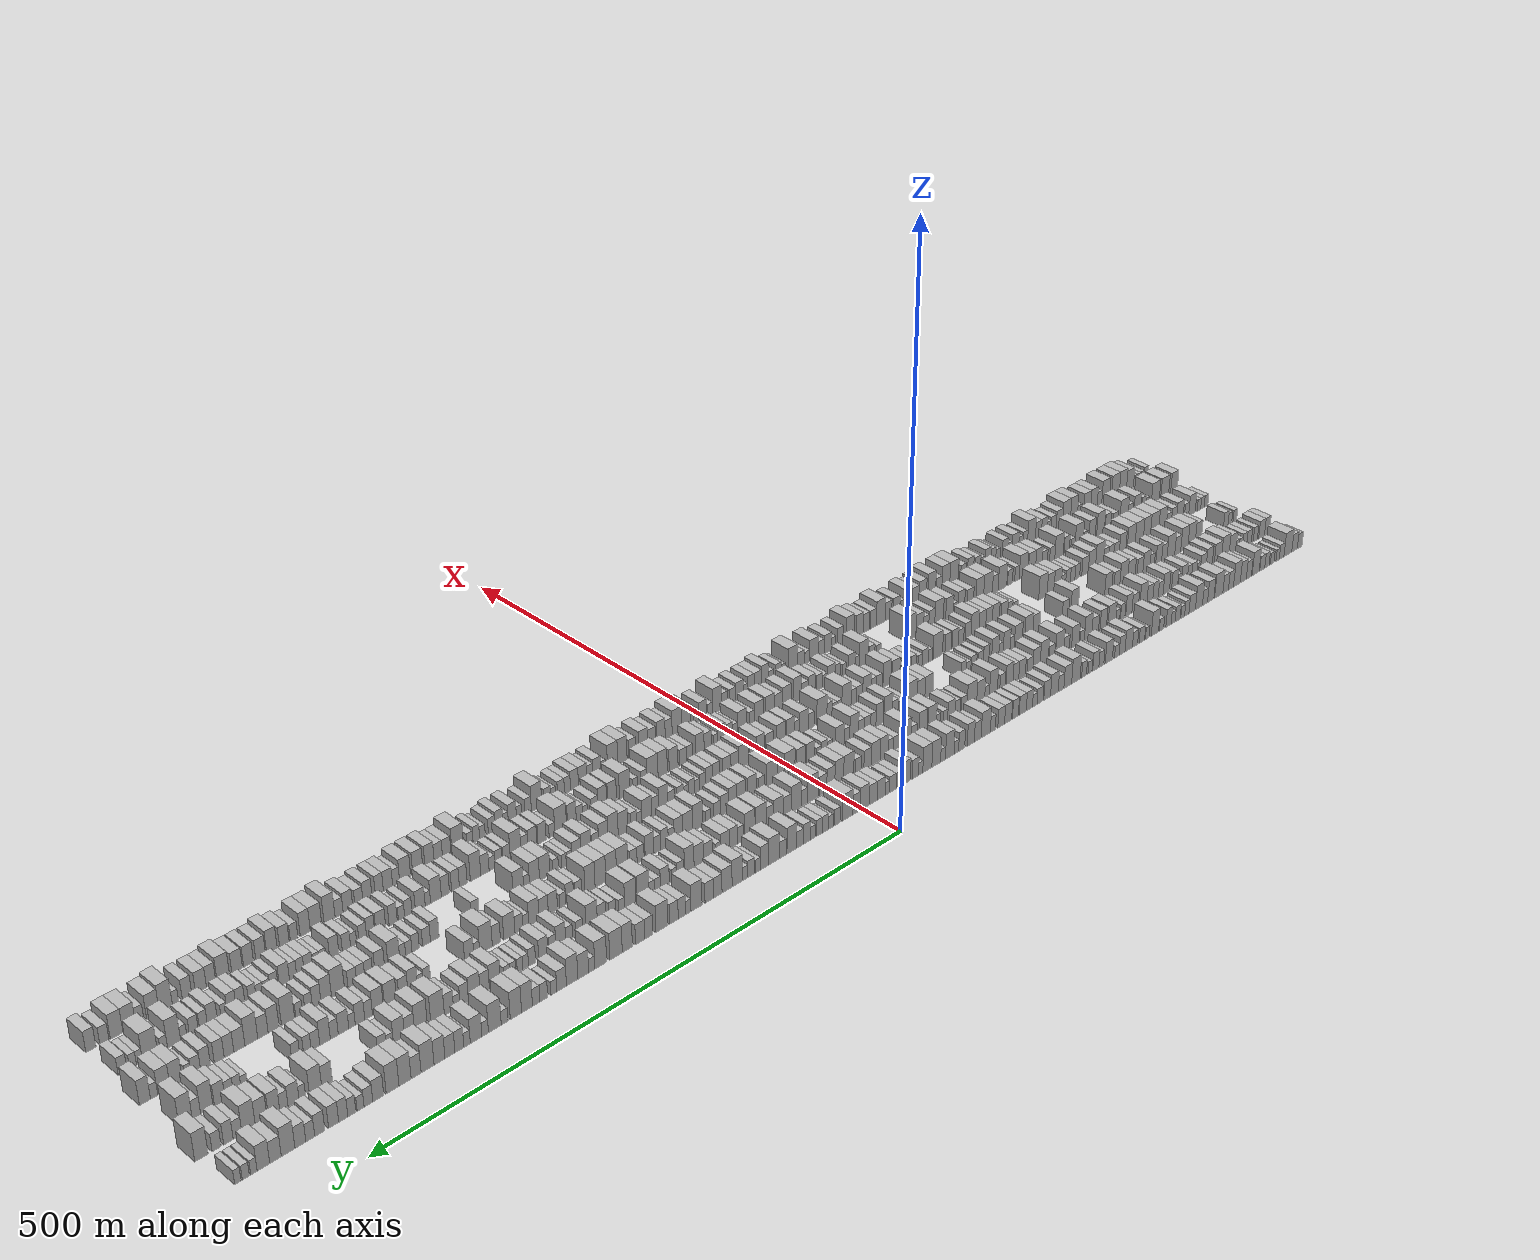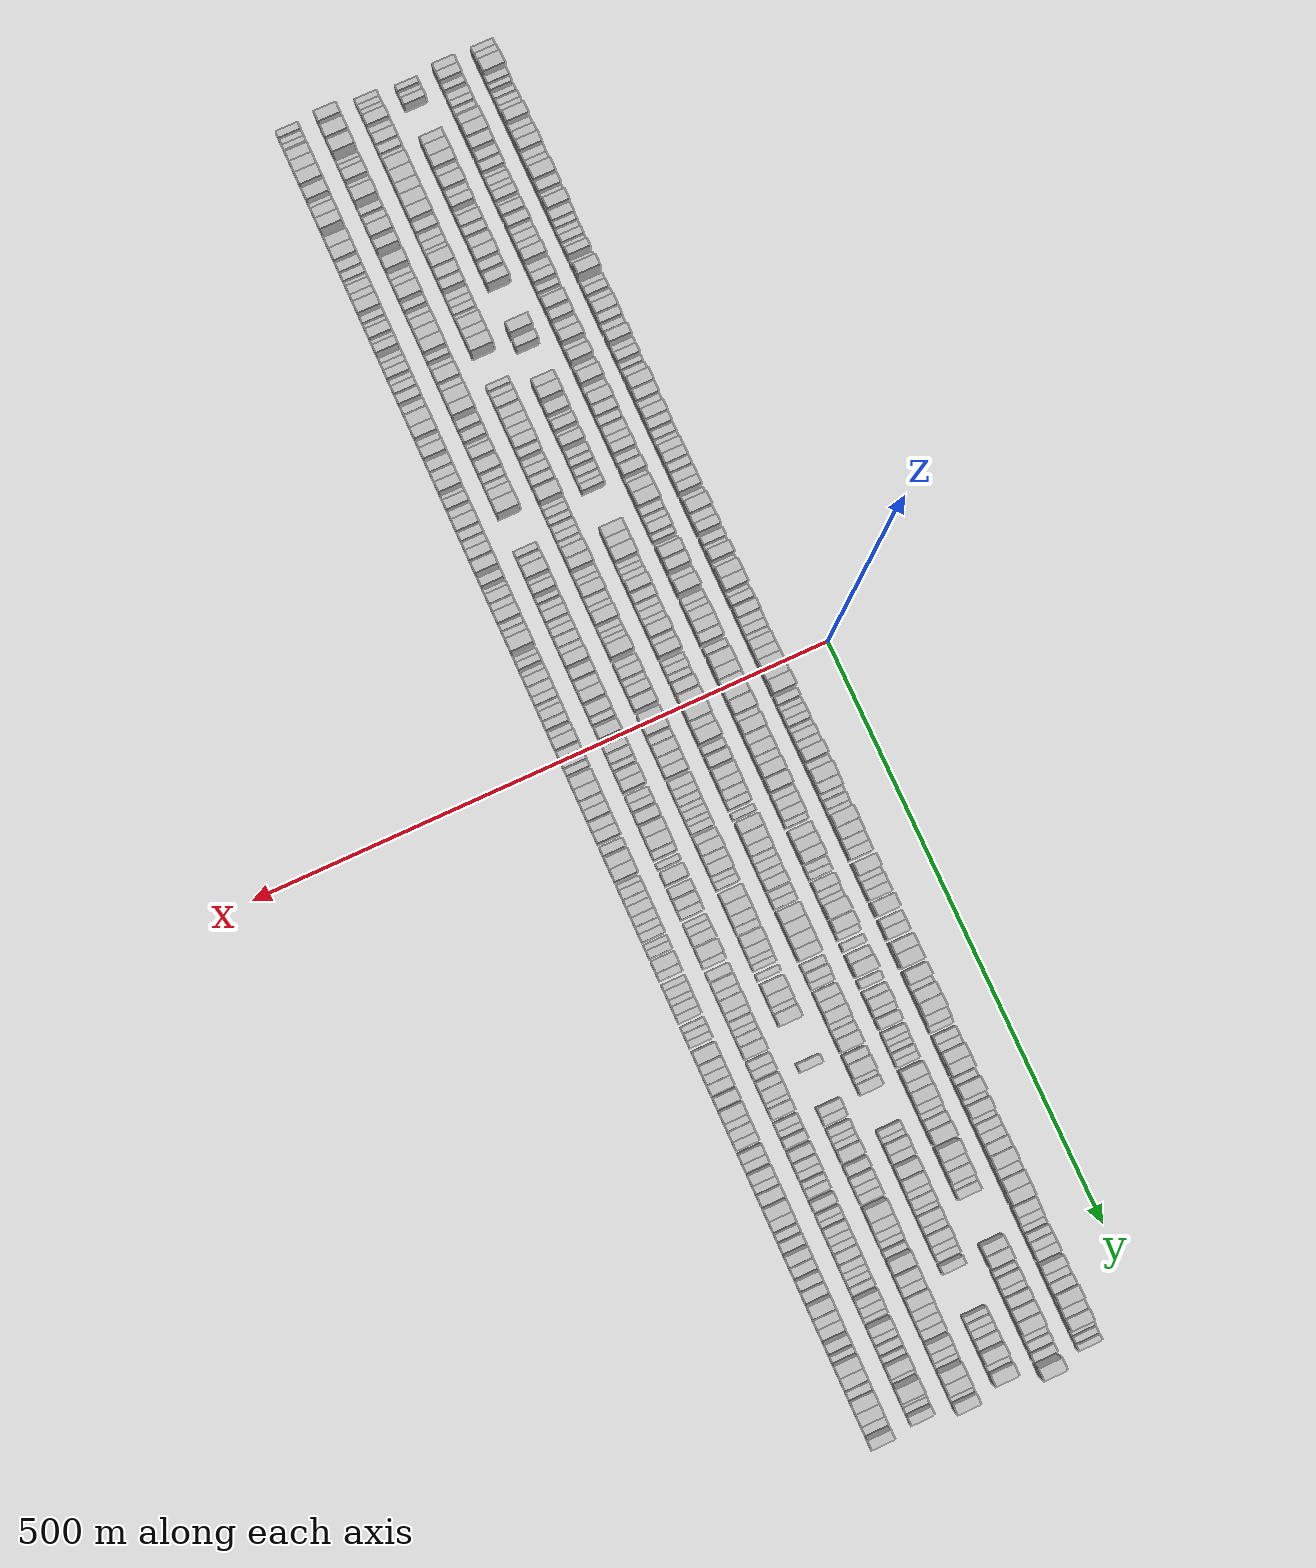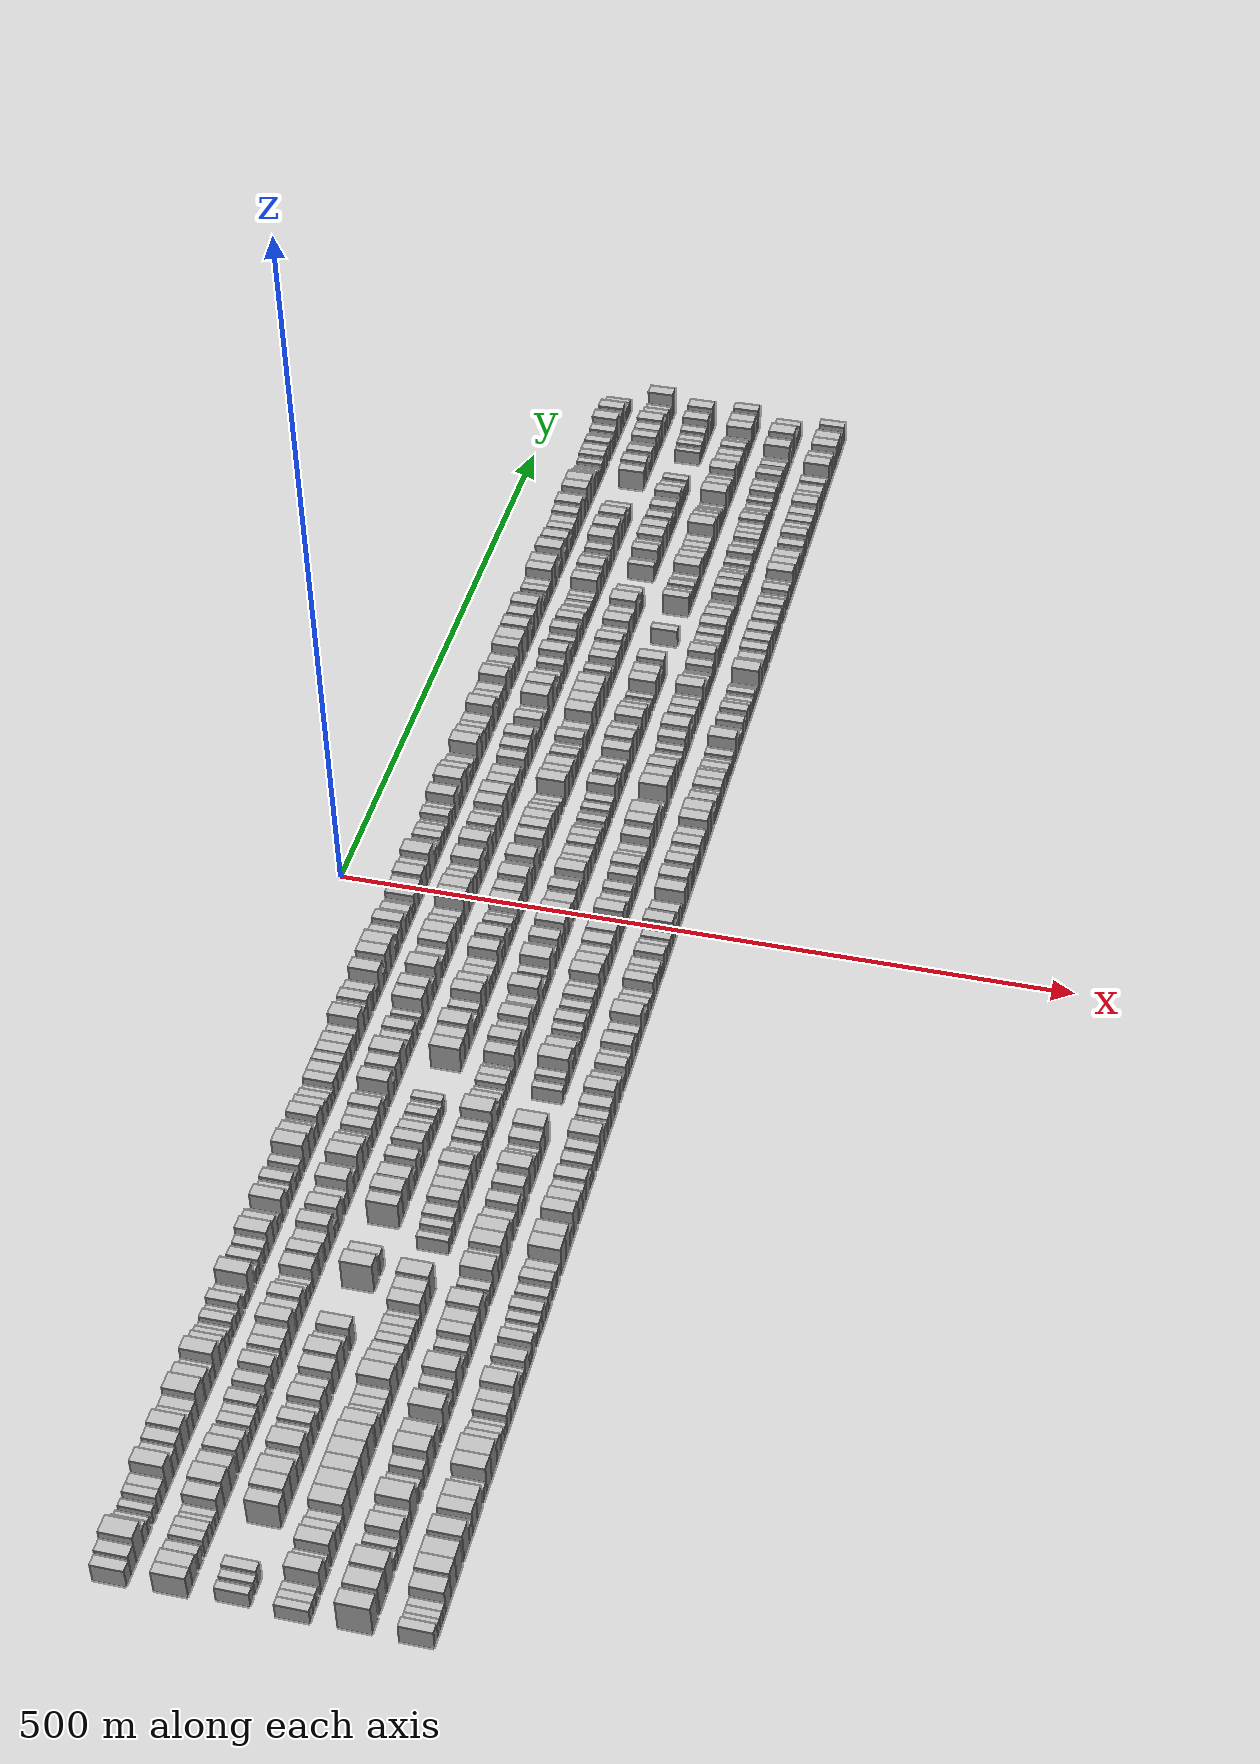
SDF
<sdf version="1.6">
 <world name="default">
  <scene>
   <sky><clouds><speed>12</speed></clouds></sky>
   <ambient>0.4 0.4 0.4 1</ambient>
   <background>0.7 0.7 0.7 1</background>
   <shadows>1</shadows>
  </scene>
  <gravity>0 0 -9.8066</gravity>
  <magnetic_field>6e-06 2.3e-05 -4.2e-05</magnetic_field>
  <physics default="0" name="default_physics" type="ode">
   <ode>
    <solver>
     <type>quick</type>
     <iters>10</iters>
     <sor>1.0</sor>
     <use_dynamic_moi_rescaling>0</use_dynamic_moi_rescaling>
    </solver>
    <constraints>
     <cfm>0</cfm>
     <erp>0.2</erp>
     <contact_max_correcting_vel>100</contact_max_correcting_vel>
     <contact_surface_layer>0.001</contact_surface_layer>
    </constraints>
   </ode>
   <max_step_size>0.004</max_step_size>
   <real_time_factor>1</real_time_factor>
   <real_time_update_rate>250</real_time_update_rate>
  </physics>
  <light name="sun" type="directional">
   <pose>0 0 10 0 0 0</pose>
   <diffuse>0.8 0.8 0.8 1</diffuse>
   <specular>0.2 0.2 0.2 1</specular>
   <attenuation>
    <range>1000</range>
    <constant>0.9</constant>
    <linear>0.01</linear>
    <quadratic>0.001</quadratic>
   </attenuation>
   <direction>-0.5 0.1 -0.9</direction>
  </light>
  <model name="building_1">
   <static>1</static>
   <pose>50.0000 -566.3373 0 0.000000 0.000000 0.000000</pose>
   <link name="link">
    <pose>0 0 7.50 0 0 0</pose>
    <collision name="collision"><geometry><box><size>20.0000 7.3254 15.0000</size></box></geometry></collision>
    <visual name="visual">
     <cast_shadows>0</cast_shadows>
     <geometry><box><size>20.0000 7.3254 15.0000</size></box></geometry>
     <material>
      <script>
       <uri>model://HANNAS_wall/materials/scripts</uri>
       <uri>model://HANNAS_wall/materials/textures</uri>
       <name>vrc/HANNAS_wall</name>
      </script>
     </material>
    </visual>
   </link>
  </model>
  <model name="building_2">
   <static>1</static>
   <pose>50.0000 -558.5314 0 0.000000 0.000000 0.000000</pose>
   <link name="link">
    <pose>0 0 9.00 0 0 0</pose>
    <collision name="collision"><geometry><box><size>20.0000 8.2865 18.0000</size></box></geometry></collision>
    <visual name="visual">
     <cast_shadows>0</cast_shadows>
     <geometry><box><size>20.0000 8.2865 18.0000</size></box></geometry>
     <material>
      <script>
       <uri>model://HANNAS_wall/materials/scripts</uri>
       <uri>model://HANNAS_wall/materials/textures</uri>
       <name>vrc/HANNAS_wall</name>
      </script>
     </material>
    </visual>
   </link>
  </model>
  <model name="building_3">
   <static>1</static>
   <pose>50.0000 -548.4884 0 0.000000 0.000000 0.000000</pose>
   <link name="link">
    <pose>0 0 12.00 0 0 0</pose>
    <collision name="collision"><geometry><box><size>20.0000 11.7996 24.0000</size></box></geometry></collision>
    <visual name="visual">
     <cast_shadows>0</cast_shadows>
     <geometry><box><size>20.0000 11.7996 24.0000</size></box></geometry>
     <material>
      <script>
       <uri>model://HANNAS_wall/materials/scripts</uri>
       <uri>model://HANNAS_wall/materials/textures</uri>
       <name>vrc/HANNAS_wall</name>
      </script>
     </material>
    </visual>
   </link>
  </model>
  <model name="building_4">
   <static>1</static>
   <pose>50.0000 -539.1193 0 0.000000 0.000000 0.000000</pose>
   <link name="link">
    <pose>0 0 7.50 0 0 0</pose>
    <collision name="collision"><geometry><box><size>20.0000 6.9386 15.0000</size></box></geometry></collision>
    <visual name="visual">
     <cast_shadows>0</cast_shadows>
     <geometry><box><size>20.0000 6.9386 15.0000</size></box></geometry>
     <material>
      <script>
       <uri>model://HANNAS_wall/materials/scripts</uri>
       <uri>model://HANNAS_wall/materials/textures</uri>
       <name>vrc/HANNAS_wall</name>
      </script>
     </material>
    </visual>
   </link>
  </model>
  <model name="building_5">
   <static>1</static>
   <pose>50.0000 -533.2011 0 0.000000 0.000000 0.000000</pose>
   <link name="link">
    <pose>0 0 6.00 0 0 0</pose>
    <collision name="collision"><geometry><box><size>20.0000 4.8977 12.0000</size></box></geometry></collision>
    <visual name="visual">
     <cast_shadows>0</cast_shadows>
     <geometry><box><size>20.0000 4.8977 12.0000</size></box></geometry>
     <material>
      <script>
       <uri>model://HANNAS_wall/materials/scripts</uri>
       <uri>model://HANNAS_wall/materials/textures</uri>
       <name>vrc/HANNAS_wall</name>
      </script>
     </material>
    </visual>
   </link>
  </model>
  <model name="building_6">
   <static>1</static>
   <pose>50.0000 -525.0686 0 0.000000 0.000000 0.000000</pose>
   <link name="link">
    <pose>0 0 6.00 0 0 0</pose>
    <collision name="collision"><geometry><box><size>20.0000 5.3672 12.0000</size></box></geometry></collision>
    <visual name="visual">
     <cast_shadows>0</cast_shadows>
     <geometry><box><size>20.0000 5.3672 12.0000</size></box></geometry>
     <material>
      <script>
       <uri>model://HANNAS_wall/materials/scripts</uri>
       <uri>model://HANNAS_wall/materials/textures</uri>
       <name>vrc/HANNAS_wall</name>
      </script>
     </material>
    </visual>
   </link>
  </model>
  <model name="building_7">
   <static>1</static>
   <pose>50.0000 -517.2954 0 0.000000 0.000000 0.000000</pose>
   <link name="link">
    <pose>0 0 7.50 0 0 0</pose>
    <collision name="collision"><geometry><box><size>20.0000 6.1791 15.0000</size></box></geometry></collision>
    <visual name="visual">
     <cast_shadows>0</cast_shadows>
     <geometry><box><size>20.0000 6.1791 15.0000</size></box></geometry>
     <material>
      <script>
       <uri>model://HANNAS_wall/materials/scripts</uri>
       <uri>model://HANNAS_wall/materials/textures</uri>
       <name>vrc/HANNAS_wall</name>
      </script>
     </material>
    </visual>
   </link>
  </model>
  <model name="building_8">
   <static>1</static>
   <pose>50.0000 -510.4935 0 0.000000 0.000000 0.000000</pose>
   <link name="link">
    <pose>0 0 7.50 0 0 0</pose>
    <collision name="collision"><geometry><box><size>20.0000 7.4247 15.0000</size></box></geometry></collision>
    <visual name="visual">
     <cast_shadows>0</cast_shadows>
     <geometry><box><size>20.0000 7.4247 15.0000</size></box></geometry>
     <material>
      <script>
       <uri>model://HANNAS_wall/materials/scripts</uri>
       <uri>model://HANNAS_wall/materials/textures</uri>
       <name>vrc/HANNAS_wall</name>
      </script>
     </material>
    </visual>
   </link>
  </model>
  <model name="building_9">
   <static>1</static>
   <pose>50.0000 -500.6763 0 0.000000 0.000000 0.000000</pose>
   <link name="link">
    <pose>0 0 12.00 0 0 0</pose>
    <collision name="collision"><geometry><box><size>20.0000 10.2097 24.0000</size></box></geometry></collision>
    <visual name="visual">
     <cast_shadows>0</cast_shadows>
     <geometry><box><size>20.0000 10.2097 24.0000</size></box></geometry>
     <material>
      <script>
       <uri>model://HANNAS_wall/materials/scripts</uri>
       <uri>model://HANNAS_wall/materials/textures</uri>
       <name>vrc/HANNAS_wall</name>
      </script>
     </material>
    </visual>
   </link>
  </model>
  <model name="building_10">
   <static>1</static>
   <pose>50.0000 -490.8525 0 0.000000 0.000000 0.000000</pose>
   <link name="link">
    <pose>0 0 9.00 0 0 0</pose>
    <collision name="collision"><geometry><box><size>20.0000 7.4378 18.0000</size></box></geometry></collision>
    <visual name="visual">
     <cast_shadows>0</cast_shadows>
     <geometry><box><size>20.0000 7.4378 18.0000</size></box></geometry>
     <material>
      <script>
       <uri>model://HANNAS_wall/materials/scripts</uri>
       <uri>model://HANNAS_wall/materials/textures</uri>
       <name>vrc/HANNAS_wall</name>
      </script>
     </material>
    </visual>
   </link>
  </model>
  <model name="building_11">
   <static>1</static>
   <pose>50.0000 -482.7396 0 0.000000 0.000000 0.000000</pose>
   <link name="link">
    <pose>0 0 10.50 0 0 0</pose>
    <collision name="collision"><geometry><box><size>20.0000 8.7881 21.0000</size></box></geometry></collision>
    <visual name="visual">
     <cast_shadows>0</cast_shadows>
     <geometry><box><size>20.0000 8.7881 21.0000</size></box></geometry>
     <material>
      <script>
       <uri>model://HANNAS_wall/materials/scripts</uri>
       <uri>model://HANNAS_wall/materials/textures</uri>
       <name>vrc/HANNAS_wall</name>
      </script>
     </material>
    </visual>
   </link>
  </model>
  <model name="building_12">
   <static>1</static>
   <pose>50.0000 -473.4747 0 0.000000 0.000000 0.000000</pose>
   <link name="link">
    <pose>0 0 12.00 0 0 0</pose>
    <collision name="collision"><geometry><box><size>20.0000 9.7416 24.0000</size></box></geometry></collision>
    <visual name="visual">
     <cast_shadows>0</cast_shadows>
     <geometry><box><size>20.0000 9.7416 24.0000</size></box></geometry>
     <material>
      <script>
       <uri>model://HANNAS_wall/materials/scripts</uri>
       <uri>model://HANNAS_wall/materials/textures</uri>
       <name>vrc/HANNAS_wall</name>
      </script>
     </material>
    </visual>
   </link>
  </model>
  <model name="building_13">
   <static>1</static>
   <pose>50.0000 -464.9641 0 0.000000 0.000000 0.000000</pose>
   <link name="link">
    <pose>0 0 9.00 0 0 0</pose>
    <collision name="collision"><geometry><box><size>20.0000 7.2798 18.0000</size></box></geometry></collision>
    <visual name="visual">
     <cast_shadows>0</cast_shadows>
     <geometry><box><size>20.0000 7.2798 18.0000</size></box></geometry>
     <material>
      <script>
       <uri>model://HANNAS_wall/materials/scripts</uri>
       <uri>model://HANNAS_wall/materials/textures</uri>
       <name>vrc/HANNAS_wall</name>
      </script>
     </material>
    </visual>
   </link>
  </model>
  <model name="building_14">
   <static>1</static>
   <pose>50.0000 -457.3623 0 0.000000 0.000000 0.000000</pose>
   <link name="link">
    <pose>0 0 9.00 0 0 0</pose>
    <collision name="collision"><geometry><box><size>20.0000 7.9237 18.0000</size></box></geometry></collision>
    <visual name="visual">
     <cast_shadows>0</cast_shadows>
     <geometry><box><size>20.0000 7.9237 18.0000</size></box></geometry>
     <material>
      <script>
       <uri>model://HANNAS_wall/materials/scripts</uri>
       <uri>model://HANNAS_wall/materials/textures</uri>
       <name>vrc/HANNAS_wall</name>
      </script>
     </material>
    </visual>
   </link>
  </model>
  <model name="building_15">
   <static>1</static>
   <pose>50.0000 -447.4712 0 0.000000 0.000000 0.000000</pose>
   <link name="link">
    <pose>0 0 12.00 0 0 0</pose>
    <collision name="collision"><geometry><box><size>20.0000 11.8585 24.0000</size></box></geometry></collision>
    <visual name="visual">
     <cast_shadows>0</cast_shadows>
     <geometry><box><size>20.0000 11.8585 24.0000</size></box></geometry>
     <material>
      <script>
       <uri>model://HANNAS_wall/materials/scripts</uri>
       <uri>model://HANNAS_wall/materials/textures</uri>
       <name>vrc/HANNAS_wall</name>
      </script>
     </material>
    </visual>
   </link>
  </model>
  <model name="building_16">
   <static>1</static>
   <pose>50.0000 -436.0148 0 0.000000 0.000000 0.000000</pose>
   <link name="link">
    <pose>0 0 10.50 0 0 0</pose>
    <collision name="collision"><geometry><box><size>20.0000 9.0544 21.0000</size></box></geometry></collision>
    <visual name="visual">
     <cast_shadows>0</cast_shadows>
     <geometry><box><size>20.0000 9.0544 21.0000</size></box></geometry>
     <material>
      <script>
       <uri>model://HANNAS_wall/materials/scripts</uri>
       <uri>model://HANNAS_wall/materials/textures</uri>
       <name>vrc/HANNAS_wall</name>
      </script>
     </material>
    </visual>
   </link>
  </model>
  <model name="building_17">
   <static>1</static>
   <pose>50.0000 -427.9351 0 0.000000 0.000000 0.000000</pose>
   <link name="link">
    <pose>0 0 7.50 0 0 0</pose>
    <collision name="collision"><geometry><box><size>20.0000 7.1049 15.0000</size></box></geometry></collision>
    <visual name="visual">
     <cast_shadows>0</cast_shadows>
     <geometry><box><size>20.0000 7.1049 15.0000</size></box></geometry>
     <material>
      <script>
       <uri>model://HANNAS_wall/materials/scripts</uri>
       <uri>model://HANNAS_wall/materials/textures</uri>
       <name>vrc/HANNAS_wall</name>
      </script>
     </material>
    </visual>
   </link>
  </model>
  <model name="building_18">
   <static>1</static>
   <pose>50.0000 -419.4042 0 0.000000 0.000000 0.000000</pose>
   <link name="link">
    <pose>0 0 12.00 0 0 0</pose>
    <collision name="collision"><geometry><box><size>20.0000 9.9570 24.0000</size></box></geometry></collision>
    <visual name="visual">
     <cast_shadows>0</cast_shadows>
     <geometry><box><size>20.0000 9.9570 24.0000</size></box></geometry>
     <material>
      <script>
       <uri>model://HANNAS_wall/materials/scripts</uri>
       <uri>model://HANNAS_wall/materials/textures</uri>
       <name>vrc/HANNAS_wall</name>
      </script>
     </material>
    </visual>
   </link>
  </model>
  <model name="building_19">
   <static>1</static>
   <pose>50.0000 -409.9322 0 0.000000 0.000000 0.000000</pose>
   <link name="link">
    <pose>0 0 9.00 0 0 0</pose>
    <collision name="collision"><geometry><box><size>20.0000 8.9870 18.0000</size></box></geometry></collision>
    <visual name="visual">
     <cast_shadows>0</cast_shadows>
     <geometry><box><size>20.0000 8.9870 18.0000</size></box></geometry>
     <material>
      <script>
       <uri>model://HANNAS_wall/materials/scripts</uri>
       <uri>model://HANNAS_wall/materials/textures</uri>
       <name>vrc/HANNAS_wall</name>
      </script>
     </material>
    </visual>
   </link>
  </model>
  <model name="building_20">
   <static>1</static>
   <pose>50.0000 -402.4324 0 0.000000 0.000000 0.000000</pose>
   <link name="link">
    <pose>0 0 7.50 0 0 0</pose>
    <collision name="collision"><geometry><box><size>20.0000 6.0127 15.0000</size></box></geometry></collision>
    <visual name="visual">
     <cast_shadows>0</cast_shadows>
     <geometry><box><size>20.0000 6.0127 15.0000</size></box></geometry>
     <material>
      <script>
       <uri>model://HANNAS_wall/materials/scripts</uri>
       <uri>model://HANNAS_wall/materials/textures</uri>
       <name>vrc/HANNAS_wall</name>
      </script>
     </material>
    </visual>
   </link>
  </model>
  <model name="building_21">
   <static>1</static>
   <pose>50.0000 -396.7875 0 0.000000 0.000000 0.000000</pose>
   <link name="link">
    <pose>0 0 6.00 0 0 0</pose>
    <collision name="collision"><geometry><box><size>20.0000 5.2770 12.0000</size></box></geometry></collision>
    <visual name="visual">
     <cast_shadows>0</cast_shadows>
     <geometry><box><size>20.0000 5.2770 12.0000</size></box></geometry>
     <material>
      <script>
       <uri>model://HANNAS_wall/materials/scripts</uri>
       <uri>model://HANNAS_wall/materials/textures</uri>
       <name>vrc/HANNAS_wall</name>
      </script>
     </material>
    </visual>
   </link>
  </model>
  <model name="building_22">
   <static>1</static>
   <pose>50.0000 -389.7473 0 0.000000 0.000000 0.000000</pose>
   <link name="link">
    <pose>0 0 7.50 0 0 0</pose>
    <collision name="collision"><geometry><box><size>20.0000 6.8035 15.0000</size></box></geometry></collision>
    <visual name="visual">
     <cast_shadows>0</cast_shadows>
     <geometry><box><size>20.0000 6.8035 15.0000</size></box></geometry>
     <material>
      <script>
       <uri>model://HANNAS_wall/materials/scripts</uri>
       <uri>model://HANNAS_wall/materials/textures</uri>
       <name>vrc/HANNAS_wall</name>
      </script>
     </material>
    </visual>
   </link>
  </model>
  <model name="building_23">
   <static>1</static>
   <pose>50.0000 -383.5608 0 0.000000 0.000000 0.000000</pose>
   <link name="link">
    <pose>0 0 6.00 0 0 0</pose>
    <collision name="collision"><geometry><box><size>20.0000 5.5695 12.0000</size></box></geometry></collision>
    <visual name="visual">
     <cast_shadows>0</cast_shadows>
     <geometry><box><size>20.0000 5.5695 12.0000</size></box></geometry>
     <material>
      <script>
       <uri>model://HANNAS_wall/materials/scripts</uri>
       <uri>model://HANNAS_wall/materials/textures</uri>
       <name>vrc/HANNAS_wall</name>
      </script>
     </material>
    </visual>
   </link>
  </model>
  <model name="building_24">
   <static>1</static>
   <pose>50.0000 -377.1747 0 0.000000 0.000000 0.000000</pose>
   <link name="link">
    <pose>0 0 9.00 0 0 0</pose>
    <collision name="collision"><geometry><box><size>20.0000 7.2027 18.0000</size></box></geometry></collision>
    <visual name="visual">
     <cast_shadows>0</cast_shadows>
     <geometry><box><size>20.0000 7.2027 18.0000</size></box></geometry>
     <material>
      <script>
       <uri>model://HANNAS_wall/materials/scripts</uri>
       <uri>model://HANNAS_wall/materials/textures</uri>
       <name>vrc/HANNAS_wall</name>
      </script>
     </material>
    </visual>
   </link>
  </model>
  <model name="building_25">
   <static>1</static>
   <pose>50.0000 -367.6038 0 0.000000 0.000000 0.000000</pose>
   <link name="link">
    <pose>0 0 6.00 0 0 0</pose>
    <collision name="collision"><geometry><box><size>20.0000 5.9390 12.0000</size></box></geometry></collision>
    <visual name="visual">
     <cast_shadows>0</cast_shadows>
     <geometry><box><size>20.0000 5.9390 12.0000</size></box></geometry>
     <material>
      <script>
       <uri>model://HANNAS_wall/materials/scripts</uri>
       <uri>model://HANNAS_wall/materials/textures</uri>
       <name>vrc/HANNAS_wall</name>
      </script>
     </material>
    </visual>
   </link>
  </model>
  <model name="building_26">
   <static>1</static>
   <pose>50.0000 -358.6228 0 0.000000 0.000000 0.000000</pose>
   <link name="link">
    <pose>0 0 12.00 0 0 0</pose>
    <collision name="collision"><geometry><box><size>20.0000 10.0231 24.0000</size></box></geometry></collision>
    <visual name="visual">
     <cast_shadows>0</cast_shadows>
     <geometry><box><size>20.0000 10.0231 24.0000</size></box></geometry>
     <material>
      <script>
       <uri>model://HANNAS_wall/materials/scripts</uri>
       <uri>model://HANNAS_wall/materials/textures</uri>
       <name>vrc/HANNAS_wall</name>
      </script>
     </material>
    </visual>
   </link>
  </model>
  <model name="building_27">
   <static>1</static>
   <pose>50.0000 -348.1740 0 0.000000 0.000000 0.000000</pose>
   <link name="link">
    <pose>0 0 6.00 0 0 0</pose>
    <collision name="collision"><geometry><box><size>20.0000 4.8745 12.0000</size></box></geometry></collision>
    <visual name="visual">
     <cast_shadows>0</cast_shadows>
     <geometry><box><size>20.0000 4.8745 12.0000</size></box></geometry>
     <material>
      <script>
       <uri>model://HANNAS_wall/materials/scripts</uri>
       <uri>model://HANNAS_wall/materials/textures</uri>
       <name>vrc/HANNAS_wall</name>
      </script>
     </material>
    </visual>
   </link>
  </model>
  <model name="building_28">
   <static>1</static>
   <pose>50.0000 -341.0008 0 0.000000 0.000000 0.000000</pose>
   <link name="link">
    <pose>0 0 7.50 0 0 0</pose>
    <collision name="collision"><geometry><box><size>20.0000 7.4718 15.0000</size></box></geometry></collision>
    <visual name="visual">
     <cast_shadows>0</cast_shadows>
     <geometry><box><size>20.0000 7.4718 15.0000</size></box></geometry>
     <material>
      <script>
       <uri>model://HANNAS_wall/materials/scripts</uri>
       <uri>model://HANNAS_wall/materials/textures</uri>
       <name>vrc/HANNAS_wall</name>
      </script>
     </material>
    </visual>
   </link>
  </model>
  <model name="building_29">
   <static>1</static>
   <pose>50.0000 -331.8281 0 0.000000 0.000000 0.000000</pose>
   <link name="link">
    <pose>0 0 7.50 0 0 0</pose>
    <collision name="collision"><geometry><box><size>20.0000 6.8737 15.0000</size></box></geometry></collision>
    <visual name="visual">
     <cast_shadows>0</cast_shadows>
     <geometry><box><size>20.0000 6.8737 15.0000</size></box></geometry>
     <material>
      <script>
       <uri>model://HANNAS_wall/materials/scripts</uri>
       <uri>model://HANNAS_wall/materials/textures</uri>
       <name>vrc/HANNAS_wall</name>
      </script>
     </material>
    </visual>
   </link>
  </model>
  <model name="building_30">
   <static>1</static>
   <pose>50.0000 -323.4104 0 0.000000 0.000000 0.000000</pose>
   <link name="link">
    <pose>0 0 10.50 0 0 0</pose>
    <collision name="collision"><geometry><box><size>20.0000 9.9616 21.0000</size></box></geometry></collision>
    <visual name="visual">
     <cast_shadows>0</cast_shadows>
     <geometry><box><size>20.0000 9.9616 21.0000</size></box></geometry>
     <material>
      <script>
       <uri>model://HANNAS_wall/materials/scripts</uri>
       <uri>model://HANNAS_wall/materials/textures</uri>
       <name>vrc/HANNAS_wall</name>
      </script>
     </material>
    </visual>
   </link>
  </model>
  <model name="building_31">
   <static>1</static>
   <pose>50.0000 -314.5346 0 0.000000 0.000000 0.000000</pose>
   <link name="link">
    <pose>0 0 9.00 0 0 0</pose>
    <collision name="collision"><geometry><box><size>20.0000 7.7899 18.0000</size></box></geometry></collision>
    <visual name="visual">
     <cast_shadows>0</cast_shadows>
     <geometry><box><size>20.0000 7.7899 18.0000</size></box></geometry>
     <material>
      <script>
       <uri>model://HANNAS_wall/materials/scripts</uri>
       <uri>model://HANNAS_wall/materials/textures</uri>
       <name>vrc/HANNAS_wall</name>
      </script>
     </material>
    </visual>
   </link>
  </model>
  <model name="building_32">
   <static>1</static>
   <pose>50.0000 -307.6552 0 0.000000 0.000000 0.000000</pose>
   <link name="link">
    <pose>0 0 6.00 0 0 0</pose>
    <collision name="collision"><geometry><box><size>20.0000 5.9690 12.0000</size></box></geometry></collision>
    <visual name="visual">
     <cast_shadows>0</cast_shadows>
     <geometry><box><size>20.0000 5.9690 12.0000</size></box></geometry>
     <material>
      <script>
       <uri>model://HANNAS_wall/materials/scripts</uri>
       <uri>model://HANNAS_wall/materials/textures</uri>
       <name>vrc/HANNAS_wall</name>
      </script>
     </material>
    </visual>
   </link>
  </model>
  <model name="building_33">
   <static>1</static>
   <pose>50.0000 -297.0364 0 0.000000 0.000000 0.000000</pose>
   <link name="link">
    <pose>0 0 10.50 0 0 0</pose>
    <collision name="collision"><geometry><box><size>20.0000 9.2685 21.0000</size></box></geometry></collision>
    <visual name="visual">
     <cast_shadows>0</cast_shadows>
     <geometry><box><size>20.0000 9.2685 21.0000</size></box></geometry>
     <material>
      <script>
       <uri>model://HANNAS_wall/materials/scripts</uri>
       <uri>model://HANNAS_wall/materials/textures</uri>
       <name>vrc/HANNAS_wall</name>
      </script>
     </material>
    </visual>
   </link>
  </model>
  <model name="building_34">
   <static>1</static>
   <pose>50.0000 -287.2047 0 0.000000 0.000000 0.000000</pose>
   <link name="link">
    <pose>0 0 7.50 0 0 0</pose>
    <collision name="collision"><geometry><box><size>20.0000 6.3949 15.0000</size></box></geometry></collision>
    <visual name="visual">
     <cast_shadows>0</cast_shadows>
     <geometry><box><size>20.0000 6.3949 15.0000</size></box></geometry>
     <material>
      <script>
       <uri>model://HANNAS_wall/materials/scripts</uri>
       <uri>model://HANNAS_wall/materials/textures</uri>
       <name>vrc/HANNAS_wall</name>
      </script>
     </material>
    </visual>
   </link>
  </model>
  <model name="building_35">
   <static>1</static>
   <pose>50.0000 -280.0026 0 0.000000 0.000000 0.000000</pose>
   <link name="link">
    <pose>0 0 9.00 0 0 0</pose>
    <collision name="collision"><geometry><box><size>20.0000 8.0094 18.0000</size></box></geometry></collision>
    <visual name="visual">
     <cast_shadows>0</cast_shadows>
     <geometry><box><size>20.0000 8.0094 18.0000</size></box></geometry>
     <material>
      <script>
       <uri>model://HANNAS_wall/materials/scripts</uri>
       <uri>model://HANNAS_wall/materials/textures</uri>
       <name>vrc/HANNAS_wall</name>
      </script>
     </material>
    </visual>
   </link>
  </model>
  <model name="building_36">
   <static>1</static>
   <pose>50.0000 -272.4580 0 0.000000 0.000000 0.000000</pose>
   <link name="link">
    <pose>0 0 6.00 0 0 0</pose>
    <collision name="collision"><geometry><box><size>20.0000 5.0798 12.0000</size></box></geometry></collision>
    <visual name="visual">
     <cast_shadows>0</cast_shadows>
     <geometry><box><size>20.0000 5.0798 12.0000</size></box></geometry>
     <material>
      <script>
       <uri>model://HANNAS_wall/materials/scripts</uri>
       <uri>model://HANNAS_wall/materials/textures</uri>
       <name>vrc/HANNAS_wall</name>
      </script>
     </material>
    </visual>
   </link>
  </model>
  <model name="building_37">
   <static>1</static>
   <pose>50.0000 -264.7876 0 0.000000 0.000000 0.000000</pose>
   <link name="link">
    <pose>0 0 7.50 0 0 0</pose>
    <collision name="collision"><geometry><box><size>20.0000 6.2608 15.0000</size></box></geometry></collision>
    <visual name="visual">
     <cast_shadows>0</cast_shadows>
     <geometry><box><size>20.0000 6.2608 15.0000</size></box></geometry>
     <material>
      <script>
       <uri>model://HANNAS_wall/materials/scripts</uri>
       <uri>model://HANNAS_wall/materials/textures</uri>
       <name>vrc/HANNAS_wall</name>
      </script>
     </material>
    </visual>
   </link>
  </model>
  <model name="building_38">
   <static>1</static>
   <pose>50.0000 -254.2339 0 0.000000 0.000000 0.000000</pose>
   <link name="link">
    <pose>0 0 12.00 0 0 0</pose>
    <collision name="collision"><geometry><box><size>20.0000 10.8467 24.0000</size></box></geometry></collision>
    <visual name="visual">
     <cast_shadows>0</cast_shadows>
     <geometry><box><size>20.0000 10.8467 24.0000</size></box></geometry>
     <material>
      <script>
       <uri>model://HANNAS_wall/materials/scripts</uri>
       <uri>model://HANNAS_wall/materials/textures</uri>
       <name>vrc/HANNAS_wall</name>
      </script>
     </material>
    </visual>
   </link>
  </model>
  <model name="building_39">
   <static>1</static>
   <pose>50.0000 -243.8764 0 0.000000 0.000000 0.000000</pose>
   <link name="link">
    <pose>0 0 10.50 0 0 0</pose>
    <collision name="collision"><geometry><box><size>20.0000 9.8683 21.0000</size></box></geometry></collision>
    <visual name="visual">
     <cast_shadows>0</cast_shadows>
     <geometry><box><size>20.0000 9.8683 21.0000</size></box></geometry>
     <material>
      <script>
       <uri>model://HANNAS_wall/materials/scripts</uri>
       <uri>model://HANNAS_wall/materials/textures</uri>
       <name>vrc/HANNAS_wall</name>
      </script>
     </material>
    </visual>
   </link>
  </model>
  <model name="building_40">
   <static>1</static>
   <pose>50.0000 -235.2992 0 0.000000 0.000000 0.000000</pose>
   <link name="link">
    <pose>0 0 7.50 0 0 0</pose>
    <collision name="collision"><geometry><box><size>20.0000 7.2861 15.0000</size></box></geometry></collision>
    <visual name="visual">
     <cast_shadows>0</cast_shadows>
     <geometry><box><size>20.0000 7.2861 15.0000</size></box></geometry>
     <material>
      <script>
       <uri>model://HANNAS_wall/materials/scripts</uri>
       <uri>model://HANNAS_wall/materials/textures</uri>
       <name>vrc/HANNAS_wall</name>
      </script>
     </material>
    </visual>
   </link>
  </model>
  <model name="building_41">
   <static>1</static>
   <pose>50.0000 -226.8695 0 0.000000 0.000000 0.000000</pose>
   <link name="link">
    <pose>0 0 10.50 0 0 0</pose>
    <collision name="collision"><geometry><box><size>20.0000 9.5733 21.0000</size></box></geometry></collision>
    <visual name="visual">
     <cast_shadows>0</cast_shadows>
     <geometry><box><size>20.0000 9.5733 21.0000</size></box></geometry>
     <material>
      <script>
       <uri>model://HANNAS_wall/materials/scripts</uri>
       <uri>model://HANNAS_wall/materials/textures</uri>
       <name>vrc/HANNAS_wall</name>
      </script>
     </material>
    </visual>
   </link>
  </model>
  <model name="building_42">
   <static>1</static>
   <pose>50.0000 -217.8198 0 0.000000 0.000000 0.000000</pose>
   <link name="link">
    <pose>0 0 9.00 0 0 0</pose>
    <collision name="collision"><geometry><box><size>20.0000 8.5262 18.0000</size></box></geometry></collision>
    <visual name="visual">
     <cast_shadows>0</cast_shadows>
     <geometry><box><size>20.0000 8.5262 18.0000</size></box></geometry>
     <material>
      <script>
       <uri>model://HANNAS_wall/materials/scripts</uri>
       <uri>model://HANNAS_wall/materials/textures</uri>
       <name>vrc/HANNAS_wall</name>
      </script>
     </material>
    </visual>
   </link>
  </model>
  <model name="building_43">
   <static>1</static>
   <pose>50.0000 -208.8589 0 0.000000 0.000000 0.000000</pose>
   <link name="link">
    <pose>0 0 7.50 0 0 0</pose>
    <collision name="collision"><geometry><box><size>20.0000 7.3954 15.0000</size></box></geometry></collision>
    <visual name="visual">
     <cast_shadows>0</cast_shadows>
     <geometry><box><size>20.0000 7.3954 15.0000</size></box></geometry>
     <material>
      <script>
       <uri>model://HANNAS_wall/materials/scripts</uri>
       <uri>model://HANNAS_wall/materials/textures</uri>
       <name>vrc/HANNAS_wall</name>
      </script>
     </material>
    </visual>
   </link>
  </model>
  <model name="building_44">
   <static>1</static>
   <pose>50.0000 -202.3088 0 0.000000 0.000000 0.000000</pose>
   <link name="link">
    <pose>0 0 6.00 0 0 0</pose>
    <collision name="collision"><geometry><box><size>20.0000 5.7048 12.0000</size></box></geometry></collision>
    <visual name="visual">
     <cast_shadows>0</cast_shadows>
     <geometry><box><size>20.0000 5.7048 12.0000</size></box></geometry>
     <material>
      <script>
       <uri>model://HANNAS_wall/materials/scripts</uri>
       <uri>model://HANNAS_wall/materials/textures</uri>
       <name>vrc/HANNAS_wall</name>
      </script>
     </material>
    </visual>
   </link>
  </model>
  <model name="building_45">
   <static>1</static>
   <pose>50.0000 -195.6156 0 0.000000 0.000000 0.000000</pose>
   <link name="link">
    <pose>0 0 9.00 0 0 0</pose>
    <collision name="collision"><geometry><box><size>20.0000 7.6817 18.0000</size></box></geometry></collision>
    <visual name="visual">
     <cast_shadows>0</cast_shadows>
     <geometry><box><size>20.0000 7.6817 18.0000</size></box></geometry>
     <material>
      <script>
       <uri>model://HANNAS_wall/materials/scripts</uri>
       <uri>model://HANNAS_wall/materials/textures</uri>
       <name>vrc/HANNAS_wall</name>
      </script>
     </material>
    </visual>
   </link>
  </model>
  <model name="building_46">
   <static>1</static>
   <pose>50.0000 -187.3811 0 0.000000 0.000000 0.000000</pose>
   <link name="link">
    <pose>0 0 9.00 0 0 0</pose>
    <collision name="collision"><geometry><box><size>20.0000 8.7873 18.0000</size></box></geometry></collision>
    <visual name="visual">
     <cast_shadows>0</cast_shadows>
     <geometry><box><size>20.0000 8.7873 18.0000</size></box></geometry>
     <material>
      <script>
       <uri>model://HANNAS_wall/materials/scripts</uri>
       <uri>model://HANNAS_wall/materials/textures</uri>
       <name>vrc/HANNAS_wall</name>
      </script>
     </material>
    </visual>
   </link>
  </model>
  <model name="building_47">
   <static>1</static>
   <pose>50.0000 -178.3383 0 0.000000 0.000000 0.000000</pose>
   <link name="link">
    <pose>0 0 9.00 0 0 0</pose>
    <collision name="collision"><geometry><box><size>20.0000 7.2983 18.0000</size></box></geometry></collision>
    <visual name="visual">
     <cast_shadows>0</cast_shadows>
     <geometry><box><size>20.0000 7.2983 18.0000</size></box></geometry>
     <material>
      <script>
       <uri>model://HANNAS_wall/materials/scripts</uri>
       <uri>model://HANNAS_wall/materials/textures</uri>
       <name>vrc/HANNAS_wall</name>
      </script>
     </material>
    </visual>
   </link>
  </model>
  <model name="building_48">
   <static>1</static>
   <pose>50.0000 -169.3800 0 0.000000 0.000000 0.000000</pose>
   <link name="link">
    <pose>0 0 9.00 0 0 0</pose>
    <collision name="collision"><geometry><box><size>20.0000 8.6183 18.0000</size></box></geometry></collision>
    <visual name="visual">
     <cast_shadows>0</cast_shadows>
     <geometry><box><size>20.0000 8.6183 18.0000</size></box></geometry>
     <material>
      <script>
       <uri>model://HANNAS_wall/materials/scripts</uri>
       <uri>model://HANNAS_wall/materials/textures</uri>
       <name>vrc/HANNAS_wall</name>
      </script>
     </material>
    </visual>
   </link>
  </model>
  <model name="building_49">
   <static>1</static>
   <pose>50.0000 -160.9733 0 0.000000 0.000000 0.000000</pose>
   <link name="link">
    <pose>0 0 9.00 0 0 0</pose>
    <collision name="collision"><geometry><box><size>20.0000 8.1951 18.0000</size></box></geometry></collision>
    <visual name="visual">
     <cast_shadows>0</cast_shadows>
     <geometry><box><size>20.0000 8.1951 18.0000</size></box></geometry>
     <material>
      <script>
       <uri>model://HANNAS_wall/materials/scripts</uri>
       <uri>model://HANNAS_wall/materials/textures</uri>
       <name>vrc/HANNAS_wall</name>
      </script>
     </material>
    </visual>
   </link>
  </model>
  <model name="building_50">
   <static>1</static>
   <pose>50.0000 -150.8355 0 0.000000 0.000000 0.000000</pose>
   <link name="link">
    <pose>0 0 7.50 0 0 0</pose>
    <collision name="collision"><geometry><box><size>20.0000 6.0805 15.0000</size></box></geometry></collision>
    <visual name="visual">
     <cast_shadows>0</cast_shadows>
     <geometry><box><size>20.0000 6.0805 15.0000</size></box></geometry>
     <material>
      <script>
       <uri>model://HANNAS_wall/materials/scripts</uri>
       <uri>model://HANNAS_wall/materials/textures</uri>
       <name>vrc/HANNAS_wall</name>
      </script>
     </material>
    </visual>
   </link>
  </model>
  <model name="building_51">
   <static>1</static>
   <pose>50.0000 -142.2655 0 0.000000 0.000000 0.000000</pose>
   <link name="link">
    <pose>0 0 12.00 0 0 0</pose>
    <collision name="collision"><geometry><box><size>20.0000 11.0595 24.0000</size></box></geometry></collision>
    <visual name="visual">
     <cast_shadows>0</cast_shadows>
     <geometry><box><size>20.0000 11.0595 24.0000</size></box></geometry>
     <material>
      <script>
       <uri>model://HANNAS_wall/materials/scripts</uri>
       <uri>model://HANNAS_wall/materials/textures</uri>
       <name>vrc/HANNAS_wall</name>
      </script>
     </material>
    </visual>
   </link>
  </model>
  <model name="building_52">
   <static>1</static>
   <pose>50.0000 -132.6514 0 0.000000 0.000000 0.000000</pose>
   <link name="link">
    <pose>0 0 9.00 0 0 0</pose>
    <collision name="collision"><geometry><box><size>20.0000 8.1687 18.0000</size></box></geometry></collision>
    <visual name="visual">
     <cast_shadows>0</cast_shadows>
     <geometry><box><size>20.0000 8.1687 18.0000</size></box></geometry>
     <material>
      <script>
       <uri>model://HANNAS_wall/materials/scripts</uri>
       <uri>model://HANNAS_wall/materials/textures</uri>
       <name>vrc/HANNAS_wall</name>
      </script>
     </material>
    </visual>
   </link>
  </model>
  <model name="building_53">
   <static>1</static>
   <pose>50.0000 -124.3221 0 0.000000 0.000000 0.000000</pose>
   <link name="link">
    <pose>0 0 10.50 0 0 0</pose>
    <collision name="collision"><geometry><box><size>20.0000 8.4899 21.0000</size></box></geometry></collision>
    <visual name="visual">
     <cast_shadows>0</cast_shadows>
     <geometry><box><size>20.0000 8.4899 21.0000</size></box></geometry>
     <material>
      <script>
       <uri>model://HANNAS_wall/materials/scripts</uri>
       <uri>model://HANNAS_wall/materials/textures</uri>
       <name>vrc/HANNAS_wall</name>
      </script>
     </material>
    </visual>
   </link>
  </model>
  <model name="building_54">
   <static>1</static>
   <pose>50.0000 -113.4491 0 0.000000 0.000000 0.000000</pose>
   <link name="link">
    <pose>0 0 9.00 0 0 0</pose>
    <collision name="collision"><geometry><box><size>20.0000 7.2561 18.0000</size></box></geometry></collision>
    <visual name="visual">
     <cast_shadows>0</cast_shadows>
     <geometry><box><size>20.0000 7.2561 18.0000</size></box></geometry>
     <material>
      <script>
       <uri>model://HANNAS_wall/materials/scripts</uri>
       <uri>model://HANNAS_wall/materials/textures</uri>
       <name>vrc/HANNAS_wall</name>
      </script>
     </material>
    </visual>
   </link>
  </model>
  <model name="building_55">
   <static>1</static>
   <pose>50.0000 -107.1371 0 0.000000 0.000000 0.000000</pose>
   <link name="link">
    <pose>0 0 6.00 0 0 0</pose>
    <collision name="collision"><geometry><box><size>20.0000 5.3679 12.0000</size></box></geometry></collision>
    <visual name="visual">
     <cast_shadows>0</cast_shadows>
     <geometry><box><size>20.0000 5.3679 12.0000</size></box></geometry>
     <material>
      <script>
       <uri>model://HANNAS_wall/materials/scripts</uri>
       <uri>model://HANNAS_wall/materials/textures</uri>
       <name>vrc/HANNAS_wall</name>
      </script>
     </material>
    </visual>
   </link>
  </model>
  <model name="building_56">
   <static>1</static>
   <pose>50.0000 -99.4139 0 0.000000 0.000000 0.000000</pose>
   <link name="link">
    <pose>0 0 12.00 0 0 0</pose>
    <collision name="collision"><geometry><box><size>20.0000 10.0786 24.0000</size></box></geometry></collision>
    <visual name="visual">
     <cast_shadows>0</cast_shadows>
     <geometry><box><size>20.0000 10.0786 24.0000</size></box></geometry>
     <material>
      <script>
       <uri>model://HANNAS_wall/materials/scripts</uri>
       <uri>model://HANNAS_wall/materials/textures</uri>
       <name>vrc/HANNAS_wall</name>
      </script>
     </material>
    </visual>
   </link>
  </model>
  <model name="building_57">
   <static>1</static>
   <pose>50.0000 -91.5494 0 0.000000 0.000000 0.000000</pose>
   <link name="link">
    <pose>0 0 6.00 0 0 0</pose>
    <collision name="collision"><geometry><box><size>20.0000 5.6504 12.0000</size></box></geometry></collision>
    <visual name="visual">
     <cast_shadows>0</cast_shadows>
     <geometry><box><size>20.0000 5.6504 12.0000</size></box></geometry>
     <material>
      <script>
       <uri>model://HANNAS_wall/materials/scripts</uri>
       <uri>model://HANNAS_wall/materials/textures</uri>
       <name>vrc/HANNAS_wall</name>
      </script>
     </material>
    </visual>
   </link>
  </model>
  <model name="building_58">
   <static>1</static>
   <pose>50.0000 -83.6177 0 0.000000 0.000000 0.000000</pose>
   <link name="link">
    <pose>0 0 12.00 0 0 0</pose>
    <collision name="collision"><geometry><box><size>20.0000 10.2130 24.0000</size></box></geometry></collision>
    <visual name="visual">
     <cast_shadows>0</cast_shadows>
     <geometry><box><size>20.0000 10.2130 24.0000</size></box></geometry>
     <material>
      <script>
       <uri>model://HANNAS_wall/materials/scripts</uri>
       <uri>model://HANNAS_wall/materials/textures</uri>
       <name>vrc/HANNAS_wall</name>
      </script>
     </material>
    </visual>
   </link>
  </model>
  <model name="building_59">
   <static>1</static>
   <pose>50.0000 -73.2745 0 0.000000 0.000000 0.000000</pose>
   <link name="link">
    <pose>0 0 12.00 0 0 0</pose>
    <collision name="collision"><geometry><box><size>20.0000 10.4735 24.0000</size></box></geometry></collision>
    <visual name="visual">
     <cast_shadows>0</cast_shadows>
     <geometry><box><size>20.0000 10.4735 24.0000</size></box></geometry>
     <material>
      <script>
       <uri>model://HANNAS_wall/materials/scripts</uri>
       <uri>model://HANNAS_wall/materials/textures</uri>
       <name>vrc/HANNAS_wall</name>
      </script>
     </material>
    </visual>
   </link>
  </model>
  <model name="building_60">
   <static>1</static>
   <pose>50.0000 -65.5673 0 0.000000 0.000000 0.000000</pose>
   <link name="link">
    <pose>0 0 6.00 0 0 0</pose>
    <collision name="collision"><geometry><box><size>20.0000 4.9408 12.0000</size></box></geometry></collision>
    <visual name="visual">
     <cast_shadows>0</cast_shadows>
     <geometry><box><size>20.0000 4.9408 12.0000</size></box></geometry>
     <material>
      <script>
       <uri>model://HANNAS_wall/materials/scripts</uri>
       <uri>model://HANNAS_wall/materials/textures</uri>
       <name>vrc/HANNAS_wall</name>
      </script>
     </material>
    </visual>
   </link>
  </model>
  <model name="building_61">
   <static>1</static>
   <pose>50.0000 -59.4401 0 0.000000 0.000000 0.000000</pose>
   <link name="link">
    <pose>0 0 9.00 0 0 0</pose>
    <collision name="collision"><geometry><box><size>20.0000 7.3136 18.0000</size></box></geometry></collision>
    <visual name="visual">
     <cast_shadows>0</cast_shadows>
     <geometry><box><size>20.0000 7.3136 18.0000</size></box></geometry>
     <material>
      <script>
       <uri>model://HANNAS_wall/materials/scripts</uri>
       <uri>model://HANNAS_wall/materials/textures</uri>
       <name>vrc/HANNAS_wall</name>
      </script>
     </material>
    </visual>
   </link>
  </model>
  <model name="building_62">
   <static>1</static>
   <pose>50.0000 -49.2737 0 0.000000 0.000000 0.000000</pose>
   <link name="link">
    <pose>0 0 10.50 0 0 0</pose>
    <collision name="collision"><geometry><box><size>20.0000 9.0193 21.0000</size></box></geometry></collision>
    <visual name="visual">
     <cast_shadows>0</cast_shadows>
     <geometry><box><size>20.0000 9.0193 21.0000</size></box></geometry>
     <material>
      <script>
       <uri>model://HANNAS_wall/materials/scripts</uri>
       <uri>model://HANNAS_wall/materials/textures</uri>
       <name>vrc/HANNAS_wall</name>
      </script>
     </material>
    </visual>
   </link>
  </model>
  <model name="building_63">
   <static>1</static>
   <pose>50.0000 -41.1256 0 0.000000 0.000000 0.000000</pose>
   <link name="link">
    <pose>0 0 7.50 0 0 0</pose>
    <collision name="collision"><geometry><box><size>20.0000 7.2769 15.0000</size></box></geometry></collision>
    <visual name="visual">
     <cast_shadows>0</cast_shadows>
     <geometry><box><size>20.0000 7.2769 15.0000</size></box></geometry>
     <material>
      <script>
       <uri>model://HANNAS_wall/materials/scripts</uri>
       <uri>model://HANNAS_wall/materials/textures</uri>
       <name>vrc/HANNAS_wall</name>
      </script>
     </material>
    </visual>
   </link>
  </model>
  <model name="building_64">
   <static>1</static>
   <pose>50.0000 -33.7850 0 0.000000 0.000000 0.000000</pose>
   <link name="link">
    <pose>0 0 7.50 0 0 0</pose>
    <collision name="collision"><geometry><box><size>20.0000 7.4044 15.0000</size></box></geometry></collision>
    <visual name="visual">
     <cast_shadows>0</cast_shadows>
     <geometry><box><size>20.0000 7.4044 15.0000</size></box></geometry>
     <material>
      <script>
       <uri>model://HANNAS_wall/materials/scripts</uri>
       <uri>model://HANNAS_wall/materials/textures</uri>
       <name>vrc/HANNAS_wall</name>
      </script>
     </material>
    </visual>
   </link>
  </model>
  <model name="building_65">
   <static>1</static>
   <pose>50.0000 -27.5641 0 0.000000 0.000000 0.000000</pose>
   <link name="link">
    <pose>0 0 6.00 0 0 0</pose>
    <collision name="collision"><geometry><box><size>20.0000 5.0374 12.0000</size></box></geometry></collision>
    <visual name="visual">
     <cast_shadows>0</cast_shadows>
     <geometry><box><size>20.0000 5.0374 12.0000</size></box></geometry>
     <material>
      <script>
       <uri>model://HANNAS_wall/materials/scripts</uri>
       <uri>model://HANNAS_wall/materials/textures</uri>
       <name>vrc/HANNAS_wall</name>
      </script>
     </material>
    </visual>
   </link>
  </model>
  <model name="building_66">
   <static>1</static>
   <pose>50.0000 -20.6608 0 0.000000 0.000000 0.000000</pose>
   <link name="link">
    <pose>0 0 9.00 0 0 0</pose>
    <collision name="collision"><geometry><box><size>20.0000 8.7693 18.0000</size></box></geometry></collision>
    <visual name="visual">
     <cast_shadows>0</cast_shadows>
     <geometry><box><size>20.0000 8.7693 18.0000</size></box></geometry>
     <material>
      <script>
       <uri>model://HANNAS_wall/materials/scripts</uri>
       <uri>model://HANNAS_wall/materials/textures</uri>
       <name>vrc/HANNAS_wall</name>
      </script>
     </material>
    </visual>
   </link>
  </model>
  <model name="building_67">
   <static>1</static>
   <pose>50.0000 -11.9061 0 0.000000 0.000000 0.000000</pose>
   <link name="link">
    <pose>0 0 9.00 0 0 0</pose>
    <collision name="collision"><geometry><box><size>20.0000 8.7401 18.0000</size></box></geometry></collision>
    <visual name="visual">
     <cast_shadows>0</cast_shadows>
     <geometry><box><size>20.0000 8.7401 18.0000</size></box></geometry>
     <material>
      <script>
       <uri>model://HANNAS_wall/materials/scripts</uri>
       <uri>model://HANNAS_wall/materials/textures</uri>
       <name>vrc/HANNAS_wall</name>
      </script>
     </material>
    </visual>
   </link>
  </model>
  <model name="building_68">
   <static>1</static>
   <pose>50.0000 -2.4964 0 0.000000 0.000000 0.000000</pose>
   <link name="link">
    <pose>0 0 10.50 0 0 0</pose>
    <collision name="collision"><geometry><box><size>20.0000 10.0793 21.0000</size></box></geometry></collision>
    <visual name="visual">
     <cast_shadows>0</cast_shadows>
     <geometry><box><size>20.0000 10.0793 21.0000</size></box></geometry>
     <material>
      <script>
       <uri>model://HANNAS_wall/materials/scripts</uri>
       <uri>model://HANNAS_wall/materials/textures</uri>
       <name>vrc/HANNAS_wall</name>
      </script>
     </material>
    </visual>
   </link>
  </model>
  <model name="building_69">
   <static>1</static>
   <pose>50.0000 6.6117 0 0.000000 0.000000 0.000000</pose>
   <link name="link">
    <pose>0 0 9.00 0 0 0</pose>
    <collision name="collision"><geometry><box><size>20.0000 8.1369 18.0000</size></box></geometry></collision>
    <visual name="visual">
     <cast_shadows>0</cast_shadows>
     <geometry><box><size>20.0000 8.1369 18.0000</size></box></geometry>
     <material>
      <script>
       <uri>model://HANNAS_wall/materials/scripts</uri>
       <uri>model://HANNAS_wall/materials/textures</uri>
       <name>vrc/HANNAS_wall</name>
      </script>
     </material>
    </visual>
   </link>
  </model>
  <model name="building_70">
   <static>1</static>
   <pose>50.0000 16.5083 0 0.000000 0.000000 0.000000</pose>
   <link name="link">
    <pose>0 0 12.00 0 0 0</pose>
    <collision name="collision"><geometry><box><size>20.0000 11.6562 24.0000</size></box></geometry></collision>
    <visual name="visual">
     <cast_shadows>0</cast_shadows>
     <geometry><box><size>20.0000 11.6562 24.0000</size></box></geometry>
     <material>
      <script>
       <uri>model://HANNAS_wall/materials/scripts</uri>
       <uri>model://HANNAS_wall/materials/textures</uri>
       <name>vrc/HANNAS_wall</name>
      </script>
     </material>
    </visual>
   </link>
  </model>
  <model name="building_71">
   <static>1</static>
   <pose>50.0000 27.7764 0 0.000000 0.000000 0.000000</pose>
   <link name="link">
    <pose>0 0 7.50 0 0 0</pose>
    <collision name="collision"><geometry><box><size>20.0000 6.8799 15.0000</size></box></geometry></collision>
    <visual name="visual">
     <cast_shadows>0</cast_shadows>
     <geometry><box><size>20.0000 6.8799 15.0000</size></box></geometry>
     <material>
      <script>
       <uri>model://HANNAS_wall/materials/scripts</uri>
       <uri>model://HANNAS_wall/materials/textures</uri>
       <name>vrc/HANNAS_wall</name>
      </script>
     </material>
    </visual>
   </link>
  </model>
  <model name="building_72">
   <static>1</static>
   <pose>50.0000 34.6715 0 0.000000 0.000000 0.000000</pose>
   <link name="link">
    <pose>0 0 6.00 0 0 0</pose>
    <collision name="collision"><geometry><box><size>20.0000 4.9103 12.0000</size></box></geometry></collision>
    <visual name="visual">
     <cast_shadows>0</cast_shadows>
     <geometry><box><size>20.0000 4.9103 12.0000</size></box></geometry>
     <material>
      <script>
       <uri>model://HANNAS_wall/materials/scripts</uri>
       <uri>model://HANNAS_wall/materials/textures</uri>
       <name>vrc/HANNAS_wall</name>
      </script>
     </material>
    </visual>
   </link>
  </model>
  <model name="building_73">
   <static>1</static>
   <pose>50.0000 40.6219 0 0.000000 0.000000 0.000000</pose>
   <link name="link">
    <pose>0 0 7.50 0 0 0</pose>
    <collision name="collision"><geometry><box><size>20.0000 6.9905 15.0000</size></box></geometry></collision>
    <visual name="visual">
     <cast_shadows>0</cast_shadows>
     <geometry><box><size>20.0000 6.9905 15.0000</size></box></geometry>
     <material>
      <script>
       <uri>model://HANNAS_wall/materials/scripts</uri>
       <uri>model://HANNAS_wall/materials/textures</uri>
       <name>vrc/HANNAS_wall</name>
      </script>
     </material>
    </visual>
   </link>
  </model>
  <model name="building_74">
   <static>1</static>
   <pose>50.0000 47.2921 0 0.000000 0.000000 0.000000</pose>
   <link name="link">
    <pose>0 0 7.50 0 0 0</pose>
    <collision name="collision"><geometry><box><size>20.0000 6.3498 15.0000</size></box></geometry></collision>
    <visual name="visual">
     <cast_shadows>0</cast_shadows>
     <geometry><box><size>20.0000 6.3498 15.0000</size></box></geometry>
     <material>
      <script>
       <uri>model://HANNAS_wall/materials/scripts</uri>
       <uri>model://HANNAS_wall/materials/textures</uri>
       <name>vrc/HANNAS_wall</name>
      </script>
     </material>
    </visual>
   </link>
  </model>
  <model name="building_75">
   <static>1</static>
   <pose>50.0000 53.9406 0 0.000000 0.000000 0.000000</pose>
   <link name="link">
    <pose>0 0 6.00 0 0 0</pose>
    <collision name="collision"><geometry><box><size>20.0000 4.9472 12.0000</size></box></geometry></collision>
    <visual name="visual">
     <cast_shadows>0</cast_shadows>
     <geometry><box><size>20.0000 4.9472 12.0000</size></box></geometry>
     <material>
      <script>
       <uri>model://HANNAS_wall/materials/scripts</uri>
       <uri>model://HANNAS_wall/materials/textures</uri>
       <name>vrc/HANNAS_wall</name>
      </script>
     </material>
    </visual>
   </link>
  </model>
  <model name="building_76">
   <static>1</static>
   <pose>50.0000 60.2573 0 0.000000 0.000000 0.000000</pose>
   <link name="link">
    <pose>0 0 9.00 0 0 0</pose>
    <collision name="collision"><geometry><box><size>20.0000 7.6862 18.0000</size></box></geometry></collision>
    <visual name="visual">
     <cast_shadows>0</cast_shadows>
     <geometry><box><size>20.0000 7.6862 18.0000</size></box></geometry>
     <material>
      <script>
       <uri>model://HANNAS_wall/materials/scripts</uri>
       <uri>model://HANNAS_wall/materials/textures</uri>
       <name>vrc/HANNAS_wall</name>
      </script>
     </material>
    </visual>
   </link>
  </model>
  <model name="building_77">
   <static>1</static>
   <pose>50.0000 67.6874 0 0.000000 0.000000 0.000000</pose>
   <link name="link">
    <pose>0 0 7.50 0 0 0</pose>
    <collision name="collision"><geometry><box><size>20.0000 7.1740 15.0000</size></box></geometry></collision>
    <visual name="visual">
     <cast_shadows>0</cast_shadows>
     <geometry><box><size>20.0000 7.1740 15.0000</size></box></geometry>
     <material>
      <script>
       <uri>model://HANNAS_wall/materials/scripts</uri>
       <uri>model://HANNAS_wall/materials/textures</uri>
       <name>vrc/HANNAS_wall</name>
      </script>
     </material>
    </visual>
   </link>
  </model>
  <model name="building_78">
   <static>1</static>
   <pose>50.0000 76.4942 0 0.000000 0.000000 0.000000</pose>
   <link name="link">
    <pose>0 0 12.00 0 0 0</pose>
    <collision name="collision"><geometry><box><size>20.0000 10.4397 24.0000</size></box></geometry></collision>
    <visual name="visual">
     <cast_shadows>0</cast_shadows>
     <geometry><box><size>20.0000 10.4397 24.0000</size></box></geometry>
     <material>
      <script>
       <uri>model://HANNAS_wall/materials/scripts</uri>
       <uri>model://HANNAS_wall/materials/textures</uri>
       <name>vrc/HANNAS_wall</name>
      </script>
     </material>
    </visual>
   </link>
  </model>
  <model name="building_79">
   <static>1</static>
   <pose>50.0000 85.9219 0 0.000000 0.000000 0.000000</pose>
   <link name="link">
    <pose>0 0 7.50 0 0 0</pose>
    <collision name="collision"><geometry><box><size>20.0000 6.4157 15.0000</size></box></geometry></collision>
    <visual name="visual">
     <cast_shadows>0</cast_shadows>
     <geometry><box><size>20.0000 6.4157 15.0000</size></box></geometry>
     <material>
      <script>
       <uri>model://HANNAS_wall/materials/scripts</uri>
       <uri>model://HANNAS_wall/materials/textures</uri>
       <name>vrc/HANNAS_wall</name>
      </script>
     </material>
    </visual>
   </link>
  </model>
  <model name="building_80">
   <static>1</static>
   <pose>50.0000 94.9156 0 0.000000 0.000000 0.000000</pose>
   <link name="link">
    <pose>0 0 12.00 0 0 0</pose>
    <collision name="collision"><geometry><box><size>20.0000 11.5717 24.0000</size></box></geometry></collision>
    <visual name="visual">
     <cast_shadows>0</cast_shadows>
     <geometry><box><size>20.0000 11.5717 24.0000</size></box></geometry>
     <material>
      <script>
       <uri>model://HANNAS_wall/materials/scripts</uri>
       <uri>model://HANNAS_wall/materials/textures</uri>
       <name>vrc/HANNAS_wall</name>
      </script>
     </material>
    </visual>
   </link>
  </model>
  <model name="building_81">
   <static>1</static>
   <pose>50.0000 105.0639 0 0.000000 0.000000 0.000000</pose>
   <link name="link">
    <pose>0 0 10.50 0 0 0</pose>
    <collision name="collision"><geometry><box><size>20.0000 8.7250 21.0000</size></box></geometry></collision>
    <visual name="visual">
     <cast_shadows>0</cast_shadows>
     <geometry><box><size>20.0000 8.7250 21.0000</size></box></geometry>
     <material>
      <script>
       <uri>model://HANNAS_wall/materials/scripts</uri>
       <uri>model://HANNAS_wall/materials/textures</uri>
       <name>vrc/HANNAS_wall</name>
      </script>
     </material>
    </visual>
   </link>
  </model>
  <model name="building_82">
   <static>1</static>
   <pose>50.0000 111.9966 0 0.000000 0.000000 0.000000</pose>
   <link name="link">
    <pose>0 0 6.00 0 0 0</pose>
    <collision name="collision"><geometry><box><size>20.0000 5.1404 12.0000</size></box></geometry></collision>
    <visual name="visual">
     <cast_shadows>0</cast_shadows>
     <geometry><box><size>20.0000 5.1404 12.0000</size></box></geometry>
     <material>
      <script>
       <uri>model://HANNAS_wall/materials/scripts</uri>
       <uri>model://HANNAS_wall/materials/textures</uri>
       <name>vrc/HANNAS_wall</name>
      </script>
     </material>
    </visual>
   </link>
  </model>
  <model name="building_83">
   <static>1</static>
   <pose>50.0000 119.0110 0 0.000000 0.000000 0.000000</pose>
   <link name="link">
    <pose>0 0 7.50 0 0 0</pose>
    <collision name="collision"><geometry><box><size>20.0000 6.8884 15.0000</size></box></geometry></collision>
    <visual name="visual">
     <cast_shadows>0</cast_shadows>
     <geometry><box><size>20.0000 6.8884 15.0000</size></box></geometry>
     <material>
      <script>
       <uri>model://HANNAS_wall/materials/scripts</uri>
       <uri>model://HANNAS_wall/materials/textures</uri>
       <name>vrc/HANNAS_wall</name>
      </script>
     </material>
    </visual>
   </link>
  </model>
  <model name="building_84">
   <static>1</static>
   <pose>50.0000 124.9751 0 0.000000 0.000000 0.000000</pose>
   <link name="link">
    <pose>0 0 6.00 0 0 0</pose>
    <collision name="collision"><geometry><box><size>20.0000 5.0398 12.0000</size></box></geometry></collision>
    <visual name="visual">
     <cast_shadows>0</cast_shadows>
     <geometry><box><size>20.0000 5.0398 12.0000</size></box></geometry>
     <material>
      <script>
       <uri>model://HANNAS_wall/materials/scripts</uri>
       <uri>model://HANNAS_wall/materials/textures</uri>
       <name>vrc/HANNAS_wall</name>
      </script>
     </material>
    </visual>
   </link>
  </model>
  <model name="building_85">
   <static>1</static>
   <pose>50.0000 133.0307 0 0.000000 0.000000 0.000000</pose>
   <link name="link">
    <pose>0 0 12.00 0 0 0</pose>
    <collision name="collision"><geometry><box><size>20.0000 11.0714 24.0000</size></box></geometry></collision>
    <visual name="visual">
     <cast_shadows>0</cast_shadows>
     <geometry><box><size>20.0000 11.0714 24.0000</size></box></geometry>
     <material>
      <script>
       <uri>model://HANNAS_wall/materials/scripts</uri>
       <uri>model://HANNAS_wall/materials/textures</uri>
       <name>vrc/HANNAS_wall</name>
      </script>
     </material>
    </visual>
   </link>
  </model>
  <model name="building_86">
   <static>1</static>
   <pose>50.0000 143.6648 0 0.000000 0.000000 0.000000</pose>
   <link name="link">
    <pose>0 0 10.50 0 0 0</pose>
    <collision name="collision"><geometry><box><size>20.0000 10.1969 21.0000</size></box></geometry></collision>
    <visual name="visual">
     <cast_shadows>0</cast_shadows>
     <geometry><box><size>20.0000 10.1969 21.0000</size></box></geometry>
     <material>
      <script>
       <uri>model://HANNAS_wall/materials/scripts</uri>
       <uri>model://HANNAS_wall/materials/textures</uri>
       <name>vrc/HANNAS_wall</name>
      </script>
     </material>
    </visual>
   </link>
  </model>
  <model name="building_87">
   <static>1</static>
   <pose>50.0000 152.9911 0 0.000000 0.000000 0.000000</pose>
   <link name="link">
    <pose>0 0 9.00 0 0 0</pose>
    <collision name="collision"><geometry><box><size>20.0000 8.4556 18.0000</size></box></geometry></collision>
    <visual name="visual">
     <cast_shadows>0</cast_shadows>
     <geometry><box><size>20.0000 8.4556 18.0000</size></box></geometry>
     <material>
      <script>
       <uri>model://HANNAS_wall/materials/scripts</uri>
       <uri>model://HANNAS_wall/materials/textures</uri>
       <name>vrc/HANNAS_wall</name>
      </script>
     </material>
    </visual>
   </link>
  </model>
  <model name="building_88">
   <static>1</static>
   <pose>50.0000 161.5408 0 0.000000 0.000000 0.000000</pose>
   <link name="link">
    <pose>0 0 9.00 0 0 0</pose>
    <collision name="collision"><geometry><box><size>20.0000 8.6439 18.0000</size></box></geometry></collision>
    <visual name="visual">
     <cast_shadows>0</cast_shadows>
     <geometry><box><size>20.0000 8.6439 18.0000</size></box></geometry>
     <material>
      <script>
       <uri>model://HANNAS_wall/materials/scripts</uri>
       <uri>model://HANNAS_wall/materials/textures</uri>
       <name>vrc/HANNAS_wall</name>
      </script>
     </material>
    </visual>
   </link>
  </model>
  <model name="building_89">
   <static>1</static>
   <pose>50.0000 174.3476 0 0.000000 0.000000 0.000000</pose>
   <link name="link">
    <pose>0 0 12.00 0 0 0</pose>
    <collision name="collision"><geometry><box><size>20.0000 10.9697 24.0000</size></box></geometry></collision>
    <visual name="visual">
     <cast_shadows>0</cast_shadows>
     <geometry><box><size>20.0000 10.9697 24.0000</size></box></geometry>
     <material>
      <script>
       <uri>model://HANNAS_wall/materials/scripts</uri>
       <uri>model://HANNAS_wall/materials/textures</uri>
       <name>vrc/HANNAS_wall</name>
      </script>
     </material>
    </visual>
   </link>
  </model>
  <model name="building_90">
   <static>1</static>
   <pose>50.0000 182.3591 0 0.000000 0.000000 0.000000</pose>
   <link name="link">
    <pose>0 0 6.00 0 0 0</pose>
    <collision name="collision"><geometry><box><size>20.0000 5.0533 12.0000</size></box></geometry></collision>
    <visual name="visual">
     <cast_shadows>0</cast_shadows>
     <geometry><box><size>20.0000 5.0533 12.0000</size></box></geometry>
     <material>
      <script>
       <uri>model://HANNAS_wall/materials/scripts</uri>
       <uri>model://HANNAS_wall/materials/textures</uri>
       <name>vrc/HANNAS_wall</name>
      </script>
     </material>
    </visual>
   </link>
  </model>
  <model name="building_91">
   <static>1</static>
   <pose>50.0000 188.6695 0 0.000000 0.000000 0.000000</pose>
   <link name="link">
    <pose>0 0 9.00 0 0 0</pose>
    <collision name="collision"><geometry><box><size>20.0000 7.5675 18.0000</size></box></geometry></collision>
    <visual name="visual">
     <cast_shadows>0</cast_shadows>
     <geometry><box><size>20.0000 7.5675 18.0000</size></box></geometry>
     <material>
      <script>
       <uri>model://HANNAS_wall/materials/scripts</uri>
       <uri>model://HANNAS_wall/materials/textures</uri>
       <name>vrc/HANNAS_wall</name>
      </script>
     </material>
    </visual>
   </link>
  </model>
  <model name="building_92">
   <static>1</static>
   <pose>50.0000 196.6122 0 0.000000 0.000000 0.000000</pose>
   <link name="link">
    <pose>0 0 9.00 0 0 0</pose>
    <collision name="collision"><geometry><box><size>20.0000 8.3180 18.0000</size></box></geometry></collision>
    <visual name="visual">
     <cast_shadows>0</cast_shadows>
     <geometry><box><size>20.0000 8.3180 18.0000</size></box></geometry>
     <material>
      <script>
       <uri>model://HANNAS_wall/materials/scripts</uri>
       <uri>model://HANNAS_wall/materials/textures</uri>
       <name>vrc/HANNAS_wall</name>
      </script>
     </material>
    </visual>
   </link>
  </model>
  <model name="building_93">
   <static>1</static>
   <pose>50.0000 208.5080 0 0.000000 0.000000 0.000000</pose>
   <link name="link">
    <pose>0 0 12.00 0 0 0</pose>
    <collision name="collision"><geometry><box><size>20.0000 11.4736 24.0000</size></box></geometry></collision>
    <visual name="visual">
     <cast_shadows>0</cast_shadows>
     <geometry><box><size>20.0000 11.4736 24.0000</size></box></geometry>
     <material>
      <script>
       <uri>model://HANNAS_wall/materials/scripts</uri>
       <uri>model://HANNAS_wall/materials/textures</uri>
       <name>vrc/HANNAS_wall</name>
      </script>
     </material>
    </visual>
   </link>
  </model>
  <model name="building_94">
   <static>1</static>
   <pose>50.0000 221.1806 0 0.000000 0.000000 0.000000</pose>
   <link name="link">
    <pose>0 0 9.00 0 0 0</pose>
    <collision name="collision"><geometry><box><size>20.0000 7.8715 18.0000</size></box></geometry></collision>
    <visual name="visual">
     <cast_shadows>0</cast_shadows>
     <geometry><box><size>20.0000 7.8715 18.0000</size></box></geometry>
     <material>
      <script>
       <uri>model://HANNAS_wall/materials/scripts</uri>
       <uri>model://HANNAS_wall/materials/textures</uri>
       <name>vrc/HANNAS_wall</name>
      </script>
     </material>
    </visual>
   </link>
  </model>
  <model name="building_95">
   <static>1</static>
   <pose>50.0000 229.5053 0 0.000000 0.000000 0.000000</pose>
   <link name="link">
    <pose>0 0 9.00 0 0 0</pose>
    <collision name="collision"><geometry><box><size>20.0000 8.7780 18.0000</size></box></geometry></collision>
    <visual name="visual">
     <cast_shadows>0</cast_shadows>
     <geometry><box><size>20.0000 8.7780 18.0000</size></box></geometry>
     <material>
      <script>
       <uri>model://HANNAS_wall/materials/scripts</uri>
       <uri>model://HANNAS_wall/materials/textures</uri>
       <name>vrc/HANNAS_wall</name>
      </script>
     </material>
    </visual>
   </link>
  </model>
  <model name="building_96">
   <static>1</static>
   <pose>50.0000 241.7116 0 0.000000 0.000000 0.000000</pose>
   <link name="link">
    <pose>0 0 12.00 0 0 0</pose>
    <collision name="collision"><geometry><box><size>20.0000 9.6346 24.0000</size></box></geometry></collision>
    <visual name="visual">
     <cast_shadows>0</cast_shadows>
     <geometry><box><size>20.0000 9.6346 24.0000</size></box></geometry>
     <material>
      <script>
       <uri>model://HANNAS_wall/materials/scripts</uri>
       <uri>model://HANNAS_wall/materials/textures</uri>
       <name>vrc/HANNAS_wall</name>
      </script>
     </material>
    </visual>
   </link>
  </model>
  <model name="building_97">
   <static>1</static>
   <pose>50.0000 252.4212 0 0.000000 0.000000 0.000000</pose>
   <link name="link">
    <pose>0 0 12.00 0 0 0</pose>
    <collision name="collision"><geometry><box><size>20.0000 11.7846 24.0000</size></box></geometry></collision>
    <visual name="visual">
     <cast_shadows>0</cast_shadows>
     <geometry><box><size>20.0000 11.7846 24.0000</size></box></geometry>
     <material>
      <script>
       <uri>model://HANNAS_wall/materials/scripts</uri>
       <uri>model://HANNAS_wall/materials/textures</uri>
       <name>vrc/HANNAS_wall</name>
      </script>
     </material>
    </visual>
   </link>
  </model>
  <model name="building_98">
   <static>1</static>
   <pose>50.0000 266.7937 0 0.000000 0.000000 0.000000</pose>
   <link name="link">
    <pose>0 0 12.00 0 0 0</pose>
    <collision name="collision"><geometry><box><size>20.0000 10.9603 24.0000</size></box></geometry></collision>
    <visual name="visual">
     <cast_shadows>0</cast_shadows>
     <geometry><box><size>20.0000 10.9603 24.0000</size></box></geometry>
     <material>
      <script>
       <uri>model://HANNAS_wall/materials/scripts</uri>
       <uri>model://HANNAS_wall/materials/textures</uri>
       <name>vrc/HANNAS_wall</name>
      </script>
     </material>
    </visual>
   </link>
  </model>
  <model name="building_99">
   <static>1</static>
   <pose>50.0000 275.1832 0 0.000000 0.000000 0.000000</pose>
   <link name="link">
    <pose>0 0 6.00 0 0 0</pose>
    <collision name="collision"><geometry><box><size>20.0000 5.8187 12.0000</size></box></geometry></collision>
    <visual name="visual">
     <cast_shadows>0</cast_shadows>
     <geometry><box><size>20.0000 5.8187 12.0000</size></box></geometry>
     <material>
      <script>
       <uri>model://HANNAS_wall/materials/scripts</uri>
       <uri>model://HANNAS_wall/materials/textures</uri>
       <name>vrc/HANNAS_wall</name>
      </script>
     </material>
    </visual>
   </link>
  </model>
  <model name="building_100">
   <static>1</static>
   <pose>50.0000 283.0935 0 0.000000 0.000000 0.000000</pose>
   <link name="link">
    <pose>0 0 10.50 0 0 0</pose>
    <collision name="collision"><geometry><box><size>20.0000 10.0018 21.0000</size></box></geometry></collision>
    <visual name="visual">
     <cast_shadows>0</cast_shadows>
     <geometry><box><size>20.0000 10.0018 21.0000</size></box></geometry>
     <material>
      <script>
       <uri>model://HANNAS_wall/materials/scripts</uri>
       <uri>model://HANNAS_wall/materials/textures</uri>
       <name>vrc/HANNAS_wall</name>
      </script>
     </material>
    </visual>
   </link>
  </model>
  <model name="building_101">
   <static>1</static>
   <pose>50.0000 293.3723 0 0.000000 0.000000 0.000000</pose>
   <link name="link">
    <pose>0 0 12.00 0 0 0</pose>
    <collision name="collision"><geometry><box><size>20.0000 10.5558 24.0000</size></box></geometry></collision>
    <visual name="visual">
     <cast_shadows>0</cast_shadows>
     <geometry><box><size>20.0000 10.5558 24.0000</size></box></geometry>
     <material>
      <script>
       <uri>model://HANNAS_wall/materials/scripts</uri>
       <uri>model://HANNAS_wall/materials/textures</uri>
       <name>vrc/HANNAS_wall</name>
      </script>
     </material>
    </visual>
   </link>
  </model>
  <model name="building_102">
   <static>1</static>
   <pose>50.0000 303.0368 0 0.000000 0.000000 0.000000</pose>
   <link name="link">
    <pose>0 0 9.00 0 0 0</pose>
    <collision name="collision"><geometry><box><size>20.0000 8.7731 18.0000</size></box></geometry></collision>
    <visual name="visual">
     <cast_shadows>0</cast_shadows>
     <geometry><box><size>20.0000 8.7731 18.0000</size></box></geometry>
     <material>
      <script>
       <uri>model://HANNAS_wall/materials/scripts</uri>
       <uri>model://HANNAS_wall/materials/textures</uri>
       <name>vrc/HANNAS_wall</name>
      </script>
     </material>
    </visual>
   </link>
  </model>
  <model name="building_103">
   <static>1</static>
   <pose>50.0000 310.1056 0 0.000000 0.000000 0.000000</pose>
   <link name="link">
    <pose>0 0 6.00 0 0 0</pose>
    <collision name="collision"><geometry><box><size>20.0000 5.3647 12.0000</size></box></geometry></collision>
    <visual name="visual">
     <cast_shadows>0</cast_shadows>
     <geometry><box><size>20.0000 5.3647 12.0000</size></box></geometry>
     <material>
      <script>
       <uri>model://HANNAS_wall/materials/scripts</uri>
       <uri>model://HANNAS_wall/materials/textures</uri>
       <name>vrc/HANNAS_wall</name>
      </script>
     </material>
    </visual>
   </link>
  </model>
  <model name="building_104">
   <static>1</static>
   <pose>50.0000 319.2848 0 0.000000 0.000000 0.000000</pose>
   <link name="link">
    <pose>0 0 7.50 0 0 0</pose>
    <collision name="collision"><geometry><box><size>20.0000 6.9936 15.0000</size></box></geometry></collision>
    <visual name="visual">
     <cast_shadows>0</cast_shadows>
     <geometry><box><size>20.0000 6.9936 15.0000</size></box></geometry>
     <material>
      <script>
       <uri>model://HANNAS_wall/materials/scripts</uri>
       <uri>model://HANNAS_wall/materials/textures</uri>
       <name>vrc/HANNAS_wall</name>
      </script>
     </material>
    </visual>
   </link>
  </model>
  <model name="building_105">
   <static>1</static>
   <pose>50.0000 326.1357 0 0.000000 0.000000 0.000000</pose>
   <link name="link">
    <pose>0 0 7.50 0 0 0</pose>
    <collision name="collision"><geometry><box><size>20.0000 6.7082 15.0000</size></box></geometry></collision>
    <visual name="visual">
     <cast_shadows>0</cast_shadows>
     <geometry><box><size>20.0000 6.7082 15.0000</size></box></geometry>
     <material>
      <script>
       <uri>model://HANNAS_wall/materials/scripts</uri>
       <uri>model://HANNAS_wall/materials/textures</uri>
       <name>vrc/HANNAS_wall</name>
      </script>
     </material>
    </visual>
   </link>
  </model>
  <model name="building_106">
   <static>1</static>
   <pose>50.0000 334.3753 0 0.000000 0.000000 0.000000</pose>
   <link name="link">
    <pose>0 0 12.00 0 0 0</pose>
    <collision name="collision"><geometry><box><size>20.0000 9.7709 24.0000</size></box></geometry></collision>
    <visual name="visual">
     <cast_shadows>0</cast_shadows>
     <geometry><box><size>20.0000 9.7709 24.0000</size></box></geometry>
     <material>
      <script>
       <uri>model://HANNAS_wall/materials/scripts</uri>
       <uri>model://HANNAS_wall/materials/textures</uri>
       <name>vrc/HANNAS_wall</name>
      </script>
     </material>
    </visual>
   </link>
  </model>
  <model name="building_107">
   <static>1</static>
   <pose>50.0000 344.2890 0 0.000000 0.000000 0.000000</pose>
   <link name="link">
    <pose>0 0 12.00 0 0 0</pose>
    <collision name="collision"><geometry><box><size>20.0000 10.0566 24.0000</size></box></geometry></collision>
    <visual name="visual">
     <cast_shadows>0</cast_shadows>
     <geometry><box><size>20.0000 10.0566 24.0000</size></box></geometry>
     <material>
      <script>
       <uri>model://HANNAS_wall/materials/scripts</uri>
       <uri>model://HANNAS_wall/materials/textures</uri>
       <name>vrc/HANNAS_wall</name>
      </script>
     </material>
    </visual>
   </link>
  </model>
  <model name="building_108">
   <static>1</static>
   <pose>50.0000 354.3158 0 0.000000 0.000000 0.000000</pose>
   <link name="link">
    <pose>0 0 6.00 0 0 0</pose>
    <collision name="collision"><geometry><box><size>20.0000 5.9970 12.0000</size></box></geometry></collision>
    <visual name="visual">
     <cast_shadows>0</cast_shadows>
     <geometry><box><size>20.0000 5.9970 12.0000</size></box></geometry>
     <material>
      <script>
       <uri>model://HANNAS_wall/materials/scripts</uri>
       <uri>model://HANNAS_wall/materials/textures</uri>
       <name>vrc/HANNAS_wall</name>
      </script>
     </material>
    </visual>
   </link>
  </model>
  <model name="building_109">
   <static>1</static>
   <pose>50.0000 362.9555 0 0.000000 0.000000 0.000000</pose>
   <link name="link">
    <pose>0 0 12.00 0 0 0</pose>
    <collision name="collision"><geometry><box><size>20.0000 11.2824 24.0000</size></box></geometry></collision>
    <visual name="visual">
     <cast_shadows>0</cast_shadows>
     <geometry><box><size>20.0000 11.2824 24.0000</size></box></geometry>
     <material>
      <script>
       <uri>model://HANNAS_wall/materials/scripts</uri>
       <uri>model://HANNAS_wall/materials/textures</uri>
       <name>vrc/HANNAS_wall</name>
      </script>
     </material>
    </visual>
   </link>
  </model>
  <model name="building_110">
   <static>1</static>
   <pose>50.0000 371.4552 0 0.000000 0.000000 0.000000</pose>
   <link name="link">
    <pose>0 0 6.00 0 0 0</pose>
    <collision name="collision"><geometry><box><size>20.0000 5.7170 12.0000</size></box></geometry></collision>
    <visual name="visual">
     <cast_shadows>0</cast_shadows>
     <geometry><box><size>20.0000 5.7170 12.0000</size></box></geometry>
     <material>
      <script>
       <uri>model://HANNAS_wall/materials/scripts</uri>
       <uri>model://HANNAS_wall/materials/textures</uri>
       <name>vrc/HANNAS_wall</name>
      </script>
     </material>
    </visual>
   </link>
  </model>
  <model name="building_111">
   <static>1</static>
   <pose>50.0000 379.3548 0 0.000000 0.000000 0.000000</pose>
   <link name="link">
    <pose>0 0 10.50 0 0 0</pose>
    <collision name="collision"><geometry><box><size>20.0000 10.0823 21.0000</size></box></geometry></collision>
    <visual name="visual">
     <cast_shadows>0</cast_shadows>
     <geometry><box><size>20.0000 10.0823 21.0000</size></box></geometry>
     <material>
      <script>
       <uri>model://HANNAS_wall/materials/scripts</uri>
       <uri>model://HANNAS_wall/materials/textures</uri>
       <name>vrc/HANNAS_wall</name>
      </script>
     </material>
    </visual>
   </link>
  </model>
  <model name="building_112">
   <static>1</static>
   <pose>50.0000 387.1852 0 0.000000 0.000000 0.000000</pose>
   <link name="link">
    <pose>0 0 6.00 0 0 0</pose>
    <collision name="collision"><geometry><box><size>20.0000 5.5784 12.0000</size></box></geometry></collision>
    <visual name="visual">
     <cast_shadows>0</cast_shadows>
     <geometry><box><size>20.0000 5.5784 12.0000</size></box></geometry>
     <material>
      <script>
       <uri>model://HANNAS_wall/materials/scripts</uri>
       <uri>model://HANNAS_wall/materials/textures</uri>
       <name>vrc/HANNAS_wall</name>
      </script>
     </material>
    </visual>
   </link>
  </model>
  <model name="building_113">
   <static>1</static>
   <pose>50.0000 393.8308 0 0.000000 0.000000 0.000000</pose>
   <link name="link">
    <pose>0 0 9.00 0 0 0</pose>
    <collision name="collision"><geometry><box><size>20.0000 7.7129 18.0000</size></box></geometry></collision>
    <visual name="visual">
     <cast_shadows>0</cast_shadows>
     <geometry><box><size>20.0000 7.7129 18.0000</size></box></geometry>
     <material>
      <script>
       <uri>model://HANNAS_wall/materials/scripts</uri>
       <uri>model://HANNAS_wall/materials/textures</uri>
       <name>vrc/HANNAS_wall</name>
      </script>
     </material>
    </visual>
   </link>
  </model>
  <model name="building_114">
   <static>1</static>
   <pose>50.0000 401.9539 0 0.000000 0.000000 0.000000</pose>
   <link name="link">
    <pose>0 0 9.00 0 0 0</pose>
    <collision name="collision"><geometry><box><size>20.0000 8.5334 18.0000</size></box></geometry></collision>
    <visual name="visual">
     <cast_shadows>0</cast_shadows>
     <geometry><box><size>20.0000 8.5334 18.0000</size></box></geometry>
     <material>
      <script>
       <uri>model://HANNAS_wall/materials/scripts</uri>
       <uri>model://HANNAS_wall/materials/textures</uri>
       <name>vrc/HANNAS_wall</name>
      </script>
     </material>
    </visual>
   </link>
  </model>
  <model name="building_115">
   <static>1</static>
   <pose>50.0000 410.8583 0 0.000000 0.000000 0.000000</pose>
   <link name="link">
    <pose>0 0 10.50 0 0 0</pose>
    <collision name="collision"><geometry><box><size>20.0000 9.2754 21.0000</size></box></geometry></collision>
    <visual name="visual">
     <cast_shadows>0</cast_shadows>
     <geometry><box><size>20.0000 9.2754 21.0000</size></box></geometry>
     <material>
      <script>
       <uri>model://HANNAS_wall/materials/scripts</uri>
       <uri>model://HANNAS_wall/materials/textures</uri>
       <name>vrc/HANNAS_wall</name>
      </script>
     </material>
    </visual>
   </link>
  </model>
  <model name="building_116">
   <static>1</static>
   <pose>50.0000 420.9840 0 0.000000 0.000000 0.000000</pose>
   <link name="link">
    <pose>0 0 12.00 0 0 0</pose>
    <collision name="collision"><geometry><box><size>20.0000 10.9758 24.0000</size></box></geometry></collision>
    <visual name="visual">
     <cast_shadows>0</cast_shadows>
     <geometry><box><size>20.0000 10.9758 24.0000</size></box></geometry>
     <material>
      <script>
       <uri>model://HANNAS_wall/materials/scripts</uri>
       <uri>model://HANNAS_wall/materials/textures</uri>
       <name>vrc/HANNAS_wall</name>
      </script>
     </material>
    </visual>
   </link>
  </model>
  <model name="building_117">
   <static>1</static>
   <pose>50.0000 430.6676 0 0.000000 0.000000 0.000000</pose>
   <link name="link">
    <pose>0 0 9.00 0 0 0</pose>
    <collision name="collision"><geometry><box><size>20.0000 8.3914 18.0000</size></box></geometry></collision>
    <visual name="visual">
     <cast_shadows>0</cast_shadows>
     <geometry><box><size>20.0000 8.3914 18.0000</size></box></geometry>
     <material>
      <script>
       <uri>model://HANNAS_wall/materials/scripts</uri>
       <uri>model://HANNAS_wall/materials/textures</uri>
       <name>vrc/HANNAS_wall</name>
      </script>
     </material>
    </visual>
   </link>
  </model>
  <model name="building_118">
   <static>1</static>
   <pose>50.0000 439.9173 0 0.000000 0.000000 0.000000</pose>
   <link name="link">
    <pose>0 0 12.00 0 0 0</pose>
    <collision name="collision"><geometry><box><size>20.0000 10.1082 24.0000</size></box></geometry></collision>
    <visual name="visual">
     <cast_shadows>0</cast_shadows>
     <geometry><box><size>20.0000 10.1082 24.0000</size></box></geometry>
     <material>
      <script>
       <uri>model://HANNAS_wall/materials/scripts</uri>
       <uri>model://HANNAS_wall/materials/textures</uri>
       <name>vrc/HANNAS_wall</name>
      </script>
     </material>
    </visual>
   </link>
  </model>
  <model name="building_119">
   <static>1</static>
   <pose>50.0000 450.2829 0 0.000000 0.000000 0.000000</pose>
   <link name="link">
    <pose>0 0 12.00 0 0 0</pose>
    <collision name="collision"><geometry><box><size>20.0000 10.6229 24.0000</size></box></geometry></collision>
    <visual name="visual">
     <cast_shadows>0</cast_shadows>
     <geometry><box><size>20.0000 10.6229 24.0000</size></box></geometry>
     <material>
      <script>
       <uri>model://HANNAS_wall/materials/scripts</uri>
       <uri>model://HANNAS_wall/materials/textures</uri>
       <name>vrc/HANNAS_wall</name>
      </script>
     </material>
    </visual>
   </link>
  </model>
  <model name="building_120">
   <static>1</static>
   <pose>50.0000 462.0882 0 0.000000 0.000000 0.000000</pose>
   <link name="link">
    <pose>0 0 9.00 0 0 0</pose>
    <collision name="collision"><geometry><box><size>20.0000 8.9876 18.0000</size></box></geometry></collision>
    <visual name="visual">
     <cast_shadows>0</cast_shadows>
     <geometry><box><size>20.0000 8.9876 18.0000</size></box></geometry>
     <material>
      <script>
       <uri>model://HANNAS_wall/materials/scripts</uri>
       <uri>model://HANNAS_wall/materials/textures</uri>
       <name>vrc/HANNAS_wall</name>
      </script>
     </material>
    </visual>
   </link>
  </model>
  <model name="building_121">
   <static>1</static>
   <pose>50.0000 470.1704 0 0.000000 0.000000 0.000000</pose>
   <link name="link">
    <pose>0 0 7.50 0 0 0</pose>
    <collision name="collision"><geometry><box><size>20.0000 7.1768 15.0000</size></box></geometry></collision>
    <visual name="visual">
     <cast_shadows>0</cast_shadows>
     <geometry><box><size>20.0000 7.1768 15.0000</size></box></geometry>
     <material>
      <script>
       <uri>model://HANNAS_wall/materials/scripts</uri>
       <uri>model://HANNAS_wall/materials/textures</uri>
       <name>vrc/HANNAS_wall</name>
      </script>
     </material>
    </visual>
   </link>
  </model>
  <model name="building_122">
   <static>1</static>
   <pose>50.0000 476.5835 0 0.000000 0.000000 0.000000</pose>
   <link name="link">
    <pose>0 0 6.00 0 0 0</pose>
    <collision name="collision"><geometry><box><size>20.0000 5.6495 12.0000</size></box></geometry></collision>
    <visual name="visual">
     <cast_shadows>0</cast_shadows>
     <geometry><box><size>20.0000 5.6495 12.0000</size></box></geometry>
     <material>
      <script>
       <uri>model://HANNAS_wall/materials/scripts</uri>
       <uri>model://HANNAS_wall/materials/textures</uri>
       <name>vrc/HANNAS_wall</name>
      </script>
     </material>
    </visual>
   </link>
  </model>
  <model name="building_123">
   <static>1</static>
   <pose>50.0000 483.6672 0 0.000000 0.000000 0.000000</pose>
   <link name="link">
    <pose>0 0 7.50 0 0 0</pose>
    <collision name="collision"><geometry><box><size>20.0000 6.5178 15.0000</size></box></geometry></collision>
    <visual name="visual">
     <cast_shadows>0</cast_shadows>
     <geometry><box><size>20.0000 6.5178 15.0000</size></box></geometry>
     <material>
      <script>
       <uri>model://HANNAS_wall/materials/scripts</uri>
       <uri>model://HANNAS_wall/materials/textures</uri>
       <name>vrc/HANNAS_wall</name>
      </script>
     </material>
    </visual>
   </link>
  </model>
  <model name="building_124">
   <static>1</static>
   <pose>50.0000 490.5840 0 0.000000 0.000000 0.000000</pose>
   <link name="link">
    <pose>0 0 9.00 0 0 0</pose>
    <collision name="collision"><geometry><box><size>20.0000 7.3159 18.0000</size></box></geometry></collision>
    <visual name="visual">
     <cast_shadows>0</cast_shadows>
     <geometry><box><size>20.0000 7.3159 18.0000</size></box></geometry>
     <material>
      <script>
       <uri>model://HANNAS_wall/materials/scripts</uri>
       <uri>model://HANNAS_wall/materials/textures</uri>
       <name>vrc/HANNAS_wall</name>
      </script>
     </material>
    </visual>
   </link>
  </model>
  <model name="building_125">
   <static>1</static>
   <pose>50.0000 498.2928 0 0.000000 0.000000 0.000000</pose>
   <link name="link">
    <pose>0 0 9.00 0 0 0</pose>
    <collision name="collision"><geometry><box><size>20.0000 8.1017 18.0000</size></box></geometry></collision>
    <visual name="visual">
     <cast_shadows>0</cast_shadows>
     <geometry><box><size>20.0000 8.1017 18.0000</size></box></geometry>
     <material>
      <script>
       <uri>model://HANNAS_wall/materials/scripts</uri>
       <uri>model://HANNAS_wall/materials/textures</uri>
       <name>vrc/HANNAS_wall</name>
      </script>
     </material>
    </visual>
   </link>
  </model>
  <model name="building_126">
   <static>1</static>
   <pose>50.0000 509.3685 0 0.000000 0.000000 0.000000</pose>
   <link name="link">
    <pose>0 0 9.00 0 0 0</pose>
    <collision name="collision"><geometry><box><size>20.0000 8.0498 18.0000</size></box></geometry></collision>
    <visual name="visual">
     <cast_shadows>0</cast_shadows>
     <geometry><box><size>20.0000 8.0498 18.0000</size></box></geometry>
     <material>
      <script>
       <uri>model://HANNAS_wall/materials/scripts</uri>
       <uri>model://HANNAS_wall/materials/textures</uri>
       <name>vrc/HANNAS_wall</name>
      </script>
     </material>
    </visual>
   </link>
  </model>
  <model name="building_127">
   <static>1</static>
   <pose>50.0000 516.9005 0 0.000000 0.000000 0.000000</pose>
   <link name="link">
    <pose>0 0 7.50 0 0 0</pose>
    <collision name="collision"><geometry><box><size>20.0000 7.0142 15.0000</size></box></geometry></collision>
    <visual name="visual">
     <cast_shadows>0</cast_shadows>
     <geometry><box><size>20.0000 7.0142 15.0000</size></box></geometry>
     <material>
      <script>
       <uri>model://HANNAS_wall/materials/scripts</uri>
       <uri>model://HANNAS_wall/materials/textures</uri>
       <name>vrc/HANNAS_wall</name>
      </script>
     </material>
    </visual>
   </link>
  </model>
  <model name="building_128">
   <static>1</static>
   <pose>50.0000 524.6987 0 0.000000 0.000000 0.000000</pose>
   <link name="link">
    <pose>0 0 9.00 0 0 0</pose>
    <collision name="collision"><geometry><box><size>20.0000 8.5821 18.0000</size></box></geometry></collision>
    <visual name="visual">
     <cast_shadows>0</cast_shadows>
     <geometry><box><size>20.0000 8.5821 18.0000</size></box></geometry>
     <material>
      <script>
       <uri>model://HANNAS_wall/materials/scripts</uri>
       <uri>model://HANNAS_wall/materials/textures</uri>
       <name>vrc/HANNAS_wall</name>
      </script>
     </material>
    </visual>
   </link>
  </model>
  <model name="building_129">
   <static>1</static>
   <pose>50.0000 534.3169 0 0.000000 0.000000 0.000000</pose>
   <link name="link">
    <pose>0 0 12.00 0 0 0</pose>
    <collision name="collision"><geometry><box><size>20.0000 10.6543 24.0000</size></box></geometry></collision>
    <visual name="visual">
     <cast_shadows>0</cast_shadows>
     <geometry><box><size>20.0000 10.6543 24.0000</size></box></geometry>
     <material>
      <script>
       <uri>model://HANNAS_wall/materials/scripts</uri>
       <uri>model://HANNAS_wall/materials/textures</uri>
       <name>vrc/HANNAS_wall</name>
      </script>
     </material>
    </visual>
   </link>
  </model>
  <model name="building_130">
   <static>1</static>
   <pose>50.0000 544.1222 0 0.000000 0.000000 0.000000</pose>
   <link name="link">
    <pose>0 0 9.00 0 0 0</pose>
    <collision name="collision"><geometry><box><size>20.0000 8.9563 18.0000</size></box></geometry></collision>
    <visual name="visual">
     <cast_shadows>0</cast_shadows>
     <geometry><box><size>20.0000 8.9563 18.0000</size></box></geometry>
     <material>
      <script>
       <uri>model://HANNAS_wall/materials/scripts</uri>
       <uri>model://HANNAS_wall/materials/textures</uri>
       <name>vrc/HANNAS_wall</name>
      </script>
     </material>
    </visual>
   </link>
  </model>
  <model name="building_131">
   <static>1</static>
   <pose>50.0000 553.4761 0 0.000000 0.000000 0.000000</pose>
   <link name="link">
    <pose>0 0 10.50 0 0 0</pose>
    <collision name="collision"><geometry><box><size>20.0000 9.7514 21.0000</size></box></geometry></collision>
    <visual name="visual">
     <cast_shadows>0</cast_shadows>
     <geometry><box><size>20.0000 9.7514 21.0000</size></box></geometry>
     <material>
      <script>
       <uri>model://HANNAS_wall/materials/scripts</uri>
       <uri>model://HANNAS_wall/materials/textures</uri>
       <name>vrc/HANNAS_wall</name>
      </script>
     </material>
    </visual>
   </link>
  </model>
  <model name="building_132">
   <static>1</static>
   <pose>50.0000 560.8015 0 0.000000 0.000000 0.000000</pose>
   <link name="link">
    <pose>0 0 6.00 0 0 0</pose>
    <collision name="collision"><geometry><box><size>20.0000 4.8995 12.0000</size></box></geometry></collision>
    <visual name="visual">
     <cast_shadows>0</cast_shadows>
     <geometry><box><size>20.0000 4.8995 12.0000</size></box></geometry>
     <material>
      <script>
       <uri>model://HANNAS_wall/materials/scripts</uri>
       <uri>model://HANNAS_wall/materials/textures</uri>
       <name>vrc/HANNAS_wall</name>
      </script>
     </material>
    </visual>
   </link>
  </model>
  <model name="building_133">
   <static>1</static>
   <pose>50.0000 566.9949 0 0.000000 0.000000 0.000000</pose>
   <link name="link">
    <pose>0 0 6.00 0 0 0</pose>
    <collision name="collision"><geometry><box><size>20.0000 5.4872 12.0000</size></box></geometry></collision>
    <visual name="visual">
     <cast_shadows>0</cast_shadows>
     <geometry><box><size>20.0000 5.4872 12.0000</size></box></geometry>
     <material>
      <script>
       <uri>model://HANNAS_wall/materials/scripts</uri>
       <uri>model://HANNAS_wall/materials/textures</uri>
       <name>vrc/HANNAS_wall</name>
      </script>
     </material>
    </visual>
   </link>
  </model>
  <model name="building_134">
   <static>1</static>
   <pose>50.0000 573.1457 0 0.000000 0.000000 0.000000</pose>
   <link name="link">
    <pose>0 0 6.00 0 0 0</pose>
    <collision name="collision"><geometry><box><size>20.0000 4.8145 12.0000</size></box></geometry></collision>
    <visual name="visual">
     <cast_shadows>0</cast_shadows>
     <geometry><box><size>20.0000 4.8145 12.0000</size></box></geometry>
     <material>
      <script>
       <uri>model://HANNAS_wall/materials/scripts</uri>
       <uri>model://HANNAS_wall/materials/textures</uri>
       <name>vrc/HANNAS_wall</name>
      </script>
     </material>
    </visual>
   </link>
  </model>
  <model name="building_135">
   <static>1</static>
   <pose>85.0000 -565.2305 0 0.000000 0.000000 0.000000</pose>
   <link name="link">
    <pose>0 0 9.00 0 0 0</pose>
    <collision name="collision"><geometry><box><size>20.0000 7.5390 18.0000</size></box></geometry></collision>
    <visual name="visual">
     <cast_shadows>0</cast_shadows>
     <geometry><box><size>20.0000 7.5390 18.0000</size></box></geometry>
     <material>
      <script>
       <uri>model://HANNAS_wall/materials/scripts</uri>
       <uri>model://HANNAS_wall/materials/textures</uri>
       <name>vrc/HANNAS_wall</name>
      </script>
     </material>
    </visual>
   </link>
  </model>
  <model name="building_136">
   <static>1</static>
   <pose>85.0000 -557.0987 0 0.000000 0.000000 0.000000</pose>
   <link name="link">
    <pose>0 0 9.00 0 0 0</pose>
    <collision name="collision"><geometry><box><size>20.0000 8.7245 18.0000</size></box></geometry></collision>
    <visual name="visual">
     <cast_shadows>0</cast_shadows>
     <geometry><box><size>20.0000 8.7245 18.0000</size></box></geometry>
     <material>
      <script>
       <uri>model://HANNAS_wall/materials/scripts</uri>
       <uri>model://HANNAS_wall/materials/textures</uri>
       <name>vrc/HANNAS_wall</name>
      </script>
     </material>
    </visual>
   </link>
  </model>
  <model name="building_137">
   <static>1</static>
   <pose>85.0000 -547.6555 0 0.000000 0.000000 0.000000</pose>
   <link name="link">
    <pose>0 0 7.50 0 0 0</pose>
    <collision name="collision"><geometry><box><size>20.0000 6.1619 15.0000</size></box></geometry></collision>
    <visual name="visual">
     <cast_shadows>0</cast_shadows>
     <geometry><box><size>20.0000 6.1619 15.0000</size></box></geometry>
     <material>
      <script>
       <uri>model://HANNAS_wall/materials/scripts</uri>
       <uri>model://HANNAS_wall/materials/textures</uri>
       <name>vrc/HANNAS_wall</name>
      </script>
     </material>
    </visual>
   </link>
  </model>
  <model name="building_138">
   <static>1</static>
   <pose>85.0000 -538.1790 0 0.000000 0.000000 0.000000</pose>
   <link name="link">
    <pose>0 0 7.50 0 0 0</pose>
    <collision name="collision"><geometry><box><size>20.0000 6.7912 15.0000</size></box></geometry></collision>
    <visual name="visual">
     <cast_shadows>0</cast_shadows>
     <geometry><box><size>20.0000 6.7912 15.0000</size></box></geometry>
     <material>
      <script>
       <uri>model://HANNAS_wall/materials/scripts</uri>
       <uri>model://HANNAS_wall/materials/textures</uri>
       <name>vrc/HANNAS_wall</name>
      </script>
     </material>
    </visual>
   </link>
  </model>
  <model name="building_139">
   <static>1</static>
   <pose>85.0000 -531.6476 0 0.000000 0.000000 0.000000</pose>
   <link name="link">
    <pose>0 0 7.50 0 0 0</pose>
    <collision name="collision"><geometry><box><size>20.0000 6.2715 15.0000</size></box></geometry></collision>
    <visual name="visual">
     <cast_shadows>0</cast_shadows>
     <geometry><box><size>20.0000 6.2715 15.0000</size></box></geometry>
     <material>
      <script>
       <uri>model://HANNAS_wall/materials/scripts</uri>
       <uri>model://HANNAS_wall/materials/textures</uri>
       <name>vrc/HANNAS_wall</name>
      </script>
     </material>
    </visual>
   </link>
  </model>
  <model name="building_140">
   <static>1</static>
   <pose>85.0000 -525.9291 0 0.000000 0.000000 0.000000</pose>
   <link name="link">
    <pose>0 0 6.00 0 0 0</pose>
    <collision name="collision"><geometry><box><size>20.0000 5.1656 12.0000</size></box></geometry></collision>
    <visual name="visual">
     <cast_shadows>0</cast_shadows>
     <geometry><box><size>20.0000 5.1656 12.0000</size></box></geometry>
     <material>
      <script>
       <uri>model://HANNAS_wall/materials/scripts</uri>
       <uri>model://HANNAS_wall/materials/textures</uri>
       <name>vrc/HANNAS_wall</name>
      </script>
     </material>
    </visual>
   </link>
  </model>
  <model name="building_141">
   <static>1</static>
   <pose>85.0000 -520.8363 0 0.000000 0.000000 0.000000</pose>
   <link name="link">
    <pose>0 0 6.00 0 0 0</pose>
    <collision name="collision"><geometry><box><size>20.0000 5.0199 12.0000</size></box></geometry></collision>
    <visual name="visual">
     <cast_shadows>0</cast_shadows>
     <geometry><box><size>20.0000 5.0199 12.0000</size></box></geometry>
     <material>
      <script>
       <uri>model://HANNAS_wall/materials/scripts</uri>
       <uri>model://HANNAS_wall/materials/textures</uri>
       <name>vrc/HANNAS_wall</name>
      </script>
     </material>
    </visual>
   </link>
  </model>
  <model name="building_142">
   <static>1</static>
   <pose>85.0000 -513.4286 0 0.000000 0.000000 0.000000</pose>
   <link name="link">
    <pose>0 0 10.50 0 0 0</pose>
    <collision name="collision"><geometry><box><size>20.0000 9.7955 21.0000</size></box></geometry></collision>
    <visual name="visual">
     <cast_shadows>0</cast_shadows>
     <geometry><box><size>20.0000 9.7955 21.0000</size></box></geometry>
     <material>
      <script>
       <uri>model://HANNAS_wall/materials/scripts</uri>
       <uri>model://HANNAS_wall/materials/textures</uri>
       <name>vrc/HANNAS_wall</name>
      </script>
     </material>
    </visual>
   </link>
  </model>
  <model name="building_143">
   <static>1</static>
   <pose>85.0000 -502.9109 0 0.000000 0.000000 0.000000</pose>
   <link name="link">
    <pose>0 0 12.00 0 0 0</pose>
    <collision name="collision"><geometry><box><size>20.0000 11.2398 24.0000</size></box></geometry></collision>
    <visual name="visual">
     <cast_shadows>0</cast_shadows>
     <geometry><box><size>20.0000 11.2398 24.0000</size></box></geometry>
     <material>
      <script>
       <uri>model://HANNAS_wall/materials/scripts</uri>
       <uri>model://HANNAS_wall/materials/textures</uri>
       <name>vrc/HANNAS_wall</name>
      </script>
     </material>
    </visual>
   </link>
  </model>
  <model name="building_144">
   <static>1</static>
   <pose>85.0000 -492.1735 0 0.000000 0.000000 0.000000</pose>
   <link name="link">
    <pose>0 0 10.50 0 0 0</pose>
    <collision name="collision"><geometry><box><size>20.0000 10.2351 21.0000</size></box></geometry></collision>
    <visual name="visual">
     <cast_shadows>0</cast_shadows>
     <geometry><box><size>20.0000 10.2351 21.0000</size></box></geometry>
     <material>
      <script>
       <uri>model://HANNAS_wall/materials/scripts</uri>
       <uri>model://HANNAS_wall/materials/textures</uri>
       <name>vrc/HANNAS_wall</name>
      </script>
     </material>
    </visual>
   </link>
  </model>
  <model name="building_145">
   <static>1</static>
   <pose>85.0000 -479.6143 0 0.000000 0.000000 0.000000</pose>
   <link name="link">
    <pose>0 0 10.50 0 0 0</pose>
    <collision name="collision"><geometry><box><size>20.0000 8.8833 21.0000</size></box></geometry></collision>
    <visual name="visual">
     <cast_shadows>0</cast_shadows>
     <geometry><box><size>20.0000 8.8833 21.0000</size></box></geometry>
     <material>
      <script>
       <uri>model://HANNAS_wall/materials/scripts</uri>
       <uri>model://HANNAS_wall/materials/textures</uri>
       <name>vrc/HANNAS_wall</name>
      </script>
     </material>
    </visual>
   </link>
  </model>
  <model name="building_146">
   <static>1</static>
   <pose>85.0000 -470.9877 0 0.000000 0.000000 0.000000</pose>
   <link name="link">
    <pose>0 0 9.00 0 0 0</pose>
    <collision name="collision"><geometry><box><size>20.0000 8.3699 18.0000</size></box></geometry></collision>
    <visual name="visual">
     <cast_shadows>0</cast_shadows>
     <geometry><box><size>20.0000 8.3699 18.0000</size></box></geometry>
     <material>
      <script>
       <uri>model://HANNAS_wall/materials/scripts</uri>
       <uri>model://HANNAS_wall/materials/textures</uri>
       <name>vrc/HANNAS_wall</name>
      </script>
     </material>
    </visual>
   </link>
  </model>
  <model name="building_147">
   <static>1</static>
   <pose>85.0000 -464.3508 0 0.000000 0.000000 0.000000</pose>
   <link name="link">
    <pose>0 0 6.00 0 0 0</pose>
    <collision name="collision"><geometry><box><size>20.0000 4.9038 12.0000</size></box></geometry></collision>
    <visual name="visual">
     <cast_shadows>0</cast_shadows>
     <geometry><box><size>20.0000 4.9038 12.0000</size></box></geometry>
     <material>
      <script>
       <uri>model://HANNAS_wall/materials/scripts</uri>
       <uri>model://HANNAS_wall/materials/textures</uri>
       <name>vrc/HANNAS_wall</name>
      </script>
     </material>
    </visual>
   </link>
  </model>
  <model name="building_148">
   <static>1</static>
   <pose>85.0000 -458.2104 0 0.000000 0.000000 0.000000</pose>
   <link name="link">
    <pose>0 0 7.50 0 0 0</pose>
    <collision name="collision"><geometry><box><size>20.0000 7.3771 15.0000</size></box></geometry></collision>
    <visual name="visual">
     <cast_shadows>0</cast_shadows>
     <geometry><box><size>20.0000 7.3771 15.0000</size></box></geometry>
     <material>
      <script>
       <uri>model://HANNAS_wall/materials/scripts</uri>
       <uri>model://HANNAS_wall/materials/textures</uri>
       <name>vrc/HANNAS_wall</name>
      </script>
     </material>
    </visual>
   </link>
  </model>
  <model name="building_149">
   <static>1</static>
   <pose>85.0000 -451.4634 0 0.000000 0.000000 0.000000</pose>
   <link name="link">
    <pose>0 0 7.50 0 0 0</pose>
    <collision name="collision"><geometry><box><size>20.0000 6.1169 15.0000</size></box></geometry></collision>
    <visual name="visual">
     <cast_shadows>0</cast_shadows>
     <geometry><box><size>20.0000 6.1169 15.0000</size></box></geometry>
     <material>
      <script>
       <uri>model://HANNAS_wall/materials/scripts</uri>
       <uri>model://HANNAS_wall/materials/textures</uri>
       <name>vrc/HANNAS_wall</name>
      </script>
     </material>
    </visual>
   </link>
  </model>
  <model name="building_150">
   <static>1</static>
   <pose>85.0000 -444.2012 0 0.000000 0.000000 0.000000</pose>
   <link name="link">
    <pose>0 0 9.00 0 0 0</pose>
    <collision name="collision"><geometry><box><size>20.0000 8.4076 18.0000</size></box></geometry></collision>
    <visual name="visual">
     <cast_shadows>0</cast_shadows>
     <geometry><box><size>20.0000 8.4076 18.0000</size></box></geometry>
     <material>
      <script>
       <uri>model://HANNAS_wall/materials/scripts</uri>
       <uri>model://HANNAS_wall/materials/textures</uri>
       <name>vrc/HANNAS_wall</name>
      </script>
     </material>
    </visual>
   </link>
  </model>
  <model name="building_151">
   <static>1</static>
   <pose>85.0000 -437.3884 0 0.000000 0.000000 0.000000</pose>
   <link name="link">
    <pose>0 0 6.00 0 0 0</pose>
    <collision name="collision"><geometry><box><size>20.0000 5.2180 12.0000</size></box></geometry></collision>
    <visual name="visual">
     <cast_shadows>0</cast_shadows>
     <geometry><box><size>20.0000 5.2180 12.0000</size></box></geometry>
     <material>
      <script>
       <uri>model://HANNAS_wall/materials/scripts</uri>
       <uri>model://HANNAS_wall/materials/textures</uri>
       <name>vrc/HANNAS_wall</name>
      </script>
     </material>
    </visual>
   </link>
  </model>
  <model name="building_152">
   <static>1</static>
   <pose>85.0000 -430.5078 0 0.000000 0.000000 0.000000</pose>
   <link name="link">
    <pose>0 0 9.00 0 0 0</pose>
    <collision name="collision"><geometry><box><size>20.0000 8.5432 18.0000</size></box></geometry></collision>
    <visual name="visual">
     <cast_shadows>0</cast_shadows>
     <geometry><box><size>20.0000 8.5432 18.0000</size></box></geometry>
     <material>
      <script>
       <uri>model://HANNAS_wall/materials/scripts</uri>
       <uri>model://HANNAS_wall/materials/textures</uri>
       <name>vrc/HANNAS_wall</name>
      </script>
     </material>
    </visual>
   </link>
  </model>
  <model name="building_153">
   <static>1</static>
   <pose>85.0000 -418.7952 0 0.000000 0.000000 0.000000</pose>
   <link name="link">
    <pose>0 0 10.50 0 0 0</pose>
    <collision name="collision"><geometry><box><size>20.0000 8.8820 21.0000</size></box></geometry></collision>
    <visual name="visual">
     <cast_shadows>0</cast_shadows>
     <geometry><box><size>20.0000 8.8820 21.0000</size></box></geometry>
     <material>
      <script>
       <uri>model://HANNAS_wall/materials/scripts</uri>
       <uri>model://HANNAS_wall/materials/textures</uri>
       <name>vrc/HANNAS_wall</name>
      </script>
     </material>
    </visual>
   </link>
  </model>
  <model name="building_154">
   <static>1</static>
   <pose>85.0000 -410.9439 0 0.000000 0.000000 0.000000</pose>
   <link name="link">
    <pose>0 0 7.50 0 0 0</pose>
    <collision name="collision"><geometry><box><size>20.0000 6.8206 15.0000</size></box></geometry></collision>
    <visual name="visual">
     <cast_shadows>0</cast_shadows>
     <geometry><box><size>20.0000 6.8206 15.0000</size></box></geometry>
     <material>
      <script>
       <uri>model://HANNAS_wall/materials/scripts</uri>
       <uri>model://HANNAS_wall/materials/textures</uri>
       <name>vrc/HANNAS_wall</name>
      </script>
     </material>
    </visual>
   </link>
  </model>
  <model name="building_155">
   <static>1</static>
   <pose>85.0000 -403.7427 0 0.000000 0.000000 0.000000</pose>
   <link name="link">
    <pose>0 0 9.00 0 0 0</pose>
    <collision name="collision"><geometry><box><size>20.0000 7.5818 18.0000</size></box></geometry></collision>
    <visual name="visual">
     <cast_shadows>0</cast_shadows>
     <geometry><box><size>20.0000 7.5818 18.0000</size></box></geometry>
     <material>
      <script>
       <uri>model://HANNAS_wall/materials/scripts</uri>
       <uri>model://HANNAS_wall/materials/textures</uri>
       <name>vrc/HANNAS_wall</name>
      </script>
     </material>
    </visual>
   </link>
  </model>
  <model name="building_156">
   <static>1</static>
   <pose>85.0000 -395.8663 0 0.000000 0.000000 0.000000</pose>
   <link name="link">
    <pose>0 0 9.00 0 0 0</pose>
    <collision name="collision"><geometry><box><size>20.0000 8.1711 18.0000</size></box></geometry></collision>
    <visual name="visual">
     <cast_shadows>0</cast_shadows>
     <geometry><box><size>20.0000 8.1711 18.0000</size></box></geometry>
     <material>
      <script>
       <uri>model://HANNAS_wall/materials/scripts</uri>
       <uri>model://HANNAS_wall/materials/textures</uri>
       <name>vrc/HANNAS_wall</name>
      </script>
     </material>
    </visual>
   </link>
  </model>
  <model name="building_157">
   <static>1</static>
   <pose>85.0000 -386.8179 0 0.000000 0.000000 0.000000</pose>
   <link name="link">
    <pose>0 0 12.00 0 0 0</pose>
    <collision name="collision"><geometry><box><size>20.0000 9.9256 24.0000</size></box></geometry></collision>
    <visual name="visual">
     <cast_shadows>0</cast_shadows>
     <geometry><box><size>20.0000 9.9256 24.0000</size></box></geometry>
     <material>
      <script>
       <uri>model://HANNAS_wall/materials/scripts</uri>
       <uri>model://HANNAS_wall/materials/textures</uri>
       <name>vrc/HANNAS_wall</name>
      </script>
     </material>
    </visual>
   </link>
  </model>
  <model name="building_158">
   <static>1</static>
   <pose>85.0000 -375.5778 0 0.000000 0.000000 0.000000</pose>
   <link name="link">
    <pose>0 0 9.00 0 0 0</pose>
    <collision name="collision"><geometry><box><size>20.0000 8.5546 18.0000</size></box></geometry></collision>
    <visual name="visual">
     <cast_shadows>0</cast_shadows>
     <geometry><box><size>20.0000 8.5546 18.0000</size></box></geometry>
     <material>
      <script>
       <uri>model://HANNAS_wall/materials/scripts</uri>
       <uri>model://HANNAS_wall/materials/textures</uri>
       <name>vrc/HANNAS_wall</name>
      </script>
     </material>
    </visual>
   </link>
  </model>
  <model name="building_159">
   <static>1</static>
   <pose>85.0000 -367.0770 0 0.000000 0.000000 0.000000</pose>
   <link name="link">
    <pose>0 0 10.50 0 0 0</pose>
    <collision name="collision"><geometry><box><size>20.0000 8.4471 21.0000</size></box></geometry></collision>
    <visual name="visual">
     <cast_shadows>0</cast_shadows>
     <geometry><box><size>20.0000 8.4471 21.0000</size></box></geometry>
     <material>
      <script>
       <uri>model://HANNAS_wall/materials/scripts</uri>
       <uri>model://HANNAS_wall/materials/textures</uri>
       <name>vrc/HANNAS_wall</name>
      </script>
     </material>
    </visual>
   </link>
  </model>
  <model name="building_160">
   <static>1</static>
   <pose>85.0000 -358.7815 0 0.000000 0.000000 0.000000</pose>
   <link name="link">
    <pose>0 0 7.50 0 0 0</pose>
    <collision name="collision"><geometry><box><size>20.0000 6.1439 15.0000</size></box></geometry></collision>
    <visual name="visual">
     <cast_shadows>0</cast_shadows>
     <geometry><box><size>20.0000 6.1439 15.0000</size></box></geometry>
     <material>
      <script>
       <uri>model://HANNAS_wall/materials/scripts</uri>
       <uri>model://HANNAS_wall/materials/textures</uri>
       <name>vrc/HANNAS_wall</name>
      </script>
     </material>
    </visual>
   </link>
  </model>
  <model name="building_161">
   <static>1</static>
   <pose>85.0000 -351.9942 0 0.000000 0.000000 0.000000</pose>
   <link name="link">
    <pose>0 0 6.00 0 0 0</pose>
    <collision name="collision"><geometry><box><size>20.0000 5.4308 12.0000</size></box></geometry></collision>
    <visual name="visual">
     <cast_shadows>0</cast_shadows>
     <geometry><box><size>20.0000 5.4308 12.0000</size></box></geometry>
     <material>
      <script>
       <uri>model://HANNAS_wall/materials/scripts</uri>
       <uri>model://HANNAS_wall/materials/textures</uri>
       <name>vrc/HANNAS_wall</name>
      </script>
     </material>
    </visual>
   </link>
  </model>
  <model name="building_162">
   <static>1</static>
   <pose>85.0000 -344.0885 0 0.000000 0.000000 0.000000</pose>
   <link name="link">
    <pose>0 0 10.50 0 0 0</pose>
    <collision name="collision"><geometry><box><size>20.0000 10.3806 21.0000</size></box></geometry></collision>
    <visual name="visual">
     <cast_shadows>0</cast_shadows>
     <geometry><box><size>20.0000 10.3806 21.0000</size></box></geometry>
     <material>
      <script>
       <uri>model://HANNAS_wall/materials/scripts</uri>
       <uri>model://HANNAS_wall/materials/textures</uri>
       <name>vrc/HANNAS_wall</name>
      </script>
     </material>
    </visual>
   </link>
  </model>
  <model name="building_163">
   <static>1</static>
   <pose>85.0000 -332.4969 0 0.000000 0.000000 0.000000</pose>
   <link name="link">
    <pose>0 0 10.50 0 0 0</pose>
    <collision name="collision"><geometry><box><size>20.0000 8.8026 21.0000</size></box></geometry></collision>
    <visual name="visual">
     <cast_shadows>0</cast_shadows>
     <geometry><box><size>20.0000 8.8026 21.0000</size></box></geometry>
     <material>
      <script>
       <uri>model://HANNAS_wall/materials/scripts</uri>
       <uri>model://HANNAS_wall/materials/textures</uri>
       <name>vrc/HANNAS_wall</name>
      </script>
     </material>
    </visual>
   </link>
  </model>
  <model name="building_164">
   <static>1</static>
   <pose>85.0000 -321.6985 0 0.000000 0.000000 0.000000</pose>
   <link name="link">
    <pose>0 0 9.00 0 0 0</pose>
    <collision name="collision"><geometry><box><size>20.0000 8.7943 18.0000</size></box></geometry></collision>
    <visual name="visual">
     <cast_shadows>0</cast_shadows>
     <geometry><box><size>20.0000 8.7943 18.0000</size></box></geometry>
     <material>
      <script>
       <uri>model://HANNAS_wall/materials/scripts</uri>
       <uri>model://HANNAS_wall/materials/textures</uri>
       <name>vrc/HANNAS_wall</name>
      </script>
     </material>
    </visual>
   </link>
  </model>
  <model name="building_165">
   <static>1</static>
   <pose>85.0000 -312.3862 0 0.000000 0.000000 0.000000</pose>
   <link name="link">
    <pose>0 0 12.00 0 0 0</pose>
    <collision name="collision"><geometry><box><size>20.0000 9.8302 24.0000</size></box></geometry></collision>
    <visual name="visual">
     <cast_shadows>0</cast_shadows>
     <geometry><box><size>20.0000 9.8302 24.0000</size></box></geometry>
     <material>
      <script>
       <uri>model://HANNAS_wall/materials/scripts</uri>
       <uri>model://HANNAS_wall/materials/textures</uri>
       <name>vrc/HANNAS_wall</name>
      </script>
     </material>
    </visual>
   </link>
  </model>
  <model name="building_166">
   <static>1</static>
   <pose>85.0000 -304.4908 0 0.000000 0.000000 0.000000</pose>
   <link name="link">
    <pose>0 0 6.00 0 0 0</pose>
    <collision name="collision"><geometry><box><size>20.0000 5.9608 12.0000</size></box></geometry></collision>
    <visual name="visual">
     <cast_shadows>0</cast_shadows>
     <geometry><box><size>20.0000 5.9608 12.0000</size></box></geometry>
     <material>
      <script>
       <uri>model://HANNAS_wall/materials/scripts</uri>
       <uri>model://HANNAS_wall/materials/textures</uri>
       <name>vrc/HANNAS_wall</name>
      </script>
     </material>
    </visual>
   </link>
  </model>
  <model name="building_167">
   <static>1</static>
   <pose>85.0000 -295.6017 0 0.000000 0.000000 0.000000</pose>
   <link name="link">
    <pose>0 0 10.50 0 0 0</pose>
    <collision name="collision"><geometry><box><size>20.0000 9.8174 21.0000</size></box></geometry></collision>
    <visual name="visual">
     <cast_shadows>0</cast_shadows>
     <geometry><box><size>20.0000 9.8174 21.0000</size></box></geometry>
     <material>
      <script>
       <uri>model://HANNAS_wall/materials/scripts</uri>
       <uri>model://HANNAS_wall/materials/textures</uri>
       <name>vrc/HANNAS_wall</name>
      </script>
     </material>
    </visual>
   </link>
  </model>
  <model name="building_168">
   <static>1</static>
   <pose>85.0000 -284.0375 0 0.000000 0.000000 0.000000</pose>
   <link name="link">
    <pose>0 0 7.50 0 0 0</pose>
    <collision name="collision"><geometry><box><size>20.0000 7.3109 15.0000</size></box></geometry></collision>
    <visual name="visual">
     <cast_shadows>0</cast_shadows>
     <geometry><box><size>20.0000 7.3109 15.0000</size></box></geometry>
     <material>
      <script>
       <uri>model://HANNAS_wall/materials/scripts</uri>
       <uri>model://HANNAS_wall/materials/textures</uri>
       <name>vrc/HANNAS_wall</name>
      </script>
     </material>
    </visual>
   </link>
  </model>
  <model name="building_169">
   <static>1</static>
   <pose>85.0000 -274.9933 0 0.000000 0.000000 0.000000</pose>
   <link name="link">
    <pose>0 0 12.00 0 0 0</pose>
    <collision name="collision"><geometry><box><size>20.0000 10.7776 24.0000</size></box></geometry></collision>
    <visual name="visual">
     <cast_shadows>0</cast_shadows>
     <geometry><box><size>20.0000 10.7776 24.0000</size></box></geometry>
     <material>
      <script>
       <uri>model://HANNAS_wall/materials/scripts</uri>
       <uri>model://HANNAS_wall/materials/textures</uri>
       <name>vrc/HANNAS_wall</name>
      </script>
     </material>
    </visual>
   </link>
  </model>
  <model name="building_170">
   <static>1</static>
   <pose>85.0000 -264.9934 0 0.000000 0.000000 0.000000</pose>
   <link name="link">
    <pose>0 0 7.50 0 0 0</pose>
    <collision name="collision"><geometry><box><size>20.0000 7.2221 15.0000</size></box></geometry></collision>
    <visual name="visual">
     <cast_shadows>0</cast_shadows>
     <geometry><box><size>20.0000 7.2221 15.0000</size></box></geometry>
     <material>
      <script>
       <uri>model://HANNAS_wall/materials/scripts</uri>
       <uri>model://HANNAS_wall/materials/textures</uri>
       <name>vrc/HANNAS_wall</name>
      </script>
     </material>
    </visual>
   </link>
  </model>
  <model name="building_171">
   <static>1</static>
   <pose>85.0000 -255.1791 0 0.000000 0.000000 0.000000</pose>
   <link name="link">
    <pose>0 0 12.00 0 0 0</pose>
    <collision name="collision"><geometry><box><size>20.0000 10.4065 24.0000</size></box></geometry></collision>
    <visual name="visual">
     <cast_shadows>0</cast_shadows>
     <geometry><box><size>20.0000 10.4065 24.0000</size></box></geometry>
     <material>
      <script>
       <uri>model://HANNAS_wall/materials/scripts</uri>
       <uri>model://HANNAS_wall/materials/textures</uri>
       <name>vrc/HANNAS_wall</name>
      </script>
     </material>
    </visual>
   </link>
  </model>
  <model name="building_172">
   <static>1</static>
   <pose>85.0000 -245.3760 0 0.000000 0.000000 0.000000</pose>
   <link name="link">
    <pose>0 0 10.50 0 0 0</pose>
    <collision name="collision"><geometry><box><size>20.0000 9.1997 21.0000</size></box></geometry></collision>
    <visual name="visual">
     <cast_shadows>0</cast_shadows>
     <geometry><box><size>20.0000 9.1997 21.0000</size></box></geometry>
     <material>
      <script>
       <uri>model://HANNAS_wall/materials/scripts</uri>
       <uri>model://HANNAS_wall/materials/textures</uri>
       <name>vrc/HANNAS_wall</name>
      </script>
     </material>
    </visual>
   </link>
  </model>
  <model name="building_173">
   <static>1</static>
   <pose>85.0000 -237.0596 0 0.000000 0.000000 0.000000</pose>
   <link name="link">
    <pose>0 0 7.50 0 0 0</pose>
    <collision name="collision"><geometry><box><size>20.0000 7.4331 15.0000</size></box></geometry></collision>
    <visual name="visual">
     <cast_shadows>0</cast_shadows>
     <geometry><box><size>20.0000 7.4331 15.0000</size></box></geometry>
     <material>
      <script>
       <uri>model://HANNAS_wall/materials/scripts</uri>
       <uri>model://HANNAS_wall/materials/textures</uri>
       <name>vrc/HANNAS_wall</name>
      </script>
     </material>
    </visual>
   </link>
  </model>
  <model name="building_174">
   <static>1</static>
   <pose>85.0000 -227.1712 0 0.000000 0.000000 0.000000</pose>
   <link name="link">
    <pose>0 0 9.00 0 0 0</pose>
    <collision name="collision"><geometry><box><size>20.0000 8.3438 18.0000</size></box></geometry></collision>
    <visual name="visual">
     <cast_shadows>0</cast_shadows>
     <geometry><box><size>20.0000 8.3438 18.0000</size></box></geometry>
     <material>
      <script>
       <uri>model://HANNAS_wall/materials/scripts</uri>
       <uri>model://HANNAS_wall/materials/textures</uri>
       <name>vrc/HANNAS_wall</name>
      </script>
     </material>
    </visual>
   </link>
  </model>
  <model name="building_175">
   <static>1</static>
   <pose>85.0000 -219.3401 0 0.000000 0.000000 0.000000</pose>
   <link name="link">
    <pose>0 0 9.00 0 0 0</pose>
    <collision name="collision"><geometry><box><size>20.0000 7.3183 18.0000</size></box></geometry></collision>
    <visual name="visual">
     <cast_shadows>0</cast_shadows>
     <geometry><box><size>20.0000 7.3183 18.0000</size></box></geometry>
     <material>
      <script>
       <uri>model://HANNAS_wall/materials/scripts</uri>
       <uri>model://HANNAS_wall/materials/textures</uri>
       <name>vrc/HANNAS_wall</name>
      </script>
     </material>
    </visual>
   </link>
  </model>
  <model name="building_176">
   <static>1</static>
   <pose>85.0000 -211.2894 0 0.000000 0.000000 0.000000</pose>
   <link name="link">
    <pose>0 0 10.50 0 0 0</pose>
    <collision name="collision"><geometry><box><size>20.0000 8.7832 21.0000</size></box></geometry></collision>
    <visual name="visual">
     <cast_shadows>0</cast_shadows>
     <geometry><box><size>20.0000 8.7832 21.0000</size></box></geometry>
     <material>
      <script>
       <uri>model://HANNAS_wall/materials/scripts</uri>
       <uri>model://HANNAS_wall/materials/textures</uri>
       <name>vrc/HANNAS_wall</name>
      </script>
     </material>
    </visual>
   </link>
  </model>
  <model name="building_177">
   <static>1</static>
   <pose>85.0000 -202.5745 0 0.000000 0.000000 0.000000</pose>
   <link name="link">
    <pose>0 0 7.50 0 0 0</pose>
    <collision name="collision"><geometry><box><size>20.0000 6.6466 15.0000</size></box></geometry></collision>
    <visual name="visual">
     <cast_shadows>0</cast_shadows>
     <geometry><box><size>20.0000 6.6466 15.0000</size></box></geometry>
     <material>
      <script>
       <uri>model://HANNAS_wall/materials/scripts</uri>
       <uri>model://HANNAS_wall/materials/textures</uri>
       <name>vrc/HANNAS_wall</name>
      </script>
     </material>
    </visual>
   </link>
  </model>
  <model name="building_178">
   <static>1</static>
   <pose>85.0000 -191.3169 0 0.000000 0.000000 0.000000</pose>
   <link name="link">
    <pose>0 0 12.00 0 0 0</pose>
    <collision name="collision"><geometry><box><size>20.0000 9.8686 24.0000</size></box></geometry></collision>
    <visual name="visual">
     <cast_shadows>0</cast_shadows>
     <geometry><box><size>20.0000 9.8686 24.0000</size></box></geometry>
     <material>
      <script>
       <uri>model://HANNAS_wall/materials/scripts</uri>
       <uri>model://HANNAS_wall/materials/textures</uri>
       <name>vrc/HANNAS_wall</name>
      </script>
     </material>
    </visual>
   </link>
  </model>
  <model name="building_179">
   <static>1</static>
   <pose>85.0000 -183.5058 0 0.000000 0.000000 0.000000</pose>
   <link name="link">
    <pose>0 0 6.00 0 0 0</pose>
    <collision name="collision"><geometry><box><size>20.0000 5.7536 12.0000</size></box></geometry></collision>
    <visual name="visual">
     <cast_shadows>0</cast_shadows>
     <geometry><box><size>20.0000 5.7536 12.0000</size></box></geometry>
     <material>
      <script>
       <uri>model://HANNAS_wall/materials/scripts</uri>
       <uri>model://HANNAS_wall/materials/textures</uri>
       <name>vrc/HANNAS_wall</name>
      </script>
     </material>
    </visual>
   </link>
  </model>
  <model name="building_180">
   <static>1</static>
   <pose>85.0000 -175.6855 0 0.000000 0.000000 0.000000</pose>
   <link name="link">
    <pose>0 0 10.50 0 0 0</pose>
    <collision name="collision"><geometry><box><size>20.0000 9.8871 21.0000</size></box></geometry></collision>
    <visual name="visual">
     <cast_shadows>0</cast_shadows>
     <geometry><box><size>20.0000 9.8871 21.0000</size></box></geometry>
     <material>
      <script>
       <uri>model://HANNAS_wall/materials/scripts</uri>
       <uri>model://HANNAS_wall/materials/textures</uri>
       <name>vrc/HANNAS_wall</name>
      </script>
     </material>
    </visual>
   </link>
  </model>
  <model name="building_181">
   <static>1</static>
   <pose>85.0000 -164.9014 0 0.000000 0.000000 0.000000</pose>
   <link name="link">
    <pose>0 0 12.00 0 0 0</pose>
    <collision name="collision"><geometry><box><size>20.0000 11.6812 24.0000</size></box></geometry></collision>
    <visual name="visual">
     <cast_shadows>0</cast_shadows>
     <geometry><box><size>20.0000 11.6812 24.0000</size></box></geometry>
     <material>
      <script>
       <uri>model://HANNAS_wall/materials/scripts</uri>
       <uri>model://HANNAS_wall/materials/textures</uri>
       <name>vrc/HANNAS_wall</name>
      </script>
     </material>
    </visual>
   </link>
  </model>
  <model name="building_182">
   <static>1</static>
   <pose>85.0000 -155.3827 0 0.000000 0.000000 0.000000</pose>
   <link name="link">
    <pose>0 0 7.50 0 0 0</pose>
    <collision name="collision"><geometry><box><size>20.0000 7.3561 15.0000</size></box></geometry></collision>
    <visual name="visual">
     <cast_shadows>0</cast_shadows>
     <geometry><box><size>20.0000 7.3561 15.0000</size></box></geometry>
     <material>
      <script>
       <uri>model://HANNAS_wall/materials/scripts</uri>
       <uri>model://HANNAS_wall/materials/textures</uri>
       <name>vrc/HANNAS_wall</name>
      </script>
     </material>
    </visual>
   </link>
  </model>
  <model name="building_183">
   <static>1</static>
   <pose>85.0000 -147.5974 0 0.000000 0.000000 0.000000</pose>
   <link name="link">
    <pose>0 0 7.50 0 0 0</pose>
    <collision name="collision"><geometry><box><size>20.0000 6.2147 15.0000</size></box></geometry></collision>
    <visual name="visual">
     <cast_shadows>0</cast_shadows>
     <geometry><box><size>20.0000 6.2147 15.0000</size></box></geometry>
     <material>
      <script>
       <uri>model://HANNAS_wall/materials/scripts</uri>
       <uri>model://HANNAS_wall/materials/textures</uri>
       <name>vrc/HANNAS_wall</name>
      </script>
     </material>
    </visual>
   </link>
  </model>
  <model name="building_184">
   <static>1</static>
   <pose>85.0000 -140.0490 0 0.000000 0.000000 0.000000</pose>
   <link name="link">
    <pose>0 0 9.00 0 0 0</pose>
    <collision name="collision"><geometry><box><size>20.0000 8.8820 18.0000</size></box></geometry></collision>
    <visual name="visual">
     <cast_shadows>0</cast_shadows>
     <geometry><box><size>20.0000 8.8820 18.0000</size></box></geometry>
     <material>
      <script>
       <uri>model://HANNAS_wall/materials/scripts</uri>
       <uri>model://HANNAS_wall/materials/textures</uri>
       <name>vrc/HANNAS_wall</name>
      </script>
     </material>
    </visual>
   </link>
  </model>
  <model name="building_185">
   <static>1</static>
   <pose>85.0000 -132.8058 0 0.000000 0.000000 0.000000</pose>
   <link name="link">
    <pose>0 0 6.00 0 0 0</pose>
    <collision name="collision"><geometry><box><size>20.0000 5.6044 12.0000</size></box></geometry></collision>
    <visual name="visual">
     <cast_shadows>0</cast_shadows>
     <geometry><box><size>20.0000 5.6044 12.0000</size></box></geometry>
     <material>
      <script>
       <uri>model://HANNAS_wall/materials/scripts</uri>
       <uri>model://HANNAS_wall/materials/textures</uri>
       <name>vrc/HANNAS_wall</name>
      </script>
     </material>
    </visual>
   </link>
  </model>
  <model name="building_186">
   <static>1</static>
   <pose>85.0000 -124.5791 0 0.000000 0.000000 0.000000</pose>
   <link name="link">
    <pose>0 0 6.00 0 0 0</pose>
    <collision name="collision"><geometry><box><size>20.0000 4.8491 12.0000</size></box></geometry></collision>
    <visual name="visual">
     <cast_shadows>0</cast_shadows>
     <geometry><box><size>20.0000 4.8491 12.0000</size></box></geometry>
     <material>
      <script>
       <uri>model://HANNAS_wall/materials/scripts</uri>
       <uri>model://HANNAS_wall/materials/textures</uri>
       <name>vrc/HANNAS_wall</name>
      </script>
     </material>
    </visual>
   </link>
  </model>
  <model name="building_187">
   <static>1</static>
   <pose>85.0000 -117.1150 0 0.000000 0.000000 0.000000</pose>
   <link name="link">
    <pose>0 0 12.00 0 0 0</pose>
    <collision name="collision"><geometry><box><size>20.0000 10.0792 24.0000</size></box></geometry></collision>
    <visual name="visual">
     <cast_shadows>0</cast_shadows>
     <geometry><box><size>20.0000 10.0792 24.0000</size></box></geometry>
     <material>
      <script>
       <uri>model://HANNAS_wall/materials/scripts</uri>
       <uri>model://HANNAS_wall/materials/textures</uri>
       <name>vrc/HANNAS_wall</name>
      </script>
     </material>
    </visual>
   </link>
  </model>
  <model name="building_188">
   <static>1</static>
   <pose>85.0000 -106.2152 0 0.000000 0.000000 0.000000</pose>
   <link name="link">
    <pose>0 0 12.00 0 0 0</pose>
    <collision name="collision"><geometry><box><size>20.0000 9.7204 24.0000</size></box></geometry></collision>
    <visual name="visual">
     <cast_shadows>0</cast_shadows>
     <geometry><box><size>20.0000 9.7204 24.0000</size></box></geometry>
     <material>
      <script>
       <uri>model://HANNAS_wall/materials/scripts</uri>
       <uri>model://HANNAS_wall/materials/textures</uri>
       <name>vrc/HANNAS_wall</name>
      </script>
     </material>
    </visual>
   </link>
  </model>
  <model name="building_189">
   <static>1</static>
   <pose>85.0000 -95.9306 0 0.000000 0.000000 0.000000</pose>
   <link name="link">
    <pose>0 0 7.50 0 0 0</pose>
    <collision name="collision"><geometry><box><size>20.0000 6.8488 15.0000</size></box></geometry></collision>
    <visual name="visual">
     <cast_shadows>0</cast_shadows>
     <geometry><box><size>20.0000 6.8488 15.0000</size></box></geometry>
     <material>
      <script>
       <uri>model://HANNAS_wall/materials/scripts</uri>
       <uri>model://HANNAS_wall/materials/textures</uri>
       <name>vrc/HANNAS_wall</name>
      </script>
     </material>
    </visual>
   </link>
  </model>
  <model name="building_190">
   <static>1</static>
   <pose>85.0000 -86.9775 0 0.000000 0.000000 0.000000</pose>
   <link name="link">
    <pose>0 0 12.00 0 0 0</pose>
    <collision name="collision"><geometry><box><size>20.0000 11.0574 24.0000</size></box></geometry></collision>
    <visual name="visual">
     <cast_shadows>0</cast_shadows>
     <geometry><box><size>20.0000 11.0574 24.0000</size></box></geometry>
     <material>
      <script>
       <uri>model://HANNAS_wall/materials/scripts</uri>
       <uri>model://HANNAS_wall/materials/textures</uri>
       <name>vrc/HANNAS_wall</name>
      </script>
     </material>
    </visual>
   </link>
  </model>
  <model name="building_191">
   <static>1</static>
   <pose>85.0000 -75.1466 0 0.000000 0.000000 0.000000</pose>
   <link name="link">
    <pose>0 0 7.50 0 0 0</pose>
    <collision name="collision"><geometry><box><size>20.0000 6.6045 15.0000</size></box></geometry></collision>
    <visual name="visual">
     <cast_shadows>0</cast_shadows>
     <geometry><box><size>20.0000 6.6045 15.0000</size></box></geometry>
     <material>
      <script>
       <uri>model://HANNAS_wall/materials/scripts</uri>
       <uri>model://HANNAS_wall/materials/textures</uri>
       <name>vrc/HANNAS_wall</name>
      </script>
     </material>
    </visual>
   </link>
  </model>
  <model name="building_192">
   <static>1</static>
   <pose>85.0000 -68.6907 0 0.000000 0.000000 0.000000</pose>
   <link name="link">
    <pose>0 0 7.50 0 0 0</pose>
    <collision name="collision"><geometry><box><size>20.0000 6.3074 15.0000</size></box></geometry></collision>
    <visual name="visual">
     <cast_shadows>0</cast_shadows>
     <geometry><box><size>20.0000 6.3074 15.0000</size></box></geometry>
     <material>
      <script>
       <uri>model://HANNAS_wall/materials/scripts</uri>
       <uri>model://HANNAS_wall/materials/textures</uri>
       <name>vrc/HANNAS_wall</name>
      </script>
     </material>
    </visual>
   </link>
  </model>
  <model name="building_193">
   <static>1</static>
   <pose>85.0000 -61.1295 0 0.000000 0.000000 0.000000</pose>
   <link name="link">
    <pose>0 0 10.50 0 0 0</pose>
    <collision name="collision"><geometry><box><size>20.0000 8.8150 21.0000</size></box></geometry></collision>
    <visual name="visual">
     <cast_shadows>0</cast_shadows>
     <geometry><box><size>20.0000 8.8150 21.0000</size></box></geometry>
     <material>
      <script>
       <uri>model://HANNAS_wall/materials/scripts</uri>
       <uri>model://HANNAS_wall/materials/textures</uri>
       <name>vrc/HANNAS_wall</name>
      </script>
     </material>
    </visual>
   </link>
  </model>
  <model name="building_194">
   <static>1</static>
   <pose>85.0000 -51.7162 0 0.000000 0.000000 0.000000</pose>
   <link name="link">
    <pose>0 0 10.50 0 0 0</pose>
    <collision name="collision"><geometry><box><size>20.0000 10.0115 21.0000</size></box></geometry></collision>
    <visual name="visual">
     <cast_shadows>0</cast_shadows>
     <geometry><box><size>20.0000 10.0115 21.0000</size></box></geometry>
     <material>
      <script>
       <uri>model://HANNAS_wall/materials/scripts</uri>
       <uri>model://HANNAS_wall/materials/textures</uri>
       <name>vrc/HANNAS_wall</name>
      </script>
     </material>
    </visual>
   </link>
  </model>
  <model name="building_195">
   <static>1</static>
   <pose>85.0000 -42.3811 0 0.000000 0.000000 0.000000</pose>
   <link name="link">
    <pose>0 0 9.00 0 0 0</pose>
    <collision name="collision"><geometry><box><size>20.0000 8.6588 18.0000</size></box></geometry></collision>
    <visual name="visual">
     <cast_shadows>0</cast_shadows>
     <geometry><box><size>20.0000 8.6588 18.0000</size></box></geometry>
     <material>
      <script>
       <uri>model://HANNAS_wall/materials/scripts</uri>
       <uri>model://HANNAS_wall/materials/textures</uri>
       <name>vrc/HANNAS_wall</name>
      </script>
     </material>
    </visual>
   </link>
  </model>
  <model name="building_196">
   <static>1</static>
   <pose>85.0000 -31.8181 0 0.000000 0.000000 0.000000</pose>
   <link name="link">
    <pose>0 0 7.50 0 0 0</pose>
    <collision name="collision"><geometry><box><size>20.0000 6.4672 15.0000</size></box></geometry></collision>
    <visual name="visual">
     <cast_shadows>0</cast_shadows>
     <geometry><box><size>20.0000 6.4672 15.0000</size></box></geometry>
     <material>
      <script>
       <uri>model://HANNAS_wall/materials/scripts</uri>
       <uri>model://HANNAS_wall/materials/textures</uri>
       <name>vrc/HANNAS_wall</name>
      </script>
     </material>
    </visual>
   </link>
  </model>
  <model name="building_197">
   <static>1</static>
   <pose>85.0000 -20.9600 0 0.000000 0.000000 0.000000</pose>
   <link name="link">
    <pose>0 0 12.00 0 0 0</pose>
    <collision name="collision"><geometry><box><size>20.0000 11.2489 24.0000</size></box></geometry></collision>
    <visual name="visual">
     <cast_shadows>0</cast_shadows>
     <geometry><box><size>20.0000 11.2489 24.0000</size></box></geometry>
     <material>
      <script>
       <uri>model://HANNAS_wall/materials/scripts</uri>
       <uri>model://HANNAS_wall/materials/textures</uri>
       <name>vrc/HANNAS_wall</name>
      </script>
     </material>
    </visual>
   </link>
  </model>
  <model name="building_198">
   <static>1</static>
   <pose>85.0000 -10.3978 0 0.000000 0.000000 0.000000</pose>
   <link name="link">
    <pose>0 0 12.00 0 0 0</pose>
    <collision name="collision"><geometry><box><size>20.0000 9.8755 24.0000</size></box></geometry></collision>
    <visual name="visual">
     <cast_shadows>0</cast_shadows>
     <geometry><box><size>20.0000 9.8755 24.0000</size></box></geometry>
     <material>
      <script>
       <uri>model://HANNAS_wall/materials/scripts</uri>
       <uri>model://HANNAS_wall/materials/textures</uri>
       <name>vrc/HANNAS_wall</name>
      </script>
     </material>
    </visual>
   </link>
  </model>
  <model name="building_199">
   <static>1</static>
   <pose>85.0000 -1.0228 0 0.000000 0.000000 0.000000</pose>
   <link name="link">
    <pose>0 0 10.50 0 0 0</pose>
    <collision name="collision"><geometry><box><size>20.0000 8.8744 21.0000</size></box></geometry></collision>
    <visual name="visual">
     <cast_shadows>0</cast_shadows>
     <geometry><box><size>20.0000 8.8744 21.0000</size></box></geometry>
     <material>
      <script>
       <uri>model://HANNAS_wall/materials/scripts</uri>
       <uri>model://HANNAS_wall/materials/textures</uri>
       <name>vrc/HANNAS_wall</name>
      </script>
     </material>
    </visual>
   </link>
  </model>
  <model name="building_200">
   <static>1</static>
   <pose>85.0000 7.6800 0 0.000000 0.000000 0.000000</pose>
   <link name="link">
    <pose>0 0 9.00 0 0 0</pose>
    <collision name="collision"><geometry><box><size>20.0000 8.5313 18.0000</size></box></geometry></collision>
    <visual name="visual">
     <cast_shadows>0</cast_shadows>
     <geometry><box><size>20.0000 8.5313 18.0000</size></box></geometry>
     <material>
      <script>
       <uri>model://HANNAS_wall/materials/scripts</uri>
       <uri>model://HANNAS_wall/materials/textures</uri>
       <name>vrc/HANNAS_wall</name>
      </script>
     </material>
    </visual>
   </link>
  </model>
  <model name="building_201">
   <static>1</static>
   <pose>85.0000 18.9229 0 0.000000 0.000000 0.000000</pose>
   <link name="link">
    <pose>0 0 12.00 0 0 0</pose>
    <collision name="collision"><geometry><box><size>20.0000 11.9546 24.0000</size></box></geometry></collision>
    <visual name="visual">
     <cast_shadows>0</cast_shadows>
     <geometry><box><size>20.0000 11.9546 24.0000</size></box></geometry>
     <material>
      <script>
       <uri>model://HANNAS_wall/materials/scripts</uri>
       <uri>model://HANNAS_wall/materials/textures</uri>
       <name>vrc/HANNAS_wall</name>
      </script>
     </material>
    </visual>
   </link>
  </model>
  <model name="building_202">
   <static>1</static>
   <pose>85.0000 28.0525 0 0.000000 0.000000 0.000000</pose>
   <link name="link">
    <pose>0 0 7.50 0 0 0</pose>
    <collision name="collision"><geometry><box><size>20.0000 6.3044 15.0000</size></box></geometry></collision>
    <visual name="visual">
     <cast_shadows>0</cast_shadows>
     <geometry><box><size>20.0000 6.3044 15.0000</size></box></geometry>
     <material>
      <script>
       <uri>model://HANNAS_wall/materials/scripts</uri>
       <uri>model://HANNAS_wall/materials/textures</uri>
       <name>vrc/HANNAS_wall</name>
      </script>
     </material>
    </visual>
   </link>
  </model>
  <model name="building_203">
   <static>1</static>
   <pose>85.0000 36.7662 0 0.000000 0.000000 0.000000</pose>
   <link name="link">
    <pose>0 0 12.00 0 0 0</pose>
    <collision name="collision"><geometry><box><size>20.0000 11.1231 24.0000</size></box></geometry></collision>
    <visual name="visual">
     <cast_shadows>0</cast_shadows>
     <geometry><box><size>20.0000 11.1231 24.0000</size></box></geometry>
     <material>
      <script>
       <uri>model://HANNAS_wall/materials/scripts</uri>
       <uri>model://HANNAS_wall/materials/textures</uri>
       <name>vrc/HANNAS_wall</name>
      </script>
     </material>
    </visual>
   </link>
  </model>
  <model name="building_204">
   <static>1</static>
   <pose>85.0000 46.7369 0 0.000000 0.000000 0.000000</pose>
   <link name="link">
    <pose>0 0 9.00 0 0 0</pose>
    <collision name="collision"><geometry><box><size>20.0000 8.8182 18.0000</size></box></geometry></collision>
    <visual name="visual">
     <cast_shadows>0</cast_shadows>
     <geometry><box><size>20.0000 8.8182 18.0000</size></box></geometry>
     <material>
      <script>
       <uri>model://HANNAS_wall/materials/scripts</uri>
       <uri>model://HANNAS_wall/materials/textures</uri>
       <name>vrc/HANNAS_wall</name>
      </script>
     </material>
    </visual>
   </link>
  </model>
  <model name="building_205">
   <static>1</static>
   <pose>85.0000 56.3601 0 0.000000 0.000000 0.000000</pose>
   <link name="link">
    <pose>0 0 10.50 0 0 0</pose>
    <collision name="collision"><geometry><box><size>20.0000 10.4281 21.0000</size></box></geometry></collision>
    <visual name="visual">
     <cast_shadows>0</cast_shadows>
     <geometry><box><size>20.0000 10.4281 21.0000</size></box></geometry>
     <material>
      <script>
       <uri>model://HANNAS_wall/materials/scripts</uri>
       <uri>model://HANNAS_wall/materials/textures</uri>
       <name>vrc/HANNAS_wall</name>
      </script>
     </material>
    </visual>
   </link>
  </model>
  <model name="building_206">
   <static>1</static>
   <pose>85.0000 65.3222 0 0.000000 0.000000 0.000000</pose>
   <link name="link">
    <pose>0 0 9.00 0 0 0</pose>
    <collision name="collision"><geometry><box><size>20.0000 7.4960 18.0000</size></box></geometry></collision>
    <visual name="visual">
     <cast_shadows>0</cast_shadows>
     <geometry><box><size>20.0000 7.4960 18.0000</size></box></geometry>
     <material>
      <script>
       <uri>model://HANNAS_wall/materials/scripts</uri>
       <uri>model://HANNAS_wall/materials/textures</uri>
       <name>vrc/HANNAS_wall</name>
      </script>
     </material>
    </visual>
   </link>
  </model>
  <model name="building_207">
   <static>1</static>
   <pose>85.0000 74.4758 0 0.000000 0.000000 0.000000</pose>
   <link name="link">
    <pose>0 0 12.00 0 0 0</pose>
    <collision name="collision"><geometry><box><size>20.0000 10.8113 24.0000</size></box></geometry></collision>
    <visual name="visual">
     <cast_shadows>0</cast_shadows>
     <geometry><box><size>20.0000 10.8113 24.0000</size></box></geometry>
     <material>
      <script>
       <uri>model://HANNAS_wall/materials/scripts</uri>
       <uri>model://HANNAS_wall/materials/textures</uri>
       <name>vrc/HANNAS_wall</name>
      </script>
     </material>
    </visual>
   </link>
  </model>
  <model name="building_208">
   <static>1</static>
   <pose>85.0000 86.3676 0 0.000000 0.000000 0.000000</pose>
   <link name="link">
    <pose>0 0 12.00 0 0 0</pose>
    <collision name="collision"><geometry><box><size>20.0000 10.9721 24.0000</size></box></geometry></collision>
    <visual name="visual">
     <cast_shadows>0</cast_shadows>
     <geometry><box><size>20.0000 10.9721 24.0000</size></box></geometry>
     <material>
      <script>
       <uri>model://HANNAS_wall/materials/scripts</uri>
       <uri>model://HANNAS_wall/materials/textures</uri>
       <name>vrc/HANNAS_wall</name>
      </script>
     </material>
    </visual>
   </link>
  </model>
  <model name="building_209">
   <static>1</static>
   <pose>85.0000 95.9618 0 0.000000 0.000000 0.000000</pose>
   <link name="link">
    <pose>0 0 7.50 0 0 0</pose>
    <collision name="collision"><geometry><box><size>20.0000 6.2164 15.0000</size></box></geometry></collision>
    <visual name="visual">
     <cast_shadows>0</cast_shadows>
     <geometry><box><size>20.0000 6.2164 15.0000</size></box></geometry>
     <material>
      <script>
       <uri>model://HANNAS_wall/materials/scripts</uri>
       <uri>model://HANNAS_wall/materials/textures</uri>
       <name>vrc/HANNAS_wall</name>
      </script>
     </material>
    </visual>
   </link>
  </model>
  <model name="building_210">
   <static>1</static>
   <pose>85.0000 103.4649 0 0.000000 0.000000 0.000000</pose>
   <link name="link">
    <pose>0 0 9.00 0 0 0</pose>
    <collision name="collision"><geometry><box><size>20.0000 8.7898 18.0000</size></box></geometry></collision>
    <visual name="visual">
     <cast_shadows>0</cast_shadows>
     <geometry><box><size>20.0000 8.7898 18.0000</size></box></geometry>
     <material>
      <script>
       <uri>model://HANNAS_wall/materials/scripts</uri>
       <uri>model://HANNAS_wall/materials/textures</uri>
       <name>vrc/HANNAS_wall</name>
      </script>
     </material>
    </visual>
   </link>
  </model>
  <model name="building_211">
   <static>1</static>
   <pose>85.0000 112.3559 0 0.000000 0.000000 0.000000</pose>
   <link name="link">
    <pose>0 0 9.00 0 0 0</pose>
    <collision name="collision"><geometry><box><size>20.0000 8.9922 18.0000</size></box></geometry></collision>
    <visual name="visual">
     <cast_shadows>0</cast_shadows>
     <geometry><box><size>20.0000 8.9922 18.0000</size></box></geometry>
     <material>
      <script>
       <uri>model://HANNAS_wall/materials/scripts</uri>
       <uri>model://HANNAS_wall/materials/textures</uri>
       <name>vrc/HANNAS_wall</name>
      </script>
     </material>
    </visual>
   </link>
  </model>
  <model name="building_212">
   <static>1</static>
   <pose>85.0000 119.4692 0 0.000000 0.000000 0.000000</pose>
   <link name="link">
    <pose>0 0 6.00 0 0 0</pose>
    <collision name="collision"><geometry><box><size>20.0000 5.2343 12.0000</size></box></geometry></collision>
    <visual name="visual">
     <cast_shadows>0</cast_shadows>
     <geometry><box><size>20.0000 5.2343 12.0000</size></box></geometry>
     <material>
      <script>
       <uri>model://HANNAS_wall/materials/scripts</uri>
       <uri>model://HANNAS_wall/materials/textures</uri>
       <name>vrc/HANNAS_wall</name>
      </script>
     </material>
    </visual>
   </link>
  </model>
  <model name="building_213">
   <static>1</static>
   <pose>85.0000 129.4869 0 0.000000 0.000000 0.000000</pose>
   <link name="link">
    <pose>0 0 9.00 0 0 0</pose>
    <collision name="collision"><geometry><box><size>20.0000 8.8012 18.0000</size></box></geometry></collision>
    <visual name="visual">
     <cast_shadows>0</cast_shadows>
     <geometry><box><size>20.0000 8.8012 18.0000</size></box></geometry>
     <material>
      <script>
       <uri>model://HANNAS_wall/materials/scripts</uri>
       <uri>model://HANNAS_wall/materials/textures</uri>
       <name>vrc/HANNAS_wall</name>
      </script>
     </material>
    </visual>
   </link>
  </model>
  <model name="building_214">
   <static>1</static>
   <pose>85.0000 138.9031 0 0.000000 0.000000 0.000000</pose>
   <link name="link">
    <pose>0 0 10.50 0 0 0</pose>
    <collision name="collision"><geometry><box><size>20.0000 10.0312 21.0000</size></box></geometry></collision>
    <visual name="visual">
     <cast_shadows>0</cast_shadows>
     <geometry><box><size>20.0000 10.0312 21.0000</size></box></geometry>
     <material>
      <script>
       <uri>model://HANNAS_wall/materials/scripts</uri>
       <uri>model://HANNAS_wall/materials/textures</uri>
       <name>vrc/HANNAS_wall</name>
      </script>
     </material>
    </visual>
   </link>
  </model>
  <model name="building_215">
   <static>1</static>
   <pose>85.0000 148.8024 0 0.000000 0.000000 0.000000</pose>
   <link name="link">
    <pose>0 0 12.00 0 0 0</pose>
    <collision name="collision"><geometry><box><size>20.0000 9.7674 24.0000</size></box></geometry></collision>
    <visual name="visual">
     <cast_shadows>0</cast_shadows>
     <geometry><box><size>20.0000 9.7674 24.0000</size></box></geometry>
     <material>
      <script>
       <uri>model://HANNAS_wall/materials/scripts</uri>
       <uri>model://HANNAS_wall/materials/textures</uri>
       <name>vrc/HANNAS_wall</name>
      </script>
     </material>
    </visual>
   </link>
  </model>
  <model name="building_216">
   <static>1</static>
   <pose>85.0000 157.8591 0 0.000000 0.000000 0.000000</pose>
   <link name="link">
    <pose>0 0 7.50 0 0 0</pose>
    <collision name="collision"><geometry><box><size>20.0000 6.3460 15.0000</size></box></geometry></collision>
    <visual name="visual">
     <cast_shadows>0</cast_shadows>
     <geometry><box><size>20.0000 6.3460 15.0000</size></box></geometry>
     <material>
      <script>
       <uri>model://HANNAS_wall/materials/scripts</uri>
       <uri>model://HANNAS_wall/materials/textures</uri>
       <name>vrc/HANNAS_wall</name>
      </script>
     </material>
    </visual>
   </link>
  </model>
  <model name="building_217">
   <static>1</static>
   <pose>85.0000 163.9812 0 0.000000 0.000000 0.000000</pose>
   <link name="link">
    <pose>0 0 6.00 0 0 0</pose>
    <collision name="collision"><geometry><box><size>20.0000 5.8982 12.0000</size></box></geometry></collision>
    <visual name="visual">
     <cast_shadows>0</cast_shadows>
     <geometry><box><size>20.0000 5.8982 12.0000</size></box></geometry>
     <material>
      <script>
       <uri>model://HANNAS_wall/materials/scripts</uri>
       <uri>model://HANNAS_wall/materials/textures</uri>
       <name>vrc/HANNAS_wall</name>
      </script>
     </material>
    </visual>
   </link>
  </model>
  <model name="building_218">
   <static>1</static>
   <pose>85.0000 173.3570 0 0.000000 0.000000 0.000000</pose>
   <link name="link">
    <pose>0 0 9.00 0 0 0</pose>
    <collision name="collision"><geometry><box><size>20.0000 8.8533 18.0000</size></box></geometry></collision>
    <visual name="visual">
     <cast_shadows>0</cast_shadows>
     <geometry><box><size>20.0000 8.8533 18.0000</size></box></geometry>
     <material>
      <script>
       <uri>model://HANNAS_wall/materials/scripts</uri>
       <uri>model://HANNAS_wall/materials/textures</uri>
       <name>vrc/HANNAS_wall</name>
      </script>
     </material>
    </visual>
   </link>
  </model>
  <model name="building_219">
   <static>1</static>
   <pose>85.0000 180.7452 0 0.000000 0.000000 0.000000</pose>
   <link name="link">
    <pose>0 0 6.00 0 0 0</pose>
    <collision name="collision"><geometry><box><size>20.0000 5.9231 12.0000</size></box></geometry></collision>
    <visual name="visual">
     <cast_shadows>0</cast_shadows>
     <geometry><box><size>20.0000 5.9231 12.0000</size></box></geometry>
     <material>
      <script>
       <uri>model://HANNAS_wall/materials/scripts</uri>
       <uri>model://HANNAS_wall/materials/textures</uri>
       <name>vrc/HANNAS_wall</name>
      </script>
     </material>
    </visual>
   </link>
  </model>
  <model name="building_220">
   <static>1</static>
   <pose>85.0000 186.3624 0 0.000000 0.000000 0.000000</pose>
   <link name="link">
    <pose>0 0 6.00 0 0 0</pose>
    <collision name="collision"><geometry><box><size>20.0000 5.3111 12.0000</size></box></geometry></collision>
    <visual name="visual">
     <cast_shadows>0</cast_shadows>
     <geometry><box><size>20.0000 5.3111 12.0000</size></box></geometry>
     <material>
      <script>
       <uri>model://HANNAS_wall/materials/scripts</uri>
       <uri>model://HANNAS_wall/materials/textures</uri>
       <name>vrc/HANNAS_wall</name>
      </script>
     </material>
    </visual>
   </link>
  </model>
  <model name="building_221">
   <static>1</static>
   <pose>85.0000 194.9971 0 0.000000 0.000000 0.000000</pose>
   <link name="link">
    <pose>0 0 12.00 0 0 0</pose>
    <collision name="collision"><geometry><box><size>20.0000 11.9584 24.0000</size></box></geometry></collision>
    <visual name="visual">
     <cast_shadows>0</cast_shadows>
     <geometry><box><size>20.0000 11.9584 24.0000</size></box></geometry>
     <material>
      <script>
       <uri>model://HANNAS_wall/materials/scripts</uri>
       <uri>model://HANNAS_wall/materials/textures</uri>
       <name>vrc/HANNAS_wall</name>
      </script>
     </material>
    </visual>
   </link>
  </model>
  <model name="building_222">
   <static>1</static>
   <pose>85.0000 207.3681 0 0.000000 0.000000 0.000000</pose>
   <link name="link">
    <pose>0 0 12.00 0 0 0</pose>
    <collision name="collision"><geometry><box><size>20.0000 10.7835 24.0000</size></box></geometry></collision>
    <visual name="visual">
     <cast_shadows>0</cast_shadows>
     <geometry><box><size>20.0000 10.7835 24.0000</size></box></geometry>
     <material>
      <script>
       <uri>model://HANNAS_wall/materials/scripts</uri>
       <uri>model://HANNAS_wall/materials/textures</uri>
       <name>vrc/HANNAS_wall</name>
      </script>
     </material>
    </visual>
   </link>
  </model>
  <model name="building_223">
   <static>1</static>
   <pose>85.0000 215.7024 0 0.000000 0.000000 0.000000</pose>
   <link name="link">
    <pose>0 0 6.00 0 0 0</pose>
    <collision name="collision"><geometry><box><size>20.0000 5.8851 12.0000</size></box></geometry></collision>
    <visual name="visual">
     <cast_shadows>0</cast_shadows>
     <geometry><box><size>20.0000 5.8851 12.0000</size></box></geometry>
     <material>
      <script>
       <uri>model://HANNAS_wall/materials/scripts</uri>
       <uri>model://HANNAS_wall/materials/textures</uri>
       <name>vrc/HANNAS_wall</name>
      </script>
     </material>
    </visual>
   </link>
  </model>
  <model name="building_224">
   <static>1</static>
   <pose>85.0000 224.8916 0 0.000000 0.000000 0.000000</pose>
   <link name="link">
    <pose>0 0 7.50 0 0 0</pose>
    <collision name="collision"><geometry><box><size>20.0000 6.4934 15.0000</size></box></geometry></collision>
    <visual name="visual">
     <cast_shadows>0</cast_shadows>
     <geometry><box><size>20.0000 6.4934 15.0000</size></box></geometry>
     <material>
      <script>
       <uri>model://HANNAS_wall/materials/scripts</uri>
       <uri>model://HANNAS_wall/materials/textures</uri>
       <name>vrc/HANNAS_wall</name>
      </script>
     </material>
    </visual>
   </link>
  </model>
  <model name="building_225">
   <static>1</static>
   <pose>85.0000 235.0985 0 0.000000 0.000000 0.000000</pose>
   <link name="link">
    <pose>0 0 9.00 0 0 0</pose>
    <collision name="collision"><geometry><box><size>20.0000 7.9205 18.0000</size></box></geometry></collision>
    <visual name="visual">
     <cast_shadows>0</cast_shadows>
     <geometry><box><size>20.0000 7.9205 18.0000</size></box></geometry>
     <material>
      <script>
       <uri>model://HANNAS_wall/materials/scripts</uri>
       <uri>model://HANNAS_wall/materials/textures</uri>
       <name>vrc/HANNAS_wall</name>
      </script>
     </material>
    </visual>
   </link>
  </model>
  <model name="building_226">
   <static>1</static>
   <pose>85.0000 244.4777 0 0.000000 0.000000 0.000000</pose>
   <link name="link">
    <pose>0 0 12.00 0 0 0</pose>
    <collision name="collision"><geometry><box><size>20.0000 10.8379 24.0000</size></box></geometry></collision>
    <visual name="visual">
     <cast_shadows>0</cast_shadows>
     <geometry><box><size>20.0000 10.8379 24.0000</size></box></geometry>
     <material>
      <script>
       <uri>model://HANNAS_wall/materials/scripts</uri>
       <uri>model://HANNAS_wall/materials/textures</uri>
       <name>vrc/HANNAS_wall</name>
      </script>
     </material>
    </visual>
   </link>
  </model>
  <model name="building_227">
   <static>1</static>
   <pose>85.0000 256.2527 0 0.000000 0.000000 0.000000</pose>
   <link name="link">
    <pose>0 0 7.50 0 0 0</pose>
    <collision name="collision"><geometry><box><size>20.0000 6.7119 15.0000</size></box></geometry></collision>
    <visual name="visual">
     <cast_shadows>0</cast_shadows>
     <geometry><box><size>20.0000 6.7119 15.0000</size></box></geometry>
     <material>
      <script>
       <uri>model://HANNAS_wall/materials/scripts</uri>
       <uri>model://HANNAS_wall/materials/textures</uri>
       <name>vrc/HANNAS_wall</name>
      </script>
     </material>
    </visual>
   </link>
  </model>
  <model name="building_228">
   <static>1</static>
   <pose>85.0000 265.8231 0 0.000000 0.000000 0.000000</pose>
   <link name="link">
    <pose>0 0 7.50 0 0 0</pose>
    <collision name="collision"><geometry><box><size>20.0000 6.4290 15.0000</size></box></geometry></collision>
    <visual name="visual">
     <cast_shadows>0</cast_shadows>
     <geometry><box><size>20.0000 6.4290 15.0000</size></box></geometry>
     <material>
      <script>
       <uri>model://HANNAS_wall/materials/scripts</uri>
       <uri>model://HANNAS_wall/materials/textures</uri>
       <name>vrc/HANNAS_wall</name>
      </script>
     </material>
    </visual>
   </link>
  </model>
  <model name="building_229">
   <static>1</static>
   <pose>85.0000 273.6095 0 0.000000 0.000000 0.000000</pose>
   <link name="link">
    <pose>0 0 10.50 0 0 0</pose>
    <collision name="collision"><geometry><box><size>20.0000 9.1437 21.0000</size></box></geometry></collision>
    <visual name="visual">
     <cast_shadows>0</cast_shadows>
     <geometry><box><size>20.0000 9.1437 21.0000</size></box></geometry>
     <material>
      <script>
       <uri>model://HANNAS_wall/materials/scripts</uri>
       <uri>model://HANNAS_wall/materials/textures</uri>
       <name>vrc/HANNAS_wall</name>
      </script>
     </material>
    </visual>
   </link>
  </model>
  <model name="building_230">
   <static>1</static>
   <pose>85.0000 281.4469 0 0.000000 0.000000 0.000000</pose>
   <link name="link">
    <pose>0 0 7.50 0 0 0</pose>
    <collision name="collision"><geometry><box><size>20.0000 6.5311 15.0000</size></box></geometry></collision>
    <visual name="visual">
     <cast_shadows>0</cast_shadows>
     <geometry><box><size>20.0000 6.5311 15.0000</size></box></geometry>
     <material>
      <script>
       <uri>model://HANNAS_wall/materials/scripts</uri>
       <uri>model://HANNAS_wall/materials/textures</uri>
       <name>vrc/HANNAS_wall</name>
      </script>
     </material>
    </visual>
   </link>
  </model>
  <model name="building_231">
   <static>1</static>
   <pose>85.0000 289.9295 0 0.000000 0.000000 0.000000</pose>
   <link name="link">
    <pose>0 0 9.00 0 0 0</pose>
    <collision name="collision"><geometry><box><size>20.0000 8.4343 18.0000</size></box></geometry></collision>
    <visual name="visual">
     <cast_shadows>0</cast_shadows>
     <geometry><box><size>20.0000 8.4343 18.0000</size></box></geometry>
     <material>
      <script>
       <uri>model://HANNAS_wall/materials/scripts</uri>
       <uri>model://HANNAS_wall/materials/textures</uri>
       <name>vrc/HANNAS_wall</name>
      </script>
     </material>
    </visual>
   </link>
  </model>
  <model name="building_232">
   <static>1</static>
   <pose>85.0000 300.3838 0 0.000000 0.000000 0.000000</pose>
   <link name="link">
    <pose>0 0 7.50 0 0 0</pose>
    <collision name="collision"><geometry><box><size>20.0000 6.4742 15.0000</size></box></geometry></collision>
    <visual name="visual">
     <cast_shadows>0</cast_shadows>
     <geometry><box><size>20.0000 6.4742 15.0000</size></box></geometry>
     <material>
      <script>
       <uri>model://HANNAS_wall/materials/scripts</uri>
       <uri>model://HANNAS_wall/materials/textures</uri>
       <name>vrc/HANNAS_wall</name>
      </script>
     </material>
    </visual>
   </link>
  </model>
  <model name="building_233">
   <static>1</static>
   <pose>85.0000 306.2199 0 0.000000 0.000000 0.000000</pose>
   <link name="link">
    <pose>0 0 6.00 0 0 0</pose>
    <collision name="collision"><geometry><box><size>20.0000 5.1980 12.0000</size></box></geometry></collision>
    <visual name="visual">
     <cast_shadows>0</cast_shadows>
     <geometry><box><size>20.0000 5.1980 12.0000</size></box></geometry>
     <material>
      <script>
       <uri>model://HANNAS_wall/materials/scripts</uri>
       <uri>model://HANNAS_wall/materials/textures</uri>
       <name>vrc/HANNAS_wall</name>
      </script>
     </material>
    </visual>
   </link>
  </model>
  <model name="building_234">
   <static>1</static>
   <pose>85.0000 311.3299 0 0.000000 0.000000 0.000000</pose>
   <link name="link">
    <pose>0 0 6.00 0 0 0</pose>
    <collision name="collision"><geometry><box><size>20.0000 5.0220 12.0000</size></box></geometry></collision>
    <visual name="visual">
     <cast_shadows>0</cast_shadows>
     <geometry><box><size>20.0000 5.0220 12.0000</size></box></geometry>
     <material>
      <script>
       <uri>model://HANNAS_wall/materials/scripts</uri>
       <uri>model://HANNAS_wall/materials/textures</uri>
       <name>vrc/HANNAS_wall</name>
      </script>
     </material>
    </visual>
   </link>
  </model>
  <model name="building_235">
   <static>1</static>
   <pose>85.0000 317.5918 0 0.000000 0.000000 0.000000</pose>
   <link name="link">
    <pose>0 0 6.00 0 0 0</pose>
    <collision name="collision"><geometry><box><size>20.0000 5.5017 12.0000</size></box></geometry></collision>
    <visual name="visual">
     <cast_shadows>0</cast_shadows>
     <geometry><box><size>20.0000 5.5017 12.0000</size></box></geometry>
     <material>
      <script>
       <uri>model://HANNAS_wall/materials/scripts</uri>
       <uri>model://HANNAS_wall/materials/textures</uri>
       <name>vrc/HANNAS_wall</name>
      </script>
     </material>
    </visual>
   </link>
  </model>
  <model name="building_236">
   <static>1</static>
   <pose>85.0000 323.2128 0 0.000000 0.000000 0.000000</pose>
   <link name="link">
    <pose>0 0 6.00 0 0 0</pose>
    <collision name="collision"><geometry><box><size>20.0000 5.7402 12.0000</size></box></geometry></collision>
    <visual name="visual">
     <cast_shadows>0</cast_shadows>
     <geometry><box><size>20.0000 5.7402 12.0000</size></box></geometry>
     <material>
      <script>
       <uri>model://HANNAS_wall/materials/scripts</uri>
       <uri>model://HANNAS_wall/materials/textures</uri>
       <name>vrc/HANNAS_wall</name>
      </script>
     </material>
    </visual>
   </link>
  </model>
  <model name="building_237">
   <static>1</static>
   <pose>85.0000 334.0777 0 0.000000 0.000000 0.000000</pose>
   <link name="link">
    <pose>0 0 10.50 0 0 0</pose>
    <collision name="collision"><geometry><box><size>20.0000 9.9896 21.0000</size></box></geometry></collision>
    <visual name="visual">
     <cast_shadows>0</cast_shadows>
     <geometry><box><size>20.0000 9.9896 21.0000</size></box></geometry>
     <material>
      <script>
       <uri>model://HANNAS_wall/materials/scripts</uri>
       <uri>model://HANNAS_wall/materials/textures</uri>
       <name>vrc/HANNAS_wall</name>
      </script>
     </material>
    </visual>
   </link>
  </model>
  <model name="building_238">
   <static>1</static>
   <pose>85.0000 343.1449 0 0.000000 0.000000 0.000000</pose>
   <link name="link">
    <pose>0 0 9.00 0 0 0</pose>
    <collision name="collision"><geometry><box><size>20.0000 8.1449 18.0000</size></box></geometry></collision>
    <visual name="visual">
     <cast_shadows>0</cast_shadows>
     <geometry><box><size>20.0000 8.1449 18.0000</size></box></geometry>
     <material>
      <script>
       <uri>model://HANNAS_wall/materials/scripts</uri>
       <uri>model://HANNAS_wall/materials/textures</uri>
       <name>vrc/HANNAS_wall</name>
      </script>
     </material>
    </visual>
   </link>
  </model>
  <model name="building_239">
   <static>1</static>
   <pose>85.0000 352.3883 0 0.000000 0.000000 0.000000</pose>
   <link name="link">
    <pose>0 0 10.50 0 0 0</pose>
    <collision name="collision"><geometry><box><size>20.0000 10.3419 21.0000</size></box></geometry></collision>
    <visual name="visual">
     <cast_shadows>0</cast_shadows>
     <geometry><box><size>20.0000 10.3419 21.0000</size></box></geometry>
     <material>
      <script>
       <uri>model://HANNAS_wall/materials/scripts</uri>
       <uri>model://HANNAS_wall/materials/textures</uri>
       <name>vrc/HANNAS_wall</name>
      </script>
     </material>
    </visual>
   </link>
  </model>
  <model name="building_240">
   <static>1</static>
   <pose>85.0000 361.2696 0 0.000000 0.000000 0.000000</pose>
   <link name="link">
    <pose>0 0 9.00 0 0 0</pose>
    <collision name="collision"><geometry><box><size>20.0000 7.4207 18.0000</size></box></geometry></collision>
    <visual name="visual">
     <cast_shadows>0</cast_shadows>
     <geometry><box><size>20.0000 7.4207 18.0000</size></box></geometry>
     <material>
      <script>
       <uri>model://HANNAS_wall/materials/scripts</uri>
       <uri>model://HANNAS_wall/materials/textures</uri>
       <name>vrc/HANNAS_wall</name>
      </script>
     </material>
    </visual>
   </link>
  </model>
  <model name="building_241">
   <static>1</static>
   <pose>85.0000 367.8834 0 0.000000 0.000000 0.000000</pose>
   <link name="link">
    <pose>0 0 6.00 0 0 0</pose>
    <collision name="collision"><geometry><box><size>20.0000 5.8069 12.0000</size></box></geometry></collision>
    <visual name="visual">
     <cast_shadows>0</cast_shadows>
     <geometry><box><size>20.0000 5.8069 12.0000</size></box></geometry>
     <material>
      <script>
       <uri>model://HANNAS_wall/materials/scripts</uri>
       <uri>model://HANNAS_wall/materials/textures</uri>
       <name>vrc/HANNAS_wall</name>
      </script>
     </material>
    </visual>
   </link>
  </model>
  <model name="building_242">
   <static>1</static>
   <pose>85.0000 374.8270 0 0.000000 0.000000 0.000000</pose>
   <link name="link">
    <pose>0 0 9.00 0 0 0</pose>
    <collision name="collision"><geometry><box><size>20.0000 8.0804 18.0000</size></box></geometry></collision>
    <visual name="visual">
     <cast_shadows>0</cast_shadows>
     <geometry><box><size>20.0000 8.0804 18.0000</size></box></geometry>
     <material>
      <script>
       <uri>model://HANNAS_wall/materials/scripts</uri>
       <uri>model://HANNAS_wall/materials/textures</uri>
       <name>vrc/HANNAS_wall</name>
      </script>
     </material>
    </visual>
   </link>
  </model>
  <model name="building_243">
   <static>1</static>
   <pose>85.0000 384.7584 0 0.000000 0.000000 0.000000</pose>
   <link name="link">
    <pose>0 0 12.00 0 0 0</pose>
    <collision name="collision"><geometry><box><size>20.0000 11.7825 24.0000</size></box></geometry></collision>
    <visual name="visual">
     <cast_shadows>0</cast_shadows>
     <geometry><box><size>20.0000 11.7825 24.0000</size></box></geometry>
     <material>
      <script>
       <uri>model://HANNAS_wall/materials/scripts</uri>
       <uri>model://HANNAS_wall/materials/textures</uri>
       <name>vrc/HANNAS_wall</name>
      </script>
     </material>
    </visual>
   </link>
  </model>
  <model name="building_244">
   <static>1</static>
   <pose>85.0000 399.1333 0 0.000000 0.000000 0.000000</pose>
   <link name="link">
    <pose>0 0 12.00 0 0 0</pose>
    <collision name="collision"><geometry><box><size>20.0000 10.9673 24.0000</size></box></geometry></collision>
    <visual name="visual">
     <cast_shadows>0</cast_shadows>
     <geometry><box><size>20.0000 10.9673 24.0000</size></box></geometry>
     <material>
      <script>
       <uri>model://HANNAS_wall/materials/scripts</uri>
       <uri>model://HANNAS_wall/materials/textures</uri>
       <name>vrc/HANNAS_wall</name>
      </script>
     </material>
    </visual>
   </link>
  </model>
  <model name="building_245">
   <static>1</static>
   <pose>85.0000 408.7823 0 0.000000 0.000000 0.000000</pose>
   <link name="link">
    <pose>0 0 9.00 0 0 0</pose>
    <collision name="collision"><geometry><box><size>20.0000 8.3306 18.0000</size></box></geometry></collision>
    <visual name="visual">
     <cast_shadows>0</cast_shadows>
     <geometry><box><size>20.0000 8.3306 18.0000</size></box></geometry>
     <material>
      <script>
       <uri>model://HANNAS_wall/materials/scripts</uri>
       <uri>model://HANNAS_wall/materials/textures</uri>
       <name>vrc/HANNAS_wall</name>
      </script>
     </material>
    </visual>
   </link>
  </model>
  <model name="building_246">
   <static>1</static>
   <pose>85.0000 417.7440 0 0.000000 0.000000 0.000000</pose>
   <link name="link">
    <pose>0 0 10.50 0 0 0</pose>
    <collision name="collision"><geometry><box><size>20.0000 9.5926 21.0000</size></box></geometry></collision>
    <visual name="visual">
     <cast_shadows>0</cast_shadows>
     <geometry><box><size>20.0000 9.5926 21.0000</size></box></geometry>
     <material>
      <script>
       <uri>model://HANNAS_wall/materials/scripts</uri>
       <uri>model://HANNAS_wall/materials/textures</uri>
       <name>vrc/HANNAS_wall</name>
      </script>
     </material>
    </visual>
   </link>
  </model>
  <model name="building_247">
   <static>1</static>
   <pose>85.0000 425.5136 0 0.000000 0.000000 0.000000</pose>
   <link name="link">
    <pose>0 0 6.00 0 0 0</pose>
    <collision name="collision"><geometry><box><size>20.0000 5.9467 12.0000</size></box></geometry></collision>
    <visual name="visual">
     <cast_shadows>0</cast_shadows>
     <geometry><box><size>20.0000 5.9467 12.0000</size></box></geometry>
     <material>
      <script>
       <uri>model://HANNAS_wall/materials/scripts</uri>
       <uri>model://HANNAS_wall/materials/textures</uri>
       <name>vrc/HANNAS_wall</name>
      </script>
     </material>
    </visual>
   </link>
  </model>
  <model name="building_248">
   <static>1</static>
   <pose>85.0000 432.1170 0 0.000000 0.000000 0.000000</pose>
   <link name="link">
    <pose>0 0 7.50 0 0 0</pose>
    <collision name="collision"><geometry><box><size>20.0000 7.2601 15.0000</size></box></geometry></collision>
    <visual name="visual">
     <cast_shadows>0</cast_shadows>
     <geometry><box><size>20.0000 7.2601 15.0000</size></box></geometry>
     <material>
      <script>
       <uri>model://HANNAS_wall/materials/scripts</uri>
       <uri>model://HANNAS_wall/materials/textures</uri>
       <name>vrc/HANNAS_wall</name>
      </script>
     </material>
    </visual>
   </link>
  </model>
  <model name="building_249">
   <static>1</static>
   <pose>85.0000 477.8482 0 0.000000 0.000000 0.000000</pose>
   <link name="link">
    <pose>0 0 9.00 0 0 0</pose>
    <collision name="collision"><geometry><box><size>20.0000 8.7341 18.0000</size></box></geometry></collision>
    <visual name="visual">
     <cast_shadows>0</cast_shadows>
     <geometry><box><size>20.0000 8.7341 18.0000</size></box></geometry>
     <material>
      <script>
       <uri>model://HANNAS_wall/materials/scripts</uri>
       <uri>model://HANNAS_wall/materials/textures</uri>
       <name>vrc/HANNAS_wall</name>
      </script>
     </material>
    </visual>
   </link>
  </model>
  <model name="building_250">
   <static>1</static>
   <pose>85.0000 487.1938 0 0.000000 0.000000 0.000000</pose>
   <link name="link">
    <pose>0 0 10.50 0 0 0</pose>
    <collision name="collision"><geometry><box><size>20.0000 9.9571 21.0000</size></box></geometry></collision>
    <visual name="visual">
     <cast_shadows>0</cast_shadows>
     <geometry><box><size>20.0000 9.9571 21.0000</size></box></geometry>
     <material>
      <script>
       <uri>model://HANNAS_wall/materials/scripts</uri>
       <uri>model://HANNAS_wall/materials/textures</uri>
       <name>vrc/HANNAS_wall</name>
      </script>
     </material>
    </visual>
   </link>
  </model>
  <model name="building_251">
   <static>1</static>
   <pose>85.0000 497.8046 0 0.000000 0.000000 0.000000</pose>
   <link name="link">
    <pose>0 0 6.00 0 0 0</pose>
    <collision name="collision"><geometry><box><size>20.0000 5.2644 12.0000</size></box></geometry></collision>
    <visual name="visual">
     <cast_shadows>0</cast_shadows>
     <geometry><box><size>20.0000 5.2644 12.0000</size></box></geometry>
     <material>
      <script>
       <uri>model://HANNAS_wall/materials/scripts</uri>
       <uri>model://HANNAS_wall/materials/textures</uri>
       <name>vrc/HANNAS_wall</name>
      </script>
     </material>
    </visual>
   </link>
  </model>
  <model name="building_252">
   <static>1</static>
   <pose>85.0000 504.8577 0 0.000000 0.000000 0.000000</pose>
   <link name="link">
    <pose>0 0 9.00 0 0 0</pose>
    <collision name="collision"><geometry><box><size>20.0000 8.8419 18.0000</size></box></geometry></collision>
    <visual name="visual">
     <cast_shadows>0</cast_shadows>
     <geometry><box><size>20.0000 8.8419 18.0000</size></box></geometry>
     <material>
      <script>
       <uri>model://HANNAS_wall/materials/scripts</uri>
       <uri>model://HANNAS_wall/materials/textures</uri>
       <name>vrc/HANNAS_wall</name>
      </script>
     </material>
    </visual>
   </link>
  </model>
  <model name="building_253">
   <static>1</static>
   <pose>85.0000 512.5363 0 0.000000 0.000000 0.000000</pose>
   <link name="link">
    <pose>0 0 7.50 0 0 0</pose>
    <collision name="collision"><geometry><box><size>20.0000 6.5153 15.0000</size></box></geometry></collision>
    <visual name="visual">
     <cast_shadows>0</cast_shadows>
     <geometry><box><size>20.0000 6.5153 15.0000</size></box></geometry>
     <material>
      <script>
       <uri>model://HANNAS_wall/materials/scripts</uri>
       <uri>model://HANNAS_wall/materials/textures</uri>
       <name>vrc/HANNAS_wall</name>
      </script>
     </material>
    </visual>
   </link>
  </model>
  <model name="building_254">
   <static>1</static>
   <pose>85.0000 520.2665 0 0.000000 0.000000 0.000000</pose>
   <link name="link">
    <pose>0 0 10.50 0 0 0</pose>
    <collision name="collision"><geometry><box><size>20.0000 8.9451 21.0000</size></box></geometry></collision>
    <visual name="visual">
     <cast_shadows>0</cast_shadows>
     <geometry><box><size>20.0000 8.9451 21.0000</size></box></geometry>
     <material>
      <script>
       <uri>model://HANNAS_wall/materials/scripts</uri>
       <uri>model://HANNAS_wall/materials/textures</uri>
       <name>vrc/HANNAS_wall</name>
      </script>
     </material>
    </visual>
   </link>
  </model>
  <model name="building_255">
   <static>1</static>
   <pose>85.0000 530.4362 0 0.000000 0.000000 0.000000</pose>
   <link name="link">
    <pose>0 0 10.50 0 0 0</pose>
    <collision name="collision"><geometry><box><size>20.0000 9.3942 21.0000</size></box></geometry></collision>
    <visual name="visual">
     <cast_shadows>0</cast_shadows>
     <geometry><box><size>20.0000 9.3942 21.0000</size></box></geometry>
     <material>
      <script>
       <uri>model://HANNAS_wall/materials/scripts</uri>
       <uri>model://HANNAS_wall/materials/textures</uri>
       <name>vrc/HANNAS_wall</name>
      </script>
     </material>
    </visual>
   </link>
  </model>
  <model name="building_256">
   <static>1</static>
   <pose>85.0000 540.3655 0 0.000000 0.000000 0.000000</pose>
   <link name="link">
    <pose>0 0 12.00 0 0 0</pose>
    <collision name="collision"><geometry><box><size>20.0000 10.4645 24.0000</size></box></geometry></collision>
    <visual name="visual">
     <cast_shadows>0</cast_shadows>
     <geometry><box><size>20.0000 10.4645 24.0000</size></box></geometry>
     <material>
      <script>
       <uri>model://HANNAS_wall/materials/scripts</uri>
       <uri>model://HANNAS_wall/materials/textures</uri>
       <name>vrc/HANNAS_wall</name>
      </script>
     </material>
    </visual>
   </link>
  </model>
  <model name="building_257">
   <static>1</static>
   <pose>85.0000 549.0484 0 0.000000 0.000000 0.000000</pose>
   <link name="link">
    <pose>0 0 7.50 0 0 0</pose>
    <collision name="collision"><geometry><box><size>20.0000 6.9014 15.0000</size></box></geometry></collision>
    <visual name="visual">
     <cast_shadows>0</cast_shadows>
     <geometry><box><size>20.0000 6.9014 15.0000</size></box></geometry>
     <material>
      <script>
       <uri>model://HANNAS_wall/materials/scripts</uri>
       <uri>model://HANNAS_wall/materials/textures</uri>
       <name>vrc/HANNAS_wall</name>
      </script>
     </material>
    </visual>
   </link>
  </model>
  <model name="building_258">
   <static>1</static>
   <pose>85.0000 556.1403 0 0.000000 0.000000 0.000000</pose>
   <link name="link">
    <pose>0 0 9.00 0 0 0</pose>
    <collision name="collision"><geometry><box><size>20.0000 7.2825 18.0000</size></box></geometry></collision>
    <visual name="visual">
     <cast_shadows>0</cast_shadows>
     <geometry><box><size>20.0000 7.2825 18.0000</size></box></geometry>
     <material>
      <script>
       <uri>model://HANNAS_wall/materials/scripts</uri>
       <uri>model://HANNAS_wall/materials/textures</uri>
       <name>vrc/HANNAS_wall</name>
      </script>
     </material>
    </visual>
   </link>
  </model>
  <model name="building_259">
   <static>1</static>
   <pose>85.0000 565.2405 0 0.000000 0.000000 0.000000</pose>
   <link name="link">
    <pose>0 0 7.50 0 0 0</pose>
    <collision name="collision"><geometry><box><size>20.0000 6.9178 15.0000</size></box></geometry></collision>
    <visual name="visual">
     <cast_shadows>0</cast_shadows>
     <geometry><box><size>20.0000 6.9178 15.0000</size></box></geometry>
     <material>
      <script>
       <uri>model://HANNAS_wall/materials/scripts</uri>
       <uri>model://HANNAS_wall/materials/textures</uri>
       <name>vrc/HANNAS_wall</name>
      </script>
     </material>
    </visual>
   </link>
  </model>
  <model name="building_260">
   <static>1</static>
   <pose>85.0000 576.7835 0 0.000000 0.000000 0.000000</pose>
   <link name="link">
    <pose>0 0 12.00 0 0 0</pose>
    <collision name="collision"><geometry><box><size>20.0000 10.1681 24.0000</size></box></geometry></collision>
    <visual name="visual">
     <cast_shadows>0</cast_shadows>
     <geometry><box><size>20.0000 10.1681 24.0000</size></box></geometry>
     <material>
      <script>
       <uri>model://HANNAS_wall/materials/scripts</uri>
       <uri>model://HANNAS_wall/materials/textures</uri>
       <name>vrc/HANNAS_wall</name>
      </script>
     </material>
    </visual>
   </link>
  </model>
  <model name="building_261">
   <static>1</static>
   <pose>120.0000 -564.2588 0 0.000000 0.000000 0.000000</pose>
   <link name="link">
    <pose>0 0 6.00 0 0 0</pose>
    <collision name="collision"><geometry><box><size>20.0000 5.4824 12.0000</size></box></geometry></collision>
    <visual name="visual">
     <cast_shadows>0</cast_shadows>
     <geometry><box><size>20.0000 5.4824 12.0000</size></box></geometry>
     <material>
      <script>
       <uri>model://HANNAS_wall/materials/scripts</uri>
       <uri>model://HANNAS_wall/materials/textures</uri>
       <name>vrc/HANNAS_wall</name>
      </script>
     </material>
    </visual>
   </link>
  </model>
  <model name="building_262">
   <static>1</static>
   <pose>120.0000 -556.7733 0 0.000000 0.000000 0.000000</pose>
   <link name="link">
    <pose>0 0 6.00 0 0 0</pose>
    <collision name="collision"><geometry><box><size>20.0000 5.4885 12.0000</size></box></geometry></collision>
    <visual name="visual">
     <cast_shadows>0</cast_shadows>
     <geometry><box><size>20.0000 5.4885 12.0000</size></box></geometry>
     <material>
      <script>
       <uri>model://HANNAS_wall/materials/scripts</uri>
       <uri>model://HANNAS_wall/materials/textures</uri>
       <name>vrc/HANNAS_wall</name>
      </script>
     </material>
    </visual>
   </link>
  </model>
  <model name="building_263">
   <static>1</static>
   <pose>120.0000 -550.6512 0 0.000000 0.000000 0.000000</pose>
   <link name="link">
    <pose>0 0 7.50 0 0 0</pose>
    <collision name="collision"><geometry><box><size>20.0000 6.7558 15.0000</size></box></geometry></collision>
    <visual name="visual">
     <cast_shadows>0</cast_shadows>
     <geometry><box><size>20.0000 6.7558 15.0000</size></box></geometry>
     <material>
      <script>
       <uri>model://HANNAS_wall/materials/scripts</uri>
       <uri>model://HANNAS_wall/materials/textures</uri>
       <name>vrc/HANNAS_wall</name>
      </script>
     </material>
    </visual>
   </link>
  </model>
  <model name="building_264">
   <static>1</static>
   <pose>120.0000 -509.7703 0 0.000000 0.000000 0.000000</pose>
   <link name="link">
    <pose>0 0 10.50 0 0 0</pose>
    <collision name="collision"><geometry><box><size>20.0000 9.0020 21.0000</size></box></geometry></collision>
    <visual name="visual">
     <cast_shadows>0</cast_shadows>
     <geometry><box><size>20.0000 9.0020 21.0000</size></box></geometry>
     <material>
      <script>
       <uri>model://HANNAS_wall/materials/scripts</uri>
       <uri>model://HANNAS_wall/materials/textures</uri>
       <name>vrc/HANNAS_wall</name>
      </script>
     </material>
    </visual>
   </link>
  </model>
  <model name="building_265">
   <static>1</static>
   <pose>120.0000 -499.9883 0 0.000000 0.000000 0.000000</pose>
   <link name="link">
    <pose>0 0 12.00 0 0 0</pose>
    <collision name="collision"><geometry><box><size>20.0000 10.5619 24.0000</size></box></geometry></collision>
    <visual name="visual">
     <cast_shadows>0</cast_shadows>
     <geometry><box><size>20.0000 10.5619 24.0000</size></box></geometry>
     <material>
      <script>
       <uri>model://HANNAS_wall/materials/scripts</uri>
       <uri>model://HANNAS_wall/materials/textures</uri>
       <name>vrc/HANNAS_wall</name>
      </script>
     </material>
    </visual>
   </link>
  </model>
  <model name="building_266">
   <static>1</static>
   <pose>120.0000 -489.4354 0 0.000000 0.000000 0.000000</pose>
   <link name="link">
    <pose>0 0 12.00 0 0 0</pose>
    <collision name="collision"><geometry><box><size>20.0000 10.5440 24.0000</size></box></geometry></collision>
    <visual name="visual">
     <cast_shadows>0</cast_shadows>
     <geometry><box><size>20.0000 10.5440 24.0000</size></box></geometry>
     <material>
      <script>
       <uri>model://HANNAS_wall/materials/scripts</uri>
       <uri>model://HANNAS_wall/materials/textures</uri>
       <name>vrc/HANNAS_wall</name>
      </script>
     </material>
    </visual>
   </link>
  </model>
  <model name="building_267">
   <static>1</static>
   <pose>120.0000 -479.9013 0 0.000000 0.000000 0.000000</pose>
   <link name="link">
    <pose>0 0 9.00 0 0 0</pose>
    <collision name="collision"><geometry><box><size>20.0000 8.5242 18.0000</size></box></geometry></collision>
    <visual name="visual">
     <cast_shadows>0</cast_shadows>
     <geometry><box><size>20.0000 8.5242 18.0000</size></box></geometry>
     <material>
      <script>
       <uri>model://HANNAS_wall/materials/scripts</uri>
       <uri>model://HANNAS_wall/materials/textures</uri>
       <name>vrc/HANNAS_wall</name>
      </script>
     </material>
    </visual>
   </link>
  </model>
  <model name="building_268">
   <static>1</static>
   <pose>120.0000 -470.0726 0 0.000000 0.000000 0.000000</pose>
   <link name="link">
    <pose>0 0 12.00 0 0 0</pose>
    <collision name="collision"><geometry><box><size>20.0000 11.1332 24.0000</size></box></geometry></collision>
    <visual name="visual">
     <cast_shadows>0</cast_shadows>
     <geometry><box><size>20.0000 11.1332 24.0000</size></box></geometry>
     <material>
      <script>
       <uri>model://HANNAS_wall/materials/scripts</uri>
       <uri>model://HANNAS_wall/materials/textures</uri>
       <name>vrc/HANNAS_wall</name>
      </script>
     </material>
    </visual>
   </link>
  </model>
  <model name="building_269">
   <static>1</static>
   <pose>120.0000 -460.6186 0 0.000000 0.000000 0.000000</pose>
   <link name="link">
    <pose>0 0 9.00 0 0 0</pose>
    <collision name="collision"><geometry><box><size>20.0000 7.7747 18.0000</size></box></geometry></collision>
    <visual name="visual">
     <cast_shadows>0</cast_shadows>
     <geometry><box><size>20.0000 7.7747 18.0000</size></box></geometry>
     <material>
      <script>
       <uri>model://HANNAS_wall/materials/scripts</uri>
       <uri>model://HANNAS_wall/materials/textures</uri>
       <name>vrc/HANNAS_wall</name>
      </script>
     </material>
    </visual>
   </link>
  </model>
  <model name="building_270">
   <static>1</static>
   <pose>120.0000 -452.5234 0 0.000000 0.000000 0.000000</pose>
   <link name="link">
    <pose>0 0 10.50 0 0 0</pose>
    <collision name="collision"><geometry><box><size>20.0000 8.4158 21.0000</size></box></geometry></collision>
    <visual name="visual">
     <cast_shadows>0</cast_shadows>
     <geometry><box><size>20.0000 8.4158 21.0000</size></box></geometry>
     <material>
      <script>
       <uri>model://HANNAS_wall/materials/scripts</uri>
       <uri>model://HANNAS_wall/materials/textures</uri>
       <name>vrc/HANNAS_wall</name>
      </script>
     </material>
    </visual>
   </link>
  </model>
  <model name="building_271">
   <static>1</static>
   <pose>120.0000 -443.2011 0 0.000000 0.000000 0.000000</pose>
   <link name="link">
    <pose>0 0 7.50 0 0 0</pose>
    <collision name="collision"><geometry><box><size>20.0000 6.2288 15.0000</size></box></geometry></collision>
    <visual name="visual">
     <cast_shadows>0</cast_shadows>
     <geometry><box><size>20.0000 6.2288 15.0000</size></box></geometry>
     <material>
      <script>
       <uri>model://HANNAS_wall/materials/scripts</uri>
       <uri>model://HANNAS_wall/materials/textures</uri>
       <name>vrc/HANNAS_wall</name>
      </script>
     </material>
    </visual>
   </link>
  </model>
  <model name="building_272">
   <static>1</static>
   <pose>120.0000 -435.1914 0 0.000000 0.000000 0.000000</pose>
   <link name="link">
    <pose>0 0 10.50 0 0 0</pose>
    <collision name="collision"><geometry><box><size>20.0000 9.7905 21.0000</size></box></geometry></collision>
    <visual name="visual">
     <cast_shadows>0</cast_shadows>
     <geometry><box><size>20.0000 9.7905 21.0000</size></box></geometry>
     <material>
      <script>
       <uri>model://HANNAS_wall/materials/scripts</uri>
       <uri>model://HANNAS_wall/materials/textures</uri>
       <name>vrc/HANNAS_wall</name>
      </script>
     </material>
    </visual>
   </link>
  </model>
  <model name="building_273">
   <static>1</static>
   <pose>120.0000 -426.2014 0 0.000000 0.000000 0.000000</pose>
   <link name="link">
    <pose>0 0 9.00 0 0 0</pose>
    <collision name="collision"><geometry><box><size>20.0000 8.1894 18.0000</size></box></geometry></collision>
    <visual name="visual">
     <cast_shadows>0</cast_shadows>
     <geometry><box><size>20.0000 8.1894 18.0000</size></box></geometry>
     <material>
      <script>
       <uri>model://HANNAS_wall/materials/scripts</uri>
       <uri>model://HANNAS_wall/materials/textures</uri>
       <name>vrc/HANNAS_wall</name>
      </script>
     </material>
    </visual>
   </link>
  </model>
  <model name="building_274">
   <static>1</static>
   <pose>120.0000 -413.9976 0 0.000000 0.000000 0.000000</pose>
   <link name="link">
    <pose>0 0 10.50 0 0 0</pose>
    <collision name="collision"><geometry><box><size>20.0000 10.2182 21.0000</size></box></geometry></collision>
    <visual name="visual">
     <cast_shadows>0</cast_shadows>
     <geometry><box><size>20.0000 10.2182 21.0000</size></box></geometry>
     <material>
      <script>
       <uri>model://HANNAS_wall/materials/scripts</uri>
       <uri>model://HANNAS_wall/materials/textures</uri>
       <name>vrc/HANNAS_wall</name>
      </script>
     </material>
    </visual>
   </link>
  </model>
  <model name="building_275">
   <static>1</static>
   <pose>120.0000 -403.5157 0 0.000000 0.000000 0.000000</pose>
   <link name="link">
    <pose>0 0 12.00 0 0 0</pose>
    <collision name="collision"><geometry><box><size>20.0000 10.7457 24.0000</size></box></geometry></collision>
    <visual name="visual">
     <cast_shadows>0</cast_shadows>
     <geometry><box><size>20.0000 10.7457 24.0000</size></box></geometry>
     <material>
      <script>
       <uri>model://HANNAS_wall/materials/scripts</uri>
       <uri>model://HANNAS_wall/materials/textures</uri>
       <name>vrc/HANNAS_wall</name>
      </script>
     </material>
    </visual>
   </link>
  </model>
  <model name="building_276">
   <static>1</static>
   <pose>120.0000 -394.0708 0 0.000000 0.000000 0.000000</pose>
   <link name="link">
    <pose>0 0 9.00 0 0 0</pose>
    <collision name="collision"><geometry><box><size>20.0000 8.1440 18.0000</size></box></geometry></collision>
    <visual name="visual">
     <cast_shadows>0</cast_shadows>
     <geometry><box><size>20.0000 8.1440 18.0000</size></box></geometry>
     <material>
      <script>
       <uri>model://HANNAS_wall/materials/scripts</uri>
       <uri>model://HANNAS_wall/materials/textures</uri>
       <name>vrc/HANNAS_wall</name>
      </script>
     </material>
    </visual>
   </link>
  </model>
  <model name="building_277">
   <static>1</static>
   <pose>120.0000 -382.2426 0 0.000000 0.000000 0.000000</pose>
   <link name="link">
    <pose>0 0 10.50 0 0 0</pose>
    <collision name="collision"><geometry><box><size>20.0000 9.5125 21.0000</size></box></geometry></collision>
    <visual name="visual">
     <cast_shadows>0</cast_shadows>
     <geometry><box><size>20.0000 9.5125 21.0000</size></box></geometry>
     <material>
      <script>
       <uri>model://HANNAS_wall/materials/scripts</uri>
       <uri>model://HANNAS_wall/materials/textures</uri>
       <name>vrc/HANNAS_wall</name>
      </script>
     </material>
    </visual>
   </link>
  </model>
  <model name="building_278">
   <static>1</static>
   <pose>120.0000 -336.5082 0 0.000000 0.000000 0.000000</pose>
   <link name="link">
    <pose>0 0 12.00 0 0 0</pose>
    <collision name="collision"><geometry><box><size>20.0000 9.9854 24.0000</size></box></geometry></collision>
    <visual name="visual">
     <cast_shadows>0</cast_shadows>
     <geometry><box><size>20.0000 9.9854 24.0000</size></box></geometry>
     <material>
      <script>
       <uri>model://HANNAS_wall/materials/scripts</uri>
       <uri>model://HANNAS_wall/materials/textures</uri>
       <name>vrc/HANNAS_wall</name>
      </script>
     </material>
    </visual>
   </link>
  </model>
  <model name="building_279">
   <static>1</static>
   <pose>120.0000 -324.3525 0 0.000000 0.000000 0.000000</pose>
   <link name="link">
    <pose>0 0 9.00 0 0 0</pose>
    <collision name="collision"><geometry><box><size>20.0000 8.3260 18.0000</size></box></geometry></collision>
    <visual name="visual">
     <cast_shadows>0</cast_shadows>
     <geometry><box><size>20.0000 8.3260 18.0000</size></box></geometry>
     <material>
      <script>
       <uri>model://HANNAS_wall/materials/scripts</uri>
       <uri>model://HANNAS_wall/materials/textures</uri>
       <name>vrc/HANNAS_wall</name>
      </script>
     </material>
    </visual>
   </link>
  </model>
  <model name="building_280">
   <static>1</static>
   <pose>120.0000 -285.8775 0 0.000000 0.000000 0.000000</pose>
   <link name="link">
    <pose>0 0 10.50 0 0 0</pose>
    <collision name="collision"><geometry><box><size>20.0000 8.8746 21.0000</size></box></geometry></collision>
    <visual name="visual">
     <cast_shadows>0</cast_shadows>
     <geometry><box><size>20.0000 8.8746 21.0000</size></box></geometry>
     <material>
      <script>
       <uri>model://HANNAS_wall/materials/scripts</uri>
       <uri>model://HANNAS_wall/materials/textures</uri>
       <name>vrc/HANNAS_wall</name>
      </script>
     </material>
    </visual>
   </link>
  </model>
  <model name="building_281">
   <static>1</static>
   <pose>120.0000 -276.2010 0 0.000000 0.000000 0.000000</pose>
   <link name="link">
    <pose>0 0 12.00 0 0 0</pose>
    <collision name="collision"><geometry><box><size>20.0000 10.4784 24.0000</size></box></geometry></collision>
    <visual name="visual">
     <cast_shadows>0</cast_shadows>
     <geometry><box><size>20.0000 10.4784 24.0000</size></box></geometry>
     <material>
      <script>
       <uri>model://HANNAS_wall/materials/scripts</uri>
       <uri>model://HANNAS_wall/materials/textures</uri>
       <name>vrc/HANNAS_wall</name>
      </script>
     </material>
    </visual>
   </link>
  </model>
  <model name="building_282">
   <static>1</static>
   <pose>120.0000 -262.8775 0 0.000000 0.000000 0.000000</pose>
   <link name="link">
    <pose>0 0 10.50 0 0 0</pose>
    <collision name="collision"><geometry><box><size>20.0000 10.1687 21.0000</size></box></geometry></collision>
    <visual name="visual">
     <cast_shadows>0</cast_shadows>
     <geometry><box><size>20.0000 10.1687 21.0000</size></box></geometry>
     <material>
      <script>
       <uri>model://HANNAS_wall/materials/scripts</uri>
       <uri>model://HANNAS_wall/materials/textures</uri>
       <name>vrc/HANNAS_wall</name>
      </script>
     </material>
    </visual>
   </link>
  </model>
  <model name="building_283">
   <static>1</static>
   <pose>120.0000 -255.1028 0 0.000000 0.000000 0.000000</pose>
   <link name="link">
    <pose>0 0 6.00 0 0 0</pose>
    <collision name="collision"><geometry><box><size>20.0000 5.3806 12.0000</size></box></geometry></collision>
    <visual name="visual">
     <cast_shadows>0</cast_shadows>
     <geometry><box><size>20.0000 5.3806 12.0000</size></box></geometry>
     <material>
      <script>
       <uri>model://HANNAS_wall/materials/scripts</uri>
       <uri>model://HANNAS_wall/materials/textures</uri>
       <name>vrc/HANNAS_wall</name>
      </script>
     </material>
    </visual>
   </link>
  </model>
  <model name="building_284">
   <static>1</static>
   <pose>120.0000 -247.9826 0 0.000000 0.000000 0.000000</pose>
   <link name="link">
    <pose>0 0 10.50 0 0 0</pose>
    <collision name="collision"><geometry><box><size>20.0000 8.8597 21.0000</size></box></geometry></collision>
    <visual name="visual">
     <cast_shadows>0</cast_shadows>
     <geometry><box><size>20.0000 8.8597 21.0000</size></box></geometry>
     <material>
      <script>
       <uri>model://HANNAS_wall/materials/scripts</uri>
       <uri>model://HANNAS_wall/materials/textures</uri>
       <name>vrc/HANNAS_wall</name>
      </script>
     </material>
    </visual>
   </link>
  </model>
  <model name="building_285">
   <static>1</static>
   <pose>120.0000 -240.8047 0 0.000000 0.000000 0.000000</pose>
   <link name="link">
    <pose>0 0 6.00 0 0 0</pose>
    <collision name="collision"><geometry><box><size>20.0000 5.4961 12.0000</size></box></geometry></collision>
    <visual name="visual">
     <cast_shadows>0</cast_shadows>
     <geometry><box><size>20.0000 5.4961 12.0000</size></box></geometry>
     <material>
      <script>
       <uri>model://HANNAS_wall/materials/scripts</uri>
       <uri>model://HANNAS_wall/materials/textures</uri>
       <name>vrc/HANNAS_wall</name>
      </script>
     </material>
    </visual>
   </link>
  </model>
  <model name="building_286">
   <static>1</static>
   <pose>120.0000 -233.4916 0 0.000000 0.000000 0.000000</pose>
   <link name="link">
    <pose>0 0 10.50 0 0 0</pose>
    <collision name="collision"><geometry><box><size>20.0000 9.1302 21.0000</size></box></geometry></collision>
    <visual name="visual">
     <cast_shadows>0</cast_shadows>
     <geometry><box><size>20.0000 9.1302 21.0000</size></box></geometry>
     <material>
      <script>
       <uri>model://HANNAS_wall/materials/scripts</uri>
       <uri>model://HANNAS_wall/materials/textures</uri>
       <name>vrc/HANNAS_wall</name>
      </script>
     </material>
    </visual>
   </link>
  </model>
  <model name="building_287">
   <static>1</static>
   <pose>120.0000 -222.2164 0 0.000000 0.000000 0.000000</pose>
   <link name="link">
    <pose>0 0 9.00 0 0 0</pose>
    <collision name="collision"><geometry><box><size>20.0000 7.4202 18.0000</size></box></geometry></collision>
    <visual name="visual">
     <cast_shadows>0</cast_shadows>
     <geometry><box><size>20.0000 7.4202 18.0000</size></box></geometry>
     <material>
      <script>
       <uri>model://HANNAS_wall/materials/scripts</uri>
       <uri>model://HANNAS_wall/materials/textures</uri>
       <name>vrc/HANNAS_wall</name>
      </script>
     </material>
    </visual>
   </link>
  </model>
  <model name="building_288">
   <static>1</static>
   <pose>120.0000 -215.2742 0 0.000000 0.000000 0.000000</pose>
   <link name="link">
    <pose>0 0 7.50 0 0 0</pose>
    <collision name="collision"><geometry><box><size>20.0000 6.4642 15.0000</size></box></geometry></collision>
    <visual name="visual">
     <cast_shadows>0</cast_shadows>
     <geometry><box><size>20.0000 6.4642 15.0000</size></box></geometry>
     <material>
      <script>
       <uri>model://HANNAS_wall/materials/scripts</uri>
       <uri>model://HANNAS_wall/materials/textures</uri>
       <name>vrc/HANNAS_wall</name>
      </script>
     </material>
    </visual>
   </link>
  </model>
  <model name="building_289">
   <static>1</static>
   <pose>120.0000 -206.4431 0 0.000000 0.000000 0.000000</pose>
   <link name="link">
    <pose>0 0 7.50 0 0 0</pose>
    <collision name="collision"><geometry><box><size>20.0000 7.1980 15.0000</size></box></geometry></collision>
    <visual name="visual">
     <cast_shadows>0</cast_shadows>
     <geometry><box><size>20.0000 7.1980 15.0000</size></box></geometry>
     <material>
      <script>
       <uri>model://HANNAS_wall/materials/scripts</uri>
       <uri>model://HANNAS_wall/materials/textures</uri>
       <name>vrc/HANNAS_wall</name>
      </script>
     </material>
    </visual>
   </link>
  </model>
  <model name="building_290">
   <static>1</static>
   <pose>120.0000 -199.9074 0 0.000000 0.000000 0.000000</pose>
   <link name="link">
    <pose>0 0 6.00 0 0 0</pose>
    <collision name="collision"><geometry><box><size>20.0000 5.8734 12.0000</size></box></geometry></collision>
    <visual name="visual">
     <cast_shadows>0</cast_shadows>
     <geometry><box><size>20.0000 5.8734 12.0000</size></box></geometry>
     <material>
      <script>
       <uri>model://HANNAS_wall/materials/scripts</uri>
       <uri>model://HANNAS_wall/materials/textures</uri>
       <name>vrc/HANNAS_wall</name>
      </script>
     </material>
    </visual>
   </link>
  </model>
  <model name="building_291">
   <static>1</static>
   <pose>120.0000 -193.8254 0 0.000000 0.000000 0.000000</pose>
   <link name="link">
    <pose>0 0 7.50 0 0 0</pose>
    <collision name="collision"><geometry><box><size>20.0000 6.2906 15.0000</size></box></geometry></collision>
    <visual name="visual">
     <cast_shadows>0</cast_shadows>
     <geometry><box><size>20.0000 6.2906 15.0000</size></box></geometry>
     <material>
      <script>
       <uri>model://HANNAS_wall/materials/scripts</uri>
       <uri>model://HANNAS_wall/materials/textures</uri>
       <name>vrc/HANNAS_wall</name>
      </script>
     </material>
    </visual>
   </link>
  </model>
  <model name="building_292">
   <static>1</static>
   <pose>120.0000 -151.7197 0 0.000000 0.000000 0.000000</pose>
   <link name="link">
    <pose>0 0 10.50 0 0 0</pose>
    <collision name="collision"><geometry><box><size>20.0000 9.9736 21.0000</size></box></geometry></collision>
    <visual name="visual">
     <cast_shadows>0</cast_shadows>
     <geometry><box><size>20.0000 9.9736 21.0000</size></box></geometry>
     <material>
      <script>
       <uri>model://HANNAS_wall/materials/scripts</uri>
       <uri>model://HANNAS_wall/materials/textures</uri>
       <name>vrc/HANNAS_wall</name>
      </script>
     </material>
    </visual>
   </link>
  </model>
  <model name="building_293">
   <static>1</static>
   <pose>120.0000 -142.1459 0 0.000000 0.000000 0.000000</pose>
   <link name="link">
    <pose>0 0 10.50 0 0 0</pose>
    <collision name="collision"><geometry><box><size>20.0000 9.1741 21.0000</size></box></geometry></collision>
    <visual name="visual">
     <cast_shadows>0</cast_shadows>
     <geometry><box><size>20.0000 9.1741 21.0000</size></box></geometry>
     <material>
      <script>
       <uri>model://HANNAS_wall/materials/scripts</uri>
       <uri>model://HANNAS_wall/materials/textures</uri>
       <name>vrc/HANNAS_wall</name>
      </script>
     </material>
    </visual>
   </link>
  </model>
  <model name="building_294">
   <static>1</static>
   <pose>120.0000 -131.6684 0 0.000000 0.000000 0.000000</pose>
   <link name="link">
    <pose>0 0 12.00 0 0 0</pose>
    <collision name="collision"><geometry><box><size>20.0000 11.7809 24.0000</size></box></geometry></collision>
    <visual name="visual">
     <cast_shadows>0</cast_shadows>
     <geometry><box><size>20.0000 11.7809 24.0000</size></box></geometry>
     <material>
      <script>
       <uri>model://HANNAS_wall/materials/scripts</uri>
       <uri>model://HANNAS_wall/materials/textures</uri>
       <name>vrc/HANNAS_wall</name>
      </script>
     </material>
    </visual>
   </link>
  </model>
  <model name="building_295">
   <static>1</static>
   <pose>120.0000 -123.3292 0 0.000000 0.000000 0.000000</pose>
   <link name="link">
    <pose>0 0 6.00 0 0 0</pose>
    <collision name="collision"><geometry><box><size>20.0000 4.8975 12.0000</size></box></geometry></collision>
    <visual name="visual">
     <cast_shadows>0</cast_shadows>
     <geometry><box><size>20.0000 4.8975 12.0000</size></box></geometry>
     <material>
      <script>
       <uri>model://HANNAS_wall/materials/scripts</uri>
       <uri>model://HANNAS_wall/materials/textures</uri>
       <name>vrc/HANNAS_wall</name>
      </script>
     </material>
    </visual>
   </link>
  </model>
  <model name="building_296">
   <static>1</static>
   <pose>120.0000 -117.9647 0 0.000000 0.000000 0.000000</pose>
   <link name="link">
    <pose>0 0 6.00 0 0 0</pose>
    <collision name="collision"><geometry><box><size>20.0000 5.8316 12.0000</size></box></geometry></collision>
    <visual name="visual">
     <cast_shadows>0</cast_shadows>
     <geometry><box><size>20.0000 5.8316 12.0000</size></box></geometry>
     <material>
      <script>
       <uri>model://HANNAS_wall/materials/scripts</uri>
       <uri>model://HANNAS_wall/materials/textures</uri>
       <name>vrc/HANNAS_wall</name>
      </script>
     </material>
    </visual>
   </link>
  </model>
  <model name="building_297">
   <static>1</static>
   <pose>120.0000 -111.5391 0 0.000000 0.000000 0.000000</pose>
   <link name="link">
    <pose>0 0 7.50 0 0 0</pose>
    <collision name="collision"><geometry><box><size>20.0000 7.0196 15.0000</size></box></geometry></collision>
    <visual name="visual">
     <cast_shadows>0</cast_shadows>
     <geometry><box><size>20.0000 7.0196 15.0000</size></box></geometry>
     <material>
      <script>
       <uri>model://HANNAS_wall/materials/scripts</uri>
       <uri>model://HANNAS_wall/materials/textures</uri>
       <name>vrc/HANNAS_wall</name>
      </script>
     </material>
    </visual>
   </link>
  </model>
  <model name="building_298">
   <static>1</static>
   <pose>120.0000 -103.2214 0 0.000000 0.000000 0.000000</pose>
   <link name="link">
    <pose>0 0 12.00 0 0 0</pose>
    <collision name="collision"><geometry><box><size>20.0000 9.6158 24.0000</size></box></geometry></collision>
    <visual name="visual">
     <cast_shadows>0</cast_shadows>
     <geometry><box><size>20.0000 9.6158 24.0000</size></box></geometry>
     <material>
      <script>
       <uri>model://HANNAS_wall/materials/scripts</uri>
       <uri>model://HANNAS_wall/materials/textures</uri>
       <name>vrc/HANNAS_wall</name>
      </script>
     </material>
    </visual>
   </link>
  </model>
  <model name="building_299">
   <static>1</static>
   <pose>120.0000 -93.0512 0 0.000000 0.000000 0.000000</pose>
   <link name="link">
    <pose>0 0 10.50 0 0 0</pose>
    <collision name="collision"><geometry><box><size>20.0000 8.7247 21.0000</size></box></geometry></collision>
    <visual name="visual">
     <cast_shadows>0</cast_shadows>
     <geometry><box><size>20.0000 8.7247 21.0000</size></box></geometry>
     <material>
      <script>
       <uri>model://HANNAS_wall/materials/scripts</uri>
       <uri>model://HANNAS_wall/materials/textures</uri>
       <name>vrc/HANNAS_wall</name>
      </script>
     </material>
    </visual>
   </link>
  </model>
  <model name="building_300">
   <static>1</static>
   <pose>120.0000 -85.6420 0 0.000000 0.000000 0.000000</pose>
   <link name="link">
    <pose>0 0 7.50 0 0 0</pose>
    <collision name="collision"><geometry><box><size>20.0000 6.0937 15.0000</size></box></geometry></collision>
    <visual name="visual">
     <cast_shadows>0</cast_shadows>
     <geometry><box><size>20.0000 6.0937 15.0000</size></box></geometry>
     <material>
      <script>
       <uri>model://HANNAS_wall/materials/scripts</uri>
       <uri>model://HANNAS_wall/materials/textures</uri>
       <name>vrc/HANNAS_wall</name>
      </script>
     </material>
    </visual>
   </link>
  </model>
  <model name="building_301">
   <static>1</static>
   <pose>120.0000 -78.9924 0 0.000000 0.000000 0.000000</pose>
   <link name="link">
    <pose>0 0 7.50 0 0 0</pose>
    <collision name="collision"><geometry><box><size>20.0000 7.2056 15.0000</size></box></geometry></collision>
    <visual name="visual">
     <cast_shadows>0</cast_shadows>
     <geometry><box><size>20.0000 7.2056 15.0000</size></box></geometry>
     <material>
      <script>
       <uri>model://HANNAS_wall/materials/scripts</uri>
       <uri>model://HANNAS_wall/materials/textures</uri>
       <name>vrc/HANNAS_wall</name>
      </script>
     </material>
    </visual>
   </link>
  </model>
  <model name="building_302">
   <static>1</static>
   <pose>120.0000 -72.0039 0 0.000000 0.000000 0.000000</pose>
   <link name="link">
    <pose>0 0 7.50 0 0 0</pose>
    <collision name="collision"><geometry><box><size>20.0000 6.7714 15.0000</size></box></geometry></collision>
    <visual name="visual">
     <cast_shadows>0</cast_shadows>
     <geometry><box><size>20.0000 6.7714 15.0000</size></box></geometry>
     <material>
      <script>
       <uri>model://HANNAS_wall/materials/scripts</uri>
       <uri>model://HANNAS_wall/materials/textures</uri>
       <name>vrc/HANNAS_wall</name>
      </script>
     </material>
    </visual>
   </link>
  </model>
  <model name="building_303">
   <static>1</static>
   <pose>120.0000 -63.5129 0 0.000000 0.000000 0.000000</pose>
   <link name="link">
    <pose>0 0 12.00 0 0 0</pose>
    <collision name="collision"><geometry><box><size>20.0000 10.2105 24.0000</size></box></geometry></collision>
    <visual name="visual">
     <cast_shadows>0</cast_shadows>
     <geometry><box><size>20.0000 10.2105 24.0000</size></box></geometry>
     <material>
      <script>
       <uri>model://HANNAS_wall/materials/scripts</uri>
       <uri>model://HANNAS_wall/materials/textures</uri>
       <name>vrc/HANNAS_wall</name>
      </script>
     </material>
    </visual>
   </link>
  </model>
  <model name="building_304">
   <static>1</static>
   <pose>120.0000 -55.1974 0 0.000000 0.000000 0.000000</pose>
   <link name="link">
    <pose>0 0 7.50 0 0 0</pose>
    <collision name="collision"><geometry><box><size>20.0000 6.4207 15.0000</size></box></geometry></collision>
    <visual name="visual">
     <cast_shadows>0</cast_shadows>
     <geometry><box><size>20.0000 6.4207 15.0000</size></box></geometry>
     <material>
      <script>
       <uri>model://HANNAS_wall/materials/scripts</uri>
       <uri>model://HANNAS_wall/materials/textures</uri>
       <name>vrc/HANNAS_wall</name>
      </script>
     </material>
    </visual>
   </link>
  </model>
  <model name="building_305">
   <static>1</static>
   <pose>120.0000 -47.0437 0 0.000000 0.000000 0.000000</pose>
   <link name="link">
    <pose>0 0 10.50 0 0 0</pose>
    <collision name="collision"><geometry><box><size>20.0000 9.8868 21.0000</size></box></geometry></collision>
    <visual name="visual">
     <cast_shadows>0</cast_shadows>
     <geometry><box><size>20.0000 9.8868 21.0000</size></box></geometry>
     <material>
      <script>
       <uri>model://HANNAS_wall/materials/scripts</uri>
       <uri>model://HANNAS_wall/materials/textures</uri>
       <name>vrc/HANNAS_wall</name>
      </script>
     </material>
    </visual>
   </link>
  </model>
  <model name="building_306">
   <static>1</static>
   <pose>120.0000 -36.2593 0 0.000000 0.000000 0.000000</pose>
   <link name="link">
    <pose>0 0 6.00 0 0 0</pose>
    <collision name="collision"><geometry><box><size>20.0000 5.6819 12.0000</size></box></geometry></collision>
    <visual name="visual">
     <cast_shadows>0</cast_shadows>
     <geometry><box><size>20.0000 5.6819 12.0000</size></box></geometry>
     <material>
      <script>
       <uri>model://HANNAS_wall/materials/scripts</uri>
       <uri>model://HANNAS_wall/materials/textures</uri>
       <name>vrc/HANNAS_wall</name>
      </script>
     </material>
    </visual>
   </link>
  </model>
  <model name="building_307">
   <static>1</static>
   <pose>120.0000 -29.9218 0 0.000000 0.000000 0.000000</pose>
   <link name="link">
    <pose>0 0 7.50 0 0 0</pose>
    <collision name="collision"><geometry><box><size>20.0000 6.9931 15.0000</size></box></geometry></collision>
    <visual name="visual">
     <cast_shadows>0</cast_shadows>
     <geometry><box><size>20.0000 6.9931 15.0000</size></box></geometry>
     <material>
      <script>
       <uri>model://HANNAS_wall/materials/scripts</uri>
       <uri>model://HANNAS_wall/materials/textures</uri>
       <name>vrc/HANNAS_wall</name>
      </script>
     </material>
    </visual>
   </link>
  </model>
  <model name="building_308">
   <static>1</static>
   <pose>120.0000 -23.4989 0 0.000000 0.000000 0.000000</pose>
   <link name="link">
    <pose>0 0 6.00 0 0 0</pose>
    <collision name="collision"><geometry><box><size>20.0000 5.8526 12.0000</size></box></geometry></collision>
    <visual name="visual">
     <cast_shadows>0</cast_shadows>
     <geometry><box><size>20.0000 5.8526 12.0000</size></box></geometry>
     <material>
      <script>
       <uri>model://HANNAS_wall/materials/scripts</uri>
       <uri>model://HANNAS_wall/materials/textures</uri>
       <name>vrc/HANNAS_wall</name>
      </script>
     </material>
    </visual>
   </link>
  </model>
  <model name="building_309">
   <static>1</static>
   <pose>120.0000 -13.8262 0 0.000000 0.000000 0.000000</pose>
   <link name="link">
    <pose>0 0 10.50 0 0 0</pose>
    <collision name="collision"><geometry><box><size>20.0000 9.4929 21.0000</size></box></geometry></collision>
    <visual name="visual">
     <cast_shadows>0</cast_shadows>
     <geometry><box><size>20.0000 9.4929 21.0000</size></box></geometry>
     <material>
      <script>
       <uri>model://HANNAS_wall/materials/scripts</uri>
       <uri>model://HANNAS_wall/materials/textures</uri>
       <name>vrc/HANNAS_wall</name>
      </script>
     </material>
    </visual>
   </link>
  </model>
  <model name="building_310">
   <static>1</static>
   <pose>120.0000 -3.4148 0 0.000000 0.000000 0.000000</pose>
   <link name="link">
    <pose>0 0 10.50 0 0 0</pose>
    <collision name="collision"><geometry><box><size>20.0000 9.3299 21.0000</size></box></geometry></collision>
    <visual name="visual">
     <cast_shadows>0</cast_shadows>
     <geometry><box><size>20.0000 9.3299 21.0000</size></box></geometry>
     <material>
      <script>
       <uri>model://HANNAS_wall/materials/scripts</uri>
       <uri>model://HANNAS_wall/materials/textures</uri>
       <name>vrc/HANNAS_wall</name>
      </script>
     </material>
    </visual>
   </link>
  </model>
  <model name="building_311">
   <static>1</static>
   <pose>120.0000 9.0783 0 0.000000 0.000000 0.000000</pose>
   <link name="link">
    <pose>0 0 12.00 0 0 0</pose>
    <collision name="collision"><geometry><box><size>20.0000 11.6563 24.0000</size></box></geometry></collision>
    <visual name="visual">
     <cast_shadows>0</cast_shadows>
     <geometry><box><size>20.0000 11.6563 24.0000</size></box></geometry>
     <material>
      <script>
       <uri>model://HANNAS_wall/materials/scripts</uri>
       <uri>model://HANNAS_wall/materials/textures</uri>
       <name>vrc/HANNAS_wall</name>
      </script>
     </material>
    </visual>
   </link>
  </model>
  <model name="building_312">
   <static>1</static>
   <pose>120.0000 18.7878 0 0.000000 0.000000 0.000000</pose>
   <link name="link">
    <pose>0 0 9.00 0 0 0</pose>
    <collision name="collision"><geometry><box><size>20.0000 7.7627 18.0000</size></box></geometry></collision>
    <visual name="visual">
     <cast_shadows>0</cast_shadows>
     <geometry><box><size>20.0000 7.7627 18.0000</size></box></geometry>
     <material>
      <script>
       <uri>model://HANNAS_wall/materials/scripts</uri>
       <uri>model://HANNAS_wall/materials/textures</uri>
       <name>vrc/HANNAS_wall</name>
      </script>
     </material>
    </visual>
   </link>
  </model>
  <model name="building_313">
   <static>1</static>
   <pose>120.0000 28.5549 0 0.000000 0.000000 0.000000</pose>
   <link name="link">
    <pose>0 0 12.00 0 0 0</pose>
    <collision name="collision"><geometry><box><size>20.0000 11.7715 24.0000</size></box></geometry></collision>
    <visual name="visual">
     <cast_shadows>0</cast_shadows>
     <geometry><box><size>20.0000 11.7715 24.0000</size></box></geometry>
     <material>
      <script>
       <uri>model://HANNAS_wall/materials/scripts</uri>
       <uri>model://HANNAS_wall/materials/textures</uri>
       <name>vrc/HANNAS_wall</name>
      </script>
     </material>
    </visual>
   </link>
  </model>
  <model name="building_314">
   <static>1</static>
   <pose>120.0000 39.9270 0 0.000000 0.000000 0.000000</pose>
   <link name="link">
    <pose>0 0 7.50 0 0 0</pose>
    <collision name="collision"><geometry><box><size>20.0000 6.9727 15.0000</size></box></geometry></collision>
    <visual name="visual">
     <cast_shadows>0</cast_shadows>
     <geometry><box><size>20.0000 6.9727 15.0000</size></box></geometry>
     <material>
      <script>
       <uri>model://HANNAS_wall/materials/scripts</uri>
       <uri>model://HANNAS_wall/materials/textures</uri>
       <name>vrc/HANNAS_wall</name>
      </script>
     </material>
    </visual>
   </link>
  </model>
  <model name="building_315">
   <static>1</static>
   <pose>120.0000 50.1414 0 0.000000 0.000000 0.000000</pose>
   <link name="link">
    <pose>0 0 10.50 0 0 0</pose>
    <collision name="collision"><geometry><box><size>20.0000 9.4560 21.0000</size></box></geometry></collision>
    <visual name="visual">
     <cast_shadows>0</cast_shadows>
     <geometry><box><size>20.0000 9.4560 21.0000</size></box></geometry>
     <material>
      <script>
       <uri>model://HANNAS_wall/materials/scripts</uri>
       <uri>model://HANNAS_wall/materials/textures</uri>
       <name>vrc/HANNAS_wall</name>
      </script>
     </material>
    </visual>
   </link>
  </model>
  <model name="building_316">
   <static>1</static>
   <pose>120.0000 61.5220 0 0.000000 0.000000 0.000000</pose>
   <link name="link">
    <pose>0 0 10.50 0 0 0</pose>
    <collision name="collision"><geometry><box><size>20.0000 9.3053 21.0000</size></box></geometry></collision>
    <visual name="visual">
     <cast_shadows>0</cast_shadows>
     <geometry><box><size>20.0000 9.3053 21.0000</size></box></geometry>
     <material>
      <script>
       <uri>model://HANNAS_wall/materials/scripts</uri>
       <uri>model://HANNAS_wall/materials/textures</uri>
       <name>vrc/HANNAS_wall</name>
      </script>
     </material>
    </visual>
   </link>
  </model>
  <model name="building_317">
   <static>1</static>
   <pose>120.0000 70.5314 0 0.000000 0.000000 0.000000</pose>
   <link name="link">
    <pose>0 0 10.50 0 0 0</pose>
    <collision name="collision"><geometry><box><size>20.0000 8.7135 21.0000</size></box></geometry></collision>
    <visual name="visual">
     <cast_shadows>0</cast_shadows>
     <geometry><box><size>20.0000 8.7135 21.0000</size></box></geometry>
     <material>
      <script>
       <uri>model://HANNAS_wall/materials/scripts</uri>
       <uri>model://HANNAS_wall/materials/textures</uri>
       <name>vrc/HANNAS_wall</name>
      </script>
     </material>
    </visual>
   </link>
  </model>
  <model name="building_318">
   <static>1</static>
   <pose>120.0000 79.1566 0 0.000000 0.000000 0.000000</pose>
   <link name="link">
    <pose>0 0 9.00 0 0 0</pose>
    <collision name="collision"><geometry><box><size>20.0000 8.5370 18.0000</size></box></geometry></collision>
    <visual name="visual">
     <cast_shadows>0</cast_shadows>
     <geometry><box><size>20.0000 8.5370 18.0000</size></box></geometry>
     <material>
      <script>
       <uri>model://HANNAS_wall/materials/scripts</uri>
       <uri>model://HANNAS_wall/materials/textures</uri>
       <name>vrc/HANNAS_wall</name>
      </script>
     </material>
    </visual>
   </link>
  </model>
  <model name="building_319">
   <static>1</static>
   <pose>120.0000 87.0785 0 0.000000 0.000000 0.000000</pose>
   <link name="link">
    <pose>0 0 7.50 0 0 0</pose>
    <collision name="collision"><geometry><box><size>20.0000 7.3066 15.0000</size></box></geometry></collision>
    <visual name="visual">
     <cast_shadows>0</cast_shadows>
     <geometry><box><size>20.0000 7.3066 15.0000</size></box></geometry>
     <material>
      <script>
       <uri>model://HANNAS_wall/materials/scripts</uri>
       <uri>model://HANNAS_wall/materials/textures</uri>
       <name>vrc/HANNAS_wall</name>
      </script>
     </material>
    </visual>
   </link>
  </model>
  <model name="building_320">
   <static>1</static>
   <pose>120.0000 96.5215 0 0.000000 0.000000 0.000000</pose>
   <link name="link">
    <pose>0 0 6.00 0 0 0</pose>
    <collision name="collision"><geometry><box><size>20.0000 5.5794 12.0000</size></box></geometry></collision>
    <visual name="visual">
     <cast_shadows>0</cast_shadows>
     <geometry><box><size>20.0000 5.5794 12.0000</size></box></geometry>
     <material>
      <script>
       <uri>model://HANNAS_wall/materials/scripts</uri>
       <uri>model://HANNAS_wall/materials/textures</uri>
       <name>vrc/HANNAS_wall</name>
      </script>
     </material>
    </visual>
   </link>
  </model>
  <model name="building_321">
   <static>1</static>
   <pose>120.0000 107.4591 0 0.000000 0.000000 0.000000</pose>
   <link name="link">
    <pose>0 0 12.00 0 0 0</pose>
    <collision name="collision"><geometry><box><size>20.0000 10.2958 24.0000</size></box></geometry></collision>
    <visual name="visual">
     <cast_shadows>0</cast_shadows>
     <geometry><box><size>20.0000 10.2958 24.0000</size></box></geometry>
     <material>
      <script>
       <uri>model://HANNAS_wall/materials/scripts</uri>
       <uri>model://HANNAS_wall/materials/textures</uri>
       <name>vrc/HANNAS_wall</name>
      </script>
     </material>
    </visual>
   </link>
  </model>
  <model name="building_322">
   <static>1</static>
   <pose>120.0000 117.5944 0 0.000000 0.000000 0.000000</pose>
   <link name="link">
    <pose>0 0 10.50 0 0 0</pose>
    <collision name="collision"><geometry><box><size>20.0000 9.9748 21.0000</size></box></geometry></collision>
    <visual name="visual">
     <cast_shadows>0</cast_shadows>
     <geometry><box><size>20.0000 9.9748 21.0000</size></box></geometry>
     <material>
      <script>
       <uri>model://HANNAS_wall/materials/scripts</uri>
       <uri>model://HANNAS_wall/materials/textures</uri>
       <name>vrc/HANNAS_wall</name>
      </script>
     </material>
    </visual>
   </link>
  </model>
  <model name="building_323">
   <static>1</static>
   <pose>120.0000 127.0570 0 0.000000 0.000000 0.000000</pose>
   <link name="link">
    <pose>0 0 10.50 0 0 0</pose>
    <collision name="collision"><geometry><box><size>20.0000 8.9504 21.0000</size></box></geometry></collision>
    <visual name="visual">
     <cast_shadows>0</cast_shadows>
     <geometry><box><size>20.0000 8.9504 21.0000</size></box></geometry>
     <material>
      <script>
       <uri>model://HANNAS_wall/materials/scripts</uri>
       <uri>model://HANNAS_wall/materials/textures</uri>
       <name>vrc/HANNAS_wall</name>
      </script>
     </material>
    </visual>
   </link>
  </model>
  <model name="building_324">
   <static>1</static>
   <pose>120.0000 134.6005 0 0.000000 0.000000 0.000000</pose>
   <link name="link">
    <pose>0 0 7.50 0 0 0</pose>
    <collision name="collision"><geometry><box><size>20.0000 6.1366 15.0000</size></box></geometry></collision>
    <visual name="visual">
     <cast_shadows>0</cast_shadows>
     <geometry><box><size>20.0000 6.1366 15.0000</size></box></geometry>
     <material>
      <script>
       <uri>model://HANNAS_wall/materials/scripts</uri>
       <uri>model://HANNAS_wall/materials/textures</uri>
       <name>vrc/HANNAS_wall</name>
      </script>
     </material>
    </visual>
   </link>
  </model>
  <model name="building_325">
   <static>1</static>
   <pose>120.0000 141.5048 0 0.000000 0.000000 0.000000</pose>
   <link name="link">
    <pose>0 0 9.00 0 0 0</pose>
    <collision name="collision"><geometry><box><size>20.0000 7.6721 18.0000</size></box></geometry></collision>
    <visual name="visual">
     <cast_shadows>0</cast_shadows>
     <geometry><box><size>20.0000 7.6721 18.0000</size></box></geometry>
     <material>
      <script>
       <uri>model://HANNAS_wall/materials/scripts</uri>
       <uri>model://HANNAS_wall/materials/textures</uri>
       <name>vrc/HANNAS_wall</name>
      </script>
     </material>
    </visual>
   </link>
  </model>
  <model name="building_326">
   <static>1</static>
   <pose>120.0000 148.7593 0 0.000000 0.000000 0.000000</pose>
   <link name="link">
    <pose>0 0 7.50 0 0 0</pose>
    <collision name="collision"><geometry><box><size>20.0000 6.8370 15.0000</size></box></geometry></collision>
    <visual name="visual">
     <cast_shadows>0</cast_shadows>
     <geometry><box><size>20.0000 6.8370 15.0000</size></box></geometry>
     <material>
      <script>
       <uri>model://HANNAS_wall/materials/scripts</uri>
       <uri>model://HANNAS_wall/materials/textures</uri>
       <name>vrc/HANNAS_wall</name>
      </script>
     </material>
    </visual>
   </link>
  </model>
  <model name="building_327">
   <static>1</static>
   <pose>120.0000 156.6230 0 0.000000 0.000000 0.000000</pose>
   <link name="link">
    <pose>0 0 10.50 0 0 0</pose>
    <collision name="collision"><geometry><box><size>20.0000 8.8904 21.0000</size></box></geometry></collision>
    <visual name="visual">
     <cast_shadows>0</cast_shadows>
     <geometry><box><size>20.0000 8.8904 21.0000</size></box></geometry>
     <material>
      <script>
       <uri>model://HANNAS_wall/materials/scripts</uri>
       <uri>model://HANNAS_wall/materials/textures</uri>
       <name>vrc/HANNAS_wall</name>
      </script>
     </material>
    </visual>
   </link>
  </model>
  <model name="building_328">
   <static>1</static>
   <pose>120.0000 165.5937 0 0.000000 0.000000 0.000000</pose>
   <link name="link">
    <pose>0 0 7.50 0 0 0</pose>
    <collision name="collision"><geometry><box><size>20.0000 7.0511 15.0000</size></box></geometry></collision>
    <visual name="visual">
     <cast_shadows>0</cast_shadows>
     <geometry><box><size>20.0000 7.0511 15.0000</size></box></geometry>
     <material>
      <script>
       <uri>model://HANNAS_wall/materials/scripts</uri>
       <uri>model://HANNAS_wall/materials/textures</uri>
       <name>vrc/HANNAS_wall</name>
      </script>
     </material>
    </visual>
   </link>
  </model>
  <model name="building_329">
   <static>1</static>
   <pose>120.0000 172.7492 0 0.000000 0.000000 0.000000</pose>
   <link name="link">
    <pose>0 0 7.50 0 0 0</pose>
    <collision name="collision"><geometry><box><size>20.0000 7.2598 15.0000</size></box></geometry></collision>
    <visual name="visual">
     <cast_shadows>0</cast_shadows>
     <geometry><box><size>20.0000 7.2598 15.0000</size></box></geometry>
     <material>
      <script>
       <uri>model://HANNAS_wall/materials/scripts</uri>
       <uri>model://HANNAS_wall/materials/textures</uri>
       <name>vrc/HANNAS_wall</name>
      </script>
     </material>
    </visual>
   </link>
  </model>
  <model name="building_330">
   <static>1</static>
   <pose>120.0000 183.9544 0 0.000000 0.000000 0.000000</pose>
   <link name="link">
    <pose>0 0 12.00 0 0 0</pose>
    <collision name="collision"><geometry><box><size>20.0000 11.1507 24.0000</size></box></geometry></collision>
    <visual name="visual">
     <cast_shadows>0</cast_shadows>
     <geometry><box><size>20.0000 11.1507 24.0000</size></box></geometry>
     <material>
      <script>
       <uri>model://HANNAS_wall/materials/scripts</uri>
       <uri>model://HANNAS_wall/materials/textures</uri>
       <name>vrc/HANNAS_wall</name>
      </script>
     </material>
    </visual>
   </link>
  </model>
  <model name="building_331">
   <static>1</static>
   <pose>120.0000 194.8157 0 0.000000 0.000000 0.000000</pose>
   <link name="link">
    <pose>0 0 12.00 0 0 0</pose>
    <collision name="collision"><geometry><box><size>20.0000 10.5718 24.0000</size></box></geometry></collision>
    <visual name="visual">
     <cast_shadows>0</cast_shadows>
     <geometry><box><size>20.0000 10.5718 24.0000</size></box></geometry>
     <material>
      <script>
       <uri>model://HANNAS_wall/materials/scripts</uri>
       <uri>model://HANNAS_wall/materials/textures</uri>
       <name>vrc/HANNAS_wall</name>
      </script>
     </material>
    </visual>
   </link>
  </model>
  <model name="building_332">
   <static>1</static>
   <pose>120.0000 205.3823 0 0.000000 0.000000 0.000000</pose>
   <link name="link">
    <pose>0 0 12.00 0 0 0</pose>
    <collision name="collision"><geometry><box><size>20.0000 10.5615 24.0000</size></box></geometry></collision>
    <visual name="visual">
     <cast_shadows>0</cast_shadows>
     <geometry><box><size>20.0000 10.5615 24.0000</size></box></geometry>
     <material>
      <script>
       <uri>model://HANNAS_wall/materials/scripts</uri>
       <uri>model://HANNAS_wall/materials/textures</uri>
       <name>vrc/HANNAS_wall</name>
      </script>
     </material>
    </visual>
   </link>
  </model>
  <model name="building_333">
   <static>1</static>
   <pose>120.0000 215.5341 0 0.000000 0.000000 0.000000</pose>
   <link name="link">
    <pose>0 0 12.00 0 0 0</pose>
    <collision name="collision"><geometry><box><size>20.0000 9.7420 24.0000</size></box></geometry></collision>
    <visual name="visual">
     <cast_shadows>0</cast_shadows>
     <geometry><box><size>20.0000 9.7420 24.0000</size></box></geometry>
     <material>
      <script>
       <uri>model://HANNAS_wall/materials/scripts</uri>
       <uri>model://HANNAS_wall/materials/textures</uri>
       <name>vrc/HANNAS_wall</name>
      </script>
     </material>
    </visual>
   </link>
  </model>
  <model name="building_334">
   <static>1</static>
   <pose>120.0000 226.8589 0 0.000000 0.000000 0.000000</pose>
   <link name="link">
    <pose>0 0 7.50 0 0 0</pose>
    <collision name="collision"><geometry><box><size>20.0000 6.9076 15.0000</size></box></geometry></collision>
    <visual name="visual">
     <cast_shadows>0</cast_shadows>
     <geometry><box><size>20.0000 6.9076 15.0000</size></box></geometry>
     <material>
      <script>
       <uri>model://HANNAS_wall/materials/scripts</uri>
       <uri>model://HANNAS_wall/materials/textures</uri>
       <name>vrc/HANNAS_wall</name>
      </script>
     </material>
    </visual>
   </link>
  </model>
  <model name="building_335">
   <static>1</static>
   <pose>120.0000 235.1327 0 0.000000 0.000000 0.000000</pose>
   <link name="link">
    <pose>0 0 9.00 0 0 0</pose>
    <collision name="collision"><geometry><box><size>20.0000 7.6400 18.0000</size></box></geometry></collision>
    <visual name="visual">
     <cast_shadows>0</cast_shadows>
     <geometry><box><size>20.0000 7.6400 18.0000</size></box></geometry>
     <material>
      <script>
       <uri>model://HANNAS_wall/materials/scripts</uri>
       <uri>model://HANNAS_wall/materials/textures</uri>
       <name>vrc/HANNAS_wall</name>
      </script>
     </material>
    </visual>
   </link>
  </model>
  <model name="building_336">
   <static>1</static>
   <pose>120.0000 241.8894 0 0.000000 0.000000 0.000000</pose>
   <link name="link">
    <pose>0 0 6.00 0 0 0</pose>
    <collision name="collision"><geometry><box><size>20.0000 5.8735 12.0000</size></box></geometry></collision>
    <visual name="visual">
     <cast_shadows>0</cast_shadows>
     <geometry><box><size>20.0000 5.8735 12.0000</size></box></geometry>
     <material>
      <script>
       <uri>model://HANNAS_wall/materials/scripts</uri>
       <uri>model://HANNAS_wall/materials/textures</uri>
       <name>vrc/HANNAS_wall</name>
      </script>
     </material>
    </visual>
   </link>
  </model>
  <model name="building_337">
   <static>1</static>
   <pose>120.0000 251.1779 0 0.000000 0.000000 0.000000</pose>
   <link name="link">
    <pose>0 0 9.00 0 0 0</pose>
    <collision name="collision"><geometry><box><size>20.0000 8.7034 18.0000</size></box></geometry></collision>
    <visual name="visual">
     <cast_shadows>0</cast_shadows>
     <geometry><box><size>20.0000 8.7034 18.0000</size></box></geometry>
     <material>
      <script>
       <uri>model://HANNAS_wall/materials/scripts</uri>
       <uri>model://HANNAS_wall/materials/textures</uri>
       <name>vrc/HANNAS_wall</name>
      </script>
     </material>
    </visual>
   </link>
  </model>
  <model name="building_338">
   <static>1</static>
   <pose>120.0000 259.9100 0 0.000000 0.000000 0.000000</pose>
   <link name="link">
    <pose>0 0 9.00 0 0 0</pose>
    <collision name="collision"><geometry><box><size>20.0000 8.7608 18.0000</size></box></geometry></collision>
    <visual name="visual">
     <cast_shadows>0</cast_shadows>
     <geometry><box><size>20.0000 8.7608 18.0000</size></box></geometry>
     <material>
      <script>
       <uri>model://HANNAS_wall/materials/scripts</uri>
       <uri>model://HANNAS_wall/materials/textures</uri>
       <name>vrc/HANNAS_wall</name>
      </script>
     </material>
    </visual>
   </link>
  </model>
  <model name="building_339">
   <static>1</static>
   <pose>120.0000 269.1196 0 0.000000 0.000000 0.000000</pose>
   <link name="link">
    <pose>0 0 10.50 0 0 0</pose>
    <collision name="collision"><geometry><box><size>20.0000 9.6585 21.0000</size></box></geometry></collision>
    <visual name="visual">
     <cast_shadows>0</cast_shadows>
     <geometry><box><size>20.0000 9.6585 21.0000</size></box></geometry>
     <material>
      <script>
       <uri>model://HANNAS_wall/materials/scripts</uri>
       <uri>model://HANNAS_wall/materials/textures</uri>
       <name>vrc/HANNAS_wall</name>
      </script>
     </material>
    </visual>
   </link>
  </model>
  <model name="building_340">
   <static>1</static>
   <pose>120.0000 276.7071 0 0.000000 0.000000 0.000000</pose>
   <link name="link">
    <pose>0 0 6.00 0 0 0</pose>
    <collision name="collision"><geometry><box><size>20.0000 5.5166 12.0000</size></box></geometry></collision>
    <visual name="visual">
     <cast_shadows>0</cast_shadows>
     <geometry><box><size>20.0000 5.5166 12.0000</size></box></geometry>
     <material>
      <script>
       <uri>model://HANNAS_wall/materials/scripts</uri>
       <uri>model://HANNAS_wall/materials/textures</uri>
       <name>vrc/HANNAS_wall</name>
      </script>
     </material>
    </visual>
   </link>
  </model>
  <model name="building_341">
   <static>1</static>
   <pose>120.0000 283.1479 0 0.000000 0.000000 0.000000</pose>
   <link name="link">
    <pose>0 0 7.50 0 0 0</pose>
    <collision name="collision"><geometry><box><size>20.0000 7.3648 15.0000</size></box></geometry></collision>
    <visual name="visual">
     <cast_shadows>0</cast_shadows>
     <geometry><box><size>20.0000 7.3648 15.0000</size></box></geometry>
     <material>
      <script>
       <uri>model://HANNAS_wall/materials/scripts</uri>
       <uri>model://HANNAS_wall/materials/textures</uri>
       <name>vrc/HANNAS_wall</name>
      </script>
     </material>
    </visual>
   </link>
  </model>
  <model name="building_342">
   <static>1</static>
   <pose>120.0000 292.0150 0 0.000000 0.000000 0.000000</pose>
   <link name="link">
    <pose>0 0 10.50 0 0 0</pose>
    <collision name="collision"><geometry><box><size>20.0000 10.3695 21.0000</size></box></geometry></collision>
    <visual name="visual">
     <cast_shadows>0</cast_shadows>
     <geometry><box><size>20.0000 10.3695 21.0000</size></box></geometry>
     <material>
      <script>
       <uri>model://HANNAS_wall/materials/scripts</uri>
       <uri>model://HANNAS_wall/materials/textures</uri>
       <name>vrc/HANNAS_wall</name>
      </script>
     </material>
    </visual>
   </link>
  </model>
  <model name="building_343">
   <static>1</static>
   <pose>120.0000 303.9533 0 0.000000 0.000000 0.000000</pose>
   <link name="link">
    <pose>0 0 9.00 0 0 0</pose>
    <collision name="collision"><geometry><box><size>20.0000 7.5070 18.0000</size></box></geometry></collision>
    <visual name="visual">
     <cast_shadows>0</cast_shadows>
     <geometry><box><size>20.0000 7.5070 18.0000</size></box></geometry>
     <material>
      <script>
       <uri>model://HANNAS_wall/materials/scripts</uri>
       <uri>model://HANNAS_wall/materials/textures</uri>
       <name>vrc/HANNAS_wall</name>
      </script>
     </material>
    </visual>
   </link>
  </model>
  <model name="building_344">
   <static>1</static>
   <pose>120.0000 313.4700 0 0.000000 0.000000 0.000000</pose>
   <link name="link">
    <pose>0 0 12.00 0 0 0</pose>
    <collision name="collision"><geometry><box><size>20.0000 11.5264 24.0000</size></box></geometry></collision>
    <visual name="visual">
     <cast_shadows>0</cast_shadows>
     <geometry><box><size>20.0000 11.5264 24.0000</size></box></geometry>
     <material>
      <script>
       <uri>model://HANNAS_wall/materials/scripts</uri>
       <uri>model://HANNAS_wall/materials/textures</uri>
       <name>vrc/HANNAS_wall</name>
      </script>
     </material>
    </visual>
   </link>
  </model>
  <model name="building_345">
   <static>1</static>
   <pose>120.0000 321.8547 0 0.000000 0.000000 0.000000</pose>
   <link name="link">
    <pose>0 0 6.00 0 0 0</pose>
    <collision name="collision"><geometry><box><size>20.0000 5.2431 12.0000</size></box></geometry></collision>
    <visual name="visual">
     <cast_shadows>0</cast_shadows>
     <geometry><box><size>20.0000 5.2431 12.0000</size></box></geometry>
     <material>
      <script>
       <uri>model://HANNAS_wall/materials/scripts</uri>
       <uri>model://HANNAS_wall/materials/textures</uri>
       <name>vrc/HANNAS_wall</name>
      </script>
     </material>
    </visual>
   </link>
  </model>
  <model name="building_346">
   <static>1</static>
   <pose>120.0000 328.6796 0 0.000000 0.000000 0.000000</pose>
   <link name="link">
    <pose>0 0 9.00 0 0 0</pose>
    <collision name="collision"><geometry><box><size>20.0000 8.4067 18.0000</size></box></geometry></collision>
    <visual name="visual">
     <cast_shadows>0</cast_shadows>
     <geometry><box><size>20.0000 8.4067 18.0000</size></box></geometry>
     <material>
      <script>
       <uri>model://HANNAS_wall/materials/scripts</uri>
       <uri>model://HANNAS_wall/materials/textures</uri>
       <name>vrc/HANNAS_wall</name>
      </script>
     </material>
    </visual>
   </link>
  </model>
  <model name="building_347">
   <static>1</static>
   <pose>120.0000 366.2317 0 0.000000 0.000000 0.000000</pose>
   <link name="link">
    <pose>0 0 7.50 0 0 0</pose>
    <collision name="collision"><geometry><box><size>20.0000 6.2325 15.0000</size></box></geometry></collision>
    <visual name="visual">
     <cast_shadows>0</cast_shadows>
     <geometry><box><size>20.0000 6.2325 15.0000</size></box></geometry>
     <material>
      <script>
       <uri>model://HANNAS_wall/materials/scripts</uri>
       <uri>model://HANNAS_wall/materials/textures</uri>
       <name>vrc/HANNAS_wall</name>
      </script>
     </material>
    </visual>
   </link>
  </model>
  <model name="building_348">
   <static>1</static>
   <pose>120.0000 371.8962 0 0.000000 0.000000 0.000000</pose>
   <link name="link">
    <pose>0 0 6.00 0 0 0</pose>
    <collision name="collision"><geometry><box><size>20.0000 5.0965 12.0000</size></box></geometry></collision>
    <visual name="visual">
     <cast_shadows>0</cast_shadows>
     <geometry><box><size>20.0000 5.0965 12.0000</size></box></geometry>
     <material>
      <script>
       <uri>model://HANNAS_wall/materials/scripts</uri>
       <uri>model://HANNAS_wall/materials/textures</uri>
       <name>vrc/HANNAS_wall</name>
      </script>
     </material>
    </visual>
   </link>
  </model>
  <model name="building_349">
   <static>1</static>
   <pose>120.0000 378.7109 0 0.000000 0.000000 0.000000</pose>
   <link name="link">
    <pose>0 0 10.50 0 0 0</pose>
    <collision name="collision"><geometry><box><size>20.0000 8.5330 21.0000</size></box></geometry></collision>
    <visual name="visual">
     <cast_shadows>0</cast_shadows>
     <geometry><box><size>20.0000 8.5330 21.0000</size></box></geometry>
     <material>
      <script>
       <uri>model://HANNAS_wall/materials/scripts</uri>
       <uri>model://HANNAS_wall/materials/textures</uri>
       <name>vrc/HANNAS_wall</name>
      </script>
     </material>
    </visual>
   </link>
  </model>
  <model name="building_350">
   <static>1</static>
   <pose>120.0000 386.9313 0 0.000000 0.000000 0.000000</pose>
   <link name="link">
    <pose>0 0 9.00 0 0 0</pose>
    <collision name="collision"><geometry><box><size>20.0000 7.9079 18.0000</size></box></geometry></collision>
    <visual name="visual">
     <cast_shadows>0</cast_shadows>
     <geometry><box><size>20.0000 7.9079 18.0000</size></box></geometry>
     <material>
      <script>
       <uri>model://HANNAS_wall/materials/scripts</uri>
       <uri>model://HANNAS_wall/materials/textures</uri>
       <name>vrc/HANNAS_wall</name>
      </script>
     </material>
    </visual>
   </link>
  </model>
  <model name="building_351">
   <static>1</static>
   <pose>120.0000 398.0924 0 0.000000 0.000000 0.000000</pose>
   <link name="link">
    <pose>0 0 10.50 0 0 0</pose>
    <collision name="collision"><geometry><box><size>20.0000 10.4142 21.0000</size></box></geometry></collision>
    <visual name="visual">
     <cast_shadows>0</cast_shadows>
     <geometry><box><size>20.0000 10.4142 21.0000</size></box></geometry>
     <material>
      <script>
       <uri>model://HANNAS_wall/materials/scripts</uri>
       <uri>model://HANNAS_wall/materials/textures</uri>
       <name>vrc/HANNAS_wall</name>
      </script>
     </material>
    </visual>
   </link>
  </model>
  <model name="building_352">
   <static>1</static>
   <pose>120.0000 409.0342 0 0.000000 0.000000 0.000000</pose>
   <link name="link">
    <pose>0 0 10.50 0 0 0</pose>
    <collision name="collision"><geometry><box><size>20.0000 9.4694 21.0000</size></box></geometry></collision>
    <visual name="visual">
     <cast_shadows>0</cast_shadows>
     <geometry><box><size>20.0000 9.4694 21.0000</size></box></geometry>
     <material>
      <script>
       <uri>model://HANNAS_wall/materials/scripts</uri>
       <uri>model://HANNAS_wall/materials/textures</uri>
       <name>vrc/HANNAS_wall</name>
      </script>
     </material>
    </visual>
   </link>
  </model>
  <model name="building_353">
   <static>1</static>
   <pose>120.0000 417.0589 0 0.000000 0.000000 0.000000</pose>
   <link name="link">
    <pose>0 0 7.50 0 0 0</pose>
    <collision name="collision"><geometry><box><size>20.0000 6.5801 15.0000</size></box></geometry></collision>
    <visual name="visual">
     <cast_shadows>0</cast_shadows>
     <geometry><box><size>20.0000 6.5801 15.0000</size></box></geometry>
     <material>
      <script>
       <uri>model://HANNAS_wall/materials/scripts</uri>
       <uri>model://HANNAS_wall/materials/textures</uri>
       <name>vrc/HANNAS_wall</name>
      </script>
     </material>
    </visual>
   </link>
  </model>
  <model name="building_354">
   <static>1</static>
   <pose>120.0000 424.4095 0 0.000000 0.000000 0.000000</pose>
   <link name="link">
    <pose>0 0 9.00 0 0 0</pose>
    <collision name="collision"><geometry><box><size>20.0000 8.1209 18.0000</size></box></geometry></collision>
    <visual name="visual">
     <cast_shadows>0</cast_shadows>
     <geometry><box><size>20.0000 8.1209 18.0000</size></box></geometry>
     <material>
      <script>
       <uri>model://HANNAS_wall/materials/scripts</uri>
       <uri>model://HANNAS_wall/materials/textures</uri>
       <name>vrc/HANNAS_wall</name>
      </script>
     </material>
    </visual>
   </link>
  </model>
  <model name="building_355">
   <static>1</static>
   <pose>120.0000 431.1703 0 0.000000 0.000000 0.000000</pose>
   <link name="link">
    <pose>0 0 6.00 0 0 0</pose>
    <collision name="collision"><geometry><box><size>20.0000 5.4007 12.0000</size></box></geometry></collision>
    <visual name="visual">
     <cast_shadows>0</cast_shadows>
     <geometry><box><size>20.0000 5.4007 12.0000</size></box></geometry>
     <material>
      <script>
       <uri>model://HANNAS_wall/materials/scripts</uri>
       <uri>model://HANNAS_wall/materials/textures</uri>
       <name>vrc/HANNAS_wall</name>
      </script>
     </material>
    </visual>
   </link>
  </model>
  <model name="building_356">
   <static>1</static>
   <pose>120.0000 438.3139 0 0.000000 0.000000 0.000000</pose>
   <link name="link">
    <pose>0 0 9.00 0 0 0</pose>
    <collision name="collision"><geometry><box><size>20.0000 8.8864 18.0000</size></box></geometry></collision>
    <visual name="visual">
     <cast_shadows>0</cast_shadows>
     <geometry><box><size>20.0000 8.8864 18.0000</size></box></geometry>
     <material>
      <script>
       <uri>model://HANNAS_wall/materials/scripts</uri>
       <uri>model://HANNAS_wall/materials/textures</uri>
       <name>vrc/HANNAS_wall</name>
      </script>
     </material>
    </visual>
   </link>
  </model>
  <model name="building_357">
   <static>1</static>
   <pose>120.0000 446.0766 0 0.000000 0.000000 0.000000</pose>
   <link name="link">
    <pose>0 0 7.50 0 0 0</pose>
    <collision name="collision"><geometry><box><size>20.0000 6.6391 15.0000</size></box></geometry></collision>
    <visual name="visual">
     <cast_shadows>0</cast_shadows>
     <geometry><box><size>20.0000 6.6391 15.0000</size></box></geometry>
     <material>
      <script>
       <uri>model://HANNAS_wall/materials/scripts</uri>
       <uri>model://HANNAS_wall/materials/textures</uri>
       <name>vrc/HANNAS_wall</name>
      </script>
     </material>
    </visual>
   </link>
  </model>
  <model name="building_358">
   <static>1</static>
   <pose>120.0000 453.7754 0 0.000000 0.000000 0.000000</pose>
   <link name="link">
    <pose>0 0 10.50 0 0 0</pose>
    <collision name="collision"><geometry><box><size>20.0000 8.7584 21.0000</size></box></geometry></collision>
    <visual name="visual">
     <cast_shadows>0</cast_shadows>
     <geometry><box><size>20.0000 8.7584 21.0000</size></box></geometry>
     <material>
      <script>
       <uri>model://HANNAS_wall/materials/scripts</uri>
       <uri>model://HANNAS_wall/materials/textures</uri>
       <name>vrc/HANNAS_wall</name>
      </script>
     </material>
    </visual>
   </link>
  </model>
  <model name="building_359">
   <static>1</static>
   <pose>120.0000 461.7132 0 0.000000 0.000000 0.000000</pose>
   <link name="link">
    <pose>0 0 7.50 0 0 0</pose>
    <collision name="collision"><geometry><box><size>20.0000 7.1172 15.0000</size></box></geometry></collision>
    <visual name="visual">
     <cast_shadows>0</cast_shadows>
     <geometry><box><size>20.0000 7.1172 15.0000</size></box></geometry>
     <material>
      <script>
       <uri>model://HANNAS_wall/materials/scripts</uri>
       <uri>model://HANNAS_wall/materials/textures</uri>
       <name>vrc/HANNAS_wall</name>
      </script>
     </material>
    </visual>
   </link>
  </model>
  <model name="building_360">
   <static>1</static>
   <pose>120.0000 468.3974 0 0.000000 0.000000 0.000000</pose>
   <link name="link">
    <pose>0 0 7.50 0 0 0</pose>
    <collision name="collision"><geometry><box><size>20.0000 6.2514 15.0000</size></box></geometry></collision>
    <visual name="visual">
     <cast_shadows>0</cast_shadows>
     <geometry><box><size>20.0000 6.2514 15.0000</size></box></geometry>
     <material>
      <script>
       <uri>model://HANNAS_wall/materials/scripts</uri>
       <uri>model://HANNAS_wall/materials/textures</uri>
       <name>vrc/HANNAS_wall</name>
      </script>
     </material>
    </visual>
   </link>
  </model>
  <model name="building_361">
   <static>1</static>
   <pose>120.0000 477.8248 0 0.000000 0.000000 0.000000</pose>
   <link name="link">
    <pose>0 0 7.50 0 0 0</pose>
    <collision name="collision"><geometry><box><size>20.0000 6.6035 15.0000</size></box></geometry></collision>
    <visual name="visual">
     <cast_shadows>0</cast_shadows>
     <geometry><box><size>20.0000 6.6035 15.0000</size></box></geometry>
     <material>
      <script>
       <uri>model://HANNAS_wall/materials/scripts</uri>
       <uri>model://HANNAS_wall/materials/textures</uri>
       <name>vrc/HANNAS_wall</name>
      </script>
     </material>
    </visual>
   </link>
  </model>
  <model name="building_362">
   <static>1</static>
   <pose>120.0000 519.1641 0 0.000000 0.000000 0.000000</pose>
   <link name="link">
    <pose>0 0 6.00 0 0 0</pose>
    <collision name="collision"><geometry><box><size>20.0000 5.3584 12.0000</size></box></geometry></collision>
    <visual name="visual">
     <cast_shadows>0</cast_shadows>
     <geometry><box><size>20.0000 5.3584 12.0000</size></box></geometry>
     <material>
      <script>
       <uri>model://HANNAS_wall/materials/scripts</uri>
       <uri>model://HANNAS_wall/materials/textures</uri>
       <name>vrc/HANNAS_wall</name>
      </script>
     </material>
    </visual>
   </link>
  </model>
  <model name="building_363">
   <static>1</static>
   <pose>120.0000 524.9019 0 0.000000 0.000000 0.000000</pose>
   <link name="link">
    <pose>0 0 7.50 0 0 0</pose>
    <collision name="collision"><geometry><box><size>20.0000 6.1173 15.0000</size></box></geometry></collision>
    <visual name="visual">
     <cast_shadows>0</cast_shadows>
     <geometry><box><size>20.0000 6.1173 15.0000</size></box></geometry>
     <material>
      <script>
       <uri>model://HANNAS_wall/materials/scripts</uri>
       <uri>model://HANNAS_wall/materials/textures</uri>
       <name>vrc/HANNAS_wall</name>
      </script>
     </material>
    </visual>
   </link>
  </model>
  <model name="building_364">
   <static>1</static>
   <pose>120.0000 531.3183 0 0.000000 0.000000 0.000000</pose>
   <link name="link">
    <pose>0 0 7.50 0 0 0</pose>
    <collision name="collision"><geometry><box><size>20.0000 6.7154 15.0000</size></box></geometry></collision>
    <visual name="visual">
     <cast_shadows>0</cast_shadows>
     <geometry><box><size>20.0000 6.7154 15.0000</size></box></geometry>
     <material>
      <script>
       <uri>model://HANNAS_wall/materials/scripts</uri>
       <uri>model://HANNAS_wall/materials/textures</uri>
       <name>vrc/HANNAS_wall</name>
      </script>
     </material>
    </visual>
   </link>
  </model>
  <model name="building_365">
   <static>1</static>
   <pose>120.0000 538.8794 0 0.000000 0.000000 0.000000</pose>
   <link name="link">
    <pose>0 0 9.00 0 0 0</pose>
    <collision name="collision"><geometry><box><size>20.0000 8.4069 18.0000</size></box></geometry></collision>
    <visual name="visual">
     <cast_shadows>0</cast_shadows>
     <geometry><box><size>20.0000 8.4069 18.0000</size></box></geometry>
     <material>
      <script>
       <uri>model://HANNAS_wall/materials/scripts</uri>
       <uri>model://HANNAS_wall/materials/textures</uri>
       <name>vrc/HANNAS_wall</name>
      </script>
     </material>
    </visual>
   </link>
  </model>
  <model name="building_366">
   <static>1</static>
   <pose>120.0000 548.9608 0 0.000000 0.000000 0.000000</pose>
   <link name="link">
    <pose>0 0 12.00 0 0 0</pose>
    <collision name="collision"><geometry><box><size>20.0000 9.7559 24.0000</size></box></geometry></collision>
    <visual name="visual">
     <cast_shadows>0</cast_shadows>
     <geometry><box><size>20.0000 9.7559 24.0000</size></box></geometry>
     <material>
      <script>
       <uri>model://HANNAS_wall/materials/scripts</uri>
       <uri>model://HANNAS_wall/materials/textures</uri>
       <name>vrc/HANNAS_wall</name>
      </script>
     </material>
    </visual>
   </link>
  </model>
  <model name="building_367">
   <static>1</static>
   <pose>120.0000 557.0920 0 0.000000 0.000000 0.000000</pose>
   <link name="link">
    <pose>0 0 7.50 0 0 0</pose>
    <collision name="collision"><geometry><box><size>20.0000 6.5063 15.0000</size></box></geometry></collision>
    <visual name="visual">
     <cast_shadows>0</cast_shadows>
     <geometry><box><size>20.0000 6.5063 15.0000</size></box></geometry>
     <material>
      <script>
       <uri>model://HANNAS_wall/materials/scripts</uri>
       <uri>model://HANNAS_wall/materials/textures</uri>
       <name>vrc/HANNAS_wall</name>
      </script>
     </material>
    </visual>
   </link>
  </model>
  <model name="building_368">
   <static>1</static>
   <pose>120.0000 565.4447 0 0.000000 0.000000 0.000000</pose>
   <link name="link">
    <pose>0 0 12.00 0 0 0</pose>
    <collision name="collision"><geometry><box><size>20.0000 10.1991 24.0000</size></box></geometry></collision>
    <visual name="visual">
     <cast_shadows>0</cast_shadows>
     <geometry><box><size>20.0000 10.1991 24.0000</size></box></geometry>
     <material>
      <script>
       <uri>model://HANNAS_wall/materials/scripts</uri>
       <uri>model://HANNAS_wall/materials/textures</uri>
       <name>vrc/HANNAS_wall</name>
      </script>
     </material>
    </visual>
   </link>
  </model>
  <model name="building_369">
   <static>1</static>
   <pose>155.0000 -567.1907 0 0.000000 0.000000 0.000000</pose>
   <link name="link">
    <pose>0 0 6.00 0 0 0</pose>
    <collision name="collision"><geometry><box><size>20.0000 5.6186 12.0000</size></box></geometry></collision>
    <visual name="visual">
     <cast_shadows>0</cast_shadows>
     <geometry><box><size>20.0000 5.6186 12.0000</size></box></geometry>
     <material>
      <script>
       <uri>model://HANNAS_wall/materials/scripts</uri>
       <uri>model://HANNAS_wall/materials/textures</uri>
       <name>vrc/HANNAS_wall</name>
      </script>
     </material>
    </visual>
   </link>
  </model>
  <model name="building_370">
   <static>1</static>
   <pose>155.0000 -561.7479 0 0.000000 0.000000 0.000000</pose>
   <link name="link">
    <pose>0 0 6.00 0 0 0</pose>
    <collision name="collision"><geometry><box><size>20.0000 5.2669 12.0000</size></box></geometry></collision>
    <visual name="visual">
     <cast_shadows>0</cast_shadows>
     <geometry><box><size>20.0000 5.2669 12.0000</size></box></geometry>
     <material>
      <script>
       <uri>model://HANNAS_wall/materials/scripts</uri>
       <uri>model://HANNAS_wall/materials/textures</uri>
       <name>vrc/HANNAS_wall</name>
      </script>
     </material>
    </visual>
   </link>
  </model>
  <model name="building_371">
   <static>1</static>
   <pose>155.0000 -556.4995 0 0.000000 0.000000 0.000000</pose>
   <link name="link">
    <pose>0 0 6.00 0 0 0</pose>
    <collision name="collision"><geometry><box><size>20.0000 5.2298 12.0000</size></box></geometry></collision>
    <visual name="visual">
     <cast_shadows>0</cast_shadows>
     <geometry><box><size>20.0000 5.2298 12.0000</size></box></geometry>
     <material>
      <script>
       <uri>model://HANNAS_wall/materials/scripts</uri>
       <uri>model://HANNAS_wall/materials/textures</uri>
       <name>vrc/HANNAS_wall</name>
      </script>
     </material>
    </visual>
   </link>
  </model>
  <model name="building_372">
   <static>1</static>
   <pose>155.0000 -545.9848 0 0.000000 0.000000 0.000000</pose>
   <link name="link">
    <pose>0 0 10.50 0 0 0</pose>
    <collision name="collision"><geometry><box><size>20.0000 9.7998 21.0000</size></box></geometry></collision>
    <visual name="visual">
     <cast_shadows>0</cast_shadows>
     <geometry><box><size>20.0000 9.7998 21.0000</size></box></geometry>
     <material>
      <script>
       <uri>model://HANNAS_wall/materials/scripts</uri>
       <uri>model://HANNAS_wall/materials/textures</uri>
       <name>vrc/HANNAS_wall</name>
      </script>
     </material>
    </visual>
   </link>
  </model>
  <model name="building_373">
   <static>1</static>
   <pose>155.0000 -537.9001 0 0.000000 0.000000 0.000000</pose>
   <link name="link">
    <pose>0 0 7.50 0 0 0</pose>
    <collision name="collision"><geometry><box><size>20.0000 6.3696 15.0000</size></box></geometry></collision>
    <visual name="visual">
     <cast_shadows>0</cast_shadows>
     <geometry><box><size>20.0000 6.3696 15.0000</size></box></geometry>
     <material>
      <script>
       <uri>model://HANNAS_wall/materials/scripts</uri>
       <uri>model://HANNAS_wall/materials/textures</uri>
       <name>vrc/HANNAS_wall</name>
      </script>
     </material>
    </visual>
   </link>
  </model>
  <model name="building_374">
   <static>1</static>
   <pose>155.0000 -527.8080 0 0.000000 0.000000 0.000000</pose>
   <link name="link">
    <pose>0 0 10.50 0 0 0</pose>
    <collision name="collision"><geometry><box><size>20.0000 9.8146 21.0000</size></box></geometry></collision>
    <visual name="visual">
     <cast_shadows>0</cast_shadows>
     <geometry><box><size>20.0000 9.8146 21.0000</size></box></geometry>
     <material>
      <script>
       <uri>model://HANNAS_wall/materials/scripts</uri>
       <uri>model://HANNAS_wall/materials/textures</uri>
       <name>vrc/HANNAS_wall</name>
      </script>
     </material>
    </visual>
   </link>
  </model>
  <model name="building_375">
   <static>1</static>
   <pose>155.0000 -519.0621 0 0.000000 0.000000 0.000000</pose>
   <link name="link">
    <pose>0 0 9.00 0 0 0</pose>
    <collision name="collision"><geometry><box><size>20.0000 7.6772 18.0000</size></box></geometry></collision>
    <visual name="visual">
     <cast_shadows>0</cast_shadows>
     <geometry><box><size>20.0000 7.6772 18.0000</size></box></geometry>
     <material>
      <script>
       <uri>model://HANNAS_wall/materials/scripts</uri>
       <uri>model://HANNAS_wall/materials/textures</uri>
       <name>vrc/HANNAS_wall</name>
      </script>
     </material>
    </visual>
   </link>
  </model>
  <model name="building_376">
   <static>1</static>
   <pose>155.0000 -511.6010 0 0.000000 0.000000 0.000000</pose>
   <link name="link">
    <pose>0 0 7.50 0 0 0</pose>
    <collision name="collision"><geometry><box><size>20.0000 7.2450 15.0000</size></box></geometry></collision>
    <visual name="visual">
     <cast_shadows>0</cast_shadows>
     <geometry><box><size>20.0000 7.2450 15.0000</size></box></geometry>
     <material>
      <script>
       <uri>model://HANNAS_wall/materials/scripts</uri>
       <uri>model://HANNAS_wall/materials/textures</uri>
       <name>vrc/HANNAS_wall</name>
      </script>
     </material>
    </visual>
   </link>
  </model>
  <model name="building_377">
   <static>1</static>
   <pose>155.0000 -502.4452 0 0.000000 0.000000 0.000000</pose>
   <link name="link">
    <pose>0 0 12.00 0 0 0</pose>
    <collision name="collision"><geometry><box><size>20.0000 11.0667 24.0000</size></box></geometry></collision>
    <visual name="visual">
     <cast_shadows>0</cast_shadows>
     <geometry><box><size>20.0000 11.0667 24.0000</size></box></geometry>
     <material>
      <script>
       <uri>model://HANNAS_wall/materials/scripts</uri>
       <uri>model://HANNAS_wall/materials/textures</uri>
       <name>vrc/HANNAS_wall</name>
      </script>
     </material>
    </visual>
   </link>
  </model>
  <model name="building_378">
   <static>1</static>
   <pose>155.0000 -490.9477 0 0.000000 0.000000 0.000000</pose>
   <link name="link">
    <pose>0 0 12.00 0 0 0</pose>
    <collision name="collision"><geometry><box><size>20.0000 11.9281 24.0000</size></box></geometry></collision>
    <visual name="visual">
     <cast_shadows>0</cast_shadows>
     <geometry><box><size>20.0000 11.9281 24.0000</size></box></geometry>
     <material>
      <script>
       <uri>model://HANNAS_wall/materials/scripts</uri>
       <uri>model://HANNAS_wall/materials/textures</uri>
       <name>vrc/HANNAS_wall</name>
      </script>
     </material>
    </visual>
   </link>
  </model>
  <model name="building_379">
   <static>1</static>
   <pose>155.0000 -479.9156 0 0.000000 0.000000 0.000000</pose>
   <link name="link">
    <pose>0 0 12.00 0 0 0</pose>
    <collision name="collision"><geometry><box><size>20.0000 10.1362 24.0000</size></box></geometry></collision>
    <visual name="visual">
     <cast_shadows>0</cast_shadows>
     <geometry><box><size>20.0000 10.1362 24.0000</size></box></geometry>
     <material>
      <script>
       <uri>model://HANNAS_wall/materials/scripts</uri>
       <uri>model://HANNAS_wall/materials/textures</uri>
       <name>vrc/HANNAS_wall</name>
      </script>
     </material>
    </visual>
   </link>
  </model>
  <model name="building_380">
   <static>1</static>
   <pose>155.0000 -468.9989 0 0.000000 0.000000 0.000000</pose>
   <link name="link">
    <pose>0 0 12.00 0 0 0</pose>
    <collision name="collision"><geometry><box><size>20.0000 11.6973 24.0000</size></box></geometry></collision>
    <visual name="visual">
     <cast_shadows>0</cast_shadows>
     <geometry><box><size>20.0000 11.6973 24.0000</size></box></geometry>
     <material>
      <script>
       <uri>model://HANNAS_wall/materials/scripts</uri>
       <uri>model://HANNAS_wall/materials/textures</uri>
       <name>vrc/HANNAS_wall</name>
      </script>
     </material>
    </visual>
   </link>
  </model>
  <model name="building_381">
   <static>1</static>
   <pose>155.0000 -457.5387 0 0.000000 0.000000 0.000000</pose>
   <link name="link">
    <pose>0 0 12.00 0 0 0</pose>
    <collision name="collision"><geometry><box><size>20.0000 11.2231 24.0000</size></box></geometry></collision>
    <visual name="visual">
     <cast_shadows>0</cast_shadows>
     <geometry><box><size>20.0000 11.2231 24.0000</size></box></geometry>
     <material>
      <script>
       <uri>model://HANNAS_wall/materials/scripts</uri>
       <uri>model://HANNAS_wall/materials/textures</uri>
       <name>vrc/HANNAS_wall</name>
      </script>
     </material>
    </visual>
   </link>
  </model>
  <model name="building_382">
   <static>1</static>
   <pose>155.0000 -445.2981 0 0.000000 0.000000 0.000000</pose>
   <link name="link">
    <pose>0 0 10.50 0 0 0</pose>
    <collision name="collision"><geometry><box><size>20.0000 9.2580 21.0000</size></box></geometry></collision>
    <visual name="visual">
     <cast_shadows>0</cast_shadows>
     <geometry><box><size>20.0000 9.2580 21.0000</size></box></geometry>
     <material>
      <script>
       <uri>model://HANNAS_wall/materials/scripts</uri>
       <uri>model://HANNAS_wall/materials/textures</uri>
       <name>vrc/HANNAS_wall</name>
      </script>
     </material>
    </visual>
   </link>
  </model>
  <model name="building_383">
   <static>1</static>
   <pose>155.0000 -437.0570 0 0.000000 0.000000 0.000000</pose>
   <link name="link">
    <pose>0 0 7.50 0 0 0</pose>
    <collision name="collision"><geometry><box><size>20.0000 7.2243 15.0000</size></box></geometry></collision>
    <visual name="visual">
     <cast_shadows>0</cast_shadows>
     <geometry><box><size>20.0000 7.2243 15.0000</size></box></geometry>
     <material>
      <script>
       <uri>model://HANNAS_wall/materials/scripts</uri>
       <uri>model://HANNAS_wall/materials/textures</uri>
       <name>vrc/HANNAS_wall</name>
      </script>
     </material>
    </visual>
   </link>
  </model>
  <model name="building_384">
   <static>1</static>
   <pose>155.0000 -429.7996 0 0.000000 0.000000 0.000000</pose>
   <link name="link">
    <pose>0 0 7.50 0 0 0</pose>
    <collision name="collision"><geometry><box><size>20.0000 7.2904 15.0000</size></box></geometry></collision>
    <visual name="visual">
     <cast_shadows>0</cast_shadows>
     <geometry><box><size>20.0000 7.2904 15.0000</size></box></geometry>
     <material>
      <script>
       <uri>model://HANNAS_wall/materials/scripts</uri>
       <uri>model://HANNAS_wall/materials/textures</uri>
       <name>vrc/HANNAS_wall</name>
      </script>
     </material>
    </visual>
   </link>
  </model>
  <model name="building_385">
   <static>1</static>
   <pose>155.0000 -422.6323 0 0.000000 0.000000 0.000000</pose>
   <link name="link">
    <pose>0 0 7.50 0 0 0</pose>
    <collision name="collision"><geometry><box><size>20.0000 7.0442 15.0000</size></box></geometry></collision>
    <visual name="visual">
     <cast_shadows>0</cast_shadows>
     <geometry><box><size>20.0000 7.0442 15.0000</size></box></geometry>
     <material>
      <script>
       <uri>model://HANNAS_wall/materials/scripts</uri>
       <uri>model://HANNAS_wall/materials/textures</uri>
       <name>vrc/HANNAS_wall</name>
      </script>
     </material>
    </visual>
   </link>
  </model>
  <model name="building_386">
   <static>1</static>
   <pose>155.0000 -413.3001 0 0.000000 0.000000 0.000000</pose>
   <link name="link">
    <pose>0 0 12.00 0 0 0</pose>
    <collision name="collision"><geometry><box><size>20.0000 11.6203 24.0000</size></box></geometry></collision>
    <visual name="visual">
     <cast_shadows>0</cast_shadows>
     <geometry><box><size>20.0000 11.6203 24.0000</size></box></geometry>
     <material>
      <script>
       <uri>model://HANNAS_wall/materials/scripts</uri>
       <uri>model://HANNAS_wall/materials/textures</uri>
       <name>vrc/HANNAS_wall</name>
      </script>
     </material>
    </visual>
   </link>
  </model>
  <model name="building_387">
   <static>1</static>
   <pose>155.0000 -402.5562 0 0.000000 0.000000 0.000000</pose>
   <link name="link">
    <pose>0 0 10.50 0 0 0</pose>
    <collision name="collision"><geometry><box><size>20.0000 9.8675 21.0000</size></box></geometry></collision>
    <visual name="visual">
     <cast_shadows>0</cast_shadows>
     <geometry><box><size>20.0000 9.8675 21.0000</size></box></geometry>
     <material>
      <script>
       <uri>model://HANNAS_wall/materials/scripts</uri>
       <uri>model://HANNAS_wall/materials/textures</uri>
       <name>vrc/HANNAS_wall</name>
      </script>
     </material>
    </visual>
   </link>
  </model>
  <model name="building_388">
   <static>1</static>
   <pose>155.0000 -393.1890 0 0.000000 0.000000 0.000000</pose>
   <link name="link">
    <pose>0 0 9.00 0 0 0</pose>
    <collision name="collision"><geometry><box><size>20.0000 8.8669 18.0000</size></box></geometry></collision>
    <visual name="visual">
     <cast_shadows>0</cast_shadows>
     <geometry><box><size>20.0000 8.8669 18.0000</size></box></geometry>
     <material>
      <script>
       <uri>model://HANNAS_wall/materials/scripts</uri>
       <uri>model://HANNAS_wall/materials/textures</uri>
       <name>vrc/HANNAS_wall</name>
      </script>
     </material>
    </visual>
   </link>
  </model>
  <model name="building_389">
   <static>1</static>
   <pose>155.0000 -382.5203 0 0.000000 0.000000 0.000000</pose>
   <link name="link">
    <pose>0 0 7.50 0 0 0</pose>
    <collision name="collision"><geometry><box><size>20.0000 6.4706 15.0000</size></box></geometry></collision>
    <visual name="visual">
     <cast_shadows>0</cast_shadows>
     <geometry><box><size>20.0000 6.4706 15.0000</size></box></geometry>
     <material>
      <script>
       <uri>model://HANNAS_wall/materials/scripts</uri>
       <uri>model://HANNAS_wall/materials/textures</uri>
       <name>vrc/HANNAS_wall</name>
      </script>
     </material>
    </visual>
   </link>
  </model>
  <model name="building_390">
   <static>1</static>
   <pose>155.0000 -376.1931 0 0.000000 0.000000 0.000000</pose>
   <link name="link">
    <pose>0 0 7.50 0 0 0</pose>
    <collision name="collision"><geometry><box><size>20.0000 6.1838 15.0000</size></box></geometry></collision>
    <visual name="visual">
     <cast_shadows>0</cast_shadows>
     <geometry><box><size>20.0000 6.1838 15.0000</size></box></geometry>
     <material>
      <script>
       <uri>model://HANNAS_wall/materials/scripts</uri>
       <uri>model://HANNAS_wall/materials/textures</uri>
       <name>vrc/HANNAS_wall</name>
      </script>
     </material>
    </visual>
   </link>
  </model>
  <model name="building_391">
   <static>1</static>
   <pose>155.0000 -369.8493 0 0.000000 0.000000 0.000000</pose>
   <link name="link">
    <pose>0 0 7.50 0 0 0</pose>
    <collision name="collision"><geometry><box><size>20.0000 6.5038 15.0000</size></box></geometry></collision>
    <visual name="visual">
     <cast_shadows>0</cast_shadows>
     <geometry><box><size>20.0000 6.5038 15.0000</size></box></geometry>
     <material>
      <script>
       <uri>model://HANNAS_wall/materials/scripts</uri>
       <uri>model://HANNAS_wall/materials/textures</uri>
       <name>vrc/HANNAS_wall</name>
      </script>
     </material>
    </visual>
   </link>
  </model>
  <model name="building_392">
   <static>1</static>
   <pose>155.0000 -363.6286 0 0.000000 0.000000 0.000000</pose>
   <link name="link">
    <pose>0 0 6.00 0 0 0</pose>
    <collision name="collision"><geometry><box><size>20.0000 5.9376 12.0000</size></box></geometry></collision>
    <visual name="visual">
     <cast_shadows>0</cast_shadows>
     <geometry><box><size>20.0000 5.9376 12.0000</size></box></geometry>
     <material>
      <script>
       <uri>model://HANNAS_wall/materials/scripts</uri>
       <uri>model://HANNAS_wall/materials/textures</uri>
       <name>vrc/HANNAS_wall</name>
      </script>
     </material>
    </visual>
   </link>
  </model>
  <model name="building_393">
   <static>1</static>
   <pose>155.0000 -355.8081 0 0.000000 0.000000 0.000000</pose>
   <link name="link">
    <pose>0 0 10.50 0 0 0</pose>
    <collision name="collision"><geometry><box><size>20.0000 9.7034 21.0000</size></box></geometry></collision>
    <visual name="visual">
     <cast_shadows>0</cast_shadows>
     <geometry><box><size>20.0000 9.7034 21.0000</size></box></geometry>
     <material>
      <script>
       <uri>model://HANNAS_wall/materials/scripts</uri>
       <uri>model://HANNAS_wall/materials/textures</uri>
       <name>vrc/HANNAS_wall</name>
      </script>
     </material>
    </visual>
   </link>
  </model>
  <model name="building_394">
   <static>1</static>
   <pose>155.0000 -346.3168 0 0.000000 0.000000 0.000000</pose>
   <link name="link">
    <pose>0 0 10.50 0 0 0</pose>
    <collision name="collision"><geometry><box><size>20.0000 9.2791 21.0000</size></box></geometry></collision>
    <visual name="visual">
     <cast_shadows>0</cast_shadows>
     <geometry><box><size>20.0000 9.2791 21.0000</size></box></geometry>
     <material>
      <script>
       <uri>model://HANNAS_wall/materials/scripts</uri>
       <uri>model://HANNAS_wall/materials/textures</uri>
       <name>vrc/HANNAS_wall</name>
      </script>
     </material>
    </visual>
   </link>
  </model>
  <model name="building_395">
   <static>1</static>
   <pose>155.0000 -336.0774 0 0.000000 0.000000 0.000000</pose>
   <link name="link">
    <pose>0 0 12.00 0 0 0</pose>
    <collision name="collision"><geometry><box><size>20.0000 11.1998 24.0000</size></box></geometry></collision>
    <visual name="visual">
     <cast_shadows>0</cast_shadows>
     <geometry><box><size>20.0000 11.1998 24.0000</size></box></geometry>
     <material>
      <script>
       <uri>model://HANNAS_wall/materials/scripts</uri>
       <uri>model://HANNAS_wall/materials/textures</uri>
       <name>vrc/HANNAS_wall</name>
      </script>
     </material>
    </visual>
   </link>
  </model>
  <model name="building_396">
   <static>1</static>
   <pose>155.0000 -300.4393 0 0.000000 0.000000 0.000000</pose>
   <link name="link">
    <pose>0 0 6.00 0 0 0</pose>
    <collision name="collision"><geometry><box><size>20.0000 5.3587 12.0000</size></box></geometry></collision>
    <visual name="visual">
     <cast_shadows>0</cast_shadows>
     <geometry><box><size>20.0000 5.3587 12.0000</size></box></geometry>
     <material>
      <script>
       <uri>model://HANNAS_wall/materials/scripts</uri>
       <uri>model://HANNAS_wall/materials/textures</uri>
       <name>vrc/HANNAS_wall</name>
      </script>
     </material>
    </visual>
   </link>
  </model>
  <model name="building_397">
   <static>1</static>
   <pose>155.0000 -292.6345 0 0.000000 0.000000 0.000000</pose>
   <link name="link">
    <pose>0 0 7.50 0 0 0</pose>
    <collision name="collision"><geometry><box><size>20.0000 6.2510 15.0000</size></box></geometry></collision>
    <visual name="visual">
     <cast_shadows>0</cast_shadows>
     <geometry><box><size>20.0000 6.2510 15.0000</size></box></geometry>
     <material>
      <script>
       <uri>model://HANNAS_wall/materials/scripts</uri>
       <uri>model://HANNAS_wall/materials/textures</uri>
       <name>vrc/HANNAS_wall</name>
      </script>
     </material>
    </visual>
   </link>
  </model>
  <model name="building_398">
   <static>1</static>
   <pose>155.0000 -285.0578 0 0.000000 0.000000 0.000000</pose>
   <link name="link">
    <pose>0 0 9.00 0 0 0</pose>
    <collision name="collision"><geometry><box><size>20.0000 8.9024 18.0000</size></box></geometry></collision>
    <visual name="visual">
     <cast_shadows>0</cast_shadows>
     <geometry><box><size>20.0000 8.9024 18.0000</size></box></geometry>
     <material>
      <script>
       <uri>model://HANNAS_wall/materials/scripts</uri>
       <uri>model://HANNAS_wall/materials/textures</uri>
       <name>vrc/HANNAS_wall</name>
      </script>
     </material>
    </visual>
   </link>
  </model>
  <model name="building_399">
   <static>1</static>
   <pose>155.0000 -274.0758 0 0.000000 0.000000 0.000000</pose>
   <link name="link">
    <pose>0 0 10.50 0 0 0</pose>
    <collision name="collision"><geometry><box><size>20.0000 9.0616 21.0000</size></box></geometry></collision>
    <visual name="visual">
     <cast_shadows>0</cast_shadows>
     <geometry><box><size>20.0000 9.0616 21.0000</size></box></geometry>
     <material>
      <script>
       <uri>model://HANNAS_wall/materials/scripts</uri>
       <uri>model://HANNAS_wall/materials/textures</uri>
       <name>vrc/HANNAS_wall</name>
      </script>
     </material>
    </visual>
   </link>
  </model>
  <model name="building_400">
   <static>1</static>
   <pose>155.0000 -265.3163 0 0.000000 0.000000 0.000000</pose>
   <link name="link">
    <pose>0 0 10.50 0 0 0</pose>
    <collision name="collision"><geometry><box><size>20.0000 8.4575 21.0000</size></box></geometry></collision>
    <visual name="visual">
     <cast_shadows>0</cast_shadows>
     <geometry><box><size>20.0000 8.4575 21.0000</size></box></geometry>
     <material>
      <script>
       <uri>model://HANNAS_wall/materials/scripts</uri>
       <uri>model://HANNAS_wall/materials/textures</uri>
       <name>vrc/HANNAS_wall</name>
      </script>
     </material>
    </visual>
   </link>
  </model>
  <model name="building_401">
   <static>1</static>
   <pose>155.0000 -256.6833 0 0.000000 0.000000 0.000000</pose>
   <link name="link">
    <pose>0 0 10.50 0 0 0</pose>
    <collision name="collision"><geometry><box><size>20.0000 8.8085 21.0000</size></box></geometry></collision>
    <visual name="visual">
     <cast_shadows>0</cast_shadows>
     <geometry><box><size>20.0000 8.8085 21.0000</size></box></geometry>
     <material>
      <script>
       <uri>model://HANNAS_wall/materials/scripts</uri>
       <uri>model://HANNAS_wall/materials/textures</uri>
       <name>vrc/HANNAS_wall</name>
      </script>
     </material>
    </visual>
   </link>
  </model>
  <model name="building_402">
   <static>1</static>
   <pose>155.0000 -247.3656 0 0.000000 0.000000 0.000000</pose>
   <link name="link">
    <pose>0 0 12.00 0 0 0</pose>
    <collision name="collision"><geometry><box><size>20.0000 9.8269 24.0000</size></box></geometry></collision>
    <visual name="visual">
     <cast_shadows>0</cast_shadows>
     <geometry><box><size>20.0000 9.8269 24.0000</size></box></geometry>
     <material>
      <script>
       <uri>model://HANNAS_wall/materials/scripts</uri>
       <uri>model://HANNAS_wall/materials/textures</uri>
       <name>vrc/HANNAS_wall</name>
      </script>
     </material>
    </visual>
   </link>
  </model>
  <model name="building_403">
   <static>1</static>
   <pose>155.0000 -238.7989 0 0.000000 0.000000 0.000000</pose>
   <link name="link">
    <pose>0 0 9.00 0 0 0</pose>
    <collision name="collision"><geometry><box><size>20.0000 7.3065 18.0000</size></box></geometry></collision>
    <visual name="visual">
     <cast_shadows>0</cast_shadows>
     <geometry><box><size>20.0000 7.3065 18.0000</size></box></geometry>
     <material>
      <script>
       <uri>model://HANNAS_wall/materials/scripts</uri>
       <uri>model://HANNAS_wall/materials/textures</uri>
       <name>vrc/HANNAS_wall</name>
      </script>
     </material>
    </visual>
   </link>
  </model>
  <model name="building_404">
   <static>1</static>
   <pose>155.0000 -229.8424 0 0.000000 0.000000 0.000000</pose>
   <link name="link">
    <pose>0 0 7.50 0 0 0</pose>
    <collision name="collision"><geometry><box><size>20.0000 6.6064 15.0000</size></box></geometry></collision>
    <visual name="visual">
     <cast_shadows>0</cast_shadows>
     <geometry><box><size>20.0000 6.6064 15.0000</size></box></geometry>
     <material>
      <script>
       <uri>model://HANNAS_wall/materials/scripts</uri>
       <uri>model://HANNAS_wall/materials/textures</uri>
       <name>vrc/HANNAS_wall</name>
      </script>
     </material>
    </visual>
   </link>
  </model>
  <model name="building_405">
   <static>1</static>
   <pose>155.0000 -222.5077 0 0.000000 0.000000 0.000000</pose>
   <link name="link">
    <pose>0 0 9.00 0 0 0</pose>
    <collision name="collision"><geometry><box><size>20.0000 8.0630 18.0000</size></box></geometry></collision>
    <visual name="visual">
     <cast_shadows>0</cast_shadows>
     <geometry><box><size>20.0000 8.0630 18.0000</size></box></geometry>
     <material>
      <script>
       <uri>model://HANNAS_wall/materials/scripts</uri>
       <uri>model://HANNAS_wall/materials/textures</uri>
       <name>vrc/HANNAS_wall</name>
      </script>
     </material>
    </visual>
   </link>
  </model>
  <model name="building_406">
   <static>1</static>
   <pose>155.0000 -213.6028 0 0.000000 0.000000 0.000000</pose>
   <link name="link">
    <pose>0 0 9.00 0 0 0</pose>
    <collision name="collision"><geometry><box><size>20.0000 7.7468 18.0000</size></box></geometry></collision>
    <visual name="visual">
     <cast_shadows>0</cast_shadows>
     <geometry><box><size>20.0000 7.7468 18.0000</size></box></geometry>
     <material>
      <script>
       <uri>model://HANNAS_wall/materials/scripts</uri>
       <uri>model://HANNAS_wall/materials/textures</uri>
       <name>vrc/HANNAS_wall</name>
      </script>
     </material>
    </visual>
   </link>
  </model>
  <model name="building_407">
   <static>1</static>
   <pose>155.0000 -200.8427 0 0.000000 0.000000 0.000000</pose>
   <link name="link">
    <pose>0 0 12.00 0 0 0</pose>
    <collision name="collision"><geometry><box><size>20.0000 11.7735 24.0000</size></box></geometry></collision>
    <visual name="visual">
     <cast_shadows>0</cast_shadows>
     <geometry><box><size>20.0000 11.7735 24.0000</size></box></geometry>
     <material>
      <script>
       <uri>model://HANNAS_wall/materials/scripts</uri>
       <uri>model://HANNAS_wall/materials/textures</uri>
       <name>vrc/HANNAS_wall</name>
      </script>
     </material>
    </visual>
   </link>
  </model>
  <model name="building_408">
   <static>1</static>
   <pose>155.0000 -191.5068 0 0.000000 0.000000 0.000000</pose>
   <link name="link">
    <pose>0 0 6.00 0 0 0</pose>
    <collision name="collision"><geometry><box><size>20.0000 4.8984 12.0000</size></box></geometry></collision>
    <visual name="visual">
     <cast_shadows>0</cast_shadows>
     <geometry><box><size>20.0000 4.8984 12.0000</size></box></geometry>
     <material>
      <script>
       <uri>model://HANNAS_wall/materials/scripts</uri>
       <uri>model://HANNAS_wall/materials/textures</uri>
       <name>vrc/HANNAS_wall</name>
      </script>
     </material>
    </visual>
   </link>
  </model>
  <model name="building_409">
   <static>1</static>
   <pose>155.0000 -185.4844 0 0.000000 0.000000 0.000000</pose>
   <link name="link">
    <pose>0 0 7.50 0 0 0</pose>
    <collision name="collision"><geometry><box><size>20.0000 7.1463 15.0000</size></box></geometry></collision>
    <visual name="visual">
     <cast_shadows>0</cast_shadows>
     <geometry><box><size>20.0000 7.1463 15.0000</size></box></geometry>
     <material>
      <script>
       <uri>model://HANNAS_wall/materials/scripts</uri>
       <uri>model://HANNAS_wall/materials/textures</uri>
       <name>vrc/HANNAS_wall</name>
      </script>
     </material>
    </visual>
   </link>
  </model>
  <model name="building_410">
   <static>1</static>
   <pose>155.0000 -179.0850 0 0.000000 0.000000 0.000000</pose>
   <link name="link">
    <pose>0 0 6.00 0 0 0</pose>
    <collision name="collision"><geometry><box><size>20.0000 5.6525 12.0000</size></box></geometry></collision>
    <visual name="visual">
     <cast_shadows>0</cast_shadows>
     <geometry><box><size>20.0000 5.6525 12.0000</size></box></geometry>
     <material>
      <script>
       <uri>model://HANNAS_wall/materials/scripts</uri>
       <uri>model://HANNAS_wall/materials/textures</uri>
       <name>vrc/HANNAS_wall</name>
      </script>
     </material>
    </visual>
   </link>
  </model>
  <model name="building_411">
   <static>1</static>
   <pose>155.0000 -171.1062 0 0.000000 0.000000 0.000000</pose>
   <link name="link">
    <pose>0 0 7.50 0 0 0</pose>
    <collision name="collision"><geometry><box><size>20.0000 6.3050 15.0000</size></box></geometry></collision>
    <visual name="visual">
     <cast_shadows>0</cast_shadows>
     <geometry><box><size>20.0000 6.3050 15.0000</size></box></geometry>
     <material>
      <script>
       <uri>model://HANNAS_wall/materials/scripts</uri>
       <uri>model://HANNAS_wall/materials/textures</uri>
       <name>vrc/HANNAS_wall</name>
      </script>
     </material>
    </visual>
   </link>
  </model>
  <model name="building_412">
   <static>1</static>
   <pose>155.0000 -164.4648 0 0.000000 0.000000 0.000000</pose>
   <link name="link">
    <pose>0 0 7.50 0 0 0</pose>
    <collision name="collision"><geometry><box><size>20.0000 6.9778 15.0000</size></box></geometry></collision>
    <visual name="visual">
     <cast_shadows>0</cast_shadows>
     <geometry><box><size>20.0000 6.9778 15.0000</size></box></geometry>
     <material>
      <script>
       <uri>model://HANNAS_wall/materials/scripts</uri>
       <uri>model://HANNAS_wall/materials/textures</uri>
       <name>vrc/HANNAS_wall</name>
      </script>
     </material>
    </visual>
   </link>
  </model>
  <model name="building_413">
   <static>1</static>
   <pose>155.0000 -158.5714 0 0.000000 0.000000 0.000000</pose>
   <link name="link">
    <pose>0 0 6.00 0 0 0</pose>
    <collision name="collision"><geometry><box><size>20.0000 4.8089 12.0000</size></box></geometry></collision>
    <visual name="visual">
     <cast_shadows>0</cast_shadows>
     <geometry><box><size>20.0000 4.8089 12.0000</size></box></geometry>
     <material>
      <script>
       <uri>model://HANNAS_wall/materials/scripts</uri>
       <uri>model://HANNAS_wall/materials/textures</uri>
       <name>vrc/HANNAS_wall</name>
      </script>
     </material>
    </visual>
   </link>
  </model>
  <model name="building_414">
   <static>1</static>
   <pose>155.0000 -149.3843 0 0.000000 0.000000 0.000000</pose>
   <link name="link">
    <pose>0 0 10.50 0 0 0</pose>
    <collision name="collision"><geometry><box><size>20.0000 9.5653 21.0000</size></box></geometry></collision>
    <visual name="visual">
     <cast_shadows>0</cast_shadows>
     <geometry><box><size>20.0000 9.5653 21.0000</size></box></geometry>
     <material>
      <script>
       <uri>model://HANNAS_wall/materials/scripts</uri>
       <uri>model://HANNAS_wall/materials/textures</uri>
       <name>vrc/HANNAS_wall</name>
      </script>
     </material>
    </visual>
   </link>
  </model>
  <model name="building_415">
   <static>1</static>
   <pose>155.0000 -138.7810 0 0.000000 0.000000 0.000000</pose>
   <link name="link">
    <pose>0 0 12.00 0 0 0</pose>
    <collision name="collision"><geometry><box><size>20.0000 9.6413 24.0000</size></box></geometry></collision>
    <visual name="visual">
     <cast_shadows>0</cast_shadows>
     <geometry><box><size>20.0000 9.6413 24.0000</size></box></geometry>
     <material>
      <script>
       <uri>model://HANNAS_wall/materials/scripts</uri>
       <uri>model://HANNAS_wall/materials/textures</uri>
       <name>vrc/HANNAS_wall</name>
      </script>
     </material>
    </visual>
   </link>
  </model>
  <model name="building_416">
   <static>1</static>
   <pose>155.0000 -129.6893 0 0.000000 0.000000 0.000000</pose>
   <link name="link">
    <pose>0 0 7.50 0 0 0</pose>
    <collision name="collision"><geometry><box><size>20.0000 6.5421 15.0000</size></box></geometry></collision>
    <visual name="visual">
     <cast_shadows>0</cast_shadows>
     <geometry><box><size>20.0000 6.5421 15.0000</size></box></geometry>
     <material>
      <script>
       <uri>model://HANNAS_wall/materials/scripts</uri>
       <uri>model://HANNAS_wall/materials/textures</uri>
       <name>vrc/HANNAS_wall</name>
      </script>
     </material>
    </visual>
   </link>
  </model>
  <model name="building_417">
   <static>1</static>
   <pose>155.0000 -123.3213 0 0.000000 0.000000 0.000000</pose>
   <link name="link">
    <pose>0 0 7.50 0 0 0</pose>
    <collision name="collision"><geometry><box><size>20.0000 6.1937 15.0000</size></box></geometry></collision>
    <visual name="visual">
     <cast_shadows>0</cast_shadows>
     <geometry><box><size>20.0000 6.1937 15.0000</size></box></geometry>
     <material>
      <script>
       <uri>model://HANNAS_wall/materials/scripts</uri>
       <uri>model://HANNAS_wall/materials/textures</uri>
       <name>vrc/HANNAS_wall</name>
      </script>
     </material>
    </visual>
   </link>
  </model>
  <model name="building_418">
   <static>1</static>
   <pose>155.0000 -115.0922 0 0.000000 0.000000 0.000000</pose>
   <link name="link">
    <pose>0 0 10.50 0 0 0</pose>
    <collision name="collision"><geometry><box><size>20.0000 10.2645 21.0000</size></box></geometry></collision>
    <visual name="visual">
     <cast_shadows>0</cast_shadows>
     <geometry><box><size>20.0000 10.2645 21.0000</size></box></geometry>
     <material>
      <script>
       <uri>model://HANNAS_wall/materials/scripts</uri>
       <uri>model://HANNAS_wall/materials/textures</uri>
       <name>vrc/HANNAS_wall</name>
      </script>
     </material>
    </visual>
   </link>
  </model>
  <model name="building_419">
   <static>1</static>
   <pose>155.0000 -106.2844 0 0.000000 0.000000 0.000000</pose>
   <link name="link">
    <pose>0 0 7.50 0 0 0</pose>
    <collision name="collision"><geometry><box><size>20.0000 7.3512 15.0000</size></box></geometry></collision>
    <visual name="visual">
     <cast_shadows>0</cast_shadows>
     <geometry><box><size>20.0000 7.3512 15.0000</size></box></geometry>
     <material>
      <script>
       <uri>model://HANNAS_wall/materials/scripts</uri>
       <uri>model://HANNAS_wall/materials/textures</uri>
       <name>vrc/HANNAS_wall</name>
      </script>
     </material>
    </visual>
   </link>
  </model>
  <model name="building_420">
   <static>1</static>
   <pose>155.0000 -99.4098 0 0.000000 0.000000 0.000000</pose>
   <link name="link">
    <pose>0 0 7.50 0 0 0</pose>
    <collision name="collision"><geometry><box><size>20.0000 6.3980 15.0000</size></box></geometry></collision>
    <visual name="visual">
     <cast_shadows>0</cast_shadows>
     <geometry><box><size>20.0000 6.3980 15.0000</size></box></geometry>
     <material>
      <script>
       <uri>model://HANNAS_wall/materials/scripts</uri>
       <uri>model://HANNAS_wall/materials/textures</uri>
       <name>vrc/HANNAS_wall</name>
      </script>
     </material>
    </visual>
   </link>
  </model>
  <model name="building_421">
   <static>1</static>
   <pose>155.0000 -90.8319 0 0.000000 0.000000 0.000000</pose>
   <link name="link">
    <pose>0 0 12.00 0 0 0</pose>
    <collision name="collision"><geometry><box><size>20.0000 10.7577 24.0000</size></box></geometry></collision>
    <visual name="visual">
     <cast_shadows>0</cast_shadows>
     <geometry><box><size>20.0000 10.7577 24.0000</size></box></geometry>
     <material>
      <script>
       <uri>model://HANNAS_wall/materials/scripts</uri>
       <uri>model://HANNAS_wall/materials/textures</uri>
       <name>vrc/HANNAS_wall</name>
      </script>
     </material>
    </visual>
   </link>
  </model>
  <model name="building_422">
   <static>1</static>
   <pose>155.0000 -82.6700 0 0.000000 0.000000 0.000000</pose>
   <link name="link">
    <pose>0 0 6.00 0 0 0</pose>
    <collision name="collision"><geometry><box><size>20.0000 5.5661 12.0000</size></box></geometry></collision>
    <visual name="visual">
     <cast_shadows>0</cast_shadows>
     <geometry><box><size>20.0000 5.5661 12.0000</size></box></geometry>
     <material>
      <script>
       <uri>model://HANNAS_wall/materials/scripts</uri>
       <uri>model://HANNAS_wall/materials/textures</uri>
       <name>vrc/HANNAS_wall</name>
      </script>
     </material>
    </visual>
   </link>
  </model>
  <model name="building_423">
   <static>1</static>
   <pose>155.0000 -77.3104 0 0.000000 0.000000 0.000000</pose>
   <link name="link">
    <pose>0 0 6.00 0 0 0</pose>
    <collision name="collision"><geometry><box><size>20.0000 5.1530 12.0000</size></box></geometry></collision>
    <visual name="visual">
     <cast_shadows>0</cast_shadows>
     <geometry><box><size>20.0000 5.1530 12.0000</size></box></geometry>
     <material>
      <script>
       <uri>model://HANNAS_wall/materials/scripts</uri>
       <uri>model://HANNAS_wall/materials/textures</uri>
       <name>vrc/HANNAS_wall</name>
      </script>
     </material>
    </visual>
   </link>
  </model>
  <model name="building_424">
   <static>1</static>
   <pose>155.0000 -71.4626 0 0.000000 0.000000 0.000000</pose>
   <link name="link">
    <pose>0 0 7.50 0 0 0</pose>
    <collision name="collision"><geometry><box><size>20.0000 6.5427 15.0000</size></box></geometry></collision>
    <visual name="visual">
     <cast_shadows>0</cast_shadows>
     <geometry><box><size>20.0000 6.5427 15.0000</size></box></geometry>
     <material>
      <script>
       <uri>model://HANNAS_wall/materials/scripts</uri>
       <uri>model://HANNAS_wall/materials/textures</uri>
       <name>vrc/HANNAS_wall</name>
      </script>
     </material>
    </visual>
   </link>
  </model>
  <model name="building_425">
   <static>1</static>
   <pose>155.0000 -62.4073 0 0.000000 0.000000 0.000000</pose>
   <link name="link">
    <pose>0 0 12.00 0 0 0</pose>
    <collision name="collision"><geometry><box><size>20.0000 11.5679 24.0000</size></box></geometry></collision>
    <visual name="visual">
     <cast_shadows>0</cast_shadows>
     <geometry><box><size>20.0000 11.5679 24.0000</size></box></geometry>
     <material>
      <script>
       <uri>model://HANNAS_wall/materials/scripts</uri>
       <uri>model://HANNAS_wall/materials/textures</uri>
       <name>vrc/HANNAS_wall</name>
      </script>
     </material>
    </visual>
   </link>
  </model>
  <model name="building_426">
   <static>1</static>
   <pose>155.0000 -50.1956 0 0.000000 0.000000 0.000000</pose>
   <link name="link">
    <pose>0 0 7.50 0 0 0</pose>
    <collision name="collision"><geometry><box><size>20.0000 6.8556 15.0000</size></box></geometry></collision>
    <visual name="visual">
     <cast_shadows>0</cast_shadows>
     <geometry><box><size>20.0000 6.8556 15.0000</size></box></geometry>
     <material>
      <script>
       <uri>model://HANNAS_wall/materials/scripts</uri>
       <uri>model://HANNAS_wall/materials/textures</uri>
       <name>vrc/HANNAS_wall</name>
      </script>
     </material>
    </visual>
   </link>
  </model>
  <model name="building_427">
   <static>1</static>
   <pose>155.0000 -42.0144 0 0.000000 0.000000 0.000000</pose>
   <link name="link">
    <pose>0 0 10.50 0 0 0</pose>
    <collision name="collision"><geometry><box><size>20.0000 9.5066 21.0000</size></box></geometry></collision>
    <visual name="visual">
     <cast_shadows>0</cast_shadows>
     <geometry><box><size>20.0000 9.5066 21.0000</size></box></geometry>
     <material>
      <script>
       <uri>model://HANNAS_wall/materials/scripts</uri>
       <uri>model://HANNAS_wall/materials/textures</uri>
       <name>vrc/HANNAS_wall</name>
      </script>
     </material>
    </visual>
   </link>
  </model>
  <model name="building_428">
   <static>1</static>
   <pose>155.0000 -34.1375 0 0.000000 0.000000 0.000000</pose>
   <link name="link">
    <pose>0 0 7.50 0 0 0</pose>
    <collision name="collision"><geometry><box><size>20.0000 6.2473 15.0000</size></box></geometry></collision>
    <visual name="visual">
     <cast_shadows>0</cast_shadows>
     <geometry><box><size>20.0000 6.2473 15.0000</size></box></geometry>
     <material>
      <script>
       <uri>model://HANNAS_wall/materials/scripts</uri>
       <uri>model://HANNAS_wall/materials/textures</uri>
       <name>vrc/HANNAS_wall</name>
      </script>
     </material>
    </visual>
   </link>
  </model>
  <model name="building_429">
   <static>1</static>
   <pose>155.0000 -26.5983 0 0.000000 0.000000 0.000000</pose>
   <link name="link">
    <pose>0 0 10.50 0 0 0</pose>
    <collision name="collision"><geometry><box><size>20.0000 8.8310 21.0000</size></box></geometry></collision>
    <visual name="visual">
     <cast_shadows>0</cast_shadows>
     <geometry><box><size>20.0000 8.8310 21.0000</size></box></geometry>
     <material>
      <script>
       <uri>model://HANNAS_wall/materials/scripts</uri>
       <uri>model://HANNAS_wall/materials/textures</uri>
       <name>vrc/HANNAS_wall</name>
      </script>
     </material>
    </visual>
   </link>
  </model>
  <model name="building_430">
   <static>1</static>
   <pose>155.0000 -16.0215 0 0.000000 0.000000 0.000000</pose>
   <link name="link">
    <pose>0 0 10.50 0 0 0</pose>
    <collision name="collision"><geometry><box><size>20.0000 10.3224 21.0000</size></box></geometry></collision>
    <visual name="visual">
     <cast_shadows>0</cast_shadows>
     <geometry><box><size>20.0000 10.3224 21.0000</size></box></geometry>
     <material>
      <script>
       <uri>model://HANNAS_wall/materials/scripts</uri>
       <uri>model://HANNAS_wall/materials/textures</uri>
       <name>vrc/HANNAS_wall</name>
      </script>
     </material>
    </visual>
   </link>
  </model>
  <model name="building_431">
   <static>1</static>
   <pose>155.0000 -3.3795 0 0.000000 0.000000 0.000000</pose>
   <link name="link">
    <pose>0 0 9.00 0 0 0</pose>
    <collision name="collision"><geometry><box><size>20.0000 8.9617 18.0000</size></box></geometry></collision>
    <visual name="visual">
     <cast_shadows>0</cast_shadows>
     <geometry><box><size>20.0000 8.9617 18.0000</size></box></geometry>
     <material>
      <script>
       <uri>model://HANNAS_wall/materials/scripts</uri>
       <uri>model://HANNAS_wall/materials/textures</uri>
       <name>vrc/HANNAS_wall</name>
      </script>
     </material>
    </visual>
   </link>
  </model>
  <model name="building_432">
   <static>1</static>
   <pose>155.0000 6.6852 0 0.000000 0.000000 0.000000</pose>
   <link name="link">
    <pose>0 0 10.50 0 0 0</pose>
    <collision name="collision"><geometry><box><size>20.0000 9.1678 21.0000</size></box></geometry></collision>
    <visual name="visual">
     <cast_shadows>0</cast_shadows>
     <geometry><box><size>20.0000 9.1678 21.0000</size></box></geometry>
     <material>
      <script>
       <uri>model://HANNAS_wall/materials/scripts</uri>
       <uri>model://HANNAS_wall/materials/textures</uri>
       <name>vrc/HANNAS_wall</name>
      </script>
     </material>
    </visual>
   </link>
  </model>
  <model name="building_433">
   <static>1</static>
   <pose>155.0000 15.7354 0 0.000000 0.000000 0.000000</pose>
   <link name="link">
    <pose>0 0 7.50 0 0 0</pose>
    <collision name="collision"><geometry><box><size>20.0000 6.9326 15.0000</size></box></geometry></collision>
    <visual name="visual">
     <cast_shadows>0</cast_shadows>
     <geometry><box><size>20.0000 6.9326 15.0000</size></box></geometry>
     <material>
      <script>
       <uri>model://HANNAS_wall/materials/scripts</uri>
       <uri>model://HANNAS_wall/materials/textures</uri>
       <name>vrc/HANNAS_wall</name>
      </script>
     </material>
    </visual>
   </link>
  </model>
  <model name="building_434">
   <static>1</static>
   <pose>155.0000 25.3060 0 0.000000 0.000000 0.000000</pose>
   <link name="link">
    <pose>0 0 10.50 0 0 0</pose>
    <collision name="collision"><geometry><box><size>20.0000 10.2085 21.0000</size></box></geometry></collision>
    <visual name="visual">
     <cast_shadows>0</cast_shadows>
     <geometry><box><size>20.0000 10.2085 21.0000</size></box></geometry>
     <material>
      <script>
       <uri>model://HANNAS_wall/materials/scripts</uri>
       <uri>model://HANNAS_wall/materials/textures</uri>
       <name>vrc/HANNAS_wall</name>
      </script>
     </material>
    </visual>
   </link>
  </model>
  <model name="building_435">
   <static>1</static>
   <pose>155.0000 34.6015 0 0.000000 0.000000 0.000000</pose>
   <link name="link">
    <pose>0 0 9.00 0 0 0</pose>
    <collision name="collision"><geometry><box><size>20.0000 8.3826 18.0000</size></box></geometry></collision>
    <visual name="visual">
     <cast_shadows>0</cast_shadows>
     <geometry><box><size>20.0000 8.3826 18.0000</size></box></geometry>
     <material>
      <script>
       <uri>model://HANNAS_wall/materials/scripts</uri>
       <uri>model://HANNAS_wall/materials/textures</uri>
       <name>vrc/HANNAS_wall</name>
      </script>
     </material>
    </visual>
   </link>
  </model>
  <model name="building_436">
   <static>1</static>
   <pose>155.0000 43.2703 0 0.000000 0.000000 0.000000</pose>
   <link name="link">
    <pose>0 0 9.00 0 0 0</pose>
    <collision name="collision"><geometry><box><size>20.0000 8.9550 18.0000</size></box></geometry></collision>
    <visual name="visual">
     <cast_shadows>0</cast_shadows>
     <geometry><box><size>20.0000 8.9550 18.0000</size></box></geometry>
     <material>
      <script>
       <uri>model://HANNAS_wall/materials/scripts</uri>
       <uri>model://HANNAS_wall/materials/textures</uri>
       <name>vrc/HANNAS_wall</name>
      </script>
     </material>
    </visual>
   </link>
  </model>
  <model name="building_437">
   <static>1</static>
   <pose>155.0000 54.7390 0 0.000000 0.000000 0.000000</pose>
   <link name="link">
    <pose>0 0 9.00 0 0 0</pose>
    <collision name="collision"><geometry><box><size>20.0000 7.9823 18.0000</size></box></geometry></collision>
    <visual name="visual">
     <cast_shadows>0</cast_shadows>
     <geometry><box><size>20.0000 7.9823 18.0000</size></box></geometry>
     <material>
      <script>
       <uri>model://HANNAS_wall/materials/scripts</uri>
       <uri>model://HANNAS_wall/materials/textures</uri>
       <name>vrc/HANNAS_wall</name>
      </script>
     </material>
    </visual>
   </link>
  </model>
  <model name="building_438">
   <static>1</static>
   <pose>155.0000 62.4980 0 0.000000 0.000000 0.000000</pose>
   <link name="link">
    <pose>0 0 9.00 0 0 0</pose>
    <collision name="collision"><geometry><box><size>20.0000 7.5358 18.0000</size></box></geometry></collision>
    <visual name="visual">
     <cast_shadows>0</cast_shadows>
     <geometry><box><size>20.0000 7.5358 18.0000</size></box></geometry>
     <material>
      <script>
       <uri>model://HANNAS_wall/materials/scripts</uri>
       <uri>model://HANNAS_wall/materials/textures</uri>
       <name>vrc/HANNAS_wall</name>
      </script>
     </material>
    </visual>
   </link>
  </model>
  <model name="building_439">
   <static>1</static>
   <pose>155.0000 69.4305 0 0.000000 0.000000 0.000000</pose>
   <link name="link">
    <pose>0 0 7.50 0 0 0</pose>
    <collision name="collision"><geometry><box><size>20.0000 6.3293 15.0000</size></box></geometry></collision>
    <visual name="visual">
     <cast_shadows>0</cast_shadows>
     <geometry><box><size>20.0000 6.3293 15.0000</size></box></geometry>
     <material>
      <script>
       <uri>model://HANNAS_wall/materials/scripts</uri>
       <uri>model://HANNAS_wall/materials/textures</uri>
       <name>vrc/HANNAS_wall</name>
      </script>
     </material>
    </visual>
   </link>
  </model>
  <model name="building_440">
   <static>1</static>
   <pose>155.0000 75.0671 0 0.000000 0.000000 0.000000</pose>
   <link name="link">
    <pose>0 0 6.00 0 0 0</pose>
    <collision name="collision"><geometry><box><size>20.0000 4.9439 12.0000</size></box></geometry></collision>
    <visual name="visual">
     <cast_shadows>0</cast_shadows>
     <geometry><box><size>20.0000 4.9439 12.0000</size></box></geometry>
     <material>
      <script>
       <uri>model://HANNAS_wall/materials/scripts</uri>
       <uri>model://HANNAS_wall/materials/textures</uri>
       <name>vrc/HANNAS_wall</name>
      </script>
     </material>
    </visual>
   </link>
  </model>
  <model name="building_441">
   <static>1</static>
   <pose>155.0000 81.0252 0 0.000000 0.000000 0.000000</pose>
   <link name="link">
    <pose>0 0 7.50 0 0 0</pose>
    <collision name="collision"><geometry><box><size>20.0000 6.9722 15.0000</size></box></geometry></collision>
    <visual name="visual">
     <cast_shadows>0</cast_shadows>
     <geometry><box><size>20.0000 6.9722 15.0000</size></box></geometry>
     <material>
      <script>
       <uri>model://HANNAS_wall/materials/scripts</uri>
       <uri>model://HANNAS_wall/materials/textures</uri>
       <name>vrc/HANNAS_wall</name>
      </script>
     </material>
    </visual>
   </link>
  </model>
  <model name="building_442">
   <static>1</static>
   <pose>155.0000 86.9975 0 0.000000 0.000000 0.000000</pose>
   <link name="link">
    <pose>0 0 6.00 0 0 0</pose>
    <collision name="collision"><geometry><box><size>20.0000 4.9723 12.0000</size></box></geometry></collision>
    <visual name="visual">
     <cast_shadows>0</cast_shadows>
     <geometry><box><size>20.0000 4.9723 12.0000</size></box></geometry>
     <material>
      <script>
       <uri>model://HANNAS_wall/materials/scripts</uri>
       <uri>model://HANNAS_wall/materials/textures</uri>
       <name>vrc/HANNAS_wall</name>
      </script>
     </material>
    </visual>
   </link>
  </model>
  <model name="building_443">
   <static>1</static>
   <pose>155.0000 92.8939 0 0.000000 0.000000 0.000000</pose>
   <link name="link">
    <pose>0 0 7.50 0 0 0</pose>
    <collision name="collision"><geometry><box><size>20.0000 6.8205 15.0000</size></box></geometry></collision>
    <visual name="visual">
     <cast_shadows>0</cast_shadows>
     <geometry><box><size>20.0000 6.8205 15.0000</size></box></geometry>
     <material>
      <script>
       <uri>model://HANNAS_wall/materials/scripts</uri>
       <uri>model://HANNAS_wall/materials/textures</uri>
       <name>vrc/HANNAS_wall</name>
      </script>
     </material>
    </visual>
   </link>
  </model>
  <model name="building_444">
   <static>1</static>
   <pose>155.0000 102.0336 0 0.000000 0.000000 0.000000</pose>
   <link name="link">
    <pose>0 0 7.50 0 0 0</pose>
    <collision name="collision"><geometry><box><size>20.0000 7.4588 15.0000</size></box></geometry></collision>
    <visual name="visual">
     <cast_shadows>0</cast_shadows>
     <geometry><box><size>20.0000 7.4588 15.0000</size></box></geometry>
     <material>
      <script>
       <uri>model://HANNAS_wall/materials/scripts</uri>
       <uri>model://HANNAS_wall/materials/textures</uri>
       <name>vrc/HANNAS_wall</name>
      </script>
     </material>
    </visual>
   </link>
  </model>
  <model name="building_445">
   <static>1</static>
   <pose>155.0000 110.5989 0 0.000000 0.000000 0.000000</pose>
   <link name="link">
    <pose>0 0 12.00 0 0 0</pose>
    <collision name="collision"><geometry><box><size>20.0000 9.6719 24.0000</size></box></geometry></collision>
    <visual name="visual">
     <cast_shadows>0</cast_shadows>
     <geometry><box><size>20.0000 9.6719 24.0000</size></box></geometry>
     <material>
      <script>
       <uri>model://HANNAS_wall/materials/scripts</uri>
       <uri>model://HANNAS_wall/materials/textures</uri>
       <name>vrc/HANNAS_wall</name>
      </script>
     </material>
    </visual>
   </link>
  </model>
  <model name="building_446">
   <static>1</static>
   <pose>155.0000 119.0554 0 0.000000 0.000000 0.000000</pose>
   <link name="link">
    <pose>0 0 9.00 0 0 0</pose>
    <collision name="collision"><geometry><box><size>20.0000 7.2413 18.0000</size></box></geometry></collision>
    <visual name="visual">
     <cast_shadows>0</cast_shadows>
     <geometry><box><size>20.0000 7.2413 18.0000</size></box></geometry>
     <material>
      <script>
       <uri>model://HANNAS_wall/materials/scripts</uri>
       <uri>model://HANNAS_wall/materials/textures</uri>
       <name>vrc/HANNAS_wall</name>
      </script>
     </material>
    </visual>
   </link>
  </model>
  <model name="building_447">
   <static>1</static>
   <pose>155.0000 127.6667 0 0.000000 0.000000 0.000000</pose>
   <link name="link">
    <pose>0 0 10.50 0 0 0</pose>
    <collision name="collision"><geometry><box><size>20.0000 9.9813 21.0000</size></box></geometry></collision>
    <visual name="visual">
     <cast_shadows>0</cast_shadows>
     <geometry><box><size>20.0000 9.9813 21.0000</size></box></geometry>
     <material>
      <script>
       <uri>model://HANNAS_wall/materials/scripts</uri>
       <uri>model://HANNAS_wall/materials/textures</uri>
       <name>vrc/HANNAS_wall</name>
      </script>
     </material>
    </visual>
   </link>
  </model>
  <model name="building_448">
   <static>1</static>
   <pose>155.0000 135.1681 0 0.000000 0.000000 0.000000</pose>
   <link name="link">
    <pose>0 0 6.00 0 0 0</pose>
    <collision name="collision"><geometry><box><size>20.0000 5.0215 12.0000</size></box></geometry></collision>
    <visual name="visual">
     <cast_shadows>0</cast_shadows>
     <geometry><box><size>20.0000 5.0215 12.0000</size></box></geometry>
     <material>
      <script>
       <uri>model://HANNAS_wall/materials/scripts</uri>
       <uri>model://HANNAS_wall/materials/textures</uri>
       <name>vrc/HANNAS_wall</name>
      </script>
     </material>
    </visual>
   </link>
  </model>
  <model name="building_449">
   <static>1</static>
   <pose>155.0000 140.8748 0 0.000000 0.000000 0.000000</pose>
   <link name="link">
    <pose>0 0 7.50 0 0 0</pose>
    <collision name="collision"><geometry><box><size>20.0000 6.3917 15.0000</size></box></geometry></collision>
    <visual name="visual">
     <cast_shadows>0</cast_shadows>
     <geometry><box><size>20.0000 6.3917 15.0000</size></box></geometry>
     <material>
      <script>
       <uri>model://HANNAS_wall/materials/scripts</uri>
       <uri>model://HANNAS_wall/materials/textures</uri>
       <name>vrc/HANNAS_wall</name>
      </script>
     </material>
    </visual>
   </link>
  </model>
  <model name="building_450">
   <static>1</static>
   <pose>155.0000 151.8946 0 0.000000 0.000000 0.000000</pose>
   <link name="link">
    <pose>0 0 10.50 0 0 0</pose>
    <collision name="collision"><geometry><box><size>20.0000 9.6480 21.0000</size></box></geometry></collision>
    <visual name="visual">
     <cast_shadows>0</cast_shadows>
     <geometry><box><size>20.0000 9.6480 21.0000</size></box></geometry>
     <material>
      <script>
       <uri>model://HANNAS_wall/materials/scripts</uri>
       <uri>model://HANNAS_wall/materials/textures</uri>
       <name>vrc/HANNAS_wall</name>
      </script>
     </material>
    </visual>
   </link>
  </model>
  <model name="building_451">
   <static>1</static>
   <pose>155.0000 161.8348 0 0.000000 0.000000 0.000000</pose>
   <link name="link">
    <pose>0 0 12.00 0 0 0</pose>
    <collision name="collision"><geometry><box><size>20.0000 10.2324 24.0000</size></box></geometry></collision>
    <visual name="visual">
     <cast_shadows>0</cast_shadows>
     <geometry><box><size>20.0000 10.2324 24.0000</size></box></geometry>
     <material>
      <script>
       <uri>model://HANNAS_wall/materials/scripts</uri>
       <uri>model://HANNAS_wall/materials/textures</uri>
       <name>vrc/HANNAS_wall</name>
      </script>
     </material>
    </visual>
   </link>
  </model>
  <model name="building_452">
   <static>1</static>
   <pose>155.0000 171.5874 0 0.000000 0.000000 0.000000</pose>
   <link name="link">
    <pose>0 0 10.50 0 0 0</pose>
    <collision name="collision"><geometry><box><size>20.0000 9.2727 21.0000</size></box></geometry></collision>
    <visual name="visual">
     <cast_shadows>0</cast_shadows>
     <geometry><box><size>20.0000 9.2727 21.0000</size></box></geometry>
     <material>
      <script>
       <uri>model://HANNAS_wall/materials/scripts</uri>
       <uri>model://HANNAS_wall/materials/textures</uri>
       <name>vrc/HANNAS_wall</name>
      </script>
     </material>
    </visual>
   </link>
  </model>
  <model name="building_453">
   <static>1</static>
   <pose>155.0000 179.5387 0 0.000000 0.000000 0.000000</pose>
   <link name="link">
    <pose>0 0 7.50 0 0 0</pose>
    <collision name="collision"><geometry><box><size>20.0000 6.6299 15.0000</size></box></geometry></collision>
    <visual name="visual">
     <cast_shadows>0</cast_shadows>
     <geometry><box><size>20.0000 6.6299 15.0000</size></box></geometry>
     <material>
      <script>
       <uri>model://HANNAS_wall/materials/scripts</uri>
       <uri>model://HANNAS_wall/materials/textures</uri>
       <name>vrc/HANNAS_wall</name>
      </script>
     </material>
    </visual>
   </link>
  </model>
  <model name="building_454">
   <static>1</static>
   <pose>155.0000 188.8232 0 0.000000 0.000000 0.000000</pose>
   <link name="link">
    <pose>0 0 10.50 0 0 0</pose>
    <collision name="collision"><geometry><box><size>20.0000 9.9390 21.0000</size></box></geometry></collision>
    <visual name="visual">
     <cast_shadows>0</cast_shadows>
     <geometry><box><size>20.0000 9.9390 21.0000</size></box></geometry>
     <material>
      <script>
       <uri>model://HANNAS_wall/materials/scripts</uri>
       <uri>model://HANNAS_wall/materials/textures</uri>
       <name>vrc/HANNAS_wall</name>
      </script>
     </material>
    </visual>
   </link>
  </model>
  <model name="building_455">
   <static>1</static>
   <pose>155.0000 198.1729 0 0.000000 0.000000 0.000000</pose>
   <link name="link">
    <pose>0 0 9.00 0 0 0</pose>
    <collision name="collision"><geometry><box><size>20.0000 8.7604 18.0000</size></box></geometry></collision>
    <visual name="visual">
     <cast_shadows>0</cast_shadows>
     <geometry><box><size>20.0000 8.7604 18.0000</size></box></geometry>
     <material>
      <script>
       <uri>model://HANNAS_wall/materials/scripts</uri>
       <uri>model://HANNAS_wall/materials/textures</uri>
       <name>vrc/HANNAS_wall</name>
      </script>
     </material>
    </visual>
   </link>
  </model>
  <model name="building_456">
   <static>1</static>
   <pose>155.0000 205.2083 0 0.000000 0.000000 0.000000</pose>
   <link name="link">
    <pose>0 0 6.00 0 0 0</pose>
    <collision name="collision"><geometry><box><size>20.0000 5.3103 12.0000</size></box></geometry></collision>
    <visual name="visual">
     <cast_shadows>0</cast_shadows>
     <geometry><box><size>20.0000 5.3103 12.0000</size></box></geometry>
     <material>
      <script>
       <uri>model://HANNAS_wall/materials/scripts</uri>
       <uri>model://HANNAS_wall/materials/textures</uri>
       <name>vrc/HANNAS_wall</name>
      </script>
     </material>
    </visual>
   </link>
  </model>
  <model name="building_457">
   <static>1</static>
   <pose>155.0000 210.3767 0 0.000000 0.000000 0.000000</pose>
   <link name="link">
    <pose>0 0 6.00 0 0 0</pose>
    <collision name="collision"><geometry><box><size>20.0000 5.0266 12.0000</size></box></geometry></collision>
    <visual name="visual">
     <cast_shadows>0</cast_shadows>
     <geometry><box><size>20.0000 5.0266 12.0000</size></box></geometry>
     <material>
      <script>
       <uri>model://HANNAS_wall/materials/scripts</uri>
       <uri>model://HANNAS_wall/materials/textures</uri>
       <name>vrc/HANNAS_wall</name>
      </script>
     </material>
    </visual>
   </link>
  </model>
  <model name="building_458">
   <static>1</static>
   <pose>155.0000 218.5241 0 0.000000 0.000000 0.000000</pose>
   <link name="link">
    <pose>0 0 6.00 0 0 0</pose>
    <collision name="collision"><geometry><box><size>20.0000 5.2682 12.0000</size></box></geometry></collision>
    <visual name="visual">
     <cast_shadows>0</cast_shadows>
     <geometry><box><size>20.0000 5.2682 12.0000</size></box></geometry>
     <material>
      <script>
       <uri>model://HANNAS_wall/materials/scripts</uri>
       <uri>model://HANNAS_wall/materials/textures</uri>
       <name>vrc/HANNAS_wall</name>
      </script>
     </material>
    </visual>
   </link>
  </model>
  <model name="building_459">
   <static>1</static>
   <pose>155.0000 229.1808 0 0.000000 0.000000 0.000000</pose>
   <link name="link">
    <pose>0 0 10.50 0 0 0</pose>
    <collision name="collision"><geometry><box><size>20.0000 10.0453 21.0000</size></box></geometry></collision>
    <visual name="visual">
     <cast_shadows>0</cast_shadows>
     <geometry><box><size>20.0000 10.0453 21.0000</size></box></geometry>
     <material>
      <script>
       <uri>model://HANNAS_wall/materials/scripts</uri>
       <uri>model://HANNAS_wall/materials/textures</uri>
       <name>vrc/HANNAS_wall</name>
      </script>
     </material>
    </visual>
   </link>
  </model>
  <model name="building_460">
   <static>1</static>
   <pose>155.0000 239.0058 0 0.000000 0.000000 0.000000</pose>
   <link name="link">
    <pose>0 0 10.50 0 0 0</pose>
    <collision name="collision"><geometry><box><size>20.0000 9.6047 21.0000</size></box></geometry></collision>
    <visual name="visual">
     <cast_shadows>0</cast_shadows>
     <geometry><box><size>20.0000 9.6047 21.0000</size></box></geometry>
     <material>
      <script>
       <uri>model://HANNAS_wall/materials/scripts</uri>
       <uri>model://HANNAS_wall/materials/textures</uri>
       <name>vrc/HANNAS_wall</name>
      </script>
     </material>
    </visual>
   </link>
  </model>
  <model name="building_461">
   <static>1</static>
   <pose>155.0000 246.5909 0 0.000000 0.000000 0.000000</pose>
   <link name="link">
    <pose>0 0 6.00 0 0 0</pose>
    <collision name="collision"><geometry><box><size>20.0000 5.5655 12.0000</size></box></geometry></collision>
    <visual name="visual">
     <cast_shadows>0</cast_shadows>
     <geometry><box><size>20.0000 5.5655 12.0000</size></box></geometry>
     <material>
      <script>
       <uri>model://HANNAS_wall/materials/scripts</uri>
       <uri>model://HANNAS_wall/materials/textures</uri>
       <name>vrc/HANNAS_wall</name>
      </script>
     </material>
    </visual>
   </link>
  </model>
  <model name="building_462">
   <static>1</static>
   <pose>155.0000 254.4003 0 0.000000 0.000000 0.000000</pose>
   <link name="link">
    <pose>0 0 10.50 0 0 0</pose>
    <collision name="collision"><geometry><box><size>20.0000 10.0533 21.0000</size></box></geometry></collision>
    <visual name="visual">
     <cast_shadows>0</cast_shadows>
     <geometry><box><size>20.0000 10.0533 21.0000</size></box></geometry>
     <material>
      <script>
       <uri>model://HANNAS_wall/materials/scripts</uri>
       <uri>model://HANNAS_wall/materials/textures</uri>
       <name>vrc/HANNAS_wall</name>
      </script>
     </material>
    </visual>
   </link>
  </model>
  <model name="building_463">
   <static>1</static>
   <pose>155.0000 294.7608 0 0.000000 0.000000 0.000000</pose>
   <link name="link">
    <pose>0 0 7.50 0 0 0</pose>
    <collision name="collision"><geometry><box><size>20.0000 6.8893 15.0000</size></box></geometry></collision>
    <visual name="visual">
     <cast_shadows>0</cast_shadows>
     <geometry><box><size>20.0000 6.8893 15.0000</size></box></geometry>
     <material>
      <script>
       <uri>model://HANNAS_wall/materials/scripts</uri>
       <uri>model://HANNAS_wall/materials/textures</uri>
       <name>vrc/HANNAS_wall</name>
      </script>
     </material>
    </visual>
   </link>
  </model>
  <model name="building_464">
   <static>1</static>
   <pose>155.0000 331.9331 0 0.000000 0.000000 0.000000</pose>
   <link name="link">
    <pose>0 0 9.00 0 0 0</pose>
    <collision name="collision"><geometry><box><size>20.0000 7.8184 18.0000</size></box></geometry></collision>
    <visual name="visual">
     <cast_shadows>0</cast_shadows>
     <geometry><box><size>20.0000 7.8184 18.0000</size></box></geometry>
     <material>
      <script>
       <uri>model://HANNAS_wall/materials/scripts</uri>
       <uri>model://HANNAS_wall/materials/textures</uri>
       <name>vrc/HANNAS_wall</name>
      </script>
     </material>
    </visual>
   </link>
  </model>
  <model name="building_465">
   <static>1</static>
   <pose>155.0000 339.3729 0 0.000000 0.000000 0.000000</pose>
   <link name="link">
    <pose>0 0 7.50 0 0 0</pose>
    <collision name="collision"><geometry><box><size>20.0000 7.0613 15.0000</size></box></geometry></collision>
    <visual name="visual">
     <cast_shadows>0</cast_shadows>
     <geometry><box><size>20.0000 7.0613 15.0000</size></box></geometry>
     <material>
      <script>
       <uri>model://HANNAS_wall/materials/scripts</uri>
       <uri>model://HANNAS_wall/materials/textures</uri>
       <name>vrc/HANNAS_wall</name>
      </script>
     </material>
    </visual>
   </link>
  </model>
  <model name="building_466">
   <static>1</static>
   <pose>155.0000 349.1730 0 0.000000 0.000000 0.000000</pose>
   <link name="link">
    <pose>0 0 7.50 0 0 0</pose>
    <collision name="collision"><geometry><box><size>20.0000 6.5388 15.0000</size></box></geometry></collision>
    <visual name="visual">
     <cast_shadows>0</cast_shadows>
     <geometry><box><size>20.0000 6.5388 15.0000</size></box></geometry>
     <material>
      <script>
       <uri>model://HANNAS_wall/materials/scripts</uri>
       <uri>model://HANNAS_wall/materials/textures</uri>
       <name>vrc/HANNAS_wall</name>
      </script>
     </material>
    </visual>
   </link>
  </model>
  <model name="building_467">
   <static>1</static>
   <pose>155.0000 355.2627 0 0.000000 0.000000 0.000000</pose>
   <link name="link">
    <pose>0 0 6.00 0 0 0</pose>
    <collision name="collision"><geometry><box><size>20.0000 5.6404 12.0000</size></box></geometry></collision>
    <visual name="visual">
     <cast_shadows>0</cast_shadows>
     <geometry><box><size>20.0000 5.6404 12.0000</size></box></geometry>
     <material>
      <script>
       <uri>model://HANNAS_wall/materials/scripts</uri>
       <uri>model://HANNAS_wall/materials/textures</uri>
       <name>vrc/HANNAS_wall</name>
      </script>
     </material>
    </visual>
   </link>
  </model>
  <model name="building_468">
   <static>1</static>
   <pose>155.0000 360.7143 0 0.000000 0.000000 0.000000</pose>
   <link name="link">
    <pose>0 0 6.00 0 0 0</pose>
    <collision name="collision"><geometry><box><size>20.0000 5.2629 12.0000</size></box></geometry></collision>
    <visual name="visual">
     <cast_shadows>0</cast_shadows>
     <geometry><box><size>20.0000 5.2629 12.0000</size></box></geometry>
     <material>
      <script>
       <uri>model://HANNAS_wall/materials/scripts</uri>
       <uri>model://HANNAS_wall/materials/textures</uri>
       <name>vrc/HANNAS_wall</name>
      </script>
     </material>
    </visual>
   </link>
  </model>
  <model name="building_469">
   <static>1</static>
   <pose>155.0000 368.5051 0 0.000000 0.000000 0.000000</pose>
   <link name="link">
    <pose>0 0 10.50 0 0 0</pose>
    <collision name="collision"><geometry><box><size>20.0000 10.3186 21.0000</size></box></geometry></collision>
    <visual name="visual">
     <cast_shadows>0</cast_shadows>
     <geometry><box><size>20.0000 10.3186 21.0000</size></box></geometry>
     <material>
      <script>
       <uri>model://HANNAS_wall/materials/scripts</uri>
       <uri>model://HANNAS_wall/materials/textures</uri>
       <name>vrc/HANNAS_wall</name>
      </script>
     </material>
    </visual>
   </link>
  </model>
  <model name="building_470">
   <static>1</static>
   <pose>155.0000 380.8708 0 0.000000 0.000000 0.000000</pose>
   <link name="link">
    <pose>0 0 9.00 0 0 0</pose>
    <collision name="collision"><geometry><box><size>20.0000 8.4128 18.0000</size></box></geometry></collision>
    <visual name="visual">
     <cast_shadows>0</cast_shadows>
     <geometry><box><size>20.0000 8.4128 18.0000</size></box></geometry>
     <material>
      <script>
       <uri>model://HANNAS_wall/materials/scripts</uri>
       <uri>model://HANNAS_wall/materials/textures</uri>
       <name>vrc/HANNAS_wall</name>
      </script>
     </material>
    </visual>
   </link>
  </model>
  <model name="building_471">
   <static>1</static>
   <pose>155.0000 390.5074 0 0.000000 0.000000 0.000000</pose>
   <link name="link">
    <pose>0 0 7.50 0 0 0</pose>
    <collision name="collision"><geometry><box><size>20.0000 6.8602 15.0000</size></box></geometry></collision>
    <visual name="visual">
     <cast_shadows>0</cast_shadows>
     <geometry><box><size>20.0000 6.8602 15.0000</size></box></geometry>
     <material>
      <script>
       <uri>model://HANNAS_wall/materials/scripts</uri>
       <uri>model://HANNAS_wall/materials/textures</uri>
       <name>vrc/HANNAS_wall</name>
      </script>
     </material>
    </visual>
   </link>
  </model>
  <model name="building_472">
   <static>1</static>
   <pose>155.0000 397.4467 0 0.000000 0.000000 0.000000</pose>
   <link name="link">
    <pose>0 0 7.50 0 0 0</pose>
    <collision name="collision"><geometry><box><size>20.0000 7.0185 15.0000</size></box></geometry></collision>
    <visual name="visual">
     <cast_shadows>0</cast_shadows>
     <geometry><box><size>20.0000 7.0185 15.0000</size></box></geometry>
     <material>
      <script>
       <uri>model://HANNAS_wall/materials/scripts</uri>
       <uri>model://HANNAS_wall/materials/textures</uri>
       <name>vrc/HANNAS_wall</name>
      </script>
     </material>
    </visual>
   </link>
  </model>
  <model name="building_473">
   <static>1</static>
   <pose>155.0000 404.6914 0 0.000000 0.000000 0.000000</pose>
   <link name="link">
    <pose>0 0 7.50 0 0 0</pose>
    <collision name="collision"><geometry><box><size>20.0000 7.4708 15.0000</size></box></geometry></collision>
    <visual name="visual">
     <cast_shadows>0</cast_shadows>
     <geometry><box><size>20.0000 7.4708 15.0000</size></box></geometry>
     <material>
      <script>
       <uri>model://HANNAS_wall/materials/scripts</uri>
       <uri>model://HANNAS_wall/materials/textures</uri>
       <name>vrc/HANNAS_wall</name>
      </script>
     </material>
    </visual>
   </link>
  </model>
  <model name="building_474">
   <static>1</static>
   <pose>155.0000 417.0039 0 0.000000 0.000000 0.000000</pose>
   <link name="link">
    <pose>0 0 12.00 0 0 0</pose>
    <collision name="collision"><geometry><box><size>20.0000 11.1544 24.0000</size></box></geometry></collision>
    <visual name="visual">
     <cast_shadows>0</cast_shadows>
     <geometry><box><size>20.0000 11.1544 24.0000</size></box></geometry>
     <material>
      <script>
       <uri>model://HANNAS_wall/materials/scripts</uri>
       <uri>model://HANNAS_wall/materials/textures</uri>
       <name>vrc/HANNAS_wall</name>
      </script>
     </material>
    </visual>
   </link>
  </model>
  <model name="building_475">
   <static>1</static>
   <pose>155.0000 427.0225 0 0.000000 0.000000 0.000000</pose>
   <link name="link">
    <pose>0 0 10.50 0 0 0</pose>
    <collision name="collision"><geometry><box><size>20.0000 8.8828 21.0000</size></box></geometry></collision>
    <visual name="visual">
     <cast_shadows>0</cast_shadows>
     <geometry><box><size>20.0000 8.8828 21.0000</size></box></geometry>
     <material>
      <script>
       <uri>model://HANNAS_wall/materials/scripts</uri>
       <uri>model://HANNAS_wall/materials/textures</uri>
       <name>vrc/HANNAS_wall</name>
      </script>
     </material>
    </visual>
   </link>
  </model>
  <model name="building_476">
   <static>1</static>
   <pose>155.0000 435.0719 0 0.000000 0.000000 0.000000</pose>
   <link name="link">
    <pose>0 0 9.00 0 0 0</pose>
    <collision name="collision"><geometry><box><size>20.0000 7.2161 18.0000</size></box></geometry></collision>
    <visual name="visual">
     <cast_shadows>0</cast_shadows>
     <geometry><box><size>20.0000 7.2161 18.0000</size></box></geometry>
     <material>
      <script>
       <uri>model://HANNAS_wall/materials/scripts</uri>
       <uri>model://HANNAS_wall/materials/textures</uri>
       <name>vrc/HANNAS_wall</name>
      </script>
     </material>
    </visual>
   </link>
  </model>
  <model name="building_477">
   <static>1</static>
   <pose>155.0000 441.8192 0 0.000000 0.000000 0.000000</pose>
   <link name="link">
    <pose>0 0 7.50 0 0 0</pose>
    <collision name="collision"><geometry><box><size>20.0000 6.2783 15.0000</size></box></geometry></collision>
    <visual name="visual">
     <cast_shadows>0</cast_shadows>
     <geometry><box><size>20.0000 6.2783 15.0000</size></box></geometry>
     <material>
      <script>
       <uri>model://HANNAS_wall/materials/scripts</uri>
       <uri>model://HANNAS_wall/materials/textures</uri>
       <name>vrc/HANNAS_wall</name>
      </script>
     </material>
    </visual>
   </link>
  </model>
  <model name="building_478">
   <static>1</static>
   <pose>155.0000 449.8513 0 0.000000 0.000000 0.000000</pose>
   <link name="link">
    <pose>0 0 6.00 0 0 0</pose>
    <collision name="collision"><geometry><box><size>20.0000 5.7859 12.0000</size></box></geometry></collision>
    <visual name="visual">
     <cast_shadows>0</cast_shadows>
     <geometry><box><size>20.0000 5.7859 12.0000</size></box></geometry>
     <material>
      <script>
       <uri>model://HANNAS_wall/materials/scripts</uri>
       <uri>model://HANNAS_wall/materials/textures</uri>
       <name>vrc/HANNAS_wall</name>
      </script>
     </material>
    </visual>
   </link>
  </model>
  <model name="building_479">
   <static>1</static>
   <pose>155.0000 459.1944 0 0.000000 0.000000 0.000000</pose>
   <link name="link">
    <pose>0 0 12.00 0 0 0</pose>
    <collision name="collision"><geometry><box><size>20.0000 10.9003 24.0000</size></box></geometry></collision>
    <visual name="visual">
     <cast_shadows>0</cast_shadows>
     <geometry><box><size>20.0000 10.9003 24.0000</size></box></geometry>
     <material>
      <script>
       <uri>model://HANNAS_wall/materials/scripts</uri>
       <uri>model://HANNAS_wall/materials/textures</uri>
       <name>vrc/HANNAS_wall</name>
      </script>
     </material>
    </visual>
   </link>
  </model>
  <model name="building_480">
   <static>1</static>
   <pose>155.0000 471.1728 0 0.000000 0.000000 0.000000</pose>
   <link name="link">
    <pose>0 0 10.50 0 0 0</pose>
    <collision name="collision"><geometry><box><size>20.0000 9.0564 21.0000</size></box></geometry></collision>
    <visual name="visual">
     <cast_shadows>0</cast_shadows>
     <geometry><box><size>20.0000 9.0564 21.0000</size></box></geometry>
     <material>
      <script>
       <uri>model://HANNAS_wall/materials/scripts</uri>
       <uri>model://HANNAS_wall/materials/textures</uri>
       <name>vrc/HANNAS_wall</name>
      </script>
     </material>
    </visual>
   </link>
  </model>
  <model name="building_481">
   <static>1</static>
   <pose>155.0000 479.9306 0 0.000000 0.000000 0.000000</pose>
   <link name="link">
    <pose>0 0 9.00 0 0 0</pose>
    <collision name="collision"><geometry><box><size>20.0000 8.4593 18.0000</size></box></geometry></collision>
    <visual name="visual">
     <cast_shadows>0</cast_shadows>
     <geometry><box><size>20.0000 8.4593 18.0000</size></box></geometry>
     <material>
      <script>
       <uri>model://HANNAS_wall/materials/scripts</uri>
       <uri>model://HANNAS_wall/materials/textures</uri>
       <name>vrc/HANNAS_wall</name>
      </script>
     </material>
    </visual>
   </link>
  </model>
  <model name="building_482">
   <static>1</static>
   <pose>155.0000 489.3802 0 0.000000 0.000000 0.000000</pose>
   <link name="link">
    <pose>0 0 12.00 0 0 0</pose>
    <collision name="collision"><geometry><box><size>20.0000 10.4399 24.0000</size></box></geometry></collision>
    <visual name="visual">
     <cast_shadows>0</cast_shadows>
     <geometry><box><size>20.0000 10.4399 24.0000</size></box></geometry>
     <material>
      <script>
       <uri>model://HANNAS_wall/materials/scripts</uri>
       <uri>model://HANNAS_wall/materials/textures</uri>
       <name>vrc/HANNAS_wall</name>
      </script>
     </material>
    </visual>
   </link>
  </model>
  <model name="building_483">
   <static>1</static>
   <pose>155.0000 499.0862 0 0.000000 0.000000 0.000000</pose>
   <link name="link">
    <pose>0 0 9.00 0 0 0</pose>
    <collision name="collision"><geometry><box><size>20.0000 8.9720 18.0000</size></box></geometry></collision>
    <visual name="visual">
     <cast_shadows>0</cast_shadows>
     <geometry><box><size>20.0000 8.9720 18.0000</size></box></geometry>
     <material>
      <script>
       <uri>model://HANNAS_wall/materials/scripts</uri>
       <uri>model://HANNAS_wall/materials/textures</uri>
       <name>vrc/HANNAS_wall</name>
      </script>
     </material>
    </visual>
   </link>
  </model>
  <model name="building_484">
   <static>1</static>
   <pose>155.0000 507.4782 0 0.000000 0.000000 0.000000</pose>
   <link name="link">
    <pose>0 0 9.00 0 0 0</pose>
    <collision name="collision"><geometry><box><size>20.0000 7.8121 18.0000</size></box></geometry></collision>
    <visual name="visual">
     <cast_shadows>0</cast_shadows>
     <geometry><box><size>20.0000 7.8121 18.0000</size></box></geometry>
     <material>
      <script>
       <uri>model://HANNAS_wall/materials/scripts</uri>
       <uri>model://HANNAS_wall/materials/textures</uri>
       <name>vrc/HANNAS_wall</name>
      </script>
     </material>
    </visual>
   </link>
  </model>
  <model name="building_485">
   <static>1</static>
   <pose>155.0000 515.3359 0 0.000000 0.000000 0.000000</pose>
   <link name="link">
    <pose>0 0 9.00 0 0 0</pose>
    <collision name="collision"><geometry><box><size>20.0000 7.9033 18.0000</size></box></geometry></collision>
    <visual name="visual">
     <cast_shadows>0</cast_shadows>
     <geometry><box><size>20.0000 7.9033 18.0000</size></box></geometry>
     <material>
      <script>
       <uri>model://HANNAS_wall/materials/scripts</uri>
       <uri>model://HANNAS_wall/materials/textures</uri>
       <name>vrc/HANNAS_wall</name>
      </script>
     </material>
    </visual>
   </link>
  </model>
  <model name="building_486">
   <static>1</static>
   <pose>155.0000 526.1929 0 0.000000 0.000000 0.000000</pose>
   <link name="link">
    <pose>0 0 9.00 0 0 0</pose>
    <collision name="collision"><geometry><box><size>20.0000 7.8107 18.0000</size></box></geometry></collision>
    <visual name="visual">
     <cast_shadows>0</cast_shadows>
     <geometry><box><size>20.0000 7.8107 18.0000</size></box></geometry>
     <material>
      <script>
       <uri>model://HANNAS_wall/materials/scripts</uri>
       <uri>model://HANNAS_wall/materials/textures</uri>
       <name>vrc/HANNAS_wall</name>
      </script>
     </material>
    </visual>
   </link>
  </model>
  <model name="building_487">
   <static>1</static>
   <pose>155.0000 533.7956 0 0.000000 0.000000 0.000000</pose>
   <link name="link">
    <pose>0 0 7.50 0 0 0</pose>
    <collision name="collision"><geometry><box><size>20.0000 7.3947 15.0000</size></box></geometry></collision>
    <visual name="visual">
     <cast_shadows>0</cast_shadows>
     <geometry><box><size>20.0000 7.3947 15.0000</size></box></geometry>
     <material>
      <script>
       <uri>model://HANNAS_wall/materials/scripts</uri>
       <uri>model://HANNAS_wall/materials/textures</uri>
       <name>vrc/HANNAS_wall</name>
      </script>
     </material>
    </visual>
   </link>
  </model>
  <model name="building_488">
   <static>1</static>
   <pose>155.0000 540.0316 0 0.000000 0.000000 0.000000</pose>
   <link name="link">
    <pose>0 0 6.00 0 0 0</pose>
    <collision name="collision"><geometry><box><size>20.0000 5.0772 12.0000</size></box></geometry></collision>
    <visual name="visual">
     <cast_shadows>0</cast_shadows>
     <geometry><box><size>20.0000 5.0772 12.0000</size></box></geometry>
     <material>
      <script>
       <uri>model://HANNAS_wall/materials/scripts</uri>
       <uri>model://HANNAS_wall/materials/textures</uri>
       <name>vrc/HANNAS_wall</name>
      </script>
     </material>
    </visual>
   </link>
  </model>
  <model name="building_489">
   <static>1</static>
   <pose>155.0000 549.3465 0 0.000000 0.000000 0.000000</pose>
   <link name="link">
    <pose>0 0 10.50 0 0 0</pose>
    <collision name="collision"><geometry><box><size>20.0000 9.5526 21.0000</size></box></geometry></collision>
    <visual name="visual">
     <cast_shadows>0</cast_shadows>
     <geometry><box><size>20.0000 9.5526 21.0000</size></box></geometry>
     <material>
      <script>
       <uri>model://HANNAS_wall/materials/scripts</uri>
       <uri>model://HANNAS_wall/materials/textures</uri>
       <name>vrc/HANNAS_wall</name>
      </script>
     </material>
    </visual>
   </link>
  </model>
  <model name="building_490">
   <static>1</static>
   <pose>155.0000 558.9580 0 0.000000 0.000000 0.000000</pose>
   <link name="link">
    <pose>0 0 10.50 0 0 0</pose>
    <collision name="collision"><geometry><box><size>20.0000 9.6704 21.0000</size></box></geometry></collision>
    <visual name="visual">
     <cast_shadows>0</cast_shadows>
     <geometry><box><size>20.0000 9.6704 21.0000</size></box></geometry>
     <material>
      <script>
       <uri>model://HANNAS_wall/materials/scripts</uri>
       <uri>model://HANNAS_wall/materials/textures</uri>
       <name>vrc/HANNAS_wall</name>
      </script>
     </material>
    </visual>
   </link>
  </model>
  <model name="building_491">
   <static>1</static>
   <pose>155.0000 566.6015 0 0.000000 0.000000 0.000000</pose>
   <link name="link">
    <pose>0 0 6.00 0 0 0</pose>
    <collision name="collision"><geometry><box><size>20.0000 5.6168 12.0000</size></box></geometry></collision>
    <visual name="visual">
     <cast_shadows>0</cast_shadows>
     <geometry><box><size>20.0000 5.6168 12.0000</size></box></geometry>
     <material>
      <script>
       <uri>model://HANNAS_wall/materials/scripts</uri>
       <uri>model://HANNAS_wall/materials/textures</uri>
       <name>vrc/HANNAS_wall</name>
      </script>
     </material>
    </visual>
   </link>
  </model>
  <model name="building_492">
   <static>1</static>
   <pose>155.0000 573.6858 0 0.000000 0.000000 0.000000</pose>
   <link name="link">
    <pose>0 0 10.50 0 0 0</pose>
    <collision name="collision"><geometry><box><size>20.0000 8.5517 21.0000</size></box></geometry></collision>
    <visual name="visual">
     <cast_shadows>0</cast_shadows>
     <geometry><box><size>20.0000 8.5517 21.0000</size></box></geometry>
     <material>
      <script>
       <uri>model://HANNAS_wall/materials/scripts</uri>
       <uri>model://HANNAS_wall/materials/textures</uri>
       <name>vrc/HANNAS_wall</name>
      </script>
     </material>
    </visual>
   </link>
  </model>
  <model name="building_493">
   <static>1</static>
   <pose>190.0000 -564.0429 0 0.000000 0.000000 0.000000</pose>
   <link name="link">
    <pose>0 0 12.00 0 0 0</pose>
    <collision name="collision"><geometry><box><size>20.0000 9.9141 24.0000</size></box></geometry></collision>
    <visual name="visual">
     <cast_shadows>0</cast_shadows>
     <geometry><box><size>20.0000 9.9141 24.0000</size></box></geometry>
     <material>
      <script>
       <uri>model://HANNAS_wall/materials/scripts</uri>
       <uri>model://HANNAS_wall/materials/textures</uri>
       <name>vrc/HANNAS_wall</name>
      </script>
     </material>
    </visual>
   </link>
  </model>
  <model name="building_494">
   <static>1</static>
   <pose>190.0000 -550.2127 0 0.000000 0.000000 0.000000</pose>
   <link name="link">
    <pose>0 0 12.00 0 0 0</pose>
    <collision name="collision"><geometry><box><size>20.0000 11.7462 24.0000</size></box></geometry></collision>
    <visual name="visual">
     <cast_shadows>0</cast_shadows>
     <geometry><box><size>20.0000 11.7462 24.0000</size></box></geometry>
     <material>
      <script>
       <uri>model://HANNAS_wall/materials/scripts</uri>
       <uri>model://HANNAS_wall/materials/textures</uri>
       <name>vrc/HANNAS_wall</name>
      </script>
     </material>
    </visual>
   </link>
  </model>
  <model name="building_495">
   <static>1</static>
   <pose>190.0000 -536.3950 0 0.000000 0.000000 0.000000</pose>
   <link name="link">
    <pose>0 0 12.00 0 0 0</pose>
    <collision name="collision"><geometry><box><size>20.0000 11.8893 24.0000</size></box></geometry></collision>
    <visual name="visual">
     <cast_shadows>0</cast_shadows>
     <geometry><box><size>20.0000 11.8893 24.0000</size></box></geometry>
     <material>
      <script>
       <uri>model://HANNAS_wall/materials/scripts</uri>
       <uri>model://HANNAS_wall/materials/textures</uri>
       <name>vrc/HANNAS_wall</name>
      </script>
     </material>
    </visual>
   </link>
  </model>
  <model name="building_496">
   <static>1</static>
   <pose>190.0000 -524.8042 0 0.000000 0.000000 0.000000</pose>
   <link name="link">
    <pose>0 0 6.00 0 0 0</pose>
    <collision name="collision"><geometry><box><size>20.0000 5.2923 12.0000</size></box></geometry></collision>
    <visual name="visual">
     <cast_shadows>0</cast_shadows>
     <geometry><box><size>20.0000 5.2923 12.0000</size></box></geometry>
     <material>
      <script>
       <uri>model://HANNAS_wall/materials/scripts</uri>
       <uri>model://HANNAS_wall/materials/textures</uri>
       <name>vrc/HANNAS_wall</name>
      </script>
     </material>
    </visual>
   </link>
  </model>
  <model name="building_497">
   <static>1</static>
   <pose>190.0000 -519.1438 0 0.000000 0.000000 0.000000</pose>
   <link name="link">
    <pose>0 0 7.50 0 0 0</pose>
    <collision name="collision"><geometry><box><size>20.0000 6.0285 15.0000</size></box></geometry></collision>
    <visual name="visual">
     <cast_shadows>0</cast_shadows>
     <geometry><box><size>20.0000 6.0285 15.0000</size></box></geometry>
     <material>
      <script>
       <uri>model://HANNAS_wall/materials/scripts</uri>
       <uri>model://HANNAS_wall/materials/textures</uri>
       <name>vrc/HANNAS_wall</name>
      </script>
     </material>
    </visual>
   </link>
  </model>
  <model name="building_498">
   <static>1</static>
   <pose>190.0000 -510.0468 0 0.000000 0.000000 0.000000</pose>
   <link name="link">
    <pose>0 0 10.50 0 0 0</pose>
    <collision name="collision"><geometry><box><size>20.0000 10.1655 21.0000</size></box></geometry></collision>
    <visual name="visual">
     <cast_shadows>0</cast_shadows>
     <geometry><box><size>20.0000 10.1655 21.0000</size></box></geometry>
     <material>
      <script>
       <uri>model://HANNAS_wall/materials/scripts</uri>
       <uri>model://HANNAS_wall/materials/textures</uri>
       <name>vrc/HANNAS_wall</name>
      </script>
     </material>
    </visual>
   </link>
  </model>
  <model name="building_499">
   <static>1</static>
   <pose>190.0000 -500.2547 0 0.000000 0.000000 0.000000</pose>
   <link name="link">
    <pose>0 0 7.50 0 0 0</pose>
    <collision name="collision"><geometry><box><size>20.0000 7.4187 15.0000</size></box></geometry></collision>
    <visual name="visual">
     <cast_shadows>0</cast_shadows>
     <geometry><box><size>20.0000 7.4187 15.0000</size></box></geometry>
     <material>
      <script>
       <uri>model://HANNAS_wall/materials/scripts</uri>
       <uri>model://HANNAS_wall/materials/textures</uri>
       <name>vrc/HANNAS_wall</name>
      </script>
     </material>
    </visual>
   </link>
  </model>
  <model name="building_500">
   <static>1</static>
   <pose>190.0000 -490.5932 0 0.000000 0.000000 0.000000</pose>
   <link name="link">
    <pose>0 0 12.00 0 0 0</pose>
    <collision name="collision"><geometry><box><size>20.0000 11.9044 24.0000</size></box></geometry></collision>
    <visual name="visual">
     <cast_shadows>0</cast_shadows>
     <geometry><box><size>20.0000 11.9044 24.0000</size></box></geometry>
     <material>
      <script>
       <uri>model://HANNAS_wall/materials/scripts</uri>
       <uri>model://HANNAS_wall/materials/textures</uri>
       <name>vrc/HANNAS_wall</name>
      </script>
     </material>
    </visual>
   </link>
  </model>
  <model name="building_501">
   <static>1</static>
   <pose>190.0000 -478.1282 0 0.000000 0.000000 0.000000</pose>
   <link name="link">
    <pose>0 0 7.50 0 0 0</pose>
    <collision name="collision"><geometry><box><size>20.0000 7.0255 15.0000</size></box></geometry></collision>
    <visual name="visual">
     <cast_shadows>0</cast_shadows>
     <geometry><box><size>20.0000 7.0255 15.0000</size></box></geometry>
     <material>
      <script>
       <uri>model://HANNAS_wall/materials/scripts</uri>
       <uri>model://HANNAS_wall/materials/textures</uri>
       <name>vrc/HANNAS_wall</name>
      </script>
     </material>
    </visual>
   </link>
  </model>
  <model name="building_502">
   <static>1</static>
   <pose>190.0000 -467.6867 0 0.000000 0.000000 0.000000</pose>
   <link name="link">
    <pose>0 0 9.00 0 0 0</pose>
    <collision name="collision"><geometry><box><size>20.0000 7.8575 18.0000</size></box></geometry></collision>
    <visual name="visual">
     <cast_shadows>0</cast_shadows>
     <geometry><box><size>20.0000 7.8575 18.0000</size></box></geometry>
     <material>
      <script>
       <uri>model://HANNAS_wall/materials/scripts</uri>
       <uri>model://HANNAS_wall/materials/textures</uri>
       <name>vrc/HANNAS_wall</name>
      </script>
     </material>
    </visual>
   </link>
  </model>
  <model name="building_503">
   <static>1</static>
   <pose>190.0000 -457.2589 0 0.000000 0.000000 0.000000</pose>
   <link name="link">
    <pose>0 0 12.00 0 0 0</pose>
    <collision name="collision"><geometry><box><size>20.0000 10.9979 24.0000</size></box></geometry></collision>
    <visual name="visual">
     <cast_shadows>0</cast_shadows>
     <geometry><box><size>20.0000 10.9979 24.0000</size></box></geometry>
     <material>
      <script>
       <uri>model://HANNAS_wall/materials/scripts</uri>
       <uri>model://HANNAS_wall/materials/textures</uri>
       <name>vrc/HANNAS_wall</name>
      </script>
     </material>
    </visual>
   </link>
  </model>
  <model name="building_504">
   <static>1</static>
   <pose>190.0000 -445.2404 0 0.000000 0.000000 0.000000</pose>
   <link name="link">
    <pose>0 0 10.50 0 0 0</pose>
    <collision name="collision"><geometry><box><size>20.0000 9.0392 21.0000</size></box></geometry></collision>
    <visual name="visual">
     <cast_shadows>0</cast_shadows>
     <geometry><box><size>20.0000 9.0392 21.0000</size></box></geometry>
     <material>
      <script>
       <uri>model://HANNAS_wall/materials/scripts</uri>
       <uri>model://HANNAS_wall/materials/textures</uri>
       <name>vrc/HANNAS_wall</name>
      </script>
     </material>
    </visual>
   </link>
  </model>
  <model name="building_505">
   <static>1</static>
   <pose>190.0000 -436.1637 0 0.000000 0.000000 0.000000</pose>
   <link name="link">
    <pose>0 0 6.00 0 0 0</pose>
    <collision name="collision"><geometry><box><size>20.0000 5.1140 12.0000</size></box></geometry></collision>
    <visual name="visual">
     <cast_shadows>0</cast_shadows>
     <geometry><box><size>20.0000 5.1140 12.0000</size></box></geometry>
     <material>
      <script>
       <uri>model://HANNAS_wall/materials/scripts</uri>
       <uri>model://HANNAS_wall/materials/textures</uri>
       <name>vrc/HANNAS_wall</name>
      </script>
     </material>
    </visual>
   </link>
  </model>
  <model name="building_506">
   <static>1</static>
   <pose>190.0000 -427.0003 0 0.000000 0.000000 0.000000</pose>
   <link name="link">
    <pose>0 0 12.00 0 0 0</pose>
    <collision name="collision"><geometry><box><size>20.0000 11.2128 24.0000</size></box></geometry></collision>
    <visual name="visual">
     <cast_shadows>0</cast_shadows>
     <geometry><box><size>20.0000 11.2128 24.0000</size></box></geometry>
     <material>
      <script>
       <uri>model://HANNAS_wall/materials/scripts</uri>
       <uri>model://HANNAS_wall/materials/textures</uri>
       <name>vrc/HANNAS_wall</name>
      </script>
     </material>
    </visual>
   </link>
  </model>
  <model name="building_507">
   <static>1</static>
   <pose>190.0000 -418.4633 0 0.000000 0.000000 0.000000</pose>
   <link name="link">
    <pose>0 0 6.00 0 0 0</pose>
    <collision name="collision"><geometry><box><size>20.0000 5.8612 12.0000</size></box></geometry></collision>
    <visual name="visual">
     <cast_shadows>0</cast_shadows>
     <geometry><box><size>20.0000 5.8612 12.0000</size></box></geometry>
     <material>
      <script>
       <uri>model://HANNAS_wall/materials/scripts</uri>
       <uri>model://HANNAS_wall/materials/textures</uri>
       <name>vrc/HANNAS_wall</name>
      </script>
     </material>
    </visual>
   </link>
  </model>
  <model name="building_508">
   <static>1</static>
   <pose>190.0000 -409.8787 0 0.000000 0.000000 0.000000</pose>
   <link name="link">
    <pose>0 0 9.00 0 0 0</pose>
    <collision name="collision"><geometry><box><size>20.0000 7.3081 18.0000</size></box></geometry></collision>
    <visual name="visual">
     <cast_shadows>0</cast_shadows>
     <geometry><box><size>20.0000 7.3081 18.0000</size></box></geometry>
     <material>
      <script>
       <uri>model://HANNAS_wall/materials/scripts</uri>
       <uri>model://HANNAS_wall/materials/textures</uri>
       <name>vrc/HANNAS_wall</name>
      </script>
     </material>
    </visual>
   </link>
  </model>
  <model name="building_509">
   <static>1</static>
   <pose>190.0000 -399.3612 0 0.000000 0.000000 0.000000</pose>
   <link name="link">
    <pose>0 0 12.00 0 0 0</pose>
    <collision name="collision"><geometry><box><size>20.0000 11.7269 24.0000</size></box></geometry></collision>
    <visual name="visual">
     <cast_shadows>0</cast_shadows>
     <geometry><box><size>20.0000 11.7269 24.0000</size></box></geometry>
     <material>
      <script>
       <uri>model://HANNAS_wall/materials/scripts</uri>
       <uri>model://HANNAS_wall/materials/textures</uri>
       <name>vrc/HANNAS_wall</name>
      </script>
     </material>
    </visual>
   </link>
  </model>
  <model name="building_510">
   <static>1</static>
   <pose>190.0000 -389.8932 0 0.000000 0.000000 0.000000</pose>
   <link name="link">
    <pose>0 0 7.50 0 0 0</pose>
    <collision name="collision"><geometry><box><size>20.0000 7.2091 15.0000</size></box></geometry></collision>
    <visual name="visual">
     <cast_shadows>0</cast_shadows>
     <geometry><box><size>20.0000 7.2091 15.0000</size></box></geometry>
     <material>
      <script>
       <uri>model://HANNAS_wall/materials/scripts</uri>
       <uri>model://HANNAS_wall/materials/textures</uri>
       <name>vrc/HANNAS_wall</name>
      </script>
     </material>
    </visual>
   </link>
  </model>
  <model name="building_511">
   <static>1</static>
   <pose>190.0000 -379.6724 0 0.000000 0.000000 0.000000</pose>
   <link name="link">
    <pose>0 0 7.50 0 0 0</pose>
    <collision name="collision"><geometry><box><size>20.0000 7.2324 15.0000</size></box></geometry></collision>
    <visual name="visual">
     <cast_shadows>0</cast_shadows>
     <geometry><box><size>20.0000 7.2324 15.0000</size></box></geometry>
     <material>
      <script>
       <uri>model://HANNAS_wall/materials/scripts</uri>
       <uri>model://HANNAS_wall/materials/textures</uri>
       <name>vrc/HANNAS_wall</name>
      </script>
     </material>
    </visual>
   </link>
  </model>
  <model name="building_512">
   <static>1</static>
   <pose>190.0000 -371.6250 0 0.000000 0.000000 0.000000</pose>
   <link name="link">
    <pose>0 0 10.50 0 0 0</pose>
    <collision name="collision"><geometry><box><size>20.0000 8.8625 21.0000</size></box></geometry></collision>
    <visual name="visual">
     <cast_shadows>0</cast_shadows>
     <geometry><box><size>20.0000 8.8625 21.0000</size></box></geometry>
     <material>
      <script>
       <uri>model://HANNAS_wall/materials/scripts</uri>
       <uri>model://HANNAS_wall/materials/textures</uri>
       <name>vrc/HANNAS_wall</name>
      </script>
     </material>
    </visual>
   </link>
  </model>
  <model name="building_513">
   <static>1</static>
   <pose>190.0000 -362.3161 0 0.000000 0.000000 0.000000</pose>
   <link name="link">
    <pose>0 0 10.50 0 0 0</pose>
    <collision name="collision"><geometry><box><size>20.0000 9.7552 21.0000</size></box></geometry></collision>
    <visual name="visual">
     <cast_shadows>0</cast_shadows>
     <geometry><box><size>20.0000 9.7552 21.0000</size></box></geometry>
     <material>
      <script>
       <uri>model://HANNAS_wall/materials/scripts</uri>
       <uri>model://HANNAS_wall/materials/textures</uri>
       <name>vrc/HANNAS_wall</name>
      </script>
     </material>
    </visual>
   </link>
  </model>
  <model name="building_514">
   <static>1</static>
   <pose>190.0000 -350.8643 0 0.000000 0.000000 0.000000</pose>
   <link name="link">
    <pose>0 0 12.00 0 0 0</pose>
    <collision name="collision"><geometry><box><size>20.0000 11.1485 24.0000</size></box></geometry></collision>
    <visual name="visual">
     <cast_shadows>0</cast_shadows>
     <geometry><box><size>20.0000 11.1485 24.0000</size></box></geometry>
     <material>
      <script>
       <uri>model://HANNAS_wall/materials/scripts</uri>
       <uri>model://HANNAS_wall/materials/textures</uri>
       <name>vrc/HANNAS_wall</name>
      </script>
     </material>
    </visual>
   </link>
  </model>
  <model name="building_515">
   <static>1</static>
   <pose>190.0000 -342.2623 0 0.000000 0.000000 0.000000</pose>
   <link name="link">
    <pose>0 0 7.50 0 0 0</pose>
    <collision name="collision"><geometry><box><size>20.0000 6.0555 15.0000</size></box></geometry></collision>
    <visual name="visual">
     <cast_shadows>0</cast_shadows>
     <geometry><box><size>20.0000 6.0555 15.0000</size></box></geometry>
     <material>
      <script>
       <uri>model://HANNAS_wall/materials/scripts</uri>
       <uri>model://HANNAS_wall/materials/textures</uri>
       <name>vrc/HANNAS_wall</name>
      </script>
     </material>
    </visual>
   </link>
  </model>
  <model name="building_516">
   <static>1</static>
   <pose>190.0000 -332.9907 0 0.000000 0.000000 0.000000</pose>
   <link name="link">
    <pose>0 0 7.50 0 0 0</pose>
    <collision name="collision"><geometry><box><size>20.0000 6.4878 15.0000</size></box></geometry></collision>
    <visual name="visual">
     <cast_shadows>0</cast_shadows>
     <geometry><box><size>20.0000 6.4878 15.0000</size></box></geometry>
     <material>
      <script>
       <uri>model://HANNAS_wall/materials/scripts</uri>
       <uri>model://HANNAS_wall/materials/textures</uri>
       <name>vrc/HANNAS_wall</name>
      </script>
     </material>
    </visual>
   </link>
  </model>
  <model name="building_517">
   <static>1</static>
   <pose>190.0000 -323.0016 0 0.000000 0.000000 0.000000</pose>
   <link name="link">
    <pose>0 0 12.00 0 0 0</pose>
    <collision name="collision"><geometry><box><size>20.0000 11.4904 24.0000</size></box></geometry></collision>
    <visual name="visual">
     <cast_shadows>0</cast_shadows>
     <geometry><box><size>20.0000 11.4904 24.0000</size></box></geometry>
     <material>
      <script>
       <uri>model://HANNAS_wall/materials/scripts</uri>
       <uri>model://HANNAS_wall/materials/textures</uri>
       <name>vrc/HANNAS_wall</name>
      </script>
     </material>
    </visual>
   </link>
  </model>
  <model name="building_518">
   <static>1</static>
   <pose>190.0000 -313.4653 0 0.000000 0.000000 0.000000</pose>
   <link name="link">
    <pose>0 0 9.00 0 0 0</pose>
    <collision name="collision"><geometry><box><size>20.0000 7.5821 18.0000</size></box></geometry></collision>
    <visual name="visual">
     <cast_shadows>0</cast_shadows>
     <geometry><box><size>20.0000 7.5821 18.0000</size></box></geometry>
     <material>
      <script>
       <uri>model://HANNAS_wall/materials/scripts</uri>
       <uri>model://HANNAS_wall/materials/textures</uri>
       <name>vrc/HANNAS_wall</name>
      </script>
     </material>
    </visual>
   </link>
  </model>
  <model name="building_519">
   <static>1</static>
   <pose>190.0000 -303.9105 0 0.000000 0.000000 0.000000</pose>
   <link name="link">
    <pose>0 0 12.00 0 0 0</pose>
    <collision name="collision"><geometry><box><size>20.0000 11.5274 24.0000</size></box></geometry></collision>
    <visual name="visual">
     <cast_shadows>0</cast_shadows>
     <geometry><box><size>20.0000 11.5274 24.0000</size></box></geometry>
     <material>
      <script>
       <uri>model://HANNAS_wall/materials/scripts</uri>
       <uri>model://HANNAS_wall/materials/textures</uri>
       <name>vrc/HANNAS_wall</name>
      </script>
     </material>
    </visual>
   </link>
  </model>
  <model name="building_520">
   <static>1</static>
   <pose>190.0000 -293.0230 0 0.000000 0.000000 0.000000</pose>
   <link name="link">
    <pose>0 0 12.00 0 0 0</pose>
    <collision name="collision"><geometry><box><size>20.0000 10.2477 24.0000</size></box></geometry></collision>
    <visual name="visual">
     <cast_shadows>0</cast_shadows>
     <geometry><box><size>20.0000 10.2477 24.0000</size></box></geometry>
     <material>
      <script>
       <uri>model://HANNAS_wall/materials/scripts</uri>
       <uri>model://HANNAS_wall/materials/textures</uri>
       <name>vrc/HANNAS_wall</name>
      </script>
     </material>
    </visual>
   </link>
  </model>
  <model name="building_521">
   <static>1</static>
   <pose>190.0000 -280.6404 0 0.000000 0.000000 0.000000</pose>
   <link name="link">
    <pose>0 0 9.00 0 0 0</pose>
    <collision name="collision"><geometry><box><size>20.0000 8.5174 18.0000</size></box></geometry></collision>
    <visual name="visual">
     <cast_shadows>0</cast_shadows>
     <geometry><box><size>20.0000 8.5174 18.0000</size></box></geometry>
     <material>
      <script>
       <uri>model://HANNAS_wall/materials/scripts</uri>
       <uri>model://HANNAS_wall/materials/textures</uri>
       <name>vrc/HANNAS_wall</name>
      </script>
     </material>
    </visual>
   </link>
  </model>
  <model name="building_522">
   <static>1</static>
   <pose>190.0000 -268.9929 0 0.000000 0.000000 0.000000</pose>
   <link name="link">
    <pose>0 0 10.50 0 0 0</pose>
    <collision name="collision"><geometry><box><size>20.0000 8.7776 21.0000</size></box></geometry></collision>
    <visual name="visual">
     <cast_shadows>0</cast_shadows>
     <geometry><box><size>20.0000 8.7776 21.0000</size></box></geometry>
     <material>
      <script>
       <uri>model://HANNAS_wall/materials/scripts</uri>
       <uri>model://HANNAS_wall/materials/textures</uri>
       <name>vrc/HANNAS_wall</name>
      </script>
     </material>
    </visual>
   </link>
  </model>
  <model name="building_523">
   <static>1</static>
   <pose>190.0000 -261.7809 0 0.000000 0.000000 0.000000</pose>
   <link name="link">
    <pose>0 0 6.00 0 0 0</pose>
    <collision name="collision"><geometry><box><size>20.0000 5.6464 12.0000</size></box></geometry></collision>
    <visual name="visual">
     <cast_shadows>0</cast_shadows>
     <geometry><box><size>20.0000 5.6464 12.0000</size></box></geometry>
     <material>
      <script>
       <uri>model://HANNAS_wall/materials/scripts</uri>
       <uri>model://HANNAS_wall/materials/textures</uri>
       <name>vrc/HANNAS_wall</name>
      </script>
     </material>
    </visual>
   </link>
  </model>
  <model name="building_524">
   <static>1</static>
   <pose>190.0000 -254.1210 0 0.000000 0.000000 0.000000</pose>
   <link name="link">
    <pose>0 0 10.50 0 0 0</pose>
    <collision name="collision"><geometry><box><size>20.0000 9.6733 21.0000</size></box></geometry></collision>
    <visual name="visual">
     <cast_shadows>0</cast_shadows>
     <geometry><box><size>20.0000 9.6733 21.0000</size></box></geometry>
     <material>
      <script>
       <uri>model://HANNAS_wall/materials/scripts</uri>
       <uri>model://HANNAS_wall/materials/textures</uri>
       <name>vrc/HANNAS_wall</name>
      </script>
     </material>
    </visual>
   </link>
  </model>
  <model name="building_525">
   <static>1</static>
   <pose>190.0000 -240.8177 0 0.000000 0.000000 0.000000</pose>
   <link name="link">
    <pose>0 0 12.00 0 0 0</pose>
    <collision name="collision"><geometry><box><size>20.0000 10.9333 24.0000</size></box></geometry></collision>
    <visual name="visual">
     <cast_shadows>0</cast_shadows>
     <geometry><box><size>20.0000 10.9333 24.0000</size></box></geometry>
     <material>
      <script>
       <uri>model://HANNAS_wall/materials/scripts</uri>
       <uri>model://HANNAS_wall/materials/textures</uri>
       <name>vrc/HANNAS_wall</name>
      </script>
     </material>
    </visual>
   </link>
  </model>
  <model name="building_526">
   <static>1</static>
   <pose>190.0000 -231.5883 0 0.000000 0.000000 0.000000</pose>
   <link name="link">
    <pose>0 0 9.00 0 0 0</pose>
    <collision name="collision"><geometry><box><size>20.0000 7.5255 18.0000</size></box></geometry></collision>
    <visual name="visual">
     <cast_shadows>0</cast_shadows>
     <geometry><box><size>20.0000 7.5255 18.0000</size></box></geometry>
     <material>
      <script>
       <uri>model://HANNAS_wall/materials/scripts</uri>
       <uri>model://HANNAS_wall/materials/textures</uri>
       <name>vrc/HANNAS_wall</name>
      </script>
     </material>
    </visual>
   </link>
  </model>
  <model name="building_527">
   <static>1</static>
   <pose>190.0000 -224.5147 0 0.000000 0.000000 0.000000</pose>
   <link name="link">
    <pose>0 0 7.50 0 0 0</pose>
    <collision name="collision"><geometry><box><size>20.0000 6.6216 15.0000</size></box></geometry></collision>
    <visual name="visual">
     <cast_shadows>0</cast_shadows>
     <geometry><box><size>20.0000 6.6216 15.0000</size></box></geometry>
     <material>
      <script>
       <uri>model://HANNAS_wall/materials/scripts</uri>
       <uri>model://HANNAS_wall/materials/textures</uri>
       <name>vrc/HANNAS_wall</name>
      </script>
     </material>
    </visual>
   </link>
  </model>
  <model name="building_528">
   <static>1</static>
   <pose>190.0000 -216.4672 0 0.000000 0.000000 0.000000</pose>
   <link name="link">
    <pose>0 0 10.50 0 0 0</pose>
    <collision name="collision"><geometry><box><size>20.0000 9.4733 21.0000</size></box></geometry></collision>
    <visual name="visual">
     <cast_shadows>0</cast_shadows>
     <geometry><box><size>20.0000 9.4733 21.0000</size></box></geometry>
     <material>
      <script>
       <uri>model://HANNAS_wall/materials/scripts</uri>
       <uri>model://HANNAS_wall/materials/textures</uri>
       <name>vrc/HANNAS_wall</name>
      </script>
     </material>
    </visual>
   </link>
  </model>
  <model name="building_529">
   <static>1</static>
   <pose>190.0000 -205.7730 0 0.000000 0.000000 0.000000</pose>
   <link name="link">
    <pose>0 0 12.00 0 0 0</pose>
    <collision name="collision"><geometry><box><size>20.0000 11.9152 24.0000</size></box></geometry></collision>
    <visual name="visual">
     <cast_shadows>0</cast_shadows>
     <geometry><box><size>20.0000 11.9152 24.0000</size></box></geometry>
     <material>
      <script>
       <uri>model://HANNAS_wall/materials/scripts</uri>
       <uri>model://HANNAS_wall/materials/textures</uri>
       <name>vrc/HANNAS_wall</name>
      </script>
     </material>
    </visual>
   </link>
  </model>
  <model name="building_530">
   <static>1</static>
   <pose>190.0000 -166.0401 0 0.000000 0.000000 0.000000</pose>
   <link name="link">
    <pose>0 0 6.00 0 0 0</pose>
    <collision name="collision"><geometry><box><size>20.0000 5.8502 12.0000</size></box></geometry></collision>
    <visual name="visual">
     <cast_shadows>0</cast_shadows>
     <geometry><box><size>20.0000 5.8502 12.0000</size></box></geometry>
     <material>
      <script>
       <uri>model://HANNAS_wall/materials/scripts</uri>
       <uri>model://HANNAS_wall/materials/textures</uri>
       <name>vrc/HANNAS_wall</name>
      </script>
     </material>
    </visual>
   </link>
  </model>
  <model name="building_531">
   <static>1</static>
   <pose>190.0000 -158.0576 0 0.000000 0.000000 0.000000</pose>
   <link name="link">
    <pose>0 0 7.50 0 0 0</pose>
    <collision name="collision"><geometry><box><size>20.0000 6.1148 15.0000</size></box></geometry></collision>
    <visual name="visual">
     <cast_shadows>0</cast_shadows>
     <geometry><box><size>20.0000 6.1148 15.0000</size></box></geometry>
     <material>
      <script>
       <uri>model://HANNAS_wall/materials/scripts</uri>
       <uri>model://HANNAS_wall/materials/textures</uri>
       <name>vrc/HANNAS_wall</name>
      </script>
     </material>
    </visual>
   </link>
  </model>
  <model name="building_532">
   <static>1</static>
   <pose>190.0000 -147.7119 0 0.000000 0.000000 0.000000</pose>
   <link name="link">
    <pose>0 0 12.00 0 0 0</pose>
    <collision name="collision"><geometry><box><size>20.0000 10.5767 24.0000</size></box></geometry></collision>
    <visual name="visual">
     <cast_shadows>0</cast_shadows>
     <geometry><box><size>20.0000 10.5767 24.0000</size></box></geometry>
     <material>
      <script>
       <uri>model://HANNAS_wall/materials/scripts</uri>
       <uri>model://HANNAS_wall/materials/textures</uri>
       <name>vrc/HANNAS_wall</name>
      </script>
     </material>
    </visual>
   </link>
  </model>
  <model name="building_533">
   <static>1</static>
   <pose>190.0000 -139.8236 0 0.000000 0.000000 0.000000</pose>
   <link name="link">
    <pose>0 0 6.00 0 0 0</pose>
    <collision name="collision"><geometry><box><size>20.0000 5.1999 12.0000</size></box></geometry></collision>
    <visual name="visual">
     <cast_shadows>0</cast_shadows>
     <geometry><box><size>20.0000 5.1999 12.0000</size></box></geometry>
     <material>
      <script>
       <uri>model://HANNAS_wall/materials/scripts</uri>
       <uri>model://HANNAS_wall/materials/textures</uri>
       <name>vrc/HANNAS_wall</name>
      </script>
     </material>
    </visual>
   </link>
  </model>
  <model name="building_534">
   <static>1</static>
   <pose>190.0000 -133.1672 0 0.000000 0.000000 0.000000</pose>
   <link name="link">
    <pose>0 0 9.00 0 0 0</pose>
    <collision name="collision"><geometry><box><size>20.0000 8.1129 18.0000</size></box></geometry></collision>
    <visual name="visual">
     <cast_shadows>0</cast_shadows>
     <geometry><box><size>20.0000 8.1129 18.0000</size></box></geometry>
     <material>
      <script>
       <uri>model://HANNAS_wall/materials/scripts</uri>
       <uri>model://HANNAS_wall/materials/textures</uri>
       <name>vrc/HANNAS_wall</name>
      </script>
     </material>
    </visual>
   </link>
  </model>
  <model name="building_535">
   <static>1</static>
   <pose>190.0000 -124.5532 0 0.000000 0.000000 0.000000</pose>
   <link name="link">
    <pose>0 0 6.00 0 0 0</pose>
    <collision name="collision"><geometry><box><size>20.0000 5.1150 12.0000</size></box></geometry></collision>
    <visual name="visual">
     <cast_shadows>0</cast_shadows>
     <geometry><box><size>20.0000 5.1150 12.0000</size></box></geometry>
     <material>
      <script>
       <uri>model://HANNAS_wall/materials/scripts</uri>
       <uri>model://HANNAS_wall/materials/textures</uri>
       <name>vrc/HANNAS_wall</name>
      </script>
     </material>
    </visual>
   </link>
  </model>
  <model name="building_536">
   <static>1</static>
   <pose>190.0000 -116.8586 0 0.000000 0.000000 0.000000</pose>
   <link name="link">
    <pose>0 0 7.50 0 0 0</pose>
    <collision name="collision"><geometry><box><size>20.0000 6.2744 15.0000</size></box></geometry></collision>
    <visual name="visual">
     <cast_shadows>0</cast_shadows>
     <geometry><box><size>20.0000 6.2744 15.0000</size></box></geometry>
     <material>
      <script>
       <uri>model://HANNAS_wall/materials/scripts</uri>
       <uri>model://HANNAS_wall/materials/textures</uri>
       <name>vrc/HANNAS_wall</name>
      </script>
     </material>
    </visual>
   </link>
  </model>
  <model name="building_537">
   <static>1</static>
   <pose>190.0000 -109.2691 0 0.000000 0.000000 0.000000</pose>
   <link name="link">
    <pose>0 0 9.00 0 0 0</pose>
    <collision name="collision"><geometry><box><size>20.0000 8.9046 18.0000</size></box></geometry></collision>
    <visual name="visual">
     <cast_shadows>0</cast_shadows>
     <geometry><box><size>20.0000 8.9046 18.0000</size></box></geometry>
     <material>
      <script>
       <uri>model://HANNAS_wall/materials/scripts</uri>
       <uri>model://HANNAS_wall/materials/textures</uri>
       <name>vrc/HANNAS_wall</name>
      </script>
     </material>
    </visual>
   </link>
  </model>
  <model name="building_538">
   <static>1</static>
   <pose>190.0000 -101.8581 0 0.000000 0.000000 0.000000</pose>
   <link name="link">
    <pose>0 0 6.00 0 0 0</pose>
    <collision name="collision"><geometry><box><size>20.0000 5.9172 12.0000</size></box></geometry></collision>
    <visual name="visual">
     <cast_shadows>0</cast_shadows>
     <geometry><box><size>20.0000 5.9172 12.0000</size></box></geometry>
     <material>
      <script>
       <uri>model://HANNAS_wall/materials/scripts</uri>
       <uri>model://HANNAS_wall/materials/textures</uri>
       <name>vrc/HANNAS_wall</name>
      </script>
     </material>
    </visual>
   </link>
  </model>
  <model name="building_539">
   <static>1</static>
   <pose>190.0000 -95.3023 0 0.000000 0.000000 0.000000</pose>
   <link name="link">
    <pose>0 0 7.50 0 0 0</pose>
    <collision name="collision"><geometry><box><size>20.0000 7.1944 15.0000</size></box></geometry></collision>
    <visual name="visual">
     <cast_shadows>0</cast_shadows>
     <geometry><box><size>20.0000 7.1944 15.0000</size></box></geometry>
     <material>
      <script>
       <uri>model://HANNAS_wall/materials/scripts</uri>
       <uri>model://HANNAS_wall/materials/textures</uri>
       <name>vrc/HANNAS_wall</name>
      </script>
     </material>
    </visual>
   </link>
  </model>
  <model name="building_540">
   <static>1</static>
   <pose>190.0000 -86.3579 0 0.000000 0.000000 0.000000</pose>
   <link name="link">
    <pose>0 0 9.00 0 0 0</pose>
    <collision name="collision"><geometry><box><size>20.0000 8.6945 18.0000</size></box></geometry></collision>
    <visual name="visual">
     <cast_shadows>0</cast_shadows>
     <geometry><box><size>20.0000 8.6945 18.0000</size></box></geometry>
     <material>
      <script>
       <uri>model://HANNAS_wall/materials/scripts</uri>
       <uri>model://HANNAS_wall/materials/textures</uri>
       <name>vrc/HANNAS_wall</name>
      </script>
     </material>
    </visual>
   </link>
  </model>
  <model name="building_541">
   <static>1</static>
   <pose>190.0000 -78.3872 0 0.000000 0.000000 0.000000</pose>
   <link name="link">
    <pose>0 0 7.50 0 0 0</pose>
    <collision name="collision"><geometry><box><size>20.0000 7.2469 15.0000</size></box></geometry></collision>
    <visual name="visual">
     <cast_shadows>0</cast_shadows>
     <geometry><box><size>20.0000 7.2469 15.0000</size></box></geometry>
     <material>
      <script>
       <uri>model://HANNAS_wall/materials/scripts</uri>
       <uri>model://HANNAS_wall/materials/textures</uri>
       <name>vrc/HANNAS_wall</name>
      </script>
     </material>
    </visual>
   </link>
  </model>
  <model name="building_542">
   <static>1</static>
   <pose>190.0000 -69.6654 0 0.000000 0.000000 0.000000</pose>
   <link name="link">
    <pose>0 0 12.00 0 0 0</pose>
    <collision name="collision"><geometry><box><size>20.0000 10.1965 24.0000</size></box></geometry></collision>
    <visual name="visual">
     <cast_shadows>0</cast_shadows>
     <geometry><box><size>20.0000 10.1965 24.0000</size></box></geometry>
     <material>
      <script>
       <uri>model://HANNAS_wall/materials/scripts</uri>
       <uri>model://HANNAS_wall/materials/textures</uri>
       <name>vrc/HANNAS_wall</name>
      </script>
     </material>
    </visual>
   </link>
  </model>
  <model name="building_543">
   <static>1</static>
   <pose>190.0000 -57.7820 0 0.000000 0.000000 0.000000</pose>
   <link name="link">
    <pose>0 0 10.50 0 0 0</pose>
    <collision name="collision"><geometry><box><size>20.0000 9.5704 21.0000</size></box></geometry></collision>
    <visual name="visual">
     <cast_shadows>0</cast_shadows>
     <geometry><box><size>20.0000 9.5704 21.0000</size></box></geometry>
     <material>
      <script>
       <uri>model://HANNAS_wall/materials/scripts</uri>
       <uri>model://HANNAS_wall/materials/textures</uri>
       <name>vrc/HANNAS_wall</name>
      </script>
     </material>
    </visual>
   </link>
  </model>
  <model name="building_544">
   <static>1</static>
   <pose>190.0000 -47.6120 0 0.000000 0.000000 0.000000</pose>
   <link name="link">
    <pose>0 0 9.00 0 0 0</pose>
    <collision name="collision"><geometry><box><size>20.0000 8.7694 18.0000</size></box></geometry></collision>
    <visual name="visual">
     <cast_shadows>0</cast_shadows>
     <geometry><box><size>20.0000 8.7694 18.0000</size></box></geometry>
     <material>
      <script>
       <uri>model://HANNAS_wall/materials/scripts</uri>
       <uri>model://HANNAS_wall/materials/textures</uri>
       <name>vrc/HANNAS_wall</name>
      </script>
     </material>
    </visual>
   </link>
  </model>
  <model name="building_545">
   <static>1</static>
   <pose>190.0000 -38.1544 0 0.000000 0.000000 0.000000</pose>
   <link name="link">
    <pose>0 0 10.50 0 0 0</pose>
    <collision name="collision"><geometry><box><size>20.0000 10.1459 21.0000</size></box></geometry></collision>
    <visual name="visual">
     <cast_shadows>0</cast_shadows>
     <geometry><box><size>20.0000 10.1459 21.0000</size></box></geometry>
     <material>
      <script>
       <uri>model://HANNAS_wall/materials/scripts</uri>
       <uri>model://HANNAS_wall/materials/textures</uri>
       <name>vrc/HANNAS_wall</name>
      </script>
     </material>
    </visual>
   </link>
  </model>
  <model name="building_546">
   <static>1</static>
   <pose>190.0000 -25.9553 0 0.000000 0.000000 0.000000</pose>
   <link name="link">
    <pose>0 0 10.50 0 0 0</pose>
    <collision name="collision"><geometry><box><size>20.0000 10.2524 21.0000</size></box></geometry></collision>
    <visual name="visual">
     <cast_shadows>0</cast_shadows>
     <geometry><box><size>20.0000 10.2524 21.0000</size></box></geometry>
     <material>
      <script>
       <uri>model://HANNAS_wall/materials/scripts</uri>
       <uri>model://HANNAS_wall/materials/textures</uri>
       <name>vrc/HANNAS_wall</name>
      </script>
     </material>
    </visual>
   </link>
  </model>
  <model name="building_547">
   <static>1</static>
   <pose>190.0000 -17.8192 0 0.000000 0.000000 0.000000</pose>
   <link name="link">
    <pose>0 0 7.50 0 0 0</pose>
    <collision name="collision"><geometry><box><size>20.0000 6.0199 15.0000</size></box></geometry></collision>
    <visual name="visual">
     <cast_shadows>0</cast_shadows>
     <geometry><box><size>20.0000 6.0199 15.0000</size></box></geometry>
     <material>
      <script>
       <uri>model://HANNAS_wall/materials/scripts</uri>
       <uri>model://HANNAS_wall/materials/textures</uri>
       <name>vrc/HANNAS_wall</name>
      </script>
     </material>
    </visual>
   </link>
  </model>
  <model name="building_548">
   <static>1</static>
   <pose>190.0000 -6.8556 0 0.000000 0.000000 0.000000</pose>
   <link name="link">
    <pose>0 0 10.50 0 0 0</pose>
    <collision name="collision"><geometry><box><size>20.0000 9.9073 21.0000</size></box></geometry></collision>
    <visual name="visual">
     <cast_shadows>0</cast_shadows>
     <geometry><box><size>20.0000 9.9073 21.0000</size></box></geometry>
     <material>
      <script>
       <uri>model://HANNAS_wall/materials/scripts</uri>
       <uri>model://HANNAS_wall/materials/textures</uri>
       <name>vrc/HANNAS_wall</name>
      </script>
     </material>
    </visual>
   </link>
  </model>
  <model name="building_549">
   <static>1</static>
   <pose>190.0000 0.8164 0 0.000000 0.000000 0.000000</pose>
   <link name="link">
    <pose>0 0 6.00 0 0 0</pose>
    <collision name="collision"><geometry><box><size>20.0000 5.4366 12.0000</size></box></geometry></collision>
    <visual name="visual">
     <cast_shadows>0</cast_shadows>
     <geometry><box><size>20.0000 5.4366 12.0000</size></box></geometry>
     <material>
      <script>
       <uri>model://HANNAS_wall/materials/scripts</uri>
       <uri>model://HANNAS_wall/materials/textures</uri>
       <name>vrc/HANNAS_wall</name>
      </script>
     </material>
    </visual>
   </link>
  </model>
  <model name="building_550">
   <static>1</static>
   <pose>190.0000 7.0051 0 0.000000 0.000000 0.000000</pose>
   <link name="link">
    <pose>0 0 7.50 0 0 0</pose>
    <collision name="collision"><geometry><box><size>20.0000 6.9408 15.0000</size></box></geometry></collision>
    <visual name="visual">
     <cast_shadows>0</cast_shadows>
     <geometry><box><size>20.0000 6.9408 15.0000</size></box></geometry>
     <material>
      <script>
       <uri>model://HANNAS_wall/materials/scripts</uri>
       <uri>model://HANNAS_wall/materials/textures</uri>
       <name>vrc/HANNAS_wall</name>
      </script>
     </material>
    </visual>
   </link>
  </model>
  <model name="building_551">
   <static>1</static>
   <pose>190.0000 15.5288 0 0.000000 0.000000 0.000000</pose>
   <link name="link">
    <pose>0 0 9.00 0 0 0</pose>
    <collision name="collision"><geometry><box><size>20.0000 8.1067 18.0000</size></box></geometry></collision>
    <visual name="visual">
     <cast_shadows>0</cast_shadows>
     <geometry><box><size>20.0000 8.1067 18.0000</size></box></geometry>
     <material>
      <script>
       <uri>model://HANNAS_wall/materials/scripts</uri>
       <uri>model://HANNAS_wall/materials/textures</uri>
       <name>vrc/HANNAS_wall</name>
      </script>
     </material>
    </visual>
   </link>
  </model>
  <model name="building_552">
   <static>1</static>
   <pose>190.0000 22.1745 0 0.000000 0.000000 0.000000</pose>
   <link name="link">
    <pose>0 0 6.00 0 0 0</pose>
    <collision name="collision"><geometry><box><size>20.0000 5.1846 12.0000</size></box></geometry></collision>
    <visual name="visual">
     <cast_shadows>0</cast_shadows>
     <geometry><box><size>20.0000 5.1846 12.0000</size></box></geometry>
     <material>
      <script>
       <uri>model://HANNAS_wall/materials/scripts</uri>
       <uri>model://HANNAS_wall/materials/textures</uri>
       <name>vrc/HANNAS_wall</name>
      </script>
     </material>
    </visual>
   </link>
  </model>
  <model name="building_553">
   <static>1</static>
   <pose>190.0000 30.7167 0 0.000000 0.000000 0.000000</pose>
   <link name="link">
    <pose>0 0 9.00 0 0 0</pose>
    <collision name="collision"><geometry><box><size>20.0000 7.8999 18.0000</size></box></geometry></collision>
    <visual name="visual">
     <cast_shadows>0</cast_shadows>
     <geometry><box><size>20.0000 7.8999 18.0000</size></box></geometry>
     <material>
      <script>
       <uri>model://HANNAS_wall/materials/scripts</uri>
       <uri>model://HANNAS_wall/materials/textures</uri>
       <name>vrc/HANNAS_wall</name>
      </script>
     </material>
    </visual>
   </link>
  </model>
  <model name="building_554">
   <static>1</static>
   <pose>190.0000 39.3215 0 0.000000 0.000000 0.000000</pose>
   <link name="link">
    <pose>0 0 10.50 0 0 0</pose>
    <collision name="collision"><geometry><box><size>20.0000 9.3097 21.0000</size></box></geometry></collision>
    <visual name="visual">
     <cast_shadows>0</cast_shadows>
     <geometry><box><size>20.0000 9.3097 21.0000</size></box></geometry>
     <material>
      <script>
       <uri>model://HANNAS_wall/materials/scripts</uri>
       <uri>model://HANNAS_wall/materials/textures</uri>
       <name>vrc/HANNAS_wall</name>
      </script>
     </material>
    </visual>
   </link>
  </model>
  <model name="building_555">
   <static>1</static>
   <pose>190.0000 50.4045 0 0.000000 0.000000 0.000000</pose>
   <link name="link">
    <pose>0 0 7.50 0 0 0</pose>
    <collision name="collision"><geometry><box><size>20.0000 6.8563 15.0000</size></box></geometry></collision>
    <visual name="visual">
     <cast_shadows>0</cast_shadows>
     <geometry><box><size>20.0000 6.8563 15.0000</size></box></geometry>
     <material>
      <script>
       <uri>model://HANNAS_wall/materials/scripts</uri>
       <uri>model://HANNAS_wall/materials/textures</uri>
       <name>vrc/HANNAS_wall</name>
      </script>
     </material>
    </visual>
   </link>
  </model>
  <model name="building_556">
   <static>1</static>
   <pose>190.0000 57.3076 0 0.000000 0.000000 0.000000</pose>
   <link name="link">
    <pose>0 0 7.50 0 0 0</pose>
    <collision name="collision"><geometry><box><size>20.0000 6.9498 15.0000</size></box></geometry></collision>
    <visual name="visual">
     <cast_shadows>0</cast_shadows>
     <geometry><box><size>20.0000 6.9498 15.0000</size></box></geometry>
     <material>
      <script>
       <uri>model://HANNAS_wall/materials/scripts</uri>
       <uri>model://HANNAS_wall/materials/textures</uri>
       <name>vrc/HANNAS_wall</name>
      </script>
     </material>
    </visual>
   </link>
  </model>
  <model name="building_557">
   <static>1</static>
   <pose>190.0000 67.4892 0 0.000000 0.000000 0.000000</pose>
   <link name="link">
    <pose>0 0 10.50 0 0 0</pose>
    <collision name="collision"><geometry><box><size>20.0000 9.4135 21.0000</size></box></geometry></collision>
    <visual name="visual">
     <cast_shadows>0</cast_shadows>
     <geometry><box><size>20.0000 9.4135 21.0000</size></box></geometry>
     <material>
      <script>
       <uri>model://HANNAS_wall/materials/scripts</uri>
       <uri>model://HANNAS_wall/materials/textures</uri>
       <name>vrc/HANNAS_wall</name>
      </script>
     </material>
    </visual>
   </link>
  </model>
  <model name="building_558">
   <static>1</static>
   <pose>190.0000 79.0779 0 0.000000 0.000000 0.000000</pose>
   <link name="link">
    <pose>0 0 12.00 0 0 0</pose>
    <collision name="collision"><geometry><box><size>20.0000 9.7639 24.0000</size></box></geometry></collision>
    <visual name="visual">
     <cast_shadows>0</cast_shadows>
     <geometry><box><size>20.0000 9.7639 24.0000</size></box></geometry>
     <material>
      <script>
       <uri>model://HANNAS_wall/materials/scripts</uri>
       <uri>model://HANNAS_wall/materials/textures</uri>
       <name>vrc/HANNAS_wall</name>
      </script>
     </material>
    </visual>
   </link>
  </model>
  <model name="building_559">
   <static>1</static>
   <pose>190.0000 89.6834 0 0.000000 0.000000 0.000000</pose>
   <link name="link">
    <pose>0 0 12.00 0 0 0</pose>
    <collision name="collision"><geometry><box><size>20.0000 11.4470 24.0000</size></box></geometry></collision>
    <visual name="visual">
     <cast_shadows>0</cast_shadows>
     <geometry><box><size>20.0000 11.4470 24.0000</size></box></geometry>
     <material>
      <script>
       <uri>model://HANNAS_wall/materials/scripts</uri>
       <uri>model://HANNAS_wall/materials/textures</uri>
       <name>vrc/HANNAS_wall</name>
      </script>
     </material>
    </visual>
   </link>
  </model>
  <model name="building_560">
   <static>1</static>
   <pose>190.0000 98.7494 0 0.000000 0.000000 0.000000</pose>
   <link name="link">
    <pose>0 0 7.50 0 0 0</pose>
    <collision name="collision"><geometry><box><size>20.0000 6.6850 15.0000</size></box></geometry></collision>
    <visual name="visual">
     <cast_shadows>0</cast_shadows>
     <geometry><box><size>20.0000 6.6850 15.0000</size></box></geometry>
     <material>
      <script>
       <uri>model://HANNAS_wall/materials/scripts</uri>
       <uri>model://HANNAS_wall/materials/textures</uri>
       <name>vrc/HANNAS_wall</name>
      </script>
     </material>
    </visual>
   </link>
  </model>
  <model name="building_561">
   <static>1</static>
   <pose>190.0000 107.6739 0 0.000000 0.000000 0.000000</pose>
   <link name="link">
    <pose>0 0 6.00 0 0 0</pose>
    <collision name="collision"><geometry><box><size>20.0000 5.1639 12.0000</size></box></geometry></collision>
    <visual name="visual">
     <cast_shadows>0</cast_shadows>
     <geometry><box><size>20.0000 5.1639 12.0000</size></box></geometry>
     <material>
      <script>
       <uri>model://HANNAS_wall/materials/scripts</uri>
       <uri>model://HANNAS_wall/materials/textures</uri>
       <name>vrc/HANNAS_wall</name>
      </script>
     </material>
    </visual>
   </link>
  </model>
  <model name="building_562">
   <static>1</static>
   <pose>190.0000 118.7482 0 0.000000 0.000000 0.000000</pose>
   <link name="link">
    <pose>0 0 12.00 0 0 0</pose>
    <collision name="collision"><geometry><box><size>20.0000 10.9848 24.0000</size></box></geometry></collision>
    <visual name="visual">
     <cast_shadows>0</cast_shadows>
     <geometry><box><size>20.0000 10.9848 24.0000</size></box></geometry>
     <material>
      <script>
       <uri>model://HANNAS_wall/materials/scripts</uri>
       <uri>model://HANNAS_wall/materials/textures</uri>
       <name>vrc/HANNAS_wall</name>
      </script>
     </material>
    </visual>
   </link>
  </model>
  <model name="building_563">
   <static>1</static>
   <pose>190.0000 131.7584 0 0.000000 0.000000 0.000000</pose>
   <link name="link">
    <pose>0 0 10.50 0 0 0</pose>
    <collision name="collision"><geometry><box><size>20.0000 9.0355 21.0000</size></box></geometry></collision>
    <visual name="visual">
     <cast_shadows>0</cast_shadows>
     <geometry><box><size>20.0000 9.0355 21.0000</size></box></geometry>
     <material>
      <script>
       <uri>model://HANNAS_wall/materials/scripts</uri>
       <uri>model://HANNAS_wall/materials/textures</uri>
       <name>vrc/HANNAS_wall</name>
      </script>
     </material>
    </visual>
   </link>
  </model>
  <model name="building_564">
   <static>1</static>
   <pose>190.0000 141.7343 0 0.000000 0.000000 0.000000</pose>
   <link name="link">
    <pose>0 0 10.50 0 0 0</pose>
    <collision name="collision"><geometry><box><size>20.0000 8.9164 21.0000</size></box></geometry></collision>
    <visual name="visual">
     <cast_shadows>0</cast_shadows>
     <geometry><box><size>20.0000 8.9164 21.0000</size></box></geometry>
     <material>
      <script>
       <uri>model://HANNAS_wall/materials/scripts</uri>
       <uri>model://HANNAS_wall/materials/textures</uri>
       <name>vrc/HANNAS_wall</name>
      </script>
     </material>
    </visual>
   </link>
  </model>
  <model name="building_565">
   <static>1</static>
   <pose>190.0000 149.7993 0 0.000000 0.000000 0.000000</pose>
   <link name="link">
    <pose>0 0 7.50 0 0 0</pose>
    <collision name="collision"><geometry><box><size>20.0000 7.2135 15.0000</size></box></geometry></collision>
    <visual name="visual">
     <cast_shadows>0</cast_shadows>
     <geometry><box><size>20.0000 7.2135 15.0000</size></box></geometry>
     <material>
      <script>
       <uri>model://HANNAS_wall/materials/scripts</uri>
       <uri>model://HANNAS_wall/materials/textures</uri>
       <name>vrc/HANNAS_wall</name>
      </script>
     </material>
    </visual>
   </link>
  </model>
  <model name="building_566">
   <static>1</static>
   <pose>190.0000 158.8619 0 0.000000 0.000000 0.000000</pose>
   <link name="link">
    <pose>0 0 6.00 0 0 0</pose>
    <collision name="collision"><geometry><box><size>20.0000 4.9118 12.0000</size></box></geometry></collision>
    <visual name="visual">
     <cast_shadows>0</cast_shadows>
     <geometry><box><size>20.0000 4.9118 12.0000</size></box></geometry>
     <material>
      <script>
       <uri>model://HANNAS_wall/materials/scripts</uri>
       <uri>model://HANNAS_wall/materials/textures</uri>
       <name>vrc/HANNAS_wall</name>
      </script>
     </material>
    </visual>
   </link>
  </model>
  <model name="building_567">
   <static>1</static>
   <pose>190.0000 164.6735 0 0.000000 0.000000 0.000000</pose>
   <link name="link">
    <pose>0 0 7.50 0 0 0</pose>
    <collision name="collision"><geometry><box><size>20.0000 6.7114 15.0000</size></box></geometry></collision>
    <visual name="visual">
     <cast_shadows>0</cast_shadows>
     <geometry><box><size>20.0000 6.7114 15.0000</size></box></geometry>
     <material>
      <script>
       <uri>model://HANNAS_wall/materials/scripts</uri>
       <uri>model://HANNAS_wall/materials/textures</uri>
       <name>vrc/HANNAS_wall</name>
      </script>
     </material>
    </visual>
   </link>
  </model>
  <model name="building_568">
   <static>1</static>
   <pose>190.0000 172.4108 0 0.000000 0.000000 0.000000</pose>
   <link name="link">
    <pose>0 0 10.50 0 0 0</pose>
    <collision name="collision"><geometry><box><size>20.0000 8.7631 21.0000</size></box></geometry></collision>
    <visual name="visual">
     <cast_shadows>0</cast_shadows>
     <geometry><box><size>20.0000 8.7631 21.0000</size></box></geometry>
     <material>
      <script>
       <uri>model://HANNAS_wall/materials/scripts</uri>
       <uri>model://HANNAS_wall/materials/textures</uri>
       <name>vrc/HANNAS_wall</name>
      </script>
     </material>
    </visual>
   </link>
  </model>
  <model name="building_569">
   <static>1</static>
   <pose>190.0000 183.6151 0 0.000000 0.000000 0.000000</pose>
   <link name="link">
    <pose>0 0 12.00 0 0 0</pose>
    <collision name="collision"><geometry><box><size>20.0000 11.6455 24.0000</size></box></geometry></collision>
    <visual name="visual">
     <cast_shadows>0</cast_shadows>
     <geometry><box><size>20.0000 11.6455 24.0000</size></box></geometry>
     <material>
      <script>
       <uri>model://HANNAS_wall/materials/scripts</uri>
       <uri>model://HANNAS_wall/materials/textures</uri>
       <name>vrc/HANNAS_wall</name>
      </script>
     </material>
    </visual>
   </link>
  </model>
  <model name="building_570">
   <static>1</static>
   <pose>190.0000 192.2838 0 0.000000 0.000000 0.000000</pose>
   <link name="link">
    <pose>0 0 6.00 0 0 0</pose>
    <collision name="collision"><geometry><box><size>20.0000 5.6918 12.0000</size></box></geometry></collision>
    <visual name="visual">
     <cast_shadows>0</cast_shadows>
     <geometry><box><size>20.0000 5.6918 12.0000</size></box></geometry>
     <material>
      <script>
       <uri>model://HANNAS_wall/materials/scripts</uri>
       <uri>model://HANNAS_wall/materials/textures</uri>
       <name>vrc/HANNAS_wall</name>
      </script>
     </material>
    </visual>
   </link>
  </model>
  <model name="building_571">
   <static>1</static>
   <pose>190.0000 202.1464 0 0.000000 0.000000 0.000000</pose>
   <link name="link">
    <pose>0 0 9.00 0 0 0</pose>
    <collision name="collision"><geometry><box><size>20.0000 8.0335 18.0000</size></box></geometry></collision>
    <visual name="visual">
     <cast_shadows>0</cast_shadows>
     <geometry><box><size>20.0000 8.0335 18.0000</size></box></geometry>
     <material>
      <script>
       <uri>model://HANNAS_wall/materials/scripts</uri>
       <uri>model://HANNAS_wall/materials/textures</uri>
       <name>vrc/HANNAS_wall</name>
      </script>
     </material>
    </visual>
   </link>
  </model>
  <model name="building_572">
   <static>1</static>
   <pose>190.0000 211.5142 0 0.000000 0.000000 0.000000</pose>
   <link name="link">
    <pose>0 0 9.00 0 0 0</pose>
    <collision name="collision"><geometry><box><size>20.0000 8.7021 18.0000</size></box></geometry></collision>
    <visual name="visual">
     <cast_shadows>0</cast_shadows>
     <geometry><box><size>20.0000 8.7021 18.0000</size></box></geometry>
     <material>
      <script>
       <uri>model://HANNAS_wall/materials/scripts</uri>
       <uri>model://HANNAS_wall/materials/textures</uri>
       <name>vrc/HANNAS_wall</name>
      </script>
     </material>
    </visual>
   </link>
  </model>
  <model name="building_573">
   <static>1</static>
   <pose>190.0000 219.2315 0 0.000000 0.000000 0.000000</pose>
   <link name="link">
    <pose>0 0 7.50 0 0 0</pose>
    <collision name="collision"><geometry><box><size>20.0000 6.7325 15.0000</size></box></geometry></collision>
    <visual name="visual">
     <cast_shadows>0</cast_shadows>
     <geometry><box><size>20.0000 6.7325 15.0000</size></box></geometry>
     <material>
      <script>
       <uri>model://HANNAS_wall/materials/scripts</uri>
       <uri>model://HANNAS_wall/materials/textures</uri>
       <name>vrc/HANNAS_wall</name>
      </script>
     </material>
    </visual>
   </link>
  </model>
  <model name="building_574">
   <static>1</static>
   <pose>190.0000 227.8180 0 0.000000 0.000000 0.000000</pose>
   <link name="link">
    <pose>0 0 12.00 0 0 0</pose>
    <collision name="collision"><geometry><box><size>20.0000 10.4406 24.0000</size></box></geometry></collision>
    <visual name="visual">
     <cast_shadows>0</cast_shadows>
     <geometry><box><size>20.0000 10.4406 24.0000</size></box></geometry>
     <material>
      <script>
       <uri>model://HANNAS_wall/materials/scripts</uri>
       <uri>model://HANNAS_wall/materials/textures</uri>
       <name>vrc/HANNAS_wall</name>
      </script>
     </material>
    </visual>
   </link>
  </model>
  <model name="building_575">
   <static>1</static>
   <pose>190.0000 236.4391 0 0.000000 0.000000 0.000000</pose>
   <link name="link">
    <pose>0 0 7.50 0 0 0</pose>
    <collision name="collision"><geometry><box><size>20.0000 6.8016 15.0000</size></box></geometry></collision>
    <visual name="visual">
     <cast_shadows>0</cast_shadows>
     <geometry><box><size>20.0000 6.8016 15.0000</size></box></geometry>
     <material>
      <script>
       <uri>model://HANNAS_wall/materials/scripts</uri>
       <uri>model://HANNAS_wall/materials/textures</uri>
       <name>vrc/HANNAS_wall</name>
      </script>
     </material>
    </visual>
   </link>
  </model>
  <model name="building_576">
   <static>1</static>
   <pose>190.0000 244.1963 0 0.000000 0.000000 0.000000</pose>
   <link name="link">
    <pose>0 0 7.50 0 0 0</pose>
    <collision name="collision"><geometry><box><size>20.0000 6.7128 15.0000</size></box></geometry></collision>
    <visual name="visual">
     <cast_shadows>0</cast_shadows>
     <geometry><box><size>20.0000 6.7128 15.0000</size></box></geometry>
     <material>
      <script>
       <uri>model://HANNAS_wall/materials/scripts</uri>
       <uri>model://HANNAS_wall/materials/textures</uri>
       <name>vrc/HANNAS_wall</name>
      </script>
     </material>
    </visual>
   </link>
  </model>
  <model name="building_577">
   <static>1</static>
   <pose>190.0000 250.4679 0 0.000000 0.000000 0.000000</pose>
   <link name="link">
    <pose>0 0 6.00 0 0 0</pose>
    <collision name="collision"><geometry><box><size>20.0000 5.8305 12.0000</size></box></geometry></collision>
    <visual name="visual">
     <cast_shadows>0</cast_shadows>
     <geometry><box><size>20.0000 5.8305 12.0000</size></box></geometry>
     <material>
      <script>
       <uri>model://HANNAS_wall/materials/scripts</uri>
       <uri>model://HANNAS_wall/materials/textures</uri>
       <name>vrc/HANNAS_wall</name>
      </script>
     </material>
    </visual>
   </link>
  </model>
  <model name="building_578">
   <static>1</static>
   <pose>190.0000 257.3385 0 0.000000 0.000000 0.000000</pose>
   <link name="link">
    <pose>0 0 9.00 0 0 0</pose>
    <collision name="collision"><geometry><box><size>20.0000 7.9105 18.0000</size></box></geometry></collision>
    <visual name="visual">
     <cast_shadows>0</cast_shadows>
     <geometry><box><size>20.0000 7.9105 18.0000</size></box></geometry>
     <material>
      <script>
       <uri>model://HANNAS_wall/materials/scripts</uri>
       <uri>model://HANNAS_wall/materials/textures</uri>
       <name>vrc/HANNAS_wall</name>
      </script>
     </material>
    </visual>
   </link>
  </model>
  <model name="building_579">
   <static>1</static>
   <pose>190.0000 266.2223 0 0.000000 0.000000 0.000000</pose>
   <link name="link">
    <pose>0 0 12.00 0 0 0</pose>
    <collision name="collision"><geometry><box><size>20.0000 9.8571 24.0000</size></box></geometry></collision>
    <visual name="visual">
     <cast_shadows>0</cast_shadows>
     <geometry><box><size>20.0000 9.8571 24.0000</size></box></geometry>
     <material>
      <script>
       <uri>model://HANNAS_wall/materials/scripts</uri>
       <uri>model://HANNAS_wall/materials/textures</uri>
       <name>vrc/HANNAS_wall</name>
      </script>
     </material>
    </visual>
   </link>
  </model>
  <model name="building_580">
   <static>1</static>
   <pose>190.0000 277.8046 0 0.000000 0.000000 0.000000</pose>
   <link name="link">
    <pose>0 0 9.00 0 0 0</pose>
    <collision name="collision"><geometry><box><size>20.0000 7.3076 18.0000</size></box></geometry></collision>
    <visual name="visual">
     <cast_shadows>0</cast_shadows>
     <geometry><box><size>20.0000 7.3076 18.0000</size></box></geometry>
     <material>
      <script>
       <uri>model://HANNAS_wall/materials/scripts</uri>
       <uri>model://HANNAS_wall/materials/textures</uri>
       <name>vrc/HANNAS_wall</name>
      </script>
     </material>
    </visual>
   </link>
  </model>
  <model name="building_581">
   <static>1</static>
   <pose>190.0000 285.0741 0 0.000000 0.000000 0.000000</pose>
   <link name="link">
    <pose>0 0 9.00 0 0 0</pose>
    <collision name="collision"><geometry><box><size>20.0000 7.2314 18.0000</size></box></geometry></collision>
    <visual name="visual">
     <cast_shadows>0</cast_shadows>
     <geometry><box><size>20.0000 7.2314 18.0000</size></box></geometry>
     <material>
      <script>
       <uri>model://HANNAS_wall/materials/scripts</uri>
       <uri>model://HANNAS_wall/materials/textures</uri>
       <name>vrc/HANNAS_wall</name>
      </script>
     </material>
    </visual>
   </link>
  </model>
  <model name="building_582">
   <static>1</static>
   <pose>190.0000 294.4544 0 0.000000 0.000000 0.000000</pose>
   <link name="link">
    <pose>0 0 9.00 0 0 0</pose>
    <collision name="collision"><geometry><box><size>20.0000 7.5292 18.0000</size></box></geometry></collision>
    <visual name="visual">
     <cast_shadows>0</cast_shadows>
     <geometry><box><size>20.0000 7.5292 18.0000</size></box></geometry>
     <material>
      <script>
       <uri>model://HANNAS_wall/materials/scripts</uri>
       <uri>model://HANNAS_wall/materials/textures</uri>
       <name>vrc/HANNAS_wall</name>
      </script>
     </material>
    </visual>
   </link>
  </model>
  <model name="building_583">
   <static>1</static>
   <pose>190.0000 303.2090 0 0.000000 0.000000 0.000000</pose>
   <link name="link">
    <pose>0 0 10.50 0 0 0</pose>
    <collision name="collision"><geometry><box><size>20.0000 9.9799 21.0000</size></box></geometry></collision>
    <visual name="visual">
     <cast_shadows>0</cast_shadows>
     <geometry><box><size>20.0000 9.9799 21.0000</size></box></geometry>
     <material>
      <script>
       <uri>model://HANNAS_wall/materials/scripts</uri>
       <uri>model://HANNAS_wall/materials/textures</uri>
       <name>vrc/HANNAS_wall</name>
      </script>
     </material>
    </visual>
   </link>
  </model>
  <model name="building_584">
   <static>1</static>
   <pose>190.0000 310.6415 0 0.000000 0.000000 0.000000</pose>
   <link name="link">
    <pose>0 0 6.00 0 0 0</pose>
    <collision name="collision"><geometry><box><size>20.0000 4.8851 12.0000</size></box></geometry></collision>
    <visual name="visual">
     <cast_shadows>0</cast_shadows>
     <geometry><box><size>20.0000 4.8851 12.0000</size></box></geometry>
     <material>
      <script>
       <uri>model://HANNAS_wall/materials/scripts</uri>
       <uri>model://HANNAS_wall/materials/textures</uri>
       <name>vrc/HANNAS_wall</name>
      </script>
     </material>
    </visual>
   </link>
  </model>
  <model name="building_585">
   <static>1</static>
   <pose>190.0000 317.5747 0 0.000000 0.000000 0.000000</pose>
   <link name="link">
    <pose>0 0 9.00 0 0 0</pose>
    <collision name="collision"><geometry><box><size>20.0000 8.9813 18.0000</size></box></geometry></collision>
    <visual name="visual">
     <cast_shadows>0</cast_shadows>
     <geometry><box><size>20.0000 8.9813 18.0000</size></box></geometry>
     <material>
      <script>
       <uri>model://HANNAS_wall/materials/scripts</uri>
       <uri>model://HANNAS_wall/materials/textures</uri>
       <name>vrc/HANNAS_wall</name>
      </script>
     </material>
    </visual>
   </link>
  </model>
  <model name="building_586">
   <static>1</static>
   <pose>190.0000 328.4454 0 0.000000 0.000000 0.000000</pose>
   <link name="link">
    <pose>0 0 7.50 0 0 0</pose>
    <collision name="collision"><geometry><box><size>20.0000 6.7600 15.0000</size></box></geometry></collision>
    <visual name="visual">
     <cast_shadows>0</cast_shadows>
     <geometry><box><size>20.0000 6.7600 15.0000</size></box></geometry>
     <material>
      <script>
       <uri>model://HANNAS_wall/materials/scripts</uri>
       <uri>model://HANNAS_wall/materials/textures</uri>
       <name>vrc/HANNAS_wall</name>
      </script>
     </material>
    </visual>
   </link>
  </model>
  <model name="building_587">
   <static>1</static>
   <pose>190.0000 334.6692 0 0.000000 0.000000 0.000000</pose>
   <link name="link">
    <pose>0 0 6.00 0 0 0</pose>
    <collision name="collision"><geometry><box><size>20.0000 5.6876 12.0000</size></box></geometry></collision>
    <visual name="visual">
     <cast_shadows>0</cast_shadows>
     <geometry><box><size>20.0000 5.6876 12.0000</size></box></geometry>
     <material>
      <script>
       <uri>model://HANNAS_wall/materials/scripts</uri>
       <uri>model://HANNAS_wall/materials/textures</uri>
       <name>vrc/HANNAS_wall</name>
      </script>
     </material>
    </visual>
   </link>
  </model>
  <model name="building_588">
   <static>1</static>
   <pose>190.0000 342.2003 0 0.000000 0.000000 0.000000</pose>
   <link name="link">
    <pose>0 0 9.00 0 0 0</pose>
    <collision name="collision"><geometry><box><size>20.0000 7.3746 18.0000</size></box></geometry></collision>
    <visual name="visual">
     <cast_shadows>0</cast_shadows>
     <geometry><box><size>20.0000 7.3746 18.0000</size></box></geometry>
     <material>
      <script>
       <uri>model://HANNAS_wall/materials/scripts</uri>
       <uri>model://HANNAS_wall/materials/textures</uri>
       <name>vrc/HANNAS_wall</name>
      </script>
     </material>
    </visual>
   </link>
  </model>
  <model name="building_589">
   <static>1</static>
   <pose>190.0000 353.2803 0 0.000000 0.000000 0.000000</pose>
   <link name="link">
    <pose>0 0 9.00 0 0 0</pose>
    <collision name="collision"><geometry><box><size>20.0000 8.7853 18.0000</size></box></geometry></collision>
    <visual name="visual">
     <cast_shadows>0</cast_shadows>
     <geometry><box><size>20.0000 8.7853 18.0000</size></box></geometry>
     <material>
      <script>
       <uri>model://HANNAS_wall/materials/scripts</uri>
       <uri>model://HANNAS_wall/materials/textures</uri>
       <name>vrc/HANNAS_wall</name>
      </script>
     </material>
    </visual>
   </link>
  </model>
  <model name="building_590">
   <static>1</static>
   <pose>190.0000 362.2843 0 0.000000 0.000000 0.000000</pose>
   <link name="link">
    <pose>0 0 9.00 0 0 0</pose>
    <collision name="collision"><geometry><box><size>20.0000 7.2227 18.0000</size></box></geometry></collision>
    <visual name="visual">
     <cast_shadows>0</cast_shadows>
     <geometry><box><size>20.0000 7.2227 18.0000</size></box></geometry>
     <material>
      <script>
       <uri>model://HANNAS_wall/materials/scripts</uri>
       <uri>model://HANNAS_wall/materials/textures</uri>
       <name>vrc/HANNAS_wall</name>
      </script>
     </material>
    </visual>
   </link>
  </model>
  <model name="building_591">
   <static>1</static>
   <pose>190.0000 369.2871 0 0.000000 0.000000 0.000000</pose>
   <link name="link">
    <pose>0 0 7.50 0 0 0</pose>
    <collision name="collision"><geometry><box><size>20.0000 6.7829 15.0000</size></box></geometry></collision>
    <visual name="visual">
     <cast_shadows>0</cast_shadows>
     <geometry><box><size>20.0000 6.7829 15.0000</size></box></geometry>
     <material>
      <script>
       <uri>model://HANNAS_wall/materials/scripts</uri>
       <uri>model://HANNAS_wall/materials/textures</uri>
       <name>vrc/HANNAS_wall</name>
      </script>
     </material>
    </visual>
   </link>
  </model>
  <model name="building_592">
   <static>1</static>
   <pose>190.0000 377.3660 0 0.000000 0.000000 0.000000</pose>
   <link name="link">
    <pose>0 0 6.00 0 0 0</pose>
    <collision name="collision"><geometry><box><size>20.0000 5.3750 12.0000</size></box></geometry></collision>
    <visual name="visual">
     <cast_shadows>0</cast_shadows>
     <geometry><box><size>20.0000 5.3750 12.0000</size></box></geometry>
     <material>
      <script>
       <uri>model://HANNAS_wall/materials/scripts</uri>
       <uri>model://HANNAS_wall/materials/textures</uri>
       <name>vrc/HANNAS_wall</name>
      </script>
     </material>
    </visual>
   </link>
  </model>
  <model name="building_593">
   <static>1</static>
   <pose>190.0000 383.6930 0 0.000000 0.000000 0.000000</pose>
   <link name="link">
    <pose>0 0 7.50 0 0 0</pose>
    <collision name="collision"><geometry><box><size>20.0000 7.2790 15.0000</size></box></geometry></collision>
    <visual name="visual">
     <cast_shadows>0</cast_shadows>
     <geometry><box><size>20.0000 7.2790 15.0000</size></box></geometry>
     <material>
      <script>
       <uri>model://HANNAS_wall/materials/scripts</uri>
       <uri>model://HANNAS_wall/materials/textures</uri>
       <name>vrc/HANNAS_wall</name>
      </script>
     </material>
    </visual>
   </link>
  </model>
  <model name="building_594">
   <static>1</static>
   <pose>190.0000 394.3286 0 0.000000 0.000000 0.000000</pose>
   <link name="link">
    <pose>0 0 9.00 0 0 0</pose>
    <collision name="collision"><geometry><box><size>20.0000 7.9921 18.0000</size></box></geometry></collision>
    <visual name="visual">
     <cast_shadows>0</cast_shadows>
     <geometry><box><size>20.0000 7.9921 18.0000</size></box></geometry>
     <material>
      <script>
       <uri>model://HANNAS_wall/materials/scripts</uri>
       <uri>model://HANNAS_wall/materials/textures</uri>
       <name>vrc/HANNAS_wall</name>
      </script>
     </material>
    </visual>
   </link>
  </model>
  <model name="building_595">
   <static>1</static>
   <pose>190.0000 404.2279 0 0.000000 0.000000 0.000000</pose>
   <link name="link">
    <pose>0 0 6.00 0 0 0</pose>
    <collision name="collision"><geometry><box><size>20.0000 5.8065 12.0000</size></box></geometry></collision>
    <visual name="visual">
     <cast_shadows>0</cast_shadows>
     <geometry><box><size>20.0000 5.8065 12.0000</size></box></geometry>
     <material>
      <script>
       <uri>model://HANNAS_wall/materials/scripts</uri>
       <uri>model://HANNAS_wall/materials/textures</uri>
       <name>vrc/HANNAS_wall</name>
      </script>
     </material>
    </visual>
   </link>
  </model>
  <model name="building_596">
   <static>1</static>
   <pose>190.0000 409.5874 0 0.000000 0.000000 0.000000</pose>
   <link name="link">
    <pose>0 0 6.00 0 0 0</pose>
    <collision name="collision"><geometry><box><size>20.0000 4.9127 12.0000</size></box></geometry></collision>
    <visual name="visual">
     <cast_shadows>0</cast_shadows>
     <geometry><box><size>20.0000 4.9127 12.0000</size></box></geometry>
     <material>
      <script>
       <uri>model://HANNAS_wall/materials/scripts</uri>
       <uri>model://HANNAS_wall/materials/textures</uri>
       <name>vrc/HANNAS_wall</name>
      </script>
     </material>
    </visual>
   </link>
  </model>
  <model name="building_597">
   <static>1</static>
   <pose>190.0000 416.6694 0 0.000000 0.000000 0.000000</pose>
   <link name="link">
    <pose>0 0 7.50 0 0 0</pose>
    <collision name="collision"><geometry><box><size>20.0000 7.2513 15.0000</size></box></geometry></collision>
    <visual name="visual">
     <cast_shadows>0</cast_shadows>
     <geometry><box><size>20.0000 7.2513 15.0000</size></box></geometry>
     <material>
      <script>
       <uri>model://HANNAS_wall/materials/scripts</uri>
       <uri>model://HANNAS_wall/materials/textures</uri>
       <name>vrc/HANNAS_wall</name>
      </script>
     </material>
    </visual>
   </link>
  </model>
  <model name="building_598">
   <static>1</static>
   <pose>190.0000 423.5135 0 0.000000 0.000000 0.000000</pose>
   <link name="link">
    <pose>0 0 7.50 0 0 0</pose>
    <collision name="collision"><geometry><box><size>20.0000 6.4367 15.0000</size></box></geometry></collision>
    <visual name="visual">
     <cast_shadows>0</cast_shadows>
     <geometry><box><size>20.0000 6.4367 15.0000</size></box></geometry>
     <material>
      <script>
       <uri>model://HANNAS_wall/materials/scripts</uri>
       <uri>model://HANNAS_wall/materials/textures</uri>
       <name>vrc/HANNAS_wall</name>
      </script>
     </material>
    </visual>
   </link>
  </model>
  <model name="building_599">
   <static>1</static>
   <pose>190.0000 429.8102 0 0.000000 0.000000 0.000000</pose>
   <link name="link">
    <pose>0 0 7.50 0 0 0</pose>
    <collision name="collision"><geometry><box><size>20.0000 6.1567 15.0000</size></box></geometry></collision>
    <visual name="visual">
     <cast_shadows>0</cast_shadows>
     <geometry><box><size>20.0000 6.1567 15.0000</size></box></geometry>
     <material>
      <script>
       <uri>model://HANNAS_wall/materials/scripts</uri>
       <uri>model://HANNAS_wall/materials/textures</uri>
       <name>vrc/HANNAS_wall</name>
      </script>
     </material>
    </visual>
   </link>
  </model>
  <model name="building_600">
   <static>1</static>
   <pose>190.0000 437.1587 0 0.000000 0.000000 0.000000</pose>
   <link name="link">
    <pose>0 0 9.00 0 0 0</pose>
    <collision name="collision"><geometry><box><size>20.0000 8.5403 18.0000</size></box></geometry></collision>
    <visual name="visual">
     <cast_shadows>0</cast_shadows>
     <geometry><box><size>20.0000 8.5403 18.0000</size></box></geometry>
     <material>
      <script>
       <uri>model://HANNAS_wall/materials/scripts</uri>
       <uri>model://HANNAS_wall/materials/textures</uri>
       <name>vrc/HANNAS_wall</name>
      </script>
     </material>
    </visual>
   </link>
  </model>
  <model name="building_601">
   <static>1</static>
   <pose>190.0000 445.6929 0 0.000000 0.000000 0.000000</pose>
   <link name="link">
    <pose>0 0 7.50 0 0 0</pose>
    <collision name="collision"><geometry><box><size>20.0000 6.5282 15.0000</size></box></geometry></collision>
    <visual name="visual">
     <cast_shadows>0</cast_shadows>
     <geometry><box><size>20.0000 6.5282 15.0000</size></box></geometry>
     <material>
      <script>
       <uri>model://HANNAS_wall/materials/scripts</uri>
       <uri>model://HANNAS_wall/materials/textures</uri>
       <name>vrc/HANNAS_wall</name>
      </script>
     </material>
    </visual>
   </link>
  </model>
  <model name="building_602">
   <static>1</static>
   <pose>190.0000 451.9378 0 0.000000 0.000000 0.000000</pose>
   <link name="link">
    <pose>0 0 6.00 0 0 0</pose>
    <collision name="collision"><geometry><box><size>20.0000 5.9616 12.0000</size></box></geometry></collision>
    <visual name="visual">
     <cast_shadows>0</cast_shadows>
     <geometry><box><size>20.0000 5.9616 12.0000</size></box></geometry>
     <material>
      <script>
       <uri>model://HANNAS_wall/materials/scripts</uri>
       <uri>model://HANNAS_wall/materials/textures</uri>
       <name>vrc/HANNAS_wall</name>
      </script>
     </material>
    </visual>
   </link>
  </model>
  <model name="building_603">
   <static>1</static>
   <pose>190.0000 457.8471 0 0.000000 0.000000 0.000000</pose>
   <link name="link">
    <pose>0 0 6.00 0 0 0</pose>
    <collision name="collision"><geometry><box><size>20.0000 5.8570 12.0000</size></box></geometry></collision>
    <visual name="visual">
     <cast_shadows>0</cast_shadows>
     <geometry><box><size>20.0000 5.8570 12.0000</size></box></geometry>
     <material>
      <script>
       <uri>model://HANNAS_wall/materials/scripts</uri>
       <uri>model://HANNAS_wall/materials/textures</uri>
       <name>vrc/HANNAS_wall</name>
      </script>
     </material>
    </visual>
   </link>
  </model>
  <model name="building_604">
   <static>1</static>
   <pose>190.0000 463.9265 0 0.000000 0.000000 0.000000</pose>
   <link name="link">
    <pose>0 0 7.50 0 0 0</pose>
    <collision name="collision"><geometry><box><size>20.0000 6.3019 15.0000</size></box></geometry></collision>
    <visual name="visual">
     <cast_shadows>0</cast_shadows>
     <geometry><box><size>20.0000 6.3019 15.0000</size></box></geometry>
     <material>
      <script>
       <uri>model://HANNAS_wall/materials/scripts</uri>
       <uri>model://HANNAS_wall/materials/textures</uri>
       <name>vrc/HANNAS_wall</name>
      </script>
     </material>
    </visual>
   </link>
  </model>
  <model name="building_605">
   <static>1</static>
   <pose>190.0000 473.6846 0 0.000000 0.000000 0.000000</pose>
   <link name="link">
    <pose>0 0 9.00 0 0 0</pose>
    <collision name="collision"><geometry><box><size>20.0000 7.2143 18.0000</size></box></geometry></collision>
    <visual name="visual">
     <cast_shadows>0</cast_shadows>
     <geometry><box><size>20.0000 7.2143 18.0000</size></box></geometry>
     <material>
      <script>
       <uri>model://HANNAS_wall/materials/scripts</uri>
       <uri>model://HANNAS_wall/materials/textures</uri>
       <name>vrc/HANNAS_wall</name>
      </script>
     </material>
    </visual>
   </link>
  </model>
  <model name="building_606">
   <static>1</static>
   <pose>190.0000 480.9505 0 0.000000 0.000000 0.000000</pose>
   <link name="link">
    <pose>0 0 9.00 0 0 0</pose>
    <collision name="collision"><geometry><box><size>20.0000 7.3176 18.0000</size></box></geometry></collision>
    <visual name="visual">
     <cast_shadows>0</cast_shadows>
     <geometry><box><size>20.0000 7.3176 18.0000</size></box></geometry>
     <material>
      <script>
       <uri>model://HANNAS_wall/materials/scripts</uri>
       <uri>model://HANNAS_wall/materials/textures</uri>
       <name>vrc/HANNAS_wall</name>
      </script>
     </material>
    </visual>
   </link>
  </model>
  <model name="building_607">
   <static>1</static>
   <pose>190.0000 487.2509 0 0.000000 0.000000 0.000000</pose>
   <link name="link">
    <pose>0 0 6.00 0 0 0</pose>
    <collision name="collision"><geometry><box><size>20.0000 5.2833 12.0000</size></box></geometry></collision>
    <visual name="visual">
     <cast_shadows>0</cast_shadows>
     <geometry><box><size>20.0000 5.2833 12.0000</size></box></geometry>
     <material>
      <script>
       <uri>model://HANNAS_wall/materials/scripts</uri>
       <uri>model://HANNAS_wall/materials/textures</uri>
       <name>vrc/HANNAS_wall</name>
      </script>
     </material>
    </visual>
   </link>
  </model>
  <model name="building_608">
   <static>1</static>
   <pose>190.0000 496.9190 0 0.000000 0.000000 0.000000</pose>
   <link name="link">
    <pose>0 0 9.00 0 0 0</pose>
    <collision name="collision"><geometry><box><size>20.0000 8.0529 18.0000</size></box></geometry></collision>
    <visual name="visual">
     <cast_shadows>0</cast_shadows>
     <geometry><box><size>20.0000 8.0529 18.0000</size></box></geometry>
     <material>
      <script>
       <uri>model://HANNAS_wall/materials/scripts</uri>
       <uri>model://HANNAS_wall/materials/textures</uri>
       <name>vrc/HANNAS_wall</name>
      </script>
     </material>
    </visual>
   </link>
  </model>
  <model name="building_609">
   <static>1</static>
   <pose>190.0000 504.1299 0 0.000000 0.000000 0.000000</pose>
   <link name="link">
    <pose>0 0 7.50 0 0 0</pose>
    <collision name="collision"><geometry><box><size>20.0000 6.3688 15.0000</size></box></geometry></collision>
    <visual name="visual">
     <cast_shadows>0</cast_shadows>
     <geometry><box><size>20.0000 6.3688 15.0000</size></box></geometry>
     <material>
      <script>
       <uri>model://HANNAS_wall/materials/scripts</uri>
       <uri>model://HANNAS_wall/materials/textures</uri>
       <name>vrc/HANNAS_wall</name>
      </script>
     </material>
    </visual>
   </link>
  </model>
  <model name="building_610">
   <static>1</static>
   <pose>190.0000 511.8845 0 0.000000 0.000000 0.000000</pose>
   <link name="link">
    <pose>0 0 7.50 0 0 0</pose>
    <collision name="collision"><geometry><box><size>20.0000 7.1405 15.0000</size></box></geometry></collision>
    <visual name="visual">
     <cast_shadows>0</cast_shadows>
     <geometry><box><size>20.0000 7.1405 15.0000</size></box></geometry>
     <material>
      <script>
       <uri>model://HANNAS_wall/materials/scripts</uri>
       <uri>model://HANNAS_wall/materials/textures</uri>
       <name>vrc/HANNAS_wall</name>
      </script>
     </material>
    </visual>
   </link>
  </model>
  <model name="building_611">
   <static>1</static>
   <pose>190.0000 520.0517 0 0.000000 0.000000 0.000000</pose>
   <link name="link">
    <pose>0 0 6.00 0 0 0</pose>
    <collision name="collision"><geometry><box><size>20.0000 5.1938 12.0000</size></box></geometry></collision>
    <visual name="visual">
     <cast_shadows>0</cast_shadows>
     <geometry><box><size>20.0000 5.1938 12.0000</size></box></geometry>
     <material>
      <script>
       <uri>model://HANNAS_wall/materials/scripts</uri>
       <uri>model://HANNAS_wall/materials/textures</uri>
       <name>vrc/HANNAS_wall</name>
      </script>
     </material>
    </visual>
   </link>
  </model>
  <model name="building_612">
   <static>1</static>
   <pose>190.0000 527.8487 0 0.000000 0.000000 0.000000</pose>
   <link name="link">
    <pose>0 0 12.00 0 0 0</pose>
    <collision name="collision"><geometry><box><size>20.0000 10.4003 24.0000</size></box></geometry></collision>
    <visual name="visual">
     <cast_shadows>0</cast_shadows>
     <geometry><box><size>20.0000 10.4003 24.0000</size></box></geometry>
     <material>
      <script>
       <uri>model://HANNAS_wall/materials/scripts</uri>
       <uri>model://HANNAS_wall/materials/textures</uri>
       <name>vrc/HANNAS_wall</name>
      </script>
     </material>
    </visual>
   </link>
  </model>
  <model name="building_613">
   <static>1</static>
   <pose>190.0000 535.8964 0 0.000000 0.000000 0.000000</pose>
   <link name="link">
    <pose>0 0 6.00 0 0 0</pose>
    <collision name="collision"><geometry><box><size>20.0000 5.6952 12.0000</size></box></geometry></collision>
    <visual name="visual">
     <cast_shadows>0</cast_shadows>
     <geometry><box><size>20.0000 5.6952 12.0000</size></box></geometry>
     <material>
      <script>
       <uri>model://HANNAS_wall/materials/scripts</uri>
       <uri>model://HANNAS_wall/materials/textures</uri>
       <name>vrc/HANNAS_wall</name>
      </script>
     </material>
    </visual>
   </link>
  </model>
  <model name="building_614">
   <static>1</static>
   <pose>190.0000 546.7368 0 0.000000 0.000000 0.000000</pose>
   <link name="link">
    <pose>0 0 12.00 0 0 0</pose>
    <collision name="collision"><geometry><box><size>20.0000 11.9855 24.0000</size></box></geometry></collision>
    <visual name="visual">
     <cast_shadows>0</cast_shadows>
     <geometry><box><size>20.0000 11.9855 24.0000</size></box></geometry>
     <material>
      <script>
       <uri>model://HANNAS_wall/materials/scripts</uri>
       <uri>model://HANNAS_wall/materials/textures</uri>
       <name>vrc/HANNAS_wall</name>
      </script>
     </material>
    </visual>
   </link>
  </model>
  <model name="building_615">
   <static>1</static>
   <pose>190.0000 555.1532 0 0.000000 0.000000 0.000000</pose>
   <link name="link">
    <pose>0 0 6.00 0 0 0</pose>
    <collision name="collision"><geometry><box><size>20.0000 4.8474 12.0000</size></box></geometry></collision>
    <visual name="visual">
     <cast_shadows>0</cast_shadows>
     <geometry><box><size>20.0000 4.8474 12.0000</size></box></geometry>
     <material>
      <script>
       <uri>model://HANNAS_wall/materials/scripts</uri>
       <uri>model://HANNAS_wall/materials/textures</uri>
       <name>vrc/HANNAS_wall</name>
      </script>
     </material>
    </visual>
   </link>
  </model>
  <model name="building_616">
   <static>1</static>
   <pose>190.0000 560.2157 0 0.000000 0.000000 0.000000</pose>
   <link name="link">
    <pose>0 0 6.00 0 0 0</pose>
    <collision name="collision"><geometry><box><size>20.0000 5.2775 12.0000</size></box></geometry></collision>
    <visual name="visual">
     <cast_shadows>0</cast_shadows>
     <geometry><box><size>20.0000 5.2775 12.0000</size></box></geometry>
     <material>
      <script>
       <uri>model://HANNAS_wall/materials/scripts</uri>
       <uri>model://HANNAS_wall/materials/textures</uri>
       <name>vrc/HANNAS_wall</name>
      </script>
     </material>
    </visual>
   </link>
  </model>
  <model name="building_617">
   <static>1</static>
   <pose>190.0000 568.3341 0 0.000000 0.000000 0.000000</pose>
   <link name="link">
    <pose>0 0 7.50 0 0 0</pose>
    <collision name="collision"><geometry><box><size>20.0000 6.9594 15.0000</size></box></geometry></collision>
    <visual name="visual">
     <cast_shadows>0</cast_shadows>
     <geometry><box><size>20.0000 6.9594 15.0000</size></box></geometry>
     <material>
      <script>
       <uri>model://HANNAS_wall/materials/scripts</uri>
       <uri>model://HANNAS_wall/materials/textures</uri>
       <name>vrc/HANNAS_wall</name>
      </script>
     </material>
    </visual>
   </link>
  </model>
  <model name="building_618">
   <static>1</static>
   <pose>225.0000 -566.8201 0 0.000000 0.000000 0.000000</pose>
   <link name="link">
    <pose>0 0 7.50 0 0 0</pose>
    <collision name="collision"><geometry><box><size>20.0000 6.3597 15.0000</size></box></geometry></collision>
    <visual name="visual">
     <cast_shadows>0</cast_shadows>
     <geometry><box><size>20.0000 6.3597 15.0000</size></box></geometry>
     <material>
      <script>
       <uri>model://HANNAS_wall/materials/scripts</uri>
       <uri>model://HANNAS_wall/materials/textures</uri>
       <name>vrc/HANNAS_wall</name>
      </script>
     </material>
    </visual>
   </link>
  </model>
  <model name="building_619">
   <static>1</static>
   <pose>225.0000 -561.0902 0 0.000000 0.000000 0.000000</pose>
   <link name="link">
    <pose>0 0 6.00 0 0 0</pose>
    <collision name="collision"><geometry><box><size>20.0000 5.1002 12.0000</size></box></geometry></collision>
    <visual name="visual">
     <cast_shadows>0</cast_shadows>
     <geometry><box><size>20.0000 5.1002 12.0000</size></box></geometry>
     <material>
      <script>
       <uri>model://HANNAS_wall/materials/scripts</uri>
       <uri>model://HANNAS_wall/materials/textures</uri>
       <name>vrc/HANNAS_wall</name>
      </script>
     </material>
    </visual>
   </link>
  </model>
  <model name="building_620">
   <static>1</static>
   <pose>225.0000 -556.1253 0 0.000000 0.000000 0.000000</pose>
   <link name="link">
    <pose>0 0 6.00 0 0 0</pose>
    <collision name="collision"><geometry><box><size>20.0000 4.8295 12.0000</size></box></geometry></collision>
    <visual name="visual">
     <cast_shadows>0</cast_shadows>
     <geometry><box><size>20.0000 4.8295 12.0000</size></box></geometry>
     <material>
      <script>
       <uri>model://HANNAS_wall/materials/scripts</uri>
       <uri>model://HANNAS_wall/materials/textures</uri>
       <name>vrc/HANNAS_wall</name>
      </script>
     </material>
    </visual>
   </link>
  </model>
  <model name="building_621">
   <static>1</static>
   <pose>225.0000 -551.0589 0 0.000000 0.000000 0.000000</pose>
   <link name="link">
    <pose>0 0 6.00 0 0 0</pose>
    <collision name="collision"><geometry><box><size>20.0000 5.3033 12.0000</size></box></geometry></collision>
    <visual name="visual">
     <cast_shadows>0</cast_shadows>
     <geometry><box><size>20.0000 5.3033 12.0000</size></box></geometry>
     <material>
      <script>
       <uri>model://HANNAS_wall/materials/scripts</uri>
       <uri>model://HANNAS_wall/materials/textures</uri>
       <name>vrc/HANNAS_wall</name>
      </script>
     </material>
    </visual>
   </link>
  </model>
  <model name="building_622">
   <static>1</static>
   <pose>225.0000 -543.1594 0 0.000000 0.000000 0.000000</pose>
   <link name="link">
    <pose>0 0 10.50 0 0 0</pose>
    <collision name="collision"><geometry><box><size>20.0000 10.4957 21.0000</size></box></geometry></collision>
    <visual name="visual">
     <cast_shadows>0</cast_shadows>
     <geometry><box><size>20.0000 10.4957 21.0000</size></box></geometry>
     <material>
      <script>
       <uri>model://HANNAS_wall/materials/scripts</uri>
       <uri>model://HANNAS_wall/materials/textures</uri>
       <name>vrc/HANNAS_wall</name>
      </script>
     </material>
    </visual>
   </link>
  </model>
  <model name="building_623">
   <static>1</static>
   <pose>225.0000 -532.6872 0 0.000000 0.000000 0.000000</pose>
   <link name="link">
    <pose>0 0 12.00 0 0 0</pose>
    <collision name="collision"><geometry><box><size>20.0000 10.4487 24.0000</size></box></geometry></collision>
    <visual name="visual">
     <cast_shadows>0</cast_shadows>
     <geometry><box><size>20.0000 10.4487 24.0000</size></box></geometry>
     <material>
      <script>
       <uri>model://HANNAS_wall/materials/scripts</uri>
       <uri>model://HANNAS_wall/materials/textures</uri>
       <name>vrc/HANNAS_wall</name>
      </script>
     </material>
    </visual>
   </link>
  </model>
  <model name="building_624">
   <static>1</static>
   <pose>225.0000 -521.7587 0 0.000000 0.000000 0.000000</pose>
   <link name="link">
    <pose>0 0 12.00 0 0 0</pose>
    <collision name="collision"><geometry><box><size>20.0000 11.4082 24.0000</size></box></geometry></collision>
    <visual name="visual">
     <cast_shadows>0</cast_shadows>
     <geometry><box><size>20.0000 11.4082 24.0000</size></box></geometry>
     <material>
      <script>
       <uri>model://HANNAS_wall/materials/scripts</uri>
       <uri>model://HANNAS_wall/materials/textures</uri>
       <name>vrc/HANNAS_wall</name>
      </script>
     </material>
    </visual>
   </link>
  </model>
  <model name="building_625">
   <static>1</static>
   <pose>225.0000 -507.4702 0 0.000000 0.000000 0.000000</pose>
   <link name="link">
    <pose>0 0 12.00 0 0 0</pose>
    <collision name="collision"><geometry><box><size>20.0000 11.1689 24.0000</size></box></geometry></collision>
    <visual name="visual">
     <cast_shadows>0</cast_shadows>
     <geometry><box><size>20.0000 11.1689 24.0000</size></box></geometry>
     <material>
      <script>
       <uri>model://HANNAS_wall/materials/scripts</uri>
       <uri>model://HANNAS_wall/materials/textures</uri>
       <name>vrc/HANNAS_wall</name>
      </script>
     </material>
    </visual>
   </link>
  </model>
  <model name="building_626">
   <static>1</static>
   <pose>225.0000 -498.5899 0 0.000000 0.000000 0.000000</pose>
   <link name="link">
    <pose>0 0 7.50 0 0 0</pose>
    <collision name="collision"><geometry><box><size>20.0000 6.5917 15.0000</size></box></geometry></collision>
    <visual name="visual">
     <cast_shadows>0</cast_shadows>
     <geometry><box><size>20.0000 6.5917 15.0000</size></box></geometry>
     <material>
      <script>
       <uri>model://HANNAS_wall/materials/scripts</uri>
       <uri>model://HANNAS_wall/materials/textures</uri>
       <name>vrc/HANNAS_wall</name>
      </script>
     </material>
    </visual>
   </link>
  </model>
  <model name="building_627">
   <static>1</static>
   <pose>225.0000 -490.6335 0 0.000000 0.000000 0.000000</pose>
   <link name="link">
    <pose>0 0 10.50 0 0 0</pose>
    <collision name="collision"><geometry><box><size>20.0000 9.3210 21.0000</size></box></geometry></collision>
    <visual name="visual">
     <cast_shadows>0</cast_shadows>
     <geometry><box><size>20.0000 9.3210 21.0000</size></box></geometry>
     <material>
      <script>
       <uri>model://HANNAS_wall/materials/scripts</uri>
       <uri>model://HANNAS_wall/materials/textures</uri>
       <name>vrc/HANNAS_wall</name>
      </script>
     </material>
    </visual>
   </link>
  </model>
  <model name="building_628">
   <static>1</static>
   <pose>225.0000 -480.8935 0 0.000000 0.000000 0.000000</pose>
   <link name="link">
    <pose>0 0 10.50 0 0 0</pose>
    <collision name="collision"><geometry><box><size>20.0000 10.1591 21.0000</size></box></geometry></collision>
    <visual name="visual">
     <cast_shadows>0</cast_shadows>
     <geometry><box><size>20.0000 10.1591 21.0000</size></box></geometry>
     <material>
      <script>
       <uri>model://HANNAS_wall/materials/scripts</uri>
       <uri>model://HANNAS_wall/materials/textures</uri>
       <name>vrc/HANNAS_wall</name>
      </script>
     </material>
    </visual>
   </link>
  </model>
  <model name="building_629">
   <static>1</static>
   <pose>225.0000 -469.9077 0 0.000000 0.000000 0.000000</pose>
   <link name="link">
    <pose>0 0 6.00 0 0 0</pose>
    <collision name="collision"><geometry><box><size>20.0000 5.8124 12.0000</size></box></geometry></collision>
    <visual name="visual">
     <cast_shadows>0</cast_shadows>
     <geometry><box><size>20.0000 5.8124 12.0000</size></box></geometry>
     <material>
      <script>
       <uri>model://HANNAS_wall/materials/scripts</uri>
       <uri>model://HANNAS_wall/materials/textures</uri>
       <name>vrc/HANNAS_wall</name>
      </script>
     </material>
    </visual>
   </link>
  </model>
  <model name="building_630">
   <static>1</static>
   <pose>225.0000 -462.0195 0 0.000000 0.000000 0.000000</pose>
   <link name="link">
    <pose>0 0 12.00 0 0 0</pose>
    <collision name="collision"><geometry><box><size>20.0000 9.9640 24.0000</size></box></geometry></collision>
    <visual name="visual">
     <cast_shadows>0</cast_shadows>
     <geometry><box><size>20.0000 9.9640 24.0000</size></box></geometry>
     <material>
      <script>
       <uri>model://HANNAS_wall/materials/scripts</uri>
       <uri>model://HANNAS_wall/materials/textures</uri>
       <name>vrc/HANNAS_wall</name>
      </script>
     </material>
    </visual>
   </link>
  </model>
  <model name="building_631">
   <static>1</static>
   <pose>225.0000 -451.3787 0 0.000000 0.000000 0.000000</pose>
   <link name="link">
    <pose>0 0 12.00 0 0 0</pose>
    <collision name="collision"><geometry><box><size>20.0000 11.3177 24.0000</size></box></geometry></collision>
    <visual name="visual">
     <cast_shadows>0</cast_shadows>
     <geometry><box><size>20.0000 11.3177 24.0000</size></box></geometry>
     <material>
      <script>
       <uri>model://HANNAS_wall/materials/scripts</uri>
       <uri>model://HANNAS_wall/materials/textures</uri>
       <name>vrc/HANNAS_wall</name>
      </script>
     </material>
    </visual>
   </link>
  </model>
  <model name="building_632">
   <static>1</static>
   <pose>225.0000 -441.3588 0 0.000000 0.000000 0.000000</pose>
   <link name="link">
    <pose>0 0 9.00 0 0 0</pose>
    <collision name="collision"><geometry><box><size>20.0000 8.7221 18.0000</size></box></geometry></collision>
    <visual name="visual">
     <cast_shadows>0</cast_shadows>
     <geometry><box><size>20.0000 8.7221 18.0000</size></box></geometry>
     <material>
      <script>
       <uri>model://HANNAS_wall/materials/scripts</uri>
       <uri>model://HANNAS_wall/materials/textures</uri>
       <name>vrc/HANNAS_wall</name>
      </script>
     </material>
    </visual>
   </link>
  </model>
  <model name="building_633">
   <static>1</static>
   <pose>225.0000 -433.4119 0 0.000000 0.000000 0.000000</pose>
   <link name="link">
    <pose>0 0 7.50 0 0 0</pose>
    <collision name="collision"><geometry><box><size>20.0000 7.1717 15.0000</size></box></geometry></collision>
    <visual name="visual">
     <cast_shadows>0</cast_shadows>
     <geometry><box><size>20.0000 7.1717 15.0000</size></box></geometry>
     <material>
      <script>
       <uri>model://HANNAS_wall/materials/scripts</uri>
       <uri>model://HANNAS_wall/materials/textures</uri>
       <name>vrc/HANNAS_wall</name>
      </script>
     </material>
    </visual>
   </link>
  </model>
  <model name="building_634">
   <static>1</static>
   <pose>225.0000 -427.1346 0 0.000000 0.000000 0.000000</pose>
   <link name="link">
    <pose>0 0 6.00 0 0 0</pose>
    <collision name="collision"><geometry><box><size>20.0000 5.3828 12.0000</size></box></geometry></collision>
    <visual name="visual">
     <cast_shadows>0</cast_shadows>
     <geometry><box><size>20.0000 5.3828 12.0000</size></box></geometry>
     <material>
      <script>
       <uri>model://HANNAS_wall/materials/scripts</uri>
       <uri>model://HANNAS_wall/materials/textures</uri>
       <name>vrc/HANNAS_wall</name>
      </script>
     </material>
    </visual>
   </link>
  </model>
  <model name="building_635">
   <static>1</static>
   <pose>225.0000 -420.3464 0 0.000000 0.000000 0.000000</pose>
   <link name="link">
    <pose>0 0 9.00 0 0 0</pose>
    <collision name="collision"><geometry><box><size>20.0000 8.1935 18.0000</size></box></geometry></collision>
    <visual name="visual">
     <cast_shadows>0</cast_shadows>
     <geometry><box><size>20.0000 8.1935 18.0000</size></box></geometry>
     <material>
      <script>
       <uri>model://HANNAS_wall/materials/scripts</uri>
       <uri>model://HANNAS_wall/materials/textures</uri>
       <name>vrc/HANNAS_wall</name>
      </script>
     </material>
    </visual>
   </link>
  </model>
  <model name="building_636">
   <static>1</static>
   <pose>225.0000 -412.1541 0 0.000000 0.000000 0.000000</pose>
   <link name="link">
    <pose>0 0 9.00 0 0 0</pose>
    <collision name="collision"><geometry><box><size>20.0000 8.1912 18.0000</size></box></geometry></collision>
    <visual name="visual">
     <cast_shadows>0</cast_shadows>
     <geometry><box><size>20.0000 8.1912 18.0000</size></box></geometry>
     <material>
      <script>
       <uri>model://HANNAS_wall/materials/scripts</uri>
       <uri>model://HANNAS_wall/materials/textures</uri>
       <name>vrc/HANNAS_wall</name>
      </script>
     </material>
    </visual>
   </link>
  </model>
  <model name="building_637">
   <static>1</static>
   <pose>225.0000 -402.6151 0 0.000000 0.000000 0.000000</pose>
   <link name="link">
    <pose>0 0 12.00 0 0 0</pose>
    <collision name="collision"><geometry><box><size>20.0000 10.8868 24.0000</size></box></geometry></collision>
    <visual name="visual">
     <cast_shadows>0</cast_shadows>
     <geometry><box><size>20.0000 10.8868 24.0000</size></box></geometry>
     <material>
      <script>
       <uri>model://HANNAS_wall/materials/scripts</uri>
       <uri>model://HANNAS_wall/materials/textures</uri>
       <name>vrc/HANNAS_wall</name>
      </script>
     </material>
    </visual>
   </link>
  </model>
  <model name="building_638">
   <static>1</static>
   <pose>225.0000 -394.0145 0 0.000000 0.000000 0.000000</pose>
   <link name="link">
    <pose>0 0 7.50 0 0 0</pose>
    <collision name="collision"><geometry><box><size>20.0000 6.3143 15.0000</size></box></geometry></collision>
    <visual name="visual">
     <cast_shadows>0</cast_shadows>
     <geometry><box><size>20.0000 6.3143 15.0000</size></box></geometry>
     <material>
      <script>
       <uri>model://HANNAS_wall/materials/scripts</uri>
       <uri>model://HANNAS_wall/materials/textures</uri>
       <name>vrc/HANNAS_wall</name>
      </script>
     </material>
    </visual>
   </link>
  </model>
  <model name="building_639">
   <static>1</static>
   <pose>225.0000 -387.9493 0 0.000000 0.000000 0.000000</pose>
   <link name="link">
    <pose>0 0 6.00 0 0 0</pose>
    <collision name="collision"><geometry><box><size>20.0000 5.8161 12.0000</size></box></geometry></collision>
    <visual name="visual">
     <cast_shadows>0</cast_shadows>
     <geometry><box><size>20.0000 5.8161 12.0000</size></box></geometry>
     <material>
      <script>
       <uri>model://HANNAS_wall/materials/scripts</uri>
       <uri>model://HANNAS_wall/materials/textures</uri>
       <name>vrc/HANNAS_wall</name>
      </script>
     </material>
    </visual>
   </link>
  </model>
  <model name="building_640">
   <static>1</static>
   <pose>225.0000 -380.5662 0 0.000000 0.000000 0.000000</pose>
   <link name="link">
    <pose>0 0 9.00 0 0 0</pose>
    <collision name="collision"><geometry><box><size>20.0000 8.9500 18.0000</size></box></geometry></collision>
    <visual name="visual">
     <cast_shadows>0</cast_shadows>
     <geometry><box><size>20.0000 8.9500 18.0000</size></box></geometry>
     <material>
      <script>
       <uri>model://HANNAS_wall/materials/scripts</uri>
       <uri>model://HANNAS_wall/materials/textures</uri>
       <name>vrc/HANNAS_wall</name>
      </script>
     </material>
    </visual>
   </link>
  </model>
  <model name="building_641">
   <static>1</static>
   <pose>225.0000 -373.3085 0 0.000000 0.000000 0.000000</pose>
   <link name="link">
    <pose>0 0 6.00 0 0 0</pose>
    <collision name="collision"><geometry><box><size>20.0000 5.5656 12.0000</size></box></geometry></collision>
    <visual name="visual">
     <cast_shadows>0</cast_shadows>
     <geometry><box><size>20.0000 5.5656 12.0000</size></box></geometry>
     <material>
      <script>
       <uri>model://HANNAS_wall/materials/scripts</uri>
       <uri>model://HANNAS_wall/materials/textures</uri>
       <name>vrc/HANNAS_wall</name>
      </script>
     </material>
    </visual>
   </link>
  </model>
  <model name="building_642">
   <static>1</static>
   <pose>225.0000 -366.6611 0 0.000000 0.000000 0.000000</pose>
   <link name="link">
    <pose>0 0 9.00 0 0 0</pose>
    <collision name="collision"><geometry><box><size>20.0000 7.7292 18.0000</size></box></geometry></collision>
    <visual name="visual">
     <cast_shadows>0</cast_shadows>
     <geometry><box><size>20.0000 7.7292 18.0000</size></box></geometry>
     <material>
      <script>
       <uri>model://HANNAS_wall/materials/scripts</uri>
       <uri>model://HANNAS_wall/materials/textures</uri>
       <name>vrc/HANNAS_wall</name>
      </script>
     </material>
    </visual>
   </link>
  </model>
  <model name="building_643">
   <static>1</static>
   <pose>225.0000 -356.9020 0 0.000000 0.000000 0.000000</pose>
   <link name="link">
    <pose>0 0 6.00 0 0 0</pose>
    <collision name="collision"><geometry><box><size>20.0000 5.7891 12.0000</size></box></geometry></collision>
    <visual name="visual">
     <cast_shadows>0</cast_shadows>
     <geometry><box><size>20.0000 5.7891 12.0000</size></box></geometry>
     <material>
      <script>
       <uri>model://HANNAS_wall/materials/scripts</uri>
       <uri>model://HANNAS_wall/materials/textures</uri>
       <name>vrc/HANNAS_wall</name>
      </script>
     </material>
    </visual>
   </link>
  </model>
  <model name="building_644">
   <static>1</static>
   <pose>225.0000 -350.6080 0 0.000000 0.000000 0.000000</pose>
   <link name="link">
    <pose>0 0 7.50 0 0 0</pose>
    <collision name="collision"><geometry><box><size>20.0000 6.7989 15.0000</size></box></geometry></collision>
    <visual name="visual">
     <cast_shadows>0</cast_shadows>
     <geometry><box><size>20.0000 6.7989 15.0000</size></box></geometry>
     <material>
      <script>
       <uri>model://HANNAS_wall/materials/scripts</uri>
       <uri>model://HANNAS_wall/materials/textures</uri>
       <name>vrc/HANNAS_wall</name>
      </script>
     </material>
    </visual>
   </link>
  </model>
  <model name="building_645">
   <static>1</static>
   <pose>225.0000 -343.2896 0 0.000000 0.000000 0.000000</pose>
   <link name="link">
    <pose>0 0 9.00 0 0 0</pose>
    <collision name="collision"><geometry><box><size>20.0000 7.8378 18.0000</size></box></geometry></collision>
    <visual name="visual">
     <cast_shadows>0</cast_shadows>
     <geometry><box><size>20.0000 7.8378 18.0000</size></box></geometry>
     <material>
      <script>
       <uri>model://HANNAS_wall/materials/scripts</uri>
       <uri>model://HANNAS_wall/materials/textures</uri>
       <name>vrc/HANNAS_wall</name>
      </script>
     </material>
    </visual>
   </link>
  </model>
  <model name="building_646">
   <static>1</static>
   <pose>225.0000 -336.5367 0 0.000000 0.000000 0.000000</pose>
   <link name="link">
    <pose>0 0 6.00 0 0 0</pose>
    <collision name="collision"><geometry><box><size>20.0000 5.6680 12.0000</size></box></geometry></collision>
    <visual name="visual">
     <cast_shadows>0</cast_shadows>
     <geometry><box><size>20.0000 5.6680 12.0000</size></box></geometry>
     <material>
      <script>
       <uri>model://HANNAS_wall/materials/scripts</uri>
       <uri>model://HANNAS_wall/materials/textures</uri>
       <name>vrc/HANNAS_wall</name>
      </script>
     </material>
    </visual>
   </link>
  </model>
  <model name="building_647">
   <static>1</static>
   <pose>225.0000 -330.0454 0 0.000000 0.000000 0.000000</pose>
   <link name="link">
    <pose>0 0 7.50 0 0 0</pose>
    <collision name="collision"><geometry><box><size>20.0000 7.3146 15.0000</size></box></geometry></collision>
    <visual name="visual">
     <cast_shadows>0</cast_shadows>
     <geometry><box><size>20.0000 7.3146 15.0000</size></box></geometry>
     <material>
      <script>
       <uri>model://HANNAS_wall/materials/scripts</uri>
       <uri>model://HANNAS_wall/materials/textures</uri>
       <name>vrc/HANNAS_wall</name>
      </script>
     </material>
    </visual>
   </link>
  </model>
  <model name="building_648">
   <static>1</static>
   <pose>225.0000 -320.3457 0 0.000000 0.000000 0.000000</pose>
   <link name="link">
    <pose>0 0 9.00 0 0 0</pose>
    <collision name="collision"><geometry><box><size>20.0000 8.0847 18.0000</size></box></geometry></collision>
    <visual name="visual">
     <cast_shadows>0</cast_shadows>
     <geometry><box><size>20.0000 8.0847 18.0000</size></box></geometry>
     <material>
      <script>
       <uri>model://HANNAS_wall/materials/scripts</uri>
       <uri>model://HANNAS_wall/materials/textures</uri>
       <name>vrc/HANNAS_wall</name>
      </script>
     </material>
    </visual>
   </link>
  </model>
  <model name="building_649">
   <static>1</static>
   <pose>225.0000 -310.8253 0 0.000000 0.000000 0.000000</pose>
   <link name="link">
    <pose>0 0 7.50 0 0 0</pose>
    <collision name="collision"><geometry><box><size>20.0000 6.9562 15.0000</size></box></geometry></collision>
    <visual name="visual">
     <cast_shadows>0</cast_shadows>
     <geometry><box><size>20.0000 6.9562 15.0000</size></box></geometry>
     <material>
      <script>
       <uri>model://HANNAS_wall/materials/scripts</uri>
       <uri>model://HANNAS_wall/materials/textures</uri>
       <name>vrc/HANNAS_wall</name>
      </script>
     </material>
    </visual>
   </link>
  </model>
  <model name="building_650">
   <static>1</static>
   <pose>225.0000 -298.7779 0 0.000000 0.000000 0.000000</pose>
   <link name="link">
    <pose>0 0 12.00 0 0 0</pose>
    <collision name="collision"><geometry><box><size>20.0000 11.1386 24.0000</size></box></geometry></collision>
    <visual name="visual">
     <cast_shadows>0</cast_shadows>
     <geometry><box><size>20.0000 11.1386 24.0000</size></box></geometry>
     <material>
      <script>
       <uri>model://HANNAS_wall/materials/scripts</uri>
       <uri>model://HANNAS_wall/materials/textures</uri>
       <name>vrc/HANNAS_wall</name>
      </script>
     </material>
    </visual>
   </link>
  </model>
  <model name="building_651">
   <static>1</static>
   <pose>225.0000 -288.2452 0 0.000000 0.000000 0.000000</pose>
   <link name="link">
    <pose>0 0 12.00 0 0 0</pose>
    <collision name="collision"><geometry><box><size>20.0000 9.9268 24.0000</size></box></geometry></collision>
    <visual name="visual">
     <cast_shadows>0</cast_shadows>
     <geometry><box><size>20.0000 9.9268 24.0000</size></box></geometry>
     <material>
      <script>
       <uri>model://HANNAS_wall/materials/scripts</uri>
       <uri>model://HANNAS_wall/materials/textures</uri>
       <name>vrc/HANNAS_wall</name>
      </script>
     </material>
    </visual>
   </link>
  </model>
  <model name="building_652">
   <static>1</static>
   <pose>225.0000 -279.5685 0 0.000000 0.000000 0.000000</pose>
   <link name="link">
    <pose>0 0 7.50 0 0 0</pose>
    <collision name="collision"><geometry><box><size>20.0000 7.4266 15.0000</size></box></geometry></collision>
    <visual name="visual">
     <cast_shadows>0</cast_shadows>
     <geometry><box><size>20.0000 7.4266 15.0000</size></box></geometry>
     <material>
      <script>
       <uri>model://HANNAS_wall/materials/scripts</uri>
       <uri>model://HANNAS_wall/materials/textures</uri>
       <name>vrc/HANNAS_wall</name>
      </script>
     </material>
    </visual>
   </link>
  </model>
  <model name="building_653">
   <static>1</static>
   <pose>225.0000 -269.9817 0 0.000000 0.000000 0.000000</pose>
   <link name="link">
    <pose>0 0 12.00 0 0 0</pose>
    <collision name="collision"><geometry><box><size>20.0000 9.7470 24.0000</size></box></geometry></collision>
    <visual name="visual">
     <cast_shadows>0</cast_shadows>
     <geometry><box><size>20.0000 9.7470 24.0000</size></box></geometry>
     <material>
      <script>
       <uri>model://HANNAS_wall/materials/scripts</uri>
       <uri>model://HANNAS_wall/materials/textures</uri>
       <name>vrc/HANNAS_wall</name>
      </script>
     </material>
    </visual>
   </link>
  </model>
  <model name="building_654">
   <static>1</static>
   <pose>225.0000 -258.4618 0 0.000000 0.000000 0.000000</pose>
   <link name="link">
    <pose>0 0 10.50 0 0 0</pose>
    <collision name="collision"><geometry><box><size>20.0000 9.2928 21.0000</size></box></geometry></collision>
    <visual name="visual">
     <cast_shadows>0</cast_shadows>
     <geometry><box><size>20.0000 9.2928 21.0000</size></box></geometry>
     <material>
      <script>
       <uri>model://HANNAS_wall/materials/scripts</uri>
       <uri>model://HANNAS_wall/materials/textures</uri>
       <name>vrc/HANNAS_wall</name>
      </script>
     </material>
    </visual>
   </link>
  </model>
  <model name="building_655">
   <static>1</static>
   <pose>225.0000 -249.4365 0 0.000000 0.000000 0.000000</pose>
   <link name="link">
    <pose>0 0 9.00 0 0 0</pose>
    <collision name="collision"><geometry><box><size>20.0000 8.7578 18.0000</size></box></geometry></collision>
    <visual name="visual">
     <cast_shadows>0</cast_shadows>
     <geometry><box><size>20.0000 8.7578 18.0000</size></box></geometry>
     <material>
      <script>
       <uri>model://HANNAS_wall/materials/scripts</uri>
       <uri>model://HANNAS_wall/materials/textures</uri>
       <name>vrc/HANNAS_wall</name>
      </script>
     </material>
    </visual>
   </link>
  </model>
  <model name="building_656">
   <static>1</static>
   <pose>225.0000 -240.4518 0 0.000000 0.000000 0.000000</pose>
   <link name="link">
    <pose>0 0 10.50 0 0 0</pose>
    <collision name="collision"><geometry><box><size>20.0000 9.2115 21.0000</size></box></geometry></collision>
    <visual name="visual">
     <cast_shadows>0</cast_shadows>
     <geometry><box><size>20.0000 9.2115 21.0000</size></box></geometry>
     <material>
      <script>
       <uri>model://HANNAS_wall/materials/scripts</uri>
       <uri>model://HANNAS_wall/materials/textures</uri>
       <name>vrc/HANNAS_wall</name>
      </script>
     </material>
    </visual>
   </link>
  </model>
  <model name="building_657">
   <static>1</static>
   <pose>225.0000 -232.2433 0 0.000000 0.000000 0.000000</pose>
   <link name="link">
    <pose>0 0 6.00 0 0 0</pose>
    <collision name="collision"><geometry><box><size>20.0000 5.2056 12.0000</size></box></geometry></collision>
    <visual name="visual">
     <cast_shadows>0</cast_shadows>
     <geometry><box><size>20.0000 5.2056 12.0000</size></box></geometry>
     <material>
      <script>
       <uri>model://HANNAS_wall/materials/scripts</uri>
       <uri>model://HANNAS_wall/materials/textures</uri>
       <name>vrc/HANNAS_wall</name>
      </script>
     </material>
    </visual>
   </link>
  </model>
  <model name="building_658">
   <static>1</static>
   <pose>225.0000 -225.3508 0 0.000000 0.000000 0.000000</pose>
   <link name="link">
    <pose>0 0 9.00 0 0 0</pose>
    <collision name="collision"><geometry><box><size>20.0000 8.5792 18.0000</size></box></geometry></collision>
    <visual name="visual">
     <cast_shadows>0</cast_shadows>
     <geometry><box><size>20.0000 8.5792 18.0000</size></box></geometry>
     <material>
      <script>
       <uri>model://HANNAS_wall/materials/scripts</uri>
       <uri>model://HANNAS_wall/materials/textures</uri>
       <name>vrc/HANNAS_wall</name>
      </script>
     </material>
    </visual>
   </link>
  </model>
  <model name="building_659">
   <static>1</static>
   <pose>225.0000 -215.0180 0 0.000000 0.000000 0.000000</pose>
   <link name="link">
    <pose>0 0 9.00 0 0 0</pose>
    <collision name="collision"><geometry><box><size>20.0000 8.0864 18.0000</size></box></geometry></collision>
    <visual name="visual">
     <cast_shadows>0</cast_shadows>
     <geometry><box><size>20.0000 8.0864 18.0000</size></box></geometry>
     <material>
      <script>
       <uri>model://HANNAS_wall/materials/scripts</uri>
       <uri>model://HANNAS_wall/materials/textures</uri>
       <name>vrc/HANNAS_wall</name>
      </script>
     </material>
    </visual>
   </link>
  </model>
  <model name="building_660">
   <static>1</static>
   <pose>225.0000 -205.5864 0 0.000000 0.000000 0.000000</pose>
   <link name="link">
    <pose>0 0 12.00 0 0 0</pose>
    <collision name="collision"><geometry><box><size>20.0000 10.7768 24.0000</size></box></geometry></collision>
    <visual name="visual">
     <cast_shadows>0</cast_shadows>
     <geometry><box><size>20.0000 10.7768 24.0000</size></box></geometry>
     <material>
      <script>
       <uri>model://HANNAS_wall/materials/scripts</uri>
       <uri>model://HANNAS_wall/materials/textures</uri>
       <name>vrc/HANNAS_wall</name>
      </script>
     </material>
    </visual>
   </link>
  </model>
  <model name="building_661">
   <static>1</static>
   <pose>225.0000 -196.3809 0 0.000000 0.000000 0.000000</pose>
   <link name="link">
    <pose>0 0 9.00 0 0 0</pose>
    <collision name="collision"><geometry><box><size>20.0000 7.6342 18.0000</size></box></geometry></collision>
    <visual name="visual">
     <cast_shadows>0</cast_shadows>
     <geometry><box><size>20.0000 7.6342 18.0000</size></box></geometry>
     <material>
      <script>
       <uri>model://HANNAS_wall/materials/scripts</uri>
       <uri>model://HANNAS_wall/materials/textures</uri>
       <name>vrc/HANNAS_wall</name>
      </script>
     </material>
    </visual>
   </link>
  </model>
  <model name="building_662">
   <static>1</static>
   <pose>225.0000 -187.8256 0 0.000000 0.000000 0.000000</pose>
   <link name="link">
    <pose>0 0 9.00 0 0 0</pose>
    <collision name="collision"><geometry><box><size>20.0000 7.4763 18.0000</size></box></geometry></collision>
    <visual name="visual">
     <cast_shadows>0</cast_shadows>
     <geometry><box><size>20.0000 7.4763 18.0000</size></box></geometry>
     <material>
      <script>
       <uri>model://HANNAS_wall/materials/scripts</uri>
       <uri>model://HANNAS_wall/materials/textures</uri>
       <name>vrc/HANNAS_wall</name>
      </script>
     </material>
    </visual>
   </link>
  </model>
  <model name="building_663">
   <static>1</static>
   <pose>225.0000 -179.5313 0 0.000000 0.000000 0.000000</pose>
   <link name="link">
    <pose>0 0 10.50 0 0 0</pose>
    <collision name="collision"><geometry><box><size>20.0000 9.1123 21.0000</size></box></geometry></collision>
    <visual name="visual">
     <cast_shadows>0</cast_shadows>
     <geometry><box><size>20.0000 9.1123 21.0000</size></box></geometry>
     <material>
      <script>
       <uri>model://HANNAS_wall/materials/scripts</uri>
       <uri>model://HANNAS_wall/materials/textures</uri>
       <name>vrc/HANNAS_wall</name>
      </script>
     </material>
    </visual>
   </link>
  </model>
  <model name="building_664">
   <static>1</static>
   <pose>225.0000 -167.9974 0 0.000000 0.000000 0.000000</pose>
   <link name="link">
    <pose>0 0 12.00 0 0 0</pose>
    <collision name="collision"><geometry><box><size>20.0000 9.9554 24.0000</size></box></geometry></collision>
    <visual name="visual">
     <cast_shadows>0</cast_shadows>
     <geometry><box><size>20.0000 9.9554 24.0000</size></box></geometry>
     <material>
      <script>
       <uri>model://HANNAS_wall/materials/scripts</uri>
       <uri>model://HANNAS_wall/materials/textures</uri>
       <name>vrc/HANNAS_wall</name>
      </script>
     </material>
    </visual>
   </link>
  </model>
  <model name="building_665">
   <static>1</static>
   <pose>225.0000 -156.2176 0 0.000000 0.000000 0.000000</pose>
   <link name="link">
    <pose>0 0 9.00 0 0 0</pose>
    <collision name="collision"><geometry><box><size>20.0000 7.6042 18.0000</size></box></geometry></collision>
    <visual name="visual">
     <cast_shadows>0</cast_shadows>
     <geometry><box><size>20.0000 7.6042 18.0000</size></box></geometry>
     <material>
      <script>
       <uri>model://HANNAS_wall/materials/scripts</uri>
       <uri>model://HANNAS_wall/materials/textures</uri>
       <name>vrc/HANNAS_wall</name>
      </script>
     </material>
    </visual>
   </link>
  </model>
  <model name="building_666">
   <static>1</static>
   <pose>225.0000 -147.9796 0 0.000000 0.000000 0.000000</pose>
   <link name="link">
    <pose>0 0 6.00 0 0 0</pose>
    <collision name="collision"><geometry><box><size>20.0000 4.8718 12.0000</size></box></geometry></collision>
    <visual name="visual">
     <cast_shadows>0</cast_shadows>
     <geometry><box><size>20.0000 4.8718 12.0000</size></box></geometry>
     <material>
      <script>
       <uri>model://HANNAS_wall/materials/scripts</uri>
       <uri>model://HANNAS_wall/materials/textures</uri>
       <name>vrc/HANNAS_wall</name>
      </script>
     </material>
    </visual>
   </link>
  </model>
  <model name="building_667">
   <static>1</static>
   <pose>225.0000 -141.2078 0 0.000000 0.000000 0.000000</pose>
   <link name="link">
    <pose>0 0 9.00 0 0 0</pose>
    <collision name="collision"><geometry><box><size>20.0000 8.6718 18.0000</size></box></geometry></collision>
    <visual name="visual">
     <cast_shadows>0</cast_shadows>
     <geometry><box><size>20.0000 8.6718 18.0000</size></box></geometry>
     <material>
      <script>
       <uri>model://HANNAS_wall/materials/scripts</uri>
       <uri>model://HANNAS_wall/materials/textures</uri>
       <name>vrc/HANNAS_wall</name>
      </script>
     </material>
    </visual>
   </link>
  </model>
  <model name="building_668">
   <static>1</static>
   <pose>225.0000 -133.2019 0 0.000000 0.000000 0.000000</pose>
   <link name="link">
    <pose>0 0 7.50 0 0 0</pose>
    <collision name="collision"><geometry><box><size>20.0000 7.3401 15.0000</size></box></geometry></collision>
    <visual name="visual">
     <cast_shadows>0</cast_shadows>
     <geometry><box><size>20.0000 7.3401 15.0000</size></box></geometry>
     <material>
      <script>
       <uri>model://HANNAS_wall/materials/scripts</uri>
       <uri>model://HANNAS_wall/materials/textures</uri>
       <name>vrc/HANNAS_wall</name>
      </script>
     </material>
    </visual>
   </link>
  </model>
  <model name="building_669">
   <static>1</static>
   <pose>225.0000 -124.4347 0 0.000000 0.000000 0.000000</pose>
   <link name="link">
    <pose>0 0 10.50 0 0 0</pose>
    <collision name="collision"><geometry><box><size>20.0000 10.1944 21.0000</size></box></geometry></collision>
    <visual name="visual">
     <cast_shadows>0</cast_shadows>
     <geometry><box><size>20.0000 10.1944 21.0000</size></box></geometry>
     <material>
      <script>
       <uri>model://HANNAS_wall/materials/scripts</uri>
       <uri>model://HANNAS_wall/materials/textures</uri>
       <name>vrc/HANNAS_wall</name>
      </script>
     </material>
    </visual>
   </link>
  </model>
  <model name="building_670">
   <static>1</static>
   <pose>225.0000 -116.4806 0 0.000000 0.000000 0.000000</pose>
   <link name="link">
    <pose>0 0 6.00 0 0 0</pose>
    <collision name="collision"><geometry><box><size>20.0000 5.7139 12.0000</size></box></geometry></collision>
    <visual name="visual">
     <cast_shadows>0</cast_shadows>
     <geometry><box><size>20.0000 5.7139 12.0000</size></box></geometry>
     <material>
      <script>
       <uri>model://HANNAS_wall/materials/scripts</uri>
       <uri>model://HANNAS_wall/materials/textures</uri>
       <name>vrc/HANNAS_wall</name>
      </script>
     </material>
    </visual>
   </link>
  </model>
  <model name="building_671">
   <static>1</static>
   <pose>225.0000 -108.9310 0 0.000000 0.000000 0.000000</pose>
   <link name="link">
    <pose>0 0 7.50 0 0 0</pose>
    <collision name="collision"><geometry><box><size>20.0000 7.3853 15.0000</size></box></geometry></collision>
    <visual name="visual">
     <cast_shadows>0</cast_shadows>
     <geometry><box><size>20.0000 7.3853 15.0000</size></box></geometry>
     <material>
      <script>
       <uri>model://HANNAS_wall/materials/scripts</uri>
       <uri>model://HANNAS_wall/materials/textures</uri>
       <name>vrc/HANNAS_wall</name>
      </script>
     </material>
    </visual>
   </link>
  </model>
  <model name="building_672">
   <static>1</static>
   <pose>225.0000 -99.5072 0 0.000000 0.000000 0.000000</pose>
   <link name="link">
    <pose>0 0 12.00 0 0 0</pose>
    <collision name="collision"><geometry><box><size>20.0000 11.4623 24.0000</size></box></geometry></collision>
    <visual name="visual">
     <cast_shadows>0</cast_shadows>
     <geometry><box><size>20.0000 11.4623 24.0000</size></box></geometry>
     <material>
      <script>
       <uri>model://HANNAS_wall/materials/scripts</uri>
       <uri>model://HANNAS_wall/materials/textures</uri>
       <name>vrc/HANNAS_wall</name>
      </script>
     </material>
    </visual>
   </link>
  </model>
  <model name="building_673">
   <static>1</static>
   <pose>225.0000 -88.2619 0 0.000000 0.000000 0.000000</pose>
   <link name="link">
    <pose>0 0 6.00 0 0 0</pose>
    <collision name="collision"><geometry><box><size>20.0000 5.0282 12.0000</size></box></geometry></collision>
    <visual name="visual">
     <cast_shadows>0</cast_shadows>
     <geometry><box><size>20.0000 5.0282 12.0000</size></box></geometry>
     <material>
      <script>
       <uri>model://HANNAS_wall/materials/scripts</uri>
       <uri>model://HANNAS_wall/materials/textures</uri>
       <name>vrc/HANNAS_wall</name>
      </script>
     </material>
    </visual>
   </link>
  </model>
  <model name="building_674">
   <static>1</static>
   <pose>225.0000 -82.5514 0 0.000000 0.000000 0.000000</pose>
   <link name="link">
    <pose>0 0 7.50 0 0 0</pose>
    <collision name="collision"><geometry><box><size>20.0000 6.3929 15.0000</size></box></geometry></collision>
    <visual name="visual">
     <cast_shadows>0</cast_shadows>
     <geometry><box><size>20.0000 6.3929 15.0000</size></box></geometry>
     <material>
      <script>
       <uri>model://HANNAS_wall/materials/scripts</uri>
       <uri>model://HANNAS_wall/materials/textures</uri>
       <name>vrc/HANNAS_wall</name>
      </script>
     </material>
    </visual>
   </link>
  </model>
  <model name="building_675">
   <static>1</static>
   <pose>225.0000 -74.3767 0 0.000000 0.000000 0.000000</pose>
   <link name="link">
    <pose>0 0 6.00 0 0 0</pose>
    <collision name="collision"><geometry><box><size>20.0000 5.9565 12.0000</size></box></geometry></collision>
    <visual name="visual">
     <cast_shadows>0</cast_shadows>
     <geometry><box><size>20.0000 5.9565 12.0000</size></box></geometry>
     <material>
      <script>
       <uri>model://HANNAS_wall/materials/scripts</uri>
       <uri>model://HANNAS_wall/materials/textures</uri>
       <name>vrc/HANNAS_wall</name>
      </script>
     </material>
    </visual>
   </link>
  </model>
  <model name="building_676">
   <static>1</static>
   <pose>225.0000 -67.1421 0 0.000000 0.000000 0.000000</pose>
   <link name="link">
    <pose>0 0 10.50 0 0 0</pose>
    <collision name="collision"><geometry><box><size>20.0000 8.5127 21.0000</size></box></geometry></collision>
    <visual name="visual">
     <cast_shadows>0</cast_shadows>
     <geometry><box><size>20.0000 8.5127 21.0000</size></box></geometry>
     <material>
      <script>
       <uri>model://HANNAS_wall/materials/scripts</uri>
       <uri>model://HANNAS_wall/materials/textures</uri>
       <name>vrc/HANNAS_wall</name>
      </script>
     </material>
    </visual>
   </link>
  </model>
  <model name="building_677">
   <static>1</static>
   <pose>225.0000 -58.7698 0 0.000000 0.000000 0.000000</pose>
   <link name="link">
    <pose>0 0 9.00 0 0 0</pose>
    <collision name="collision"><geometry><box><size>20.0000 8.2319 18.0000</size></box></geometry></collision>
    <visual name="visual">
     <cast_shadows>0</cast_shadows>
     <geometry><box><size>20.0000 8.2319 18.0000</size></box></geometry>
     <material>
      <script>
       <uri>model://HANNAS_wall/materials/scripts</uri>
       <uri>model://HANNAS_wall/materials/textures</uri>
       <name>vrc/HANNAS_wall</name>
      </script>
     </material>
    </visual>
   </link>
  </model>
  <model name="building_678">
   <static>1</static>
   <pose>225.0000 -50.9924 0 0.000000 0.000000 0.000000</pose>
   <link name="link">
    <pose>0 0 9.00 0 0 0</pose>
    <collision name="collision"><geometry><box><size>20.0000 7.3228 18.0000</size></box></geometry></collision>
    <visual name="visual">
     <cast_shadows>0</cast_shadows>
     <geometry><box><size>20.0000 7.3228 18.0000</size></box></geometry>
     <material>
      <script>
       <uri>model://HANNAS_wall/materials/scripts</uri>
       <uri>model://HANNAS_wall/materials/textures</uri>
       <name>vrc/HANNAS_wall</name>
      </script>
     </material>
    </visual>
   </link>
  </model>
  <model name="building_679">
   <static>1</static>
   <pose>225.0000 -44.7054 0 0.000000 0.000000 0.000000</pose>
   <link name="link">
    <pose>0 0 6.00 0 0 0</pose>
    <collision name="collision"><geometry><box><size>20.0000 5.2513 12.0000</size></box></geometry></collision>
    <visual name="visual">
     <cast_shadows>0</cast_shadows>
     <geometry><box><size>20.0000 5.2513 12.0000</size></box></geometry>
     <material>
      <script>
       <uri>model://HANNAS_wall/materials/scripts</uri>
       <uri>model://HANNAS_wall/materials/textures</uri>
       <name>vrc/HANNAS_wall</name>
      </script>
     </material>
    </visual>
   </link>
  </model>
  <model name="building_680">
   <static>1</static>
   <pose>225.0000 -37.8621 0 0.000000 0.000000 0.000000</pose>
   <link name="link">
    <pose>0 0 9.00 0 0 0</pose>
    <collision name="collision"><geometry><box><size>20.0000 8.4353 18.0000</size></box></geometry></collision>
    <visual name="visual">
     <cast_shadows>0</cast_shadows>
     <geometry><box><size>20.0000 8.4353 18.0000</size></box></geometry>
     <material>
      <script>
       <uri>model://HANNAS_wall/materials/scripts</uri>
       <uri>model://HANNAS_wall/materials/textures</uri>
       <name>vrc/HANNAS_wall</name>
      </script>
     </material>
    </visual>
   </link>
  </model>
  <model name="building_681">
   <static>1</static>
   <pose>225.0000 -30.0310 0 0.000000 0.000000 0.000000</pose>
   <link name="link">
    <pose>0 0 7.50 0 0 0</pose>
    <collision name="collision"><geometry><box><size>20.0000 7.2269 15.0000</size></box></geometry></collision>
    <visual name="visual">
     <cast_shadows>0</cast_shadows>
     <geometry><box><size>20.0000 7.2269 15.0000</size></box></geometry>
     <material>
      <script>
       <uri>model://HANNAS_wall/materials/scripts</uri>
       <uri>model://HANNAS_wall/materials/textures</uri>
       <name>vrc/HANNAS_wall</name>
      </script>
     </material>
    </visual>
   </link>
  </model>
  <model name="building_682">
   <static>1</static>
   <pose>225.0000 -20.9639 0 0.000000 0.000000 0.000000</pose>
   <link name="link">
    <pose>0 0 7.50 0 0 0</pose>
    <collision name="collision"><geometry><box><size>20.0000 6.9073 15.0000</size></box></geometry></collision>
    <visual name="visual">
     <cast_shadows>0</cast_shadows>
     <geometry><box><size>20.0000 6.9073 15.0000</size></box></geometry>
     <material>
      <script>
       <uri>model://HANNAS_wall/materials/scripts</uri>
       <uri>model://HANNAS_wall/materials/textures</uri>
       <name>vrc/HANNAS_wall</name>
      </script>
     </material>
    </visual>
   </link>
  </model>
  <model name="building_683">
   <static>1</static>
   <pose>225.0000 -12.6705 0 0.000000 0.000000 0.000000</pose>
   <link name="link">
    <pose>0 0 12.00 0 0 0</pose>
    <collision name="collision"><geometry><box><size>20.0000 9.6794 24.0000</size></box></geometry></collision>
    <visual name="visual">
     <cast_shadows>0</cast_shadows>
     <geometry><box><size>20.0000 9.6794 24.0000</size></box></geometry>
     <material>
      <script>
       <uri>model://HANNAS_wall/materials/scripts</uri>
       <uri>model://HANNAS_wall/materials/textures</uri>
       <name>vrc/HANNAS_wall</name>
      </script>
     </material>
    </visual>
   </link>
  </model>
  <model name="building_684">
   <static>1</static>
   <pose>225.0000 -4.8819 0 0.000000 0.000000 0.000000</pose>
   <link name="link">
    <pose>0 0 6.00 0 0 0</pose>
    <collision name="collision"><geometry><box><size>20.0000 5.8977 12.0000</size></box></geometry></collision>
    <visual name="visual">
     <cast_shadows>0</cast_shadows>
     <geometry><box><size>20.0000 5.8977 12.0000</size></box></geometry>
     <material>
      <script>
       <uri>model://HANNAS_wall/materials/scripts</uri>
       <uri>model://HANNAS_wall/materials/textures</uri>
       <name>vrc/HANNAS_wall</name>
      </script>
     </material>
    </visual>
   </link>
  </model>
  <model name="building_685">
   <static>1</static>
   <pose>225.0000 3.2091 0 0.000000 0.000000 0.000000</pose>
   <link name="link">
    <pose>0 0 9.00 0 0 0</pose>
    <collision name="collision"><geometry><box><size>20.0000 8.2844 18.0000</size></box></geometry></collision>
    <visual name="visual">
     <cast_shadows>0</cast_shadows>
     <geometry><box><size>20.0000 8.2844 18.0000</size></box></geometry>
     <material>
      <script>
       <uri>model://HANNAS_wall/materials/scripts</uri>
       <uri>model://HANNAS_wall/materials/textures</uri>
       <name>vrc/HANNAS_wall</name>
      </script>
     </material>
    </visual>
   </link>
  </model>
  <model name="building_686">
   <static>1</static>
   <pose>225.0000 10.2582 0 0.000000 0.000000 0.000000</pose>
   <link name="link">
    <pose>0 0 6.00 0 0 0</pose>
    <collision name="collision"><geometry><box><size>20.0000 5.8137 12.0000</size></box></geometry></collision>
    <visual name="visual">
     <cast_shadows>0</cast_shadows>
     <geometry><box><size>20.0000 5.8137 12.0000</size></box></geometry>
     <material>
      <script>
       <uri>model://HANNAS_wall/materials/scripts</uri>
       <uri>model://HANNAS_wall/materials/textures</uri>
       <name>vrc/HANNAS_wall</name>
      </script>
     </material>
    </visual>
   </link>
  </model>
  <model name="building_687">
   <static>1</static>
   <pose>225.0000 21.2880 0 0.000000 0.000000 0.000000</pose>
   <link name="link">
    <pose>0 0 10.50 0 0 0</pose>
    <collision name="collision"><geometry><box><size>20.0000 10.2459 21.0000</size></box></geometry></collision>
    <visual name="visual">
     <cast_shadows>0</cast_shadows>
     <geometry><box><size>20.0000 10.2459 21.0000</size></box></geometry>
     <material>
      <script>
       <uri>model://HANNAS_wall/materials/scripts</uri>
       <uri>model://HANNAS_wall/materials/textures</uri>
       <name>vrc/HANNAS_wall</name>
      </script>
     </material>
    </visual>
   </link>
  </model>
  <model name="building_688">
   <static>1</static>
   <pose>225.0000 31.5577 0 0.000000 0.000000 0.000000</pose>
   <link name="link">
    <pose>0 0 12.00 0 0 0</pose>
    <collision name="collision"><geometry><box><size>20.0000 10.2937 24.0000</size></box></geometry></collision>
    <visual name="visual">
     <cast_shadows>0</cast_shadows>
     <geometry><box><size>20.0000 10.2937 24.0000</size></box></geometry>
     <material>
      <script>
       <uri>model://HANNAS_wall/materials/scripts</uri>
       <uri>model://HANNAS_wall/materials/textures</uri>
       <name>vrc/HANNAS_wall</name>
      </script>
     </material>
    </visual>
   </link>
  </model>
  <model name="building_689">
   <static>1</static>
   <pose>225.0000 40.4598 0 0.000000 0.000000 0.000000</pose>
   <link name="link">
    <pose>0 0 9.00 0 0 0</pose>
    <collision name="collision"><geometry><box><size>20.0000 7.5104 18.0000</size></box></geometry></collision>
    <visual name="visual">
     <cast_shadows>0</cast_shadows>
     <geometry><box><size>20.0000 7.5104 18.0000</size></box></geometry>
     <material>
      <script>
       <uri>model://HANNAS_wall/materials/scripts</uri>
       <uri>model://HANNAS_wall/materials/textures</uri>
       <name>vrc/HANNAS_wall</name>
      </script>
     </material>
    </visual>
   </link>
  </model>
  <model name="building_690">
   <static>1</static>
   <pose>225.0000 48.7996 0 0.000000 0.000000 0.000000</pose>
   <link name="link">
    <pose>0 0 10.50 0 0 0</pose>
    <collision name="collision"><geometry><box><size>20.0000 9.1691 21.0000</size></box></geometry></collision>
    <visual name="visual">
     <cast_shadows>0</cast_shadows>
     <geometry><box><size>20.0000 9.1691 21.0000</size></box></geometry>
     <material>
      <script>
       <uri>model://HANNAS_wall/materials/scripts</uri>
       <uri>model://HANNAS_wall/materials/textures</uri>
       <name>vrc/HANNAS_wall</name>
      </script>
     </material>
    </visual>
   </link>
  </model>
  <model name="building_691">
   <static>1</static>
   <pose>225.0000 58.6890 0 0.000000 0.000000 0.000000</pose>
   <link name="link">
    <pose>0 0 9.00 0 0 0</pose>
    <collision name="collision"><geometry><box><size>20.0000 8.6098 18.0000</size></box></geometry></collision>
    <visual name="visual">
     <cast_shadows>0</cast_shadows>
     <geometry><box><size>20.0000 8.6098 18.0000</size></box></geometry>
     <material>
      <script>
       <uri>model://HANNAS_wall/materials/scripts</uri>
       <uri>model://HANNAS_wall/materials/textures</uri>
       <name>vrc/HANNAS_wall</name>
      </script>
     </material>
    </visual>
   </link>
  </model>
  <model name="building_692">
   <static>1</static>
   <pose>225.0000 67.7000 0 0.000000 0.000000 0.000000</pose>
   <link name="link">
    <pose>0 0 10.50 0 0 0</pose>
    <collision name="collision"><geometry><box><size>20.0000 9.4122 21.0000</size></box></geometry></collision>
    <visual name="visual">
     <cast_shadows>0</cast_shadows>
     <geometry><box><size>20.0000 9.4122 21.0000</size></box></geometry>
     <material>
      <script>
       <uri>model://HANNAS_wall/materials/scripts</uri>
       <uri>model://HANNAS_wall/materials/textures</uri>
       <name>vrc/HANNAS_wall</name>
      </script>
     </material>
    </visual>
   </link>
  </model>
  <model name="building_693">
   <static>1</static>
   <pose>225.0000 79.1819 0 0.000000 0.000000 0.000000</pose>
   <link name="link">
    <pose>0 0 9.00 0 0 0</pose>
    <collision name="collision"><geometry><box><size>20.0000 7.5514 18.0000</size></box></geometry></collision>
    <visual name="visual">
     <cast_shadows>0</cast_shadows>
     <geometry><box><size>20.0000 7.5514 18.0000</size></box></geometry>
     <material>
      <script>
       <uri>model://HANNAS_wall/materials/scripts</uri>
       <uri>model://HANNAS_wall/materials/textures</uri>
       <name>vrc/HANNAS_wall</name>
      </script>
     </material>
    </visual>
   </link>
  </model>
  <model name="building_694">
   <static>1</static>
   <pose>225.0000 89.8480 0 0.000000 0.000000 0.000000</pose>
   <link name="link">
    <pose>0 0 12.00 0 0 0</pose>
    <collision name="collision"><geometry><box><size>20.0000 9.7808 24.0000</size></box></geometry></collision>
    <visual name="visual">
     <cast_shadows>0</cast_shadows>
     <geometry><box><size>20.0000 9.7808 24.0000</size></box></geometry>
     <material>
      <script>
       <uri>model://HANNAS_wall/materials/scripts</uri>
       <uri>model://HANNAS_wall/materials/textures</uri>
       <name>vrc/HANNAS_wall</name>
      </script>
     </material>
    </visual>
   </link>
  </model>
  <model name="building_695">
   <static>1</static>
   <pose>225.0000 100.0887 0 0.000000 0.000000 0.000000</pose>
   <link name="link">
    <pose>0 0 12.00 0 0 0</pose>
    <collision name="collision"><geometry><box><size>20.0000 10.7007 24.0000</size></box></geometry></collision>
    <visual name="visual">
     <cast_shadows>0</cast_shadows>
     <geometry><box><size>20.0000 10.7007 24.0000</size></box></geometry>
     <material>
      <script>
       <uri>model://HANNAS_wall/materials/scripts</uri>
       <uri>model://HANNAS_wall/materials/textures</uri>
       <name>vrc/HANNAS_wall</name>
      </script>
     </material>
    </visual>
   </link>
  </model>
  <model name="building_696">
   <static>1</static>
   <pose>225.0000 109.9008 0 0.000000 0.000000 0.000000</pose>
   <link name="link">
    <pose>0 0 6.00 0 0 0</pose>
    <collision name="collision"><geometry><box><size>20.0000 4.9234 12.0000</size></box></geometry></collision>
    <visual name="visual">
     <cast_shadows>0</cast_shadows>
     <geometry><box><size>20.0000 4.9234 12.0000</size></box></geometry>
     <material>
      <script>
       <uri>model://HANNAS_wall/materials/scripts</uri>
       <uri>model://HANNAS_wall/materials/textures</uri>
       <name>vrc/HANNAS_wall</name>
      </script>
     </material>
    </visual>
   </link>
  </model>
  <model name="building_697">
   <static>1</static>
   <pose>225.0000 116.4302 0 0.000000 0.000000 0.000000</pose>
   <link name="link">
    <pose>0 0 9.00 0 0 0</pose>
    <collision name="collision"><geometry><box><size>20.0000 8.1354 18.0000</size></box></geometry></collision>
    <visual name="visual">
     <cast_shadows>0</cast_shadows>
     <geometry><box><size>20.0000 8.1354 18.0000</size></box></geometry>
     <material>
      <script>
       <uri>model://HANNAS_wall/materials/scripts</uri>
       <uri>model://HANNAS_wall/materials/textures</uri>
       <name>vrc/HANNAS_wall</name>
      </script>
     </material>
    </visual>
   </link>
  </model>
  <model name="building_698">
   <static>1</static>
   <pose>225.0000 123.5528 0 0.000000 0.000000 0.000000</pose>
   <link name="link">
    <pose>0 0 7.50 0 0 0</pose>
    <collision name="collision"><geometry><box><size>20.0000 6.1098 15.0000</size></box></geometry></collision>
    <visual name="visual">
     <cast_shadows>0</cast_shadows>
     <geometry><box><size>20.0000 6.1098 15.0000</size></box></geometry>
     <material>
      <script>
       <uri>model://HANNAS_wall/materials/scripts</uri>
       <uri>model://HANNAS_wall/materials/textures</uri>
       <name>vrc/HANNAS_wall</name>
      </script>
     </material>
    </visual>
   </link>
  </model>
  <model name="building_699">
   <static>1</static>
   <pose>225.0000 131.0640 0 0.000000 0.000000 0.000000</pose>
   <link name="link">
    <pose>0 0 9.00 0 0 0</pose>
    <collision name="collision"><geometry><box><size>20.0000 8.9125 18.0000</size></box></geometry></collision>
    <visual name="visual">
     <cast_shadows>0</cast_shadows>
     <geometry><box><size>20.0000 8.9125 18.0000</size></box></geometry>
     <material>
      <script>
       <uri>model://HANNAS_wall/materials/scripts</uri>
       <uri>model://HANNAS_wall/materials/textures</uri>
       <name>vrc/HANNAS_wall</name>
      </script>
     </material>
    </visual>
   </link>
  </model>
  <model name="building_700">
   <static>1</static>
   <pose>225.0000 139.5903 0 0.000000 0.000000 0.000000</pose>
   <link name="link">
    <pose>0 0 9.00 0 0 0</pose>
    <collision name="collision"><geometry><box><size>20.0000 8.1401 18.0000</size></box></geometry></collision>
    <visual name="visual">
     <cast_shadows>0</cast_shadows>
     <geometry><box><size>20.0000 8.1401 18.0000</size></box></geometry>
     <material>
      <script>
       <uri>model://HANNAS_wall/materials/scripts</uri>
       <uri>model://HANNAS_wall/materials/textures</uri>
       <name>vrc/HANNAS_wall</name>
      </script>
     </material>
    </visual>
   </link>
  </model>
  <model name="building_701">
   <static>1</static>
   <pose>225.0000 146.7145 0 0.000000 0.000000 0.000000</pose>
   <link name="link">
    <pose>0 0 7.50 0 0 0</pose>
    <collision name="collision"><geometry><box><size>20.0000 6.1084 15.0000</size></box></geometry></collision>
    <visual name="visual">
     <cast_shadows>0</cast_shadows>
     <geometry><box><size>20.0000 6.1084 15.0000</size></box></geometry>
     <material>
      <script>
       <uri>model://HANNAS_wall/materials/scripts</uri>
       <uri>model://HANNAS_wall/materials/textures</uri>
       <name>vrc/HANNAS_wall</name>
      </script>
     </material>
    </visual>
   </link>
  </model>
  <model name="building_702">
   <static>1</static>
   <pose>225.0000 153.2737 0 0.000000 0.000000 0.000000</pose>
   <link name="link">
    <pose>0 0 7.50 0 0 0</pose>
    <collision name="collision"><geometry><box><size>20.0000 7.0099 15.0000</size></box></geometry></collision>
    <visual name="visual">
     <cast_shadows>0</cast_shadows>
     <geometry><box><size>20.0000 7.0099 15.0000</size></box></geometry>
     <material>
      <script>
       <uri>model://HANNAS_wall/materials/scripts</uri>
       <uri>model://HANNAS_wall/materials/textures</uri>
       <name>vrc/HANNAS_wall</name>
      </script>
     </material>
    </visual>
   </link>
  </model>
  <model name="building_703">
   <static>1</static>
   <pose>225.0000 161.2188 0 0.000000 0.000000 0.000000</pose>
   <link name="link">
    <pose>0 0 6.00 0 0 0</pose>
    <collision name="collision"><geometry><box><size>20.0000 4.8803 12.0000</size></box></geometry></collision>
    <visual name="visual">
     <cast_shadows>0</cast_shadows>
     <geometry><box><size>20.0000 4.8803 12.0000</size></box></geometry>
     <material>
      <script>
       <uri>model://HANNAS_wall/materials/scripts</uri>
       <uri>model://HANNAS_wall/materials/textures</uri>
       <name>vrc/HANNAS_wall</name>
      </script>
     </material>
    </visual>
   </link>
  </model>
  <model name="building_704">
   <static>1</static>
   <pose>225.0000 167.1589 0 0.000000 0.000000 0.000000</pose>
   <link name="link">
    <pose>0 0 7.50 0 0 0</pose>
    <collision name="collision"><geometry><box><size>20.0000 6.9999 15.0000</size></box></geometry></collision>
    <visual name="visual">
     <cast_shadows>0</cast_shadows>
     <geometry><box><size>20.0000 6.9999 15.0000</size></box></geometry>
     <material>
      <script>
       <uri>model://HANNAS_wall/materials/scripts</uri>
       <uri>model://HANNAS_wall/materials/textures</uri>
       <name>vrc/HANNAS_wall</name>
      </script>
     </material>
    </visual>
   </link>
  </model>
  <model name="building_705">
   <static>1</static>
   <pose>225.0000 177.8677 0 0.000000 0.000000 0.000000</pose>
   <link name="link">
    <pose>0 0 12.00 0 0 0</pose>
    <collision name="collision"><geometry><box><size>20.0000 10.4175 24.0000</size></box></geometry></collision>
    <visual name="visual">
     <cast_shadows>0</cast_shadows>
     <geometry><box><size>20.0000 10.4175 24.0000</size></box></geometry>
     <material>
      <script>
       <uri>model://HANNAS_wall/materials/scripts</uri>
       <uri>model://HANNAS_wall/materials/textures</uri>
       <name>vrc/HANNAS_wall</name>
      </script>
     </material>
    </visual>
   </link>
  </model>
  <model name="building_706">
   <static>1</static>
   <pose>225.0000 186.3161 0 0.000000 0.000000 0.000000</pose>
   <link name="link">
    <pose>0 0 7.50 0 0 0</pose>
    <collision name="collision"><geometry><box><size>20.0000 6.4794 15.0000</size></box></geometry></collision>
    <visual name="visual">
     <cast_shadows>0</cast_shadows>
     <geometry><box><size>20.0000 6.4794 15.0000</size></box></geometry>
     <material>
      <script>
       <uri>model://HANNAS_wall/materials/scripts</uri>
       <uri>model://HANNAS_wall/materials/textures</uri>
       <name>vrc/HANNAS_wall</name>
      </script>
     </material>
    </visual>
   </link>
  </model>
  <model name="building_707">
   <static>1</static>
   <pose>225.0000 195.1784 0 0.000000 0.000000 0.000000</pose>
   <link name="link">
    <pose>0 0 6.00 0 0 0</pose>
    <collision name="collision"><geometry><box><size>20.0000 5.2452 12.0000</size></box></geometry></collision>
    <visual name="visual">
     <cast_shadows>0</cast_shadows>
     <geometry><box><size>20.0000 5.2452 12.0000</size></box></geometry>
     <material>
      <script>
       <uri>model://HANNAS_wall/materials/scripts</uri>
       <uri>model://HANNAS_wall/materials/textures</uri>
       <name>vrc/HANNAS_wall</name>
      </script>
     </material>
    </visual>
   </link>
  </model>
  <model name="building_708">
   <static>1</static>
   <pose>225.0000 201.8223 0 0.000000 0.000000 0.000000</pose>
   <link name="link">
    <pose>0 0 9.00 0 0 0</pose>
    <collision name="collision"><geometry><box><size>20.0000 8.0426 18.0000</size></box></geometry></collision>
    <visual name="visual">
     <cast_shadows>0</cast_shadows>
     <geometry><box><size>20.0000 8.0426 18.0000</size></box></geometry>
     <material>
      <script>
       <uri>model://HANNAS_wall/materials/scripts</uri>
       <uri>model://HANNAS_wall/materials/textures</uri>
       <name>vrc/HANNAS_wall</name>
      </script>
     </material>
    </visual>
   </link>
  </model>
  <model name="building_709">
   <static>1</static>
   <pose>225.0000 208.4504 0 0.000000 0.000000 0.000000</pose>
   <link name="link">
    <pose>0 0 6.00 0 0 0</pose>
    <collision name="collision"><geometry><box><size>20.0000 5.2137 12.0000</size></box></geometry></collision>
    <visual name="visual">
     <cast_shadows>0</cast_shadows>
     <geometry><box><size>20.0000 5.2137 12.0000</size></box></geometry>
     <material>
      <script>
       <uri>model://HANNAS_wall/materials/scripts</uri>
       <uri>model://HANNAS_wall/materials/textures</uri>
       <name>vrc/HANNAS_wall</name>
      </script>
     </material>
    </visual>
   </link>
  </model>
  <model name="building_710">
   <static>1</static>
   <pose>225.0000 214.8606 0 0.000000 0.000000 0.000000</pose>
   <link name="link">
    <pose>0 0 9.00 0 0 0</pose>
    <collision name="collision"><geometry><box><size>20.0000 7.6066 18.0000</size></box></geometry></collision>
    <visual name="visual">
     <cast_shadows>0</cast_shadows>
     <geometry><box><size>20.0000 7.6066 18.0000</size></box></geometry>
     <material>
      <script>
       <uri>model://HANNAS_wall/materials/scripts</uri>
       <uri>model://HANNAS_wall/materials/textures</uri>
       <name>vrc/HANNAS_wall</name>
      </script>
     </material>
    </visual>
   </link>
  </model>
  <model name="building_711">
   <static>1</static>
   <pose>225.0000 222.0293 0 0.000000 0.000000 0.000000</pose>
   <link name="link">
    <pose>0 0 7.50 0 0 0</pose>
    <collision name="collision"><geometry><box><size>20.0000 6.7308 15.0000</size></box></geometry></collision>
    <visual name="visual">
     <cast_shadows>0</cast_shadows>
     <geometry><box><size>20.0000 6.7308 15.0000</size></box></geometry>
     <material>
      <script>
       <uri>model://HANNAS_wall/materials/scripts</uri>
       <uri>model://HANNAS_wall/materials/textures</uri>
       <name>vrc/HANNAS_wall</name>
      </script>
     </material>
    </visual>
   </link>
  </model>
  <model name="building_712">
   <static>1</static>
   <pose>225.0000 231.1223 0 0.000000 0.000000 0.000000</pose>
   <link name="link">
    <pose>0 0 6.00 0 0 0</pose>
    <collision name="collision"><geometry><box><size>20.0000 5.4551 12.0000</size></box></geometry></collision>
    <visual name="visual">
     <cast_shadows>0</cast_shadows>
     <geometry><box><size>20.0000 5.4551 12.0000</size></box></geometry>
     <material>
      <script>
       <uri>model://HANNAS_wall/materials/scripts</uri>
       <uri>model://HANNAS_wall/materials/textures</uri>
       <name>vrc/HANNAS_wall</name>
      </script>
     </material>
    </visual>
   </link>
  </model>
  <model name="building_713">
   <static>1</static>
   <pose>225.0000 237.0171 0 0.000000 0.000000 0.000000</pose>
   <link name="link">
    <pose>0 0 7.50 0 0 0</pose>
    <collision name="collision"><geometry><box><size>20.0000 6.3345 15.0000</size></box></geometry></collision>
    <visual name="visual">
     <cast_shadows>0</cast_shadows>
     <geometry><box><size>20.0000 6.3345 15.0000</size></box></geometry>
     <material>
      <script>
       <uri>model://HANNAS_wall/materials/scripts</uri>
       <uri>model://HANNAS_wall/materials/textures</uri>
       <name>vrc/HANNAS_wall</name>
      </script>
     </material>
    </visual>
   </link>
  </model>
  <model name="building_714">
   <static>1</static>
   <pose>225.0000 243.1677 0 0.000000 0.000000 0.000000</pose>
   <link name="link">
    <pose>0 0 6.00 0 0 0</pose>
    <collision name="collision"><geometry><box><size>20.0000 5.9665 12.0000</size></box></geometry></collision>
    <visual name="visual">
     <cast_shadows>0</cast_shadows>
     <geometry><box><size>20.0000 5.9665 12.0000</size></box></geometry>
     <material>
      <script>
       <uri>model://HANNAS_wall/materials/scripts</uri>
       <uri>model://HANNAS_wall/materials/textures</uri>
       <name>vrc/HANNAS_wall</name>
      </script>
     </material>
    </visual>
   </link>
  </model>
  <model name="building_715">
   <static>1</static>
   <pose>225.0000 254.7037 0 0.000000 0.000000 0.000000</pose>
   <link name="link">
    <pose>0 0 12.00 0 0 0</pose>
    <collision name="collision"><geometry><box><size>20.0000 11.1055 24.0000</size></box></geometry></collision>
    <visual name="visual">
     <cast_shadows>0</cast_shadows>
     <geometry><box><size>20.0000 11.1055 24.0000</size></box></geometry>
     <material>
      <script>
       <uri>model://HANNAS_wall/materials/scripts</uri>
       <uri>model://HANNAS_wall/materials/textures</uri>
       <name>vrc/HANNAS_wall</name>
      </script>
     </material>
    </visual>
   </link>
  </model>
  <model name="building_716">
   <static>1</static>
   <pose>225.0000 265.2340 0 0.000000 0.000000 0.000000</pose>
   <link name="link">
    <pose>0 0 9.00 0 0 0</pose>
    <collision name="collision"><geometry><box><size>20.0000 7.9551 18.0000</size></box></geometry></collision>
    <visual name="visual">
     <cast_shadows>0</cast_shadows>
     <geometry><box><size>20.0000 7.9551 18.0000</size></box></geometry>
     <material>
      <script>
       <uri>model://HANNAS_wall/materials/scripts</uri>
       <uri>model://HANNAS_wall/materials/textures</uri>
       <name>vrc/HANNAS_wall</name>
      </script>
     </material>
    </visual>
   </link>
  </model>
  <model name="building_717">
   <static>1</static>
   <pose>225.0000 273.1246 0 0.000000 0.000000 0.000000</pose>
   <link name="link">
    <pose>0 0 9.00 0 0 0</pose>
    <collision name="collision"><geometry><box><size>20.0000 7.8261 18.0000</size></box></geometry></collision>
    <visual name="visual">
     <cast_shadows>0</cast_shadows>
     <geometry><box><size>20.0000 7.8261 18.0000</size></box></geometry>
     <material>
      <script>
       <uri>model://HANNAS_wall/materials/scripts</uri>
       <uri>model://HANNAS_wall/materials/textures</uri>
       <name>vrc/HANNAS_wall</name>
      </script>
     </material>
    </visual>
   </link>
  </model>
  <model name="building_718">
   <static>1</static>
   <pose>225.0000 281.3969 0 0.000000 0.000000 0.000000</pose>
   <link name="link">
    <pose>0 0 10.50 0 0 0</pose>
    <collision name="collision"><geometry><box><size>20.0000 8.7186 21.0000</size></box></geometry></collision>
    <visual name="visual">
     <cast_shadows>0</cast_shadows>
     <geometry><box><size>20.0000 8.7186 21.0000</size></box></geometry>
     <material>
      <script>
       <uri>model://HANNAS_wall/materials/scripts</uri>
       <uri>model://HANNAS_wall/materials/textures</uri>
       <name>vrc/HANNAS_wall</name>
      </script>
     </material>
    </visual>
   </link>
  </model>
  <model name="building_719">
   <static>1</static>
   <pose>225.0000 292.4695 0 0.000000 0.000000 0.000000</pose>
   <link name="link">
    <pose>0 0 10.50 0 0 0</pose>
    <collision name="collision"><geometry><box><size>20.0000 9.4265 21.0000</size></box></geometry></collision>
    <visual name="visual">
     <cast_shadows>0</cast_shadows>
     <geometry><box><size>20.0000 9.4265 21.0000</size></box></geometry>
     <material>
      <script>
       <uri>model://HANNAS_wall/materials/scripts</uri>
       <uri>model://HANNAS_wall/materials/textures</uri>
       <name>vrc/HANNAS_wall</name>
      </script>
     </material>
    </visual>
   </link>
  </model>
  <model name="building_720">
   <static>1</static>
   <pose>225.0000 304.2446 0 0.000000 0.000000 0.000000</pose>
   <link name="link">
    <pose>0 0 10.50 0 0 0</pose>
    <collision name="collision"><geometry><box><size>20.0000 10.1236 21.0000</size></box></geometry></collision>
    <visual name="visual">
     <cast_shadows>0</cast_shadows>
     <geometry><box><size>20.0000 10.1236 21.0000</size></box></geometry>
     <material>
      <script>
       <uri>model://HANNAS_wall/materials/scripts</uri>
       <uri>model://HANNAS_wall/materials/textures</uri>
       <name>vrc/HANNAS_wall</name>
      </script>
     </material>
    </visual>
   </link>
  </model>
  <model name="building_721">
   <static>1</static>
   <pose>225.0000 312.5470 0 0.000000 0.000000 0.000000</pose>
   <link name="link">
    <pose>0 0 7.50 0 0 0</pose>
    <collision name="collision"><geometry><box><size>20.0000 6.4814 15.0000</size></box></geometry></collision>
    <visual name="visual">
     <cast_shadows>0</cast_shadows>
     <geometry><box><size>20.0000 6.4814 15.0000</size></box></geometry>
     <material>
      <script>
       <uri>model://HANNAS_wall/materials/scripts</uri>
       <uri>model://HANNAS_wall/materials/textures</uri>
       <name>vrc/HANNAS_wall</name>
      </script>
     </material>
    </visual>
   </link>
  </model>
  <model name="building_722">
   <static>1</static>
   <pose>225.0000 320.0543 0 0.000000 0.000000 0.000000</pose>
   <link name="link">
    <pose>0 0 9.00 0 0 0</pose>
    <collision name="collision"><geometry><box><size>20.0000 8.5332 18.0000</size></box></geometry></collision>
    <visual name="visual">
     <cast_shadows>0</cast_shadows>
     <geometry><box><size>20.0000 8.5332 18.0000</size></box></geometry>
     <material>
      <script>
       <uri>model://HANNAS_wall/materials/scripts</uri>
       <uri>model://HANNAS_wall/materials/textures</uri>
       <name>vrc/HANNAS_wall</name>
      </script>
     </material>
    </visual>
   </link>
  </model>
  <model name="building_723">
   <static>1</static>
   <pose>225.0000 327.9562 0 0.000000 0.000000 0.000000</pose>
   <link name="link">
    <pose>0 0 9.00 0 0 0</pose>
    <collision name="collision"><geometry><box><size>20.0000 7.2705 18.0000</size></box></geometry></collision>
    <visual name="visual">
     <cast_shadows>0</cast_shadows>
     <geometry><box><size>20.0000 7.2705 18.0000</size></box></geometry>
     <material>
      <script>
       <uri>model://HANNAS_wall/materials/scripts</uri>
       <uri>model://HANNAS_wall/materials/textures</uri>
       <name>vrc/HANNAS_wall</name>
      </script>
     </material>
    </visual>
   </link>
  </model>
  <model name="building_724">
   <static>1</static>
   <pose>225.0000 338.6836 0 0.000000 0.000000 0.000000</pose>
   <link name="link">
    <pose>0 0 9.00 0 0 0</pose>
    <collision name="collision"><geometry><box><size>20.0000 8.1844 18.0000</size></box></geometry></collision>
    <visual name="visual">
     <cast_shadows>0</cast_shadows>
     <geometry><box><size>20.0000 8.1844 18.0000</size></box></geometry>
     <material>
      <script>
       <uri>model://HANNAS_wall/materials/scripts</uri>
       <uri>model://HANNAS_wall/materials/textures</uri>
       <name>vrc/HANNAS_wall</name>
      </script>
     </material>
    </visual>
   </link>
  </model>
  <model name="building_725">
   <static>1</static>
   <pose>225.0000 346.3847 0 0.000000 0.000000 0.000000</pose>
   <link name="link">
    <pose>0 0 7.50 0 0 0</pose>
    <collision name="collision"><geometry><box><size>20.0000 7.2177 15.0000</size></box></geometry></collision>
    <visual name="visual">
     <cast_shadows>0</cast_shadows>
     <geometry><box><size>20.0000 7.2177 15.0000</size></box></geometry>
     <material>
      <script>
       <uri>model://HANNAS_wall/materials/scripts</uri>
       <uri>model://HANNAS_wall/materials/textures</uri>
       <name>vrc/HANNAS_wall</name>
      </script>
     </material>
    </visual>
   </link>
  </model>
  <model name="building_726">
   <static>1</static>
   <pose>225.0000 356.3131 0 0.000000 0.000000 0.000000</pose>
   <link name="link">
    <pose>0 0 9.00 0 0 0</pose>
    <collision name="collision"><geometry><box><size>20.0000 8.6391 18.0000</size></box></geometry></collision>
    <visual name="visual">
     <cast_shadows>0</cast_shadows>
     <geometry><box><size>20.0000 8.6391 18.0000</size></box></geometry>
     <material>
      <script>
       <uri>model://HANNAS_wall/materials/scripts</uri>
       <uri>model://HANNAS_wall/materials/textures</uri>
       <name>vrc/HANNAS_wall</name>
      </script>
     </material>
    </visual>
   </link>
  </model>
  <model name="building_727">
   <static>1</static>
   <pose>225.0000 364.2299 0 0.000000 0.000000 0.000000</pose>
   <link name="link">
    <pose>0 0 7.50 0 0 0</pose>
    <collision name="collision"><geometry><box><size>20.0000 7.1945 15.0000</size></box></geometry></collision>
    <visual name="visual">
     <cast_shadows>0</cast_shadows>
     <geometry><box><size>20.0000 7.1945 15.0000</size></box></geometry>
     <material>
      <script>
       <uri>model://HANNAS_wall/materials/scripts</uri>
       <uri>model://HANNAS_wall/materials/textures</uri>
       <name>vrc/HANNAS_wall</name>
      </script>
     </material>
    </visual>
   </link>
  </model>
  <model name="building_728">
   <static>1</static>
   <pose>225.0000 372.7094 0 0.000000 0.000000 0.000000</pose>
   <link name="link">
    <pose>0 0 12.00 0 0 0</pose>
    <collision name="collision"><geometry><box><size>20.0000 9.7645 24.0000</size></box></geometry></collision>
    <visual name="visual">
     <cast_shadows>0</cast_shadows>
     <geometry><box><size>20.0000 9.7645 24.0000</size></box></geometry>
     <material>
      <script>
       <uri>model://HANNAS_wall/materials/scripts</uri>
       <uri>model://HANNAS_wall/materials/textures</uri>
       <name>vrc/HANNAS_wall</name>
      </script>
     </material>
    </visual>
   </link>
  </model>
  <model name="building_729">
   <static>1</static>
   <pose>225.0000 384.6805 0 0.000000 0.000000 0.000000</pose>
   <link name="link">
    <pose>0 0 10.50 0 0 0</pose>
    <collision name="collision"><geometry><box><size>20.0000 10.1776 21.0000</size></box></geometry></collision>
    <visual name="visual">
     <cast_shadows>0</cast_shadows>
     <geometry><box><size>20.0000 10.1776 21.0000</size></box></geometry>
     <material>
      <script>
       <uri>model://HANNAS_wall/materials/scripts</uri>
       <uri>model://HANNAS_wall/materials/textures</uri>
       <name>vrc/HANNAS_wall</name>
      </script>
     </material>
    </visual>
   </link>
  </model>
  <model name="building_730">
   <static>1</static>
   <pose>225.0000 394.1294 0 0.000000 0.000000 0.000000</pose>
   <link name="link">
    <pose>0 0 10.50 0 0 0</pose>
    <collision name="collision"><geometry><box><size>20.0000 8.7204 21.0000</size></box></geometry></collision>
    <visual name="visual">
     <cast_shadows>0</cast_shadows>
     <geometry><box><size>20.0000 8.7204 21.0000</size></box></geometry>
     <material>
      <script>
       <uri>model://HANNAS_wall/materials/scripts</uri>
       <uri>model://HANNAS_wall/materials/textures</uri>
       <name>vrc/HANNAS_wall</name>
      </script>
     </material>
    </visual>
   </link>
  </model>
  <model name="building_731">
   <static>1</static>
   <pose>225.0000 403.7698 0 0.000000 0.000000 0.000000</pose>
   <link name="link">
    <pose>0 0 7.50 0 0 0</pose>
    <collision name="collision"><geometry><box><size>20.0000 6.5602 15.0000</size></box></geometry></collision>
    <visual name="visual">
     <cast_shadows>0</cast_shadows>
     <geometry><box><size>20.0000 6.5602 15.0000</size></box></geometry>
     <material>
      <script>
       <uri>model://HANNAS_wall/materials/scripts</uri>
       <uri>model://HANNAS_wall/materials/textures</uri>
       <name>vrc/HANNAS_wall</name>
      </script>
     </material>
    </visual>
   </link>
  </model>
  <model name="building_732">
   <static>1</static>
   <pose>225.0000 412.2090 0 0.000000 0.000000 0.000000</pose>
   <link name="link">
    <pose>0 0 9.00 0 0 0</pose>
    <collision name="collision"><geometry><box><size>20.0000 8.3182 18.0000</size></box></geometry></collision>
    <visual name="visual">
     <cast_shadows>0</cast_shadows>
     <geometry><box><size>20.0000 8.3182 18.0000</size></box></geometry>
     <material>
      <script>
       <uri>model://HANNAS_wall/materials/scripts</uri>
       <uri>model://HANNAS_wall/materials/textures</uri>
       <name>vrc/HANNAS_wall</name>
      </script>
     </material>
    </visual>
   </link>
  </model>
  <model name="building_733">
   <static>1</static>
   <pose>225.0000 422.8660 0 0.000000 0.000000 0.000000</pose>
   <link name="link">
    <pose>0 0 10.50 0 0 0</pose>
    <collision name="collision"><geometry><box><size>20.0000 8.9959 21.0000</size></box></geometry></collision>
    <visual name="visual">
     <cast_shadows>0</cast_shadows>
     <geometry><box><size>20.0000 8.9959 21.0000</size></box></geometry>
     <material>
      <script>
       <uri>model://HANNAS_wall/materials/scripts</uri>
       <uri>model://HANNAS_wall/materials/textures</uri>
       <name>vrc/HANNAS_wall</name>
      </script>
     </material>
    </visual>
   </link>
  </model>
  <model name="building_734">
   <static>1</static>
   <pose>225.0000 432.5341 0 0.000000 0.000000 0.000000</pose>
   <link name="link">
    <pose>0 0 9.00 0 0 0</pose>
    <collision name="collision"><geometry><box><size>20.0000 8.3401 18.0000</size></box></geometry></collision>
    <visual name="visual">
     <cast_shadows>0</cast_shadows>
     <geometry><box><size>20.0000 8.3401 18.0000</size></box></geometry>
     <material>
      <script>
       <uri>model://HANNAS_wall/materials/scripts</uri>
       <uri>model://HANNAS_wall/materials/textures</uri>
       <name>vrc/HANNAS_wall</name>
      </script>
     </material>
    </visual>
   </link>
  </model>
  <model name="building_735">
   <static>1</static>
   <pose>225.0000 442.8720 0 0.000000 0.000000 0.000000</pose>
   <link name="link">
    <pose>0 0 9.00 0 0 0</pose>
    <collision name="collision"><geometry><box><size>20.0000 8.3359 18.0000</size></box></geometry></collision>
    <visual name="visual">
     <cast_shadows>0</cast_shadows>
     <geometry><box><size>20.0000 8.3359 18.0000</size></box></geometry>
     <material>
      <script>
       <uri>model://HANNAS_wall/materials/scripts</uri>
       <uri>model://HANNAS_wall/materials/textures</uri>
       <name>vrc/HANNAS_wall</name>
      </script>
     </material>
    </visual>
   </link>
  </model>
  <model name="building_736">
   <static>1</static>
   <pose>225.0000 452.5104 0 0.000000 0.000000 0.000000</pose>
   <link name="link">
    <pose>0 0 9.00 0 0 0</pose>
    <collision name="collision"><geometry><box><size>20.0000 8.9409 18.0000</size></box></geometry></collision>
    <visual name="visual">
     <cast_shadows>0</cast_shadows>
     <geometry><box><size>20.0000 8.9409 18.0000</size></box></geometry>
     <material>
      <script>
       <uri>model://HANNAS_wall/materials/scripts</uri>
       <uri>model://HANNAS_wall/materials/textures</uri>
       <name>vrc/HANNAS_wall</name>
      </script>
     </material>
    </visual>
   </link>
  </model>
  <model name="building_737">
   <static>1</static>
   <pose>225.0000 464.1712 0 0.000000 0.000000 0.000000</pose>
   <link name="link">
    <pose>0 0 10.50 0 0 0</pose>
    <collision name="collision"><geometry><box><size>20.0000 10.3807 21.0000</size></box></geometry></collision>
    <visual name="visual">
     <cast_shadows>0</cast_shadows>
     <geometry><box><size>20.0000 10.3807 21.0000</size></box></geometry>
     <material>
      <script>
       <uri>model://HANNAS_wall/materials/scripts</uri>
       <uri>model://HANNAS_wall/materials/textures</uri>
       <name>vrc/HANNAS_wall</name>
      </script>
     </material>
    </visual>
   </link>
  </model>
  <model name="building_738">
   <static>1</static>
   <pose>225.0000 474.2722 0 0.000000 0.000000 0.000000</pose>
   <link name="link">
    <pose>0 0 9.00 0 0 0</pose>
    <collision name="collision"><geometry><box><size>20.0000 7.8213 18.0000</size></box></geometry></collision>
    <visual name="visual">
     <cast_shadows>0</cast_shadows>
     <geometry><box><size>20.0000 7.8213 18.0000</size></box></geometry>
     <material>
      <script>
       <uri>model://HANNAS_wall/materials/scripts</uri>
       <uri>model://HANNAS_wall/materials/textures</uri>
       <name>vrc/HANNAS_wall</name>
      </script>
     </material>
    </visual>
   </link>
  </model>
  <model name="building_739">
   <static>1</static>
   <pose>225.0000 482.6576 0 0.000000 0.000000 0.000000</pose>
   <link name="link">
    <pose>0 0 9.00 0 0 0</pose>
    <collision name="collision"><geometry><box><size>20.0000 8.9495 18.0000</size></box></geometry></collision>
    <visual name="visual">
     <cast_shadows>0</cast_shadows>
     <geometry><box><size>20.0000 8.9495 18.0000</size></box></geometry>
     <material>
      <script>
       <uri>model://HANNAS_wall/materials/scripts</uri>
       <uri>model://HANNAS_wall/materials/textures</uri>
       <name>vrc/HANNAS_wall</name>
      </script>
     </material>
    </visual>
   </link>
  </model>
  <model name="building_740">
   <static>1</static>
   <pose>225.0000 494.0298 0 0.000000 0.000000 0.000000</pose>
   <link name="link">
    <pose>0 0 9.00 0 0 0</pose>
    <collision name="collision"><geometry><box><size>20.0000 7.7950 18.0000</size></box></geometry></collision>
    <visual name="visual">
     <cast_shadows>0</cast_shadows>
     <geometry><box><size>20.0000 7.7950 18.0000</size></box></geometry>
     <material>
      <script>
       <uri>model://HANNAS_wall/materials/scripts</uri>
       <uri>model://HANNAS_wall/materials/textures</uri>
       <name>vrc/HANNAS_wall</name>
      </script>
     </material>
    </visual>
   </link>
  </model>
  <model name="building_741">
   <static>1</static>
   <pose>225.0000 503.4804 0 0.000000 0.000000 0.000000</pose>
   <link name="link">
    <pose>0 0 6.00 0 0 0</pose>
    <collision name="collision"><geometry><box><size>20.0000 5.1062 12.0000</size></box></geometry></collision>
    <visual name="visual">
     <cast_shadows>0</cast_shadows>
     <geometry><box><size>20.0000 5.1062 12.0000</size></box></geometry>
     <material>
      <script>
       <uri>model://HANNAS_wall/materials/scripts</uri>
       <uri>model://HANNAS_wall/materials/textures</uri>
       <name>vrc/HANNAS_wall</name>
      </script>
     </material>
    </visual>
   </link>
  </model>
  <model name="building_742">
   <static>1</static>
   <pose>225.0000 511.3035 0 0.000000 0.000000 0.000000</pose>
   <link name="link">
    <pose>0 0 12.00 0 0 0</pose>
    <collision name="collision"><geometry><box><size>20.0000 10.5400 24.0000</size></box></geometry></collision>
    <visual name="visual">
     <cast_shadows>0</cast_shadows>
     <geometry><box><size>20.0000 10.5400 24.0000</size></box></geometry>
     <material>
      <script>
       <uri>model://HANNAS_wall/materials/scripts</uri>
       <uri>model://HANNAS_wall/materials/textures</uri>
       <name>vrc/HANNAS_wall</name>
      </script>
     </material>
    </visual>
   </link>
  </model>
  <model name="building_743">
   <static>1</static>
   <pose>225.0000 521.7026 0 0.000000 0.000000 0.000000</pose>
   <link name="link">
    <pose>0 0 10.50 0 0 0</pose>
    <collision name="collision"><geometry><box><size>20.0000 10.2582 21.0000</size></box></geometry></collision>
    <visual name="visual">
     <cast_shadows>0</cast_shadows>
     <geometry><box><size>20.0000 10.2582 21.0000</size></box></geometry>
     <material>
      <script>
       <uri>model://HANNAS_wall/materials/scripts</uri>
       <uri>model://HANNAS_wall/materials/textures</uri>
       <name>vrc/HANNAS_wall</name>
      </script>
     </material>
    </visual>
   </link>
  </model>
  <model name="building_744">
   <static>1</static>
   <pose>225.0000 532.1408 0 0.000000 0.000000 0.000000</pose>
   <link name="link">
    <pose>0 0 7.50 0 0 0</pose>
    <collision name="collision"><geometry><box><size>20.0000 6.6180 15.0000</size></box></geometry></collision>
    <visual name="visual">
     <cast_shadows>0</cast_shadows>
     <geometry><box><size>20.0000 6.6180 15.0000</size></box></geometry>
     <material>
      <script>
       <uri>model://HANNAS_wall/materials/scripts</uri>
       <uri>model://HANNAS_wall/materials/textures</uri>
       <name>vrc/HANNAS_wall</name>
      </script>
     </material>
    </visual>
   </link>
  </model>
  <model name="building_745">
   <static>1</static>
   <pose>225.0000 540.5768 0 0.000000 0.000000 0.000000</pose>
   <link name="link">
    <pose>0 0 10.50 0 0 0</pose>
    <collision name="collision"><geometry><box><size>20.0000 10.2539 21.0000</size></box></geometry></collision>
    <visual name="visual">
     <cast_shadows>0</cast_shadows>
     <geometry><box><size>20.0000 10.2539 21.0000</size></box></geometry>
     <material>
      <script>
       <uri>model://HANNAS_wall/materials/scripts</uri>
       <uri>model://HANNAS_wall/materials/textures</uri>
       <name>vrc/HANNAS_wall</name>
      </script>
     </material>
    </visual>
   </link>
  </model>
  <model name="building_746">
   <static>1</static>
   <pose>225.0000 550.6953 0 0.000000 0.000000 0.000000</pose>
   <link name="link">
    <pose>0 0 10.50 0 0 0</pose>
    <collision name="collision"><geometry><box><size>20.0000 9.9832 21.0000</size></box></geometry></collision>
    <visual name="visual">
     <cast_shadows>0</cast_shadows>
     <geometry><box><size>20.0000 9.9832 21.0000</size></box></geometry>
     <material>
      <script>
       <uri>model://HANNAS_wall/materials/scripts</uri>
       <uri>model://HANNAS_wall/materials/textures</uri>
       <name>vrc/HANNAS_wall</name>
      </script>
     </material>
    </visual>
   </link>
  </model>
  <model name="building_747">
   <static>1</static>
   <pose>225.0000 560.2806 0 0.000000 0.000000 0.000000</pose>
   <link name="link">
    <pose>0 0 7.50 0 0 0</pose>
    <collision name="collision"><geometry><box><size>20.0000 7.1873 15.0000</size></box></geometry></collision>
    <visual name="visual">
     <cast_shadows>0</cast_shadows>
     <geometry><box><size>20.0000 7.1873 15.0000</size></box></geometry>
     <material>
      <script>
       <uri>model://HANNAS_wall/materials/scripts</uri>
       <uri>model://HANNAS_wall/materials/textures</uri>
       <name>vrc/HANNAS_wall</name>
      </script>
     </material>
    </visual>
   </link>
  </model>
  <model name="building_748">
   <static>1</static>
   <pose>225.0000 570.8505 0 0.000000 0.000000 0.000000</pose>
   <link name="link">
    <pose>0 0 9.00 0 0 0</pose>
    <collision name="collision"><geometry><box><size>20.0000 7.9527 18.0000</size></box></geometry></collision>
    <visual name="visual">
     <cast_shadows>0</cast_shadows>
     <geometry><box><size>20.0000 7.9527 18.0000</size></box></geometry>
     <material>
      <script>
       <uri>model://HANNAS_wall/materials/scripts</uri>
       <uri>model://HANNAS_wall/materials/textures</uri>
       <name>vrc/HANNAS_wall</name>
      </script>
     </material>
    </visual>
   </link>
  </model>
 </world>
</sdf>
